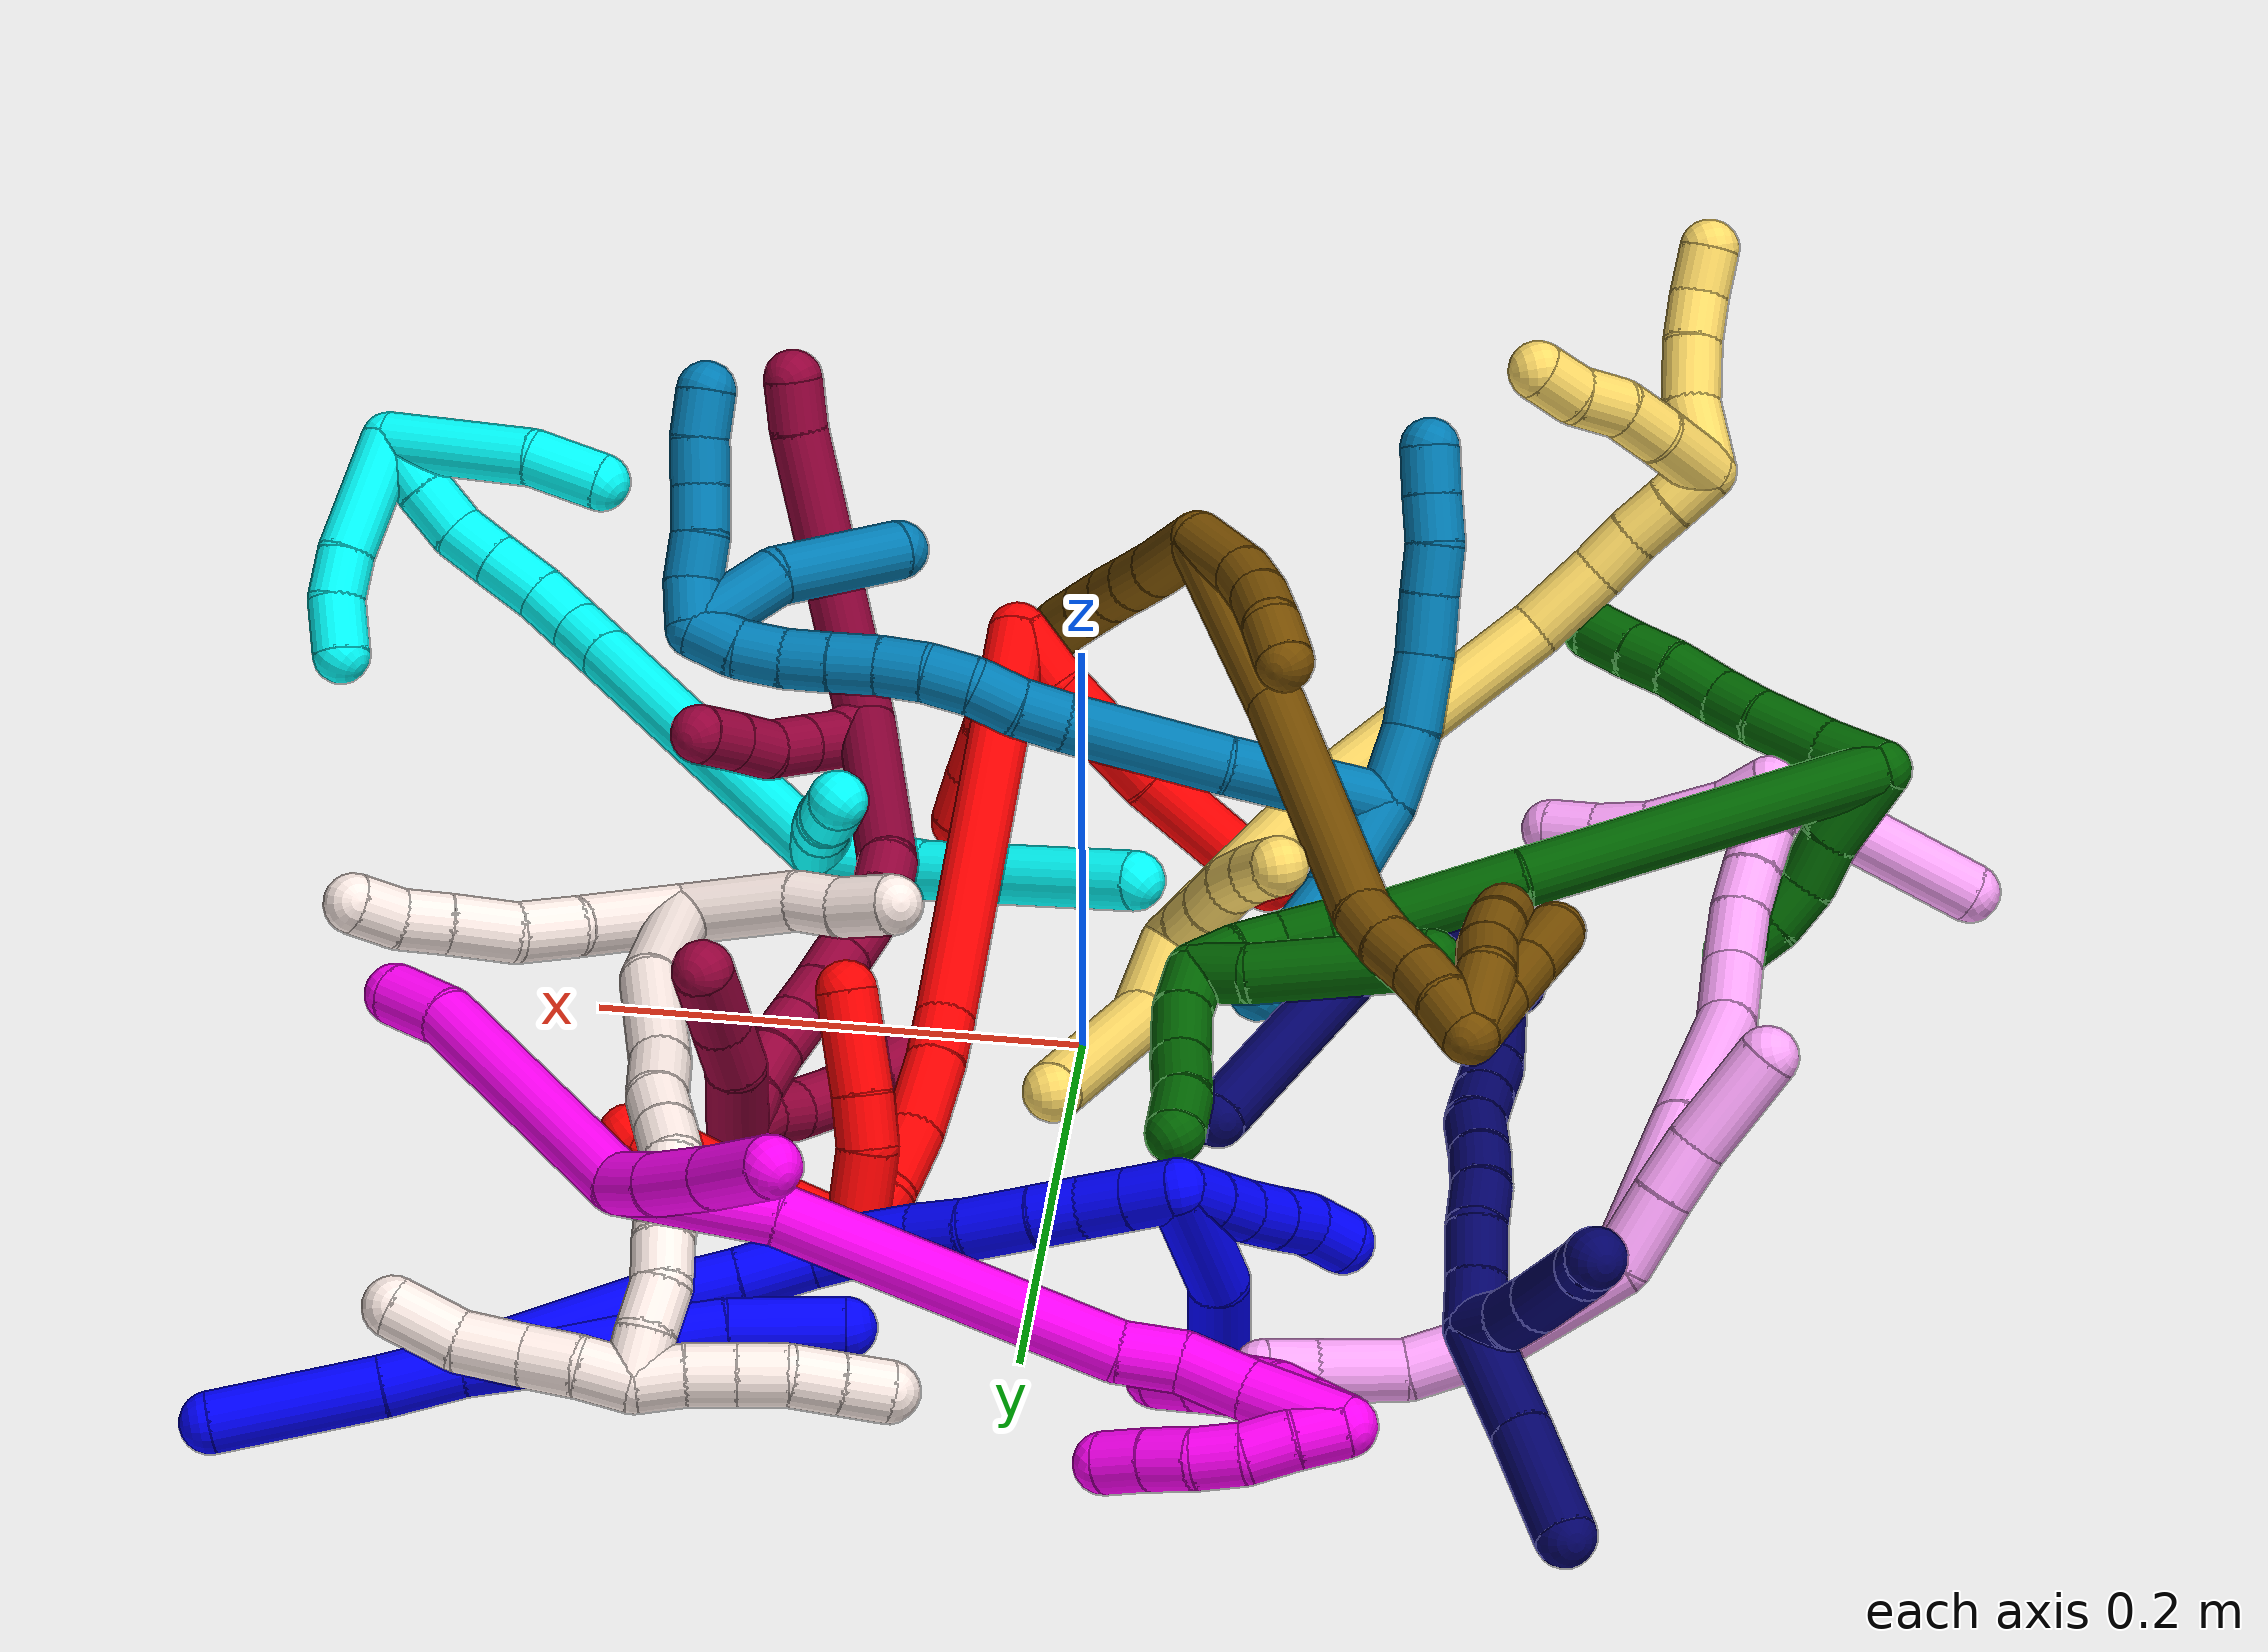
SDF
<sdf version="1.7">
 <world name="default">
  <plugin name="TubeGeneratorPlugin" filename="libtube_generator_plugin.so"/>
  <model name="photoneo_s_sensor">
   <static>1</static>
   <pose>0 0 2 1.57079 1.57079 3.14159</pose>
   <link name="link">
    <inertial><mass>0.1</mass></inertial>
    <sensor name="sensor" type="depth">
     <update_rate>30</update_rate>
     <camera>
      <horizontal_fov>1.22</horizontal_fov>
      <image><width>1920</width><height>1200</height><format>B8G8R8</format></image>
      <clip><near>0.1</near><far>4</far></clip>
      <depth_camera><output>points</output></depth_camera>
     </camera>
     <plugin name="camera_plugin" filename="libgazebo_ros_depth_camera.so">
      <baseline>0.2</baseline>
      <alwaysOn>1</alwaysOn>
      <updateRate>0.0</updateRate>
      <cameraName>camera_ir</cameraName>
      <imageTopicName>/camera/color/image_raw</imageTopicName>
      <cameraInfoTopicName>/camera/color/camera_info</cameraInfoTopicName>
      <depthImageTopicName>/camera/depth/image_raw</depthImageTopicName>
      <depthImageCameraInfoTopicName>/camera/depth/camera_info</depthImageCameraInfoTopicName>
      <pointCloudTopicName>/camera/depth/points</pointCloudTopicName>
      <frameName>fr_optical</frameName>
      <pointCloudCutoff>0.1</pointCloudCutoff>
      <pointCloudCutoffMax>2.0</pointCloudCutoffMax>
      <distortionK1>0</distortionK1>
      <distortionK2>0</distortionK2>
      <distortionK3>0</distortionK3>
      <distortionT1>0</distortionT1>
      <distortionT2>0</distortionT2>
      <CxPrime>0</CxPrime>
      <Cx>0</Cx>
      <Cy>0</Cy>
      <focalLength>0</focalLength>
      <hackBaseline>0</hackBaseline>
     </plugin>
    </sensor>
   </link>
  </model>
  <gravity>0 0 -9.8</gravity>
  <magnetic_field>6e-06 2.3e-05 -4.2e-05</magnetic_field>
  <atmosphere type="adiabatic"/>
  <physics name="default_physics" default="0" type="ode">
   <max_step_size>0.003</max_step_size>
   <real_time_factor>1</real_time_factor>
   <real_time_update_rate>1000</real_time_update_rate>
   <max_contacts>10000</max_contacts>
   <ode>
    <solver>
     <type>quick</type>
     <iters>100</iters>
     <sor>1.3</sor>
     <use_dynamic_moi_rescaling>0</use_dynamic_moi_rescaling>
    </solver>
    <constraints>
     <contact_max_correcting_vel>0</contact_max_correcting_vel>
     <contact_surface_layer>0.001</contact_surface_layer>
     <cfm>0</cfm>
     <erp>0.2</erp>
    </constraints>
   </ode>
  </physics>
  <scene><ambient>0.4 0.4 0.4 1</ambient><background>0.7 0.7 0.7 1</background><shadows>0</shadows></scene>
  <audio><device>default</device></audio>
  <spherical_coordinates>
   <surface_model>EARTH_WGS84</surface_model>
   <latitude_deg>0</latitude_deg>
   <longitude_deg>0</longitude_deg>
   <elevation>0</elevation>
   <heading_deg>0</heading_deg>
  </spherical_coordinates>
  <model name="bin">
   <static>1</static>
   <link name="bottom">
    <collision name="collision-bottom">
     <pose>0 0 -0.01 0 -0 0</pose>
     <geometry><box><size>0.8 0.6 0.02</size></box></geometry>
     <surface>
      <friction><ode><mu>100</mu><mu2>100</mu2></ode></friction>
      <contact><collide_bitmask>65535</collide_bitmask></contact>
     </surface>
    </collision>
   </link>
   <link name="west_wall">
    <collision name="collision-west_wall">
     <pose>-0.41 0 0.1 0 -0 0</pose>
     <geometry><box><size>0.02 0.6 0.2</size></box></geometry>
     <surface>
      <friction><ode><mu>100</mu><mu2>100</mu2></ode></friction>
      <contact><collide_bitmask>65535</collide_bitmask></contact>
     </surface>
    </collision>
   </link>
   <link name="east_wall">
    <collision name="collision-east_wall">
     <pose>0.41 0 0.1 0 -0 0</pose>
     <geometry><box><size>0.02 0.6 0.2</size></box></geometry>
     <surface>
      <friction><ode><mu>100</mu><mu2>100</mu2></ode></friction>
      <contact><collide_bitmask>65535</collide_bitmask></contact>
     </surface>
    </collision>
   </link>
   <link name="south_wall">
    <collision name="collision-south_wall">
     <pose>0 -0.31 0.1 0 -0 0</pose>
     <geometry><box><size>0.8 0.02 0.2</size></box></geometry>
     <surface>
      <friction><ode><mu>100</mu><mu2>100</mu2></ode></friction>
      <contact><collide_bitmask>65535</collide_bitmask></contact>
     </surface>
    </collision>
   </link>
   <link name="north_wall">
    <collision name="collision-north_wall">
     <pose>0 0.31 0.1 0 -0 0</pose>
     <geometry><box><size>0.8 0.02 0.2</size></box></geometry>
     <surface>
      <friction><ode><mu>100</mu><mu2>100</mu2></ode></friction>
      <contact><collide_bitmask>65535</collide_bitmask></contact>
     </surface>
    </collision>
   </link>
  </model>
  <model name="1">
   <static>0</static>
   <link name="1">
    <collision name="collision-cylinder-e_1_2_8">
     <pose>-0.000503 0.000308 -0.017146 -3.12366 -0.029312 2.04348</pose>
     <geometry><cylinder><radius>0.0125</radius><length>0.034312</length></cylinder></geometry>
     <surface>
      <friction><ode><mu>1.16</mu><mu2>1.16</mu2><slip1>0</slip1><slip2>0</slip2></ode></friction>
      <contact><ode><kp>1e+06</kp><kd>1</kd><max_vel>0</max_vel><min_depth>0.001</min_depth></ode></contact>
     </surface>
    </collision>
    <visual name="visual-cylinder-e_1_2_8">
     <pose>-0.000503 0.000308 -0.017146 -3.12366 -0.029312 2.04348</pose>
     <geometry><cylinder><radius>0.0125</radius><length>0.034312</length></cylinder></geometry>
     <material><ambient>0 0 1 1</ambient></material>
    </visual>
    <collision name="collision-cylinder-e_2_8_9">
     <pose>-0.001864 0.001558 -0.069112 -3.11452 -0.024645 1.47715</pose>
     <geometry><cylinder><radius>0.0125</radius><length>0.069688</length></cylinder></geometry>
     <surface>
      <friction><ode><mu>1.16</mu><mu2>1.16</mu2><slip1>0</slip1><slip2>0</slip2></ode></friction>
      <contact><ode><kp>1e+06</kp><kd>1</kd><max_vel>0</max_vel><min_depth>0.001</min_depth></ode></contact>
     </surface>
    </collision>
    <visual name="visual-cylinder-e_2_8_9">
     <pose>-0.001864 0.001558 -0.069112 -3.11452 -0.024645 1.47715</pose>
     <geometry><cylinder><radius>0.0125</radius><length>0.069688</length></cylinder></geometry>
     <material><ambient>0 0 1 1</ambient></material>
    </visual>
    <collision name="collision-cylinder-e_3_9_6">
     <pose>-0.004811 0.00561 -0.126626 -3.00542 -0.090932 1.17673</pose>
     <geometry><cylinder><radius>0.0125</radius><length>0.046</length></cylinder></geometry>
     <surface>
      <friction><ode><mu>1.16</mu><mu2>1.16</mu2><slip1>0</slip1><slip2>0</slip2></ode></friction>
      <contact><ode><kp>1e+06</kp><kd>1</kd><max_vel>0</max_vel><min_depth>0.001</min_depth></ode></contact>
     </surface>
    </collision>
    <visual name="visual-cylinder-e_3_9_6">
     <pose>-0.004811 0.00561 -0.126626 -3.00542 -0.090932 1.17673</pose>
     <geometry><cylinder><radius>0.0125</radius><length>0.046</length></cylinder></geometry>
     <material><ambient>0 0 1 1</ambient></material>
    </visual>
    <collision name="collision-cylinder-e_1_2_10">
     <pose>-0.000551 0.001163 0.015721 -0.073842 -0.034923 0.00129</pose>
     <geometry><cylinder><radius>0.0125</radius><length>0.031547</length></cylinder></geometry>
     <surface>
      <friction><ode><mu>1.16</mu><mu2>1.16</mu2><slip1>0</slip1><slip2>0</slip2></ode></friction>
      <contact><ode><kp>1e+06</kp><kd>1</kd><max_vel>0</max_vel><min_depth>0.001</min_depth></ode></contact>
     </surface>
    </collision>
    <visual name="visual-cylinder-e_1_2_10">
     <pose>-0.000551 0.001163 0.015721 -0.073842 -0.034923 0.00129</pose>
     <geometry><cylinder><radius>0.0125</radius><length>0.031547</length></cylinder></geometry>
     <material><ambient>0 0 1 1</ambient></material>
    </visual>
    <collision name="collision-cylinder-e_2_10_5">
     <pose>-0.000505 0.004117 0.065616 -0.052376 0.017415 -0.000456</pose>
     <geometry><cylinder><radius>0.0125</radius><length>0.068453</length></cylinder></geometry>
     <surface>
      <friction><ode><mu>1.16</mu><mu2>1.16</mu2><slip1>0</slip1><slip2>0</slip2></ode></friction>
      <contact><ode><kp>1e+06</kp><kd>1</kd><max_vel>0</max_vel><min_depth>0.001</min_depth></ode></contact>
     </surface>
    </collision>
    <visual name="visual-cylinder-e_2_10_5">
     <pose>-0.000505 0.004117 0.065616 -0.052376 0.017415 -0.000456</pose>
     <geometry><cylinder><radius>0.0125</radius><length>0.068453</length></cylinder></geometry>
     <material><ambient>0 0 1 1</ambient></material>
    </visual>
    <collision name="collision-cylinder-e_1_2_11">
     <pose>0.007485 -0.002797 -0.043269 3.07705 0.170948 2.42097</pose>
     <geometry><cylinder><radius>0.0125</radius><length>0.088002</length></cylinder></geometry>
     <surface>
      <friction><ode><mu>1.16</mu><mu2>1.16</mu2><slip1>0</slip1><slip2>0</slip2></ode></friction>
      <contact><ode><kp>1e+06</kp><kd>1</kd><max_vel>0</max_vel><min_depth>0.001</min_depth></ode></contact>
     </surface>
    </collision>
    <visual name="visual-cylinder-e_1_2_11">
     <pose>0.007485 -0.002797 -0.043269 3.07705 0.170948 2.42097</pose>
     <geometry><cylinder><radius>0.0125</radius><length>0.088002</length></cylinder></geometry>
     <material><ambient>0 0 1 1</ambient></material>
    </visual>
    <collision name="collision-cylinder-e_2_11_12">
     <pose>0.015384 -0.006358 -0.099188 3.08119 0.032611 0.989851</pose>
     <geometry><cylinder><radius>0.0125</radius><length>0.025358</length></cylinder></geometry>
     <surface>
      <friction><ode><mu>1.16</mu><mu2>1.16</mu2><slip1>0</slip1><slip2>0</slip2></ode></friction>
      <contact><ode><kp>1e+06</kp><kd>1</kd><max_vel>0</max_vel><min_depth>0.001</min_depth></ode></contact>
     </surface>
    </collision>
    <visual name="visual-cylinder-e_2_11_12">
     <pose>0.015384 -0.006358 -0.099188 3.08119 0.032611 0.989851</pose>
     <geometry><cylinder><radius>0.0125</radius><length>0.025358</length></cylinder></geometry>
     <material><ambient>0 0 1 1</ambient></material>
    </visual>
    <collision name="collision-cylinder-e_3_12_13">
     <pose>0.016944 -0.008457 -0.126458 3.05062 0.077912 1.41627</pose>
     <geometry><cylinder><radius>0.0125</radius><length>0.029453</length></cylinder></geometry>
     <surface>
      <friction><ode><mu>1.16</mu><mu2>1.16</mu2><slip1>0</slip1><slip2>0</slip2></ode></friction>
      <contact><ode><kp>1e+06</kp><kd>1</kd><max_vel>0</max_vel><min_depth>0.001</min_depth></ode></contact>
     </surface>
    </collision>
    <visual name="visual-cylinder-e_3_12_13">
     <pose>0.016944 -0.008457 -0.126458 3.05062 0.077912 1.41627</pose>
     <geometry><cylinder><radius>0.0125</radius><length>0.029453</length></cylinder></geometry>
     <material><ambient>0 0 1 1</ambient></material>
    </visual>
    <collision name="collision-cylinder-e_4_13_14">
     <pose>0.016881 -0.01154 -0.152237 2.98606 -0.106644 -1.20107</pose>
     <geometry><cylinder><radius>0.0125</radius><length>0.022717</length></cylinder></geometry>
     <surface>
      <friction><ode><mu>1.16</mu><mu2>1.16</mu2><slip1>0</slip1><slip2>0</slip2></ode></friction>
      <contact><ode><kp>1e+06</kp><kd>1</kd><max_vel>0</max_vel><min_depth>0.001</min_depth></ode></contact>
     </surface>
    </collision>
    <visual name="visual-cylinder-e_4_13_14">
     <pose>0.016881 -0.01154 -0.152237 2.98606 -0.106644 -1.20107</pose>
     <geometry><cylinder><radius>0.0125</radius><length>0.022717</length></cylinder></geometry>
     <material><ambient>0 0 1 1</ambient></material>
    </visual>
    <collision name="collision-cylinder-e_5_14_15">
     <pose>0.012313 -0.015586 -0.173412 2.91622 -0.315905 -1.90615</pose>
     <geometry><cylinder><radius>0.0125</radius><length>0.021624</length></cylinder></geometry>
     <surface>
      <friction><ode><mu>1.16</mu><mu2>1.16</mu2><slip1>0</slip1><slip2>0</slip2></ode></friction>
      <contact><ode><kp>1e+06</kp><kd>1</kd><max_vel>0</max_vel><min_depth>0.001</min_depth></ode></contact>
     </surface>
    </collision>
    <visual name="visual-cylinder-e_5_14_15">
     <pose>0.012313 -0.015586 -0.173412 2.91622 -0.315905 -1.90615</pose>
     <geometry><cylinder><radius>0.0125</radius><length>0.021624</length></cylinder></geometry>
     <material><ambient>0 0 1 1</ambient></material>
    </visual>
    <collision name="collision-cylinder-e_6_15_16">
     <pose>0.003295 -0.020988 -0.19304 2.82911 -0.510693 -2.0557</pose>
     <geometry><cylinder><radius>0.0125</radius><length>0.023155</length></cylinder></geometry>
     <surface>
      <friction><ode><mu>1.16</mu><mu2>1.16</mu2><slip1>0</slip1><slip2>0</slip2></ode></friction>
      <contact><ode><kp>1e+06</kp><kd>1</kd><max_vel>0</max_vel><min_depth>0.001</min_depth></ode></contact>
     </surface>
    </collision>
    <visual name="visual-cylinder-e_6_15_16">
     <pose>0.003295 -0.020988 -0.19304 2.82911 -0.510693 -2.0557</pose>
     <geometry><cylinder><radius>0.0125</radius><length>0.023155</length></cylinder></geometry>
     <material><ambient>0 0 1 1</ambient></material>
    </visual>
    <collision name="collision-cylinder-e_7_16_17">
     <pose>-0.007332 -0.027744 -0.215835 2.87142 -0.34835 -1.8262</pose>
     <geometry><cylinder><radius>0.0125</radius><length>0.029108</length></cylinder></geometry>
     <surface>
      <friction><ode><mu>1.16</mu><mu2>1.16</mu2><slip1>0</slip1><slip2>0</slip2></ode></friction>
      <contact><ode><kp>1e+06</kp><kd>1</kd><max_vel>0</max_vel><min_depth>0.001</min_depth></ode></contact>
     </surface>
    </collision>
    <visual name="visual-cylinder-e_7_16_17">
     <pose>-0.007332 -0.027744 -0.215835 2.87142 -0.34835 -1.8262</pose>
     <geometry><cylinder><radius>0.0125</radius><length>0.029108</length></cylinder></geometry>
     <material><ambient>0 0 1 1</ambient></material>
    </visual>
    <collision name="collision-cylinder-e_8_17_18">
     <pose>-0.015023 -0.033458 -0.238677 2.93122 -0.269065 -1.81671</pose>
     <geometry><cylinder><radius>0.0125</radius><length>0.020489</length></cylinder></geometry>
     <surface>
      <friction><ode><mu>1.16</mu><mu2>1.16</mu2><slip1>0</slip1><slip2>0</slip2></ode></friction>
      <contact><ode><kp>1e+06</kp><kd>1</kd><max_vel>0</max_vel><min_depth>0.001</min_depth></ode></contact>
     </surface>
    </collision>
    <visual name="visual-cylinder-e_8_17_18">
     <pose>-0.015023 -0.033458 -0.238677 2.93122 -0.269065 -1.81671</pose>
     <geometry><cylinder><radius>0.0125</radius><length>0.020489</length></cylinder></geometry>
     <material><ambient>0 0 1 1</ambient></material>
    </visual>
    <collision name="collision-cylinder-e_9_18_19">
     <pose>-0.021486 -0.038171 -0.257267 2.85311 -0.381638 -1.85212</pose>
     <geometry><cylinder><radius>0.0125</radius><length>0.020079</length></cylinder></geometry>
     <surface>
      <friction><ode><mu>1.16</mu><mu2>1.16</mu2><slip1>0</slip1><slip2>0</slip2></ode></friction>
      <contact><ode><kp>1e+06</kp><kd>1</kd><max_vel>0</max_vel><min_depth>0.001</min_depth></ode></contact>
     </surface>
    </collision>
    <visual name="visual-cylinder-e_9_18_19">
     <pose>-0.021486 -0.038171 -0.257267 2.85311 -0.381638 -1.85212</pose>
     <geometry><cylinder><radius>0.0125</radius><length>0.020079</length></cylinder></geometry>
     <material><ambient>0 0 1 1</ambient></material>
    </visual>
    <collision name="collision-cylinder-e_10_19_1">
     <pose>-0.028897 -0.043521 -0.275109 2.84741 -0.375671 -1.81738</pose>
     <geometry><cylinder><radius>0.0125</radius><length>0.020015</length></cylinder></geometry>
     <surface>
      <friction><ode><mu>1.16</mu><mu2>1.16</mu2><slip1>0</slip1><slip2>0</slip2></ode></friction>
      <contact><ode><kp>1e+06</kp><kd>1</kd><max_vel>0</max_vel><min_depth>0.001</min_depth></ode></contact>
     </surface>
    </collision>
    <visual name="visual-cylinder-e_10_19_1">
     <pose>-0.028897 -0.043521 -0.275109 2.84741 -0.375671 -1.81738</pose>
     <geometry><cylinder><radius>0.0125</radius><length>0.020015</length></cylinder></geometry>
     <material><ambient>0 0 1 1</ambient></material>
    </visual>
    <collision name="collision-cylinder-e_1_1_20">
     <pose>-0.025586 -0.018344 -0.2897 -1.77187 0.240656 -0.293952</pose>
     <geometry><cylinder><radius>0.0125</radius><length>0.058587</length></cylinder></geometry>
     <surface>
      <friction><ode><mu>1.16</mu><mu2>1.16</mu2><slip1>0</slip1><slip2>0</slip2></ode></friction>
      <contact><ode><kp>1e+06</kp><kd>1</kd><max_vel>0</max_vel><min_depth>0.001</min_depth></ode></contact>
     </surface>
    </collision>
    <visual name="visual-cylinder-e_1_1_20">
     <pose>-0.025586 -0.018344 -0.2897 -1.77187 0.240656 -0.293952</pose>
     <geometry><cylinder><radius>0.0125</radius><length>0.058587</length></cylinder></geometry>
     <material><ambient>0 0 1 1</ambient></material>
    </visual>
    <collision name="collision-cylinder-e_2_20_4">
     <pose>-0.012608 0.029297 -0.293914 -1.49668 0.293791 -0.273054</pose>
     <geometry><cylinder><radius>0.0125</radius><length>0.041413</length></cylinder></geometry>
     <surface>
      <friction><ode><mu>1.16</mu><mu2>1.16</mu2><slip1>0</slip1><slip2>0</slip2></ode></friction>
      <contact><ode><kp>1e+06</kp><kd>1</kd><max_vel>0</max_vel><min_depth>0.001</min_depth></ode></contact>
     </surface>
    </collision>
    <visual name="visual-cylinder-e_2_20_4">
     <pose>-0.012608 0.029297 -0.293914 -1.49668 0.293791 -0.273054</pose>
     <geometry><cylinder><radius>0.0125</radius><length>0.041413</length></cylinder></geometry>
     <material><ambient>0 0 1 1</ambient></material>
    </visual>
    <collision name="collision-cylinder-e_1_1_21">
     <pose>-0.02822 -0.039561 -0.29008 -2.30923 0.449908 -0.955424</pose>
     <geometry><cylinder><radius>0.0125</radius><length>0.02</length></cylinder></geometry>
     <surface>
      <friction><ode><mu>1.16</mu><mu2>1.16</mu2><slip1>0</slip1><slip2>0</slip2></ode></friction>
      <contact><ode><kp>1e+06</kp><kd>1</kd><max_vel>0</max_vel><min_depth>0.001</min_depth></ode></contact>
     </surface>
    </collision>
    <visual name="visual-cylinder-e_1_1_21">
     <pose>-0.02822 -0.039561 -0.29008 -2.30923 0.449908 -0.955424</pose>
     <geometry><cylinder><radius>0.0125</radius><length>0.02</length></cylinder></geometry>
     <material><ambient>0 0 1 1</ambient></material>
    </visual>
    <collision name="collision-cylinder-e_2_21_22">
     <pose>-0.019383 -0.026242 -0.302101 -2.3008 0.465366 -0.974855</pose>
     <geometry><cylinder><radius>0.0125</radius><length>0.02</length></cylinder></geometry>
     <surface>
      <friction><ode><mu>1.16</mu><mu2>1.16</mu2><slip1>0</slip1><slip2>0</slip2></ode></friction>
      <contact><ode><kp>1e+06</kp><kd>1</kd><max_vel>0</max_vel><min_depth>0.001</min_depth></ode></contact>
     </surface>
    </collision>
    <visual name="visual-cylinder-e_2_21_22">
     <pose>-0.019383 -0.026242 -0.302101 -2.3008 0.465366 -0.974855</pose>
     <geometry><cylinder><radius>0.0125</radius><length>0.02</length></cylinder></geometry>
     <material><ambient>0 0 1 1</ambient></material>
    </visual>
    <collision name="collision-cylinder-e_3_22_23">
     <pose>-0.010406 -0.013382 -0.314494 -2.3746 0.465642 -1.06266</pose>
     <geometry><cylinder><radius>0.0125</radius><length>0.02</length></cylinder></geometry>
     <surface>
      <friction><ode><mu>1.16</mu><mu2>1.16</mu2><slip1>0</slip1><slip2>0</slip2></ode></friction>
      <contact><ode><kp>1e+06</kp><kd>1</kd><max_vel>0</max_vel><min_depth>0.001</min_depth></ode></contact>
     </surface>
    </collision>
    <visual name="visual-cylinder-e_3_22_23">
     <pose>-0.010406 -0.013382 -0.314494 -2.3746 0.465642 -1.06266</pose>
     <geometry><cylinder><radius>0.0125</radius><length>0.02</length></cylinder></geometry>
     <material><ambient>0 0 1 1</ambient></material>
    </visual>
    <collision name="collision-cylinder-e_4_23_24">
     <pose>-0.001134 -0.001192 -0.327351 -2.39126 0.498546 -1.14769</pose>
     <geometry><cylinder><radius>0.0125</radius><length>0.02</length></cylinder></geometry>
     <surface>
      <friction><ode><mu>1.16</mu><mu2>1.16</mu2><slip1>0</slip1><slip2>0</slip2></ode></friction>
      <contact><ode><kp>1e+06</kp><kd>1</kd><max_vel>0</max_vel><min_depth>0.001</min_depth></ode></contact>
     </surface>
    </collision>
    <visual name="visual-cylinder-e_4_23_24">
     <pose>-0.001134 -0.001192 -0.327351 -2.39126 0.498546 -1.14769</pose>
     <geometry><cylinder><radius>0.0125</radius><length>0.02</length></cylinder></geometry>
     <material><ambient>0 0 1 1</ambient></material>
    </visual>
    <collision name="collision-cylinder-e_5_24_3">
     <pose>0.005392 0.011959 -0.340532 -2.32703 0.17542 -0.402162</pose>
     <geometry><cylinder><radius>0.0125</radius><length>0.02</length></cylinder></geometry>
     <surface>
      <friction><ode><mu>1.16</mu><mu2>1.16</mu2><slip1>0</slip1><slip2>0</slip2></ode></friction>
      <contact><ode><kp>1e+06</kp><kd>1</kd><max_vel>0</max_vel><min_depth>0.001</min_depth></ode></contact>
     </surface>
    </collision>
    <visual name="visual-cylinder-e_5_24_3">
     <pose>0.005392 0.011959 -0.340532 -2.32703 0.17542 -0.402162</pose>
     <geometry><cylinder><radius>0.0125</radius><length>0.02</length></cylinder></geometry>
     <material><ambient>0 0 1 1</ambient></material>
    </visual>
    <collision name="collision-sphere-3">
     <pose>0.007138 0.019122 -0.347289 0 -0 0</pose>
     <geometry><sphere><radius>0.0125</radius></sphere></geometry>
     <surface>
      <friction><ode><mu>1.16</mu><mu2>1.16</mu2><slip1>0</slip1><slip2>0</slip2></ode></friction>
      <contact><ode><kp>1e+06</kp><kd>1</kd><max_vel>0</max_vel><min_depth>0.001</min_depth></ode></contact>
     </surface>
    </collision>
    <visual name="visual-sphere-3">
     <pose>0.007138 0.019122 -0.347289 0 -0 0</pose>
     <geometry><sphere><radius>0.0125</radius></sphere></geometry>
     <material><ambient>0 0 1 1</ambient></material>
    </visual>
    <collision name="collision-sphere-24">
     <pose>0.003647 0.004797 -0.333776 0 -0 0</pose>
     <geometry><sphere><radius>0.0125</radius></sphere></geometry>
     <surface>
      <friction><ode><mu>1.16</mu><mu2>1.16</mu2><slip1>0</slip1><slip2>0</slip2></ode></friction>
      <contact><ode><kp>1e+06</kp><kd>1</kd><max_vel>0</max_vel><min_depth>0.001</min_depth></ode></contact>
     </surface>
    </collision>
    <visual name="visual-sphere-24">
     <pose>0.003647 0.004797 -0.333776 0 -0 0</pose>
     <geometry><sphere><radius>0.0125</radius></sphere></geometry>
     <material><ambient>0 0 1 1</ambient></material>
    </visual>
    <collision name="collision-sphere-23">
     <pose>-0.005916 -0.007181 -0.320927 0 -0 0</pose>
     <geometry><sphere><radius>0.0125</radius></sphere></geometry>
     <surface>
      <friction><ode><mu>1.16</mu><mu2>1.16</mu2><slip1>0</slip1><slip2>0</slip2></ode></friction>
      <contact><ode><kp>1e+06</kp><kd>1</kd><max_vel>0</max_vel><min_depth>0.001</min_depth></ode></contact>
     </surface>
    </collision>
    <visual name="visual-sphere-23">
     <pose>-0.005916 -0.007181 -0.320927 0 -0 0</pose>
     <geometry><sphere><radius>0.0125</radius></sphere></geometry>
     <material><ambient>0 0 1 1</ambient></material>
    </visual>
    <collision name="collision-sphere-22">
     <pose>-0.014896 -0.019583 -0.30806 0 -0 0</pose>
     <geometry><sphere><radius>0.0125</radius></sphere></geometry>
     <surface>
      <friction><ode><mu>1.16</mu><mu2>1.16</mu2><slip1>0</slip1><slip2>0</slip2></ode></friction>
      <contact><ode><kp>1e+06</kp><kd>1</kd><max_vel>0</max_vel><min_depth>0.001</min_depth></ode></contact>
     </surface>
    </collision>
    <visual name="visual-sphere-22">
     <pose>-0.014896 -0.019583 -0.30806 0 -0 0</pose>
     <geometry><sphere><radius>0.0125</radius></sphere></geometry>
     <material><ambient>0 0 1 1</ambient></material>
    </visual>
    <collision name="collision-sphere-21">
     <pose>-0.023871 -0.032901 -0.296141 0 -0 0</pose>
     <geometry><sphere><radius>0.0125</radius></sphere></geometry>
     <surface>
      <friction><ode><mu>1.16</mu><mu2>1.16</mu2><slip1>0</slip1><slip2>0</slip2></ode></friction>
      <contact><ode><kp>1e+06</kp><kd>1</kd><max_vel>0</max_vel><min_depth>0.001</min_depth></ode></contact>
     </surface>
    </collision>
    <visual name="visual-sphere-21">
     <pose>-0.023871 -0.032901 -0.296141 0 -0 0</pose>
     <geometry><sphere><radius>0.0125</radius></sphere></geometry>
     <material><ambient>0 0 1 1</ambient></material>
    </visual>
    <collision name="collision-sphere-4">
     <pose>-0.006612 0.049062 -0.292447 0 -0 0</pose>
     <geometry><sphere><radius>0.0125</radius></sphere></geometry>
     <surface>
      <friction><ode><mu>1.16</mu><mu2>1.16</mu2><slip1>0</slip1><slip2>0</slip2></ode></friction>
      <contact><ode><kp>1e+06</kp><kd>1</kd><max_vel>0</max_vel><min_depth>0.001</min_depth></ode></contact>
     </surface>
    </collision>
    <visual name="visual-sphere-4">
     <pose>-0.006612 0.049062 -0.292447 0 -0 0</pose>
     <geometry><sphere><radius>0.0125</radius></sphere></geometry>
     <material><ambient>0 0 1 1</ambient></material>
    </visual>
    <collision name="collision-sphere-20">
     <pose>-0.018605 0.009533 -0.295382 0 -0 0</pose>
     <geometry><sphere><radius>0.0125</radius></sphere></geometry>
     <surface>
      <friction><ode><mu>1.16</mu><mu2>1.16</mu2><slip1>0</slip1><slip2>0</slip2></ode></friction>
      <contact><ode><kp>1e+06</kp><kd>1</kd><max_vel>0</max_vel><min_depth>0.001</min_depth></ode></contact>
     </surface>
    </collision>
    <visual name="visual-sphere-20">
     <pose>-0.018605 0.009533 -0.295382 0 -0 0</pose>
     <geometry><sphere><radius>0.0125</radius></sphere></geometry>
     <material><ambient>0 0 1 1</ambient></material>
    </visual>
    <collision name="collision-sphere-5">
     <pose>9.1e-05 0.005909 0.099791 0 -0 0</pose>
     <geometry><sphere><radius>0.0125</radius></sphere></geometry>
     <surface>
      <friction><ode><mu>1.16</mu><mu2>1.16</mu2><slip1>0</slip1><slip2>0</slip2></ode></friction>
      <contact><ode><kp>1e+06</kp><kd>1</kd><max_vel>0</max_vel><min_depth>0.001</min_depth></ode></contact>
     </surface>
    </collision>
    <visual name="visual-sphere-5">
     <pose>9.1e-05 0.005909 0.099791 0 -0 0</pose>
     <geometry><sphere><radius>0.0125</radius></sphere></geometry>
     <material><ambient>0 0 1 1</ambient></material>
    </visual>
    <collision name="collision-sphere-10">
     <pose>-0.001101 0.002326 0.031441 0 -0 0</pose>
     <geometry><sphere><radius>0.0125</radius></sphere></geometry>
     <surface>
      <friction><ode><mu>1.16</mu><mu2>1.16</mu2><slip1>0</slip1><slip2>0</slip2></ode></friction>
      <contact><ode><kp>1e+06</kp><kd>1</kd><max_vel>0</max_vel><min_depth>0.001</min_depth></ode></contact>
     </surface>
    </collision>
    <visual name="visual-sphere-10">
     <pose>-0.001101 0.002326 0.031441 0 -0 0</pose>
     <geometry><sphere><radius>0.0125</radius></sphere></geometry>
     <material><ambient>0 0 1 1</ambient></material>
    </visual>
    <collision name="collision-sphere-6">
     <pose>-0.0069 0.008719 -0.149319 0 -0 0</pose>
     <geometry><sphere><radius>0.0125</radius></sphere></geometry>
     <surface>
      <friction><ode><mu>1.16</mu><mu2>1.16</mu2><slip1>0</slip1><slip2>0</slip2></ode></friction>
      <contact><ode><kp>1e+06</kp><kd>1</kd><max_vel>0</max_vel><min_depth>0.001</min_depth></ode></contact>
     </surface>
    </collision>
    <visual name="visual-sphere-6">
     <pose>-0.0069 0.008719 -0.149319 0 -0 0</pose>
     <geometry><sphere><radius>0.0125</radius></sphere></geometry>
     <material><ambient>0 0 1 1</ambient></material>
    </visual>
    <collision name="collision-sphere-9">
     <pose>-0.002723 0.002501 -0.103933 0 -0 0</pose>
     <geometry><sphere><radius>0.0125</radius></sphere></geometry>
     <surface>
      <friction><ode><mu>1.16</mu><mu2>1.16</mu2><slip1>0</slip1><slip2>0</slip2></ode></friction>
      <contact><ode><kp>1e+06</kp><kd>1</kd><max_vel>0</max_vel><min_depth>0.001</min_depth></ode></contact>
     </surface>
    </collision>
    <visual name="visual-sphere-9">
     <pose>-0.002723 0.002501 -0.103933 0 -0 0</pose>
     <geometry><sphere><radius>0.0125</radius></sphere></geometry>
     <material><ambient>0 0 1 1</ambient></material>
    </visual>
    <collision name="collision-sphere-2">
     <geometry><sphere><radius>0.0125</radius></sphere></geometry>
     <surface>
      <friction><ode><mu>1.16</mu><mu2>1.16</mu2><slip1>0</slip1><slip2>0</slip2></ode></friction>
      <contact><ode><kp>1e+06</kp><kd>1</kd><max_vel>0</max_vel><min_depth>0.001</min_depth></ode></contact>
     </surface>
    </collision>
    <visual name="visual-sphere-2">
     <geometry><sphere><radius>0.0125</radius></sphere></geometry>
     <material><ambient>0 0 1 1</ambient></material>
    </visual>
    <collision name="collision-sphere-19">
     <pose>-0.025225 -0.040821 -0.266199 0 -0 0</pose>
     <geometry><sphere><radius>0.0125</radius></sphere></geometry>
     <surface>
      <friction><ode><mu>1.16</mu><mu2>1.16</mu2><slip1>0</slip1><slip2>0</slip2></ode></friction>
      <contact><ode><kp>1e+06</kp><kd>1</kd><max_vel>0</max_vel><min_depth>0.001</min_depth></ode></contact>
     </surface>
    </collision>
    <visual name="visual-sphere-19">
     <pose>-0.025225 -0.040821 -0.266199 0 -0 0</pose>
     <geometry><sphere><radius>0.0125</radius></sphere></geometry>
     <material><ambient>0 0 1 1</ambient></material>
    </visual>
    <collision name="collision-sphere-8">
     <pose>-0.001006 0.000615 -0.034292 0 -0 0</pose>
     <geometry><sphere><radius>0.0125</radius></sphere></geometry>
     <surface>
      <friction><ode><mu>1.16</mu><mu2>1.16</mu2><slip1>0</slip1><slip2>0</slip2></ode></friction>
      <contact><ode><kp>1e+06</kp><kd>1</kd><max_vel>0</max_vel><min_depth>0.001</min_depth></ode></contact>
     </surface>
    </collision>
    <visual name="visual-sphere-8">
     <pose>-0.001006 0.000615 -0.034292 0 -0 0</pose>
     <geometry><sphere><radius>0.0125</radius></sphere></geometry>
     <material><ambient>0 0 1 1</ambient></material>
    </visual>
    <collision name="collision-sphere-11">
     <pose>0.014971 -0.005593 -0.086539 0 -0 0</pose>
     <geometry><sphere><radius>0.0125</radius></sphere></geometry>
     <surface>
      <friction><ode><mu>1.16</mu><mu2>1.16</mu2><slip1>0</slip1><slip2>0</slip2></ode></friction>
      <contact><ode><kp>1e+06</kp><kd>1</kd><max_vel>0</max_vel><min_depth>0.001</min_depth></ode></contact>
     </surface>
    </collision>
    <visual name="visual-sphere-11">
     <pose>0.014971 -0.005593 -0.086539 0 -0 0</pose>
     <geometry><sphere><radius>0.0125</radius></sphere></geometry>
     <material><ambient>0 0 1 1</ambient></material>
    </visual>
    <collision name="collision-sphere-12">
     <pose>0.015797 -0.007123 -0.111837 0 -0 0</pose>
     <geometry><sphere><radius>0.0125</radius></sphere></geometry>
     <surface>
      <friction><ode><mu>1.16</mu><mu2>1.16</mu2><slip1>0</slip1><slip2>0</slip2></ode></friction>
      <contact><ode><kp>1e+06</kp><kd>1</kd><max_vel>0</max_vel><min_depth>0.001</min_depth></ode></contact>
     </surface>
    </collision>
    <visual name="visual-sphere-12">
     <pose>0.015797 -0.007123 -0.111837 0 -0 0</pose>
     <geometry><sphere><radius>0.0125</radius></sphere></geometry>
     <material><ambient>0 0 1 1</ambient></material>
    </visual>
    <collision name="collision-sphere-13">
     <pose>0.01809 -0.009791 -0.141079 0 -0 0</pose>
     <geometry><sphere><radius>0.0125</radius></sphere></geometry>
     <surface>
      <friction><ode><mu>1.16</mu><mu2>1.16</mu2><slip1>0</slip1><slip2>0</slip2></ode></friction>
      <contact><ode><kp>1e+06</kp><kd>1</kd><max_vel>0</max_vel><min_depth>0.001</min_depth></ode></contact>
     </surface>
    </collision>
    <visual name="visual-sphere-13">
     <pose>0.01809 -0.009791 -0.141079 0 -0 0</pose>
     <geometry><sphere><radius>0.0125</radius></sphere></geometry>
     <material><ambient>0 0 1 1</ambient></material>
    </visual>
    <collision name="collision-sphere-14">
     <pose>0.015672 -0.01329 -0.163394 0 -0 0</pose>
     <geometry><sphere><radius>0.0125</radius></sphere></geometry>
     <surface>
      <friction><ode><mu>1.16</mu><mu2>1.16</mu2><slip1>0</slip1><slip2>0</slip2></ode></friction>
      <contact><ode><kp>1e+06</kp><kd>1</kd><max_vel>0</max_vel><min_depth>0.001</min_depth></ode></contact>
     </surface>
    </collision>
    <visual name="visual-sphere-14">
     <pose>0.015672 -0.01329 -0.163394 0 -0 0</pose>
     <geometry><sphere><radius>0.0125</radius></sphere></geometry>
     <material><ambient>0 0 1 1</ambient></material>
    </visual>
    <collision name="collision-sphere-15">
     <pose>0.008954 -0.017883 -0.183429 0 -0 0</pose>
     <geometry><sphere><radius>0.0125</radius></sphere></geometry>
     <surface>
      <friction><ode><mu>1.16</mu><mu2>1.16</mu2><slip1>0</slip1><slip2>0</slip2></ode></friction>
      <contact><ode><kp>1e+06</kp><kd>1</kd><max_vel>0</max_vel><min_depth>0.001</min_depth></ode></contact>
     </surface>
    </collision>
    <visual name="visual-sphere-15">
     <pose>0.008954 -0.017883 -0.183429 0 -0 0</pose>
     <geometry><sphere><radius>0.0125</radius></sphere></geometry>
     <material><ambient>0 0 1 1</ambient></material>
    </visual>
    <collision name="collision-sphere-16">
     <pose>-0.002364 -0.024093 -0.202651 0 -0 0</pose>
     <geometry><sphere><radius>0.0125</radius></sphere></geometry>
     <surface>
      <friction><ode><mu>1.16</mu><mu2>1.16</mu2><slip1>0</slip1><slip2>0</slip2></ode></friction>
      <contact><ode><kp>1e+06</kp><kd>1</kd><max_vel>0</max_vel><min_depth>0.001</min_depth></ode></contact>
     </surface>
    </collision>
    <visual name="visual-sphere-16">
     <pose>-0.002364 -0.024093 -0.202651 0 -0 0</pose>
     <geometry><sphere><radius>0.0125</radius></sphere></geometry>
     <material><ambient>0 0 1 1</ambient></material>
    </visual>
    <collision name="collision-sphere-17">
     <pose>-0.0123 -0.031395 -0.229018 0 -0 0</pose>
     <geometry><sphere><radius>0.0125</radius></sphere></geometry>
     <surface>
      <friction><ode><mu>1.16</mu><mu2>1.16</mu2><slip1>0</slip1><slip2>0</slip2></ode></friction>
      <contact><ode><kp>1e+06</kp><kd>1</kd><max_vel>0</max_vel><min_depth>0.001</min_depth></ode></contact>
     </surface>
    </collision>
    <visual name="visual-sphere-17">
     <pose>-0.0123 -0.031395 -0.229018 0 -0 0</pose>
     <geometry><sphere><radius>0.0125</radius></sphere></geometry>
     <material><ambient>0 0 1 1</ambient></material>
    </visual>
    <collision name="collision-sphere-18">
     <pose>-0.017747 -0.03552 -0.248335 0 -0 0</pose>
     <geometry><sphere><radius>0.0125</radius></sphere></geometry>
     <surface>
      <friction><ode><mu>1.16</mu><mu2>1.16</mu2><slip1>0</slip1><slip2>0</slip2></ode></friction>
      <contact><ode><kp>1e+06</kp><kd>1</kd><max_vel>0</max_vel><min_depth>0.001</min_depth></ode></contact>
     </surface>
    </collision>
    <visual name="visual-sphere-18">
     <pose>-0.017747 -0.03552 -0.248335 0 -0 0</pose>
     <geometry><sphere><radius>0.0125</radius></sphere></geometry>
     <material><ambient>0 0 1 1</ambient></material>
    </visual>
    <collision name="collision-sphere-1">
     <pose>-0.032568 -0.04622 -0.284018 0 -0 0</pose>
     <geometry><sphere><radius>0.0125</radius></sphere></geometry>
     <surface>
      <friction><ode><mu>1.16</mu><mu2>1.16</mu2><slip1>0</slip1><slip2>0</slip2></ode></friction>
      <contact><ode><kp>1e+06</kp><kd>1</kd><max_vel>0</max_vel><min_depth>0.001</min_depth></ode></contact>
     </surface>
    </collision>
    <visual name="visual-sphere-1">
     <pose>-0.032568 -0.04622 -0.284018 0 -0 0</pose>
     <geometry><sphere><radius>0.0125</radius></sphere></geometry>
     <material><ambient>0 0 1 1</ambient></material>
    </visual>
    <inertial>
     <pose>-0.003698 -0.007208 -0.147264 0 -0 0</pose>
     <mass>0.75</mass>
     <inertia>
      <ixx>8.8e-05</ixx>
      <ixy>0</ixy>
      <ixz>0</ixz>
      <iyy>0.000148</iyy>
      <iyz>0</iyz>
      <izz>-7.3e-05</izz>
     </inertia>
    </inertial>
   </link>
   <pose>0.2107 0.259593 0.028016 -1.67857 0.106211 -1.32054</pose>
  </model>
  <model name="2">
   <static>0</static>
   <link name="2">
    <collision name="collision-cylinder-e_1_2_8">
     <pose>-0.000307 0.002155 -0.01395 -2.98833 -0.021716 0.280977</pose>
     <geometry><cylinder><radius>0.0125</radius><length>0.028238</length></cylinder></geometry>
     <surface>
      <friction><ode><mu>1.16</mu><mu2>1.16</mu2><slip1>0</slip1><slip2>0</slip2></ode></friction>
      <contact><ode><kp>1e+06</kp><kd>1</kd><max_vel>0</max_vel><min_depth>0.001</min_depth></ode></contact>
     </surface>
    </collision>
    <visual name="visual-cylinder-e_1_2_8">
     <pose>-0.000307 0.002155 -0.01395 -2.98833 -0.021716 0.280977</pose>
     <geometry><cylinder><radius>0.0125</radius><length>0.028238</length></cylinder></geometry>
     <material><ambient>1 0 0 1</ambient></material>
    </visual>
    <collision name="collision-cylinder-e_2_8_9">
     <pose>-0.002518 0.000692 -0.054473 3.00627 -0.070914 -0.964486</pose>
     <geometry><cylinder><radius>0.0125</radius><length>0.053771</length></cylinder></geometry>
     <surface>
      <friction><ode><mu>1.16</mu><mu2>1.16</mu2><slip1>0</slip1><slip2>0</slip2></ode></friction>
      <contact><ode><kp>1e+06</kp><kd>1</kd><max_vel>0</max_vel><min_depth>0.001</min_depth></ode></contact>
     </surface>
    </collision>
    <visual name="visual-cylinder-e_2_8_9">
     <pose>-0.002518 0.000692 -0.054473 3.00627 -0.070914 -0.964486</pose>
     <geometry><cylinder><radius>0.0125</radius><length>0.053771</length></cylinder></geometry>
     <material><ambient>1 0 0 1</ambient></material>
    </visual>
    <collision name="collision-cylinder-e_3_9_6">
     <pose>-0.010005 -0.00986 -0.113856 2.93331 -0.164933 -1.33821</pose>
     <geometry><cylinder><radius>0.0125</radius><length>0.067991</length></cylinder></geometry>
     <surface>
      <friction><ode><mu>1.16</mu><mu2>1.16</mu2><slip1>0</slip1><slip2>0</slip2></ode></friction>
      <contact><ode><kp>1e+06</kp><kd>1</kd><max_vel>0</max_vel><min_depth>0.001</min_depth></ode></contact>
     </surface>
    </collision>
    <visual name="visual-cylinder-e_3_9_6">
     <pose>-0.010005 -0.00986 -0.113856 2.93331 -0.164933 -1.33821</pose>
     <geometry><cylinder><radius>0.0125</radius><length>0.067991</length></cylinder></geometry>
     <material><ambient>1 0 0 1</ambient></material>
    </visual>
    <collision name="collision-cylinder-e_1_2_10">
     <pose>0.009445 -0.00713 -0.008101 2.41985 0.718955 1.56658</pose>
     <geometry><cylinder><radius>0.0125</radius><length>0.028683</length></cylinder></geometry>
     <surface>
      <friction><ode><mu>1.16</mu><mu2>1.16</mu2><slip1>0</slip1><slip2>0</slip2></ode></friction>
      <contact><ode><kp>1e+06</kp><kd>1</kd><max_vel>0</max_vel><min_depth>0.001</min_depth></ode></contact>
     </surface>
    </collision>
    <visual name="visual-cylinder-e_1_2_10">
     <pose>0.009445 -0.00713 -0.008101 2.41985 0.718955 1.56658</pose>
     <geometry><cylinder><radius>0.0125</radius><length>0.028683</length></cylinder></geometry>
     <material><ambient>1 0 0 1</ambient></material>
    </visual>
    <collision name="collision-cylinder-e_2_10_11">
     <pose>0.029631 -0.017987 -0.021894 2.56184 1.00615 2.14819</pose>
     <geometry><cylinder><radius>0.0125</radius><length>0.025427</length></cylinder></geometry>
     <surface>
      <friction><ode><mu>1.16</mu><mu2>1.16</mu2><slip1>0</slip1><slip2>0</slip2></ode></friction>
      <contact><ode><kp>1e+06</kp><kd>1</kd><max_vel>0</max_vel><min_depth>0.001</min_depth></ode></contact>
     </surface>
    </collision>
    <visual name="visual-cylinder-e_2_10_11">
     <pose>0.029631 -0.017987 -0.021894 2.56184 1.00615 2.14819</pose>
     <geometry><cylinder><radius>0.0125</radius><length>0.025427</length></cylinder></geometry>
     <material><ambient>1 0 0 1</ambient></material>
    </visual>
    <collision name="collision-cylinder-e_3_11_12">
     <pose>0.049685 -0.025594 -0.033184 2.53559 0.939364 2.03749</pose>
     <geometry><cylinder><radius>0.0125</radius><length>0.023079</length></cylinder></geometry>
     <surface>
      <friction><ode><mu>1.16</mu><mu2>1.16</mu2><slip1>0</slip1><slip2>0</slip2></ode></friction>
      <contact><ode><kp>1e+06</kp><kd>1</kd><max_vel>0</max_vel><min_depth>0.001</min_depth></ode></contact>
     </surface>
    </collision>
    <visual name="visual-cylinder-e_3_11_12">
     <pose>0.049685 -0.025594 -0.033184 2.53559 0.939364 2.03749</pose>
     <geometry><cylinder><radius>0.0125</radius><length>0.023079</length></cylinder></geometry>
     <material><ambient>1 0 0 1</ambient></material>
    </visual>
    <collision name="collision-cylinder-e_4_12_5">
     <pose>0.068302 -0.032146 -0.044817 2.72469 0.953751 2.36439</pose>
     <geometry><cylinder><radius>0.0125</radius><length>0.022811</length></cylinder></geometry>
     <surface>
      <friction><ode><mu>1.16</mu><mu2>1.16</mu2><slip1>0</slip1><slip2>0</slip2></ode></friction>
      <contact><ode><kp>1e+06</kp><kd>1</kd><max_vel>0</max_vel><min_depth>0.001</min_depth></ode></contact>
     </surface>
    </collision>
    <visual name="visual-cylinder-e_4_12_5">
     <pose>0.068302 -0.032146 -0.044817 2.72469 0.953751 2.36439</pose>
     <geometry><cylinder><radius>0.0125</radius><length>0.022811</length></cylinder></geometry>
     <material><ambient>1 0 0 1</ambient></material>
    </visual>
    <collision name="collision-cylinder-e_1_2_13">
     <pose>0.04603 0.064031 -0.0502 -2.23571 0.51484 -0.991692</pose>
     <geometry><cylinder><radius>0.0125</radius><length>0.186963</length></cylinder></geometry>
     <surface>
      <friction><ode><mu>1.16</mu><mu2>1.16</mu2><slip1>0</slip1><slip2>0</slip2></ode></friction>
      <contact><ode><kp>1e+06</kp><kd>1</kd><max_vel>0</max_vel><min_depth>0.001</min_depth></ode></contact>
     </surface>
    </collision>
    <visual name="visual-cylinder-e_1_2_13">
     <pose>0.04603 0.064031 -0.0502 -2.23571 0.51484 -0.991692</pose>
     <geometry><cylinder><radius>0.0125</radius><length>0.186963</length></cylinder></geometry>
     <material><ambient>1 0 0 1</ambient></material>
    </visual>
    <collision name="collision-cylinder-e_2_13_14">
     <pose>0.097048 0.13575 -0.10568 -2.1725 0.491135 -0.888711</pose>
     <geometry><cylinder><radius>0.0125</radius><length>0.021154</length></cylinder></geometry>
     <surface>
      <friction><ode><mu>1.16</mu><mu2>1.16</mu2><slip1>0</slip1><slip2>0</slip2></ode></friction>
      <contact><ode><kp>1e+06</kp><kd>1</kd><max_vel>0</max_vel><min_depth>0.001</min_depth></ode></contact>
     </surface>
    </collision>
    <visual name="visual-cylinder-e_2_13_14">
     <pose>0.097048 0.13575 -0.10568 -2.1725 0.491135 -0.888711</pose>
     <geometry><cylinder><radius>0.0125</radius><length>0.021154</length></cylinder></geometry>
     <material><ambient>1 0 0 1</ambient></material>
    </visual>
    <collision name="collision-cylinder-e_3_14_15">
     <pose>0.111199 0.156587 -0.118654 -2.10025 0.54149 -0.901556</pose>
     <geometry><cylinder><radius>0.0125</radius><length>0.035553</length></cylinder></geometry>
     <surface>
      <friction><ode><mu>1.16</mu><mu2>1.16</mu2><slip1>0</slip1><slip2>0</slip2></ode></friction>
      <contact><ode><kp>1e+06</kp><kd>1</kd><max_vel>0</max_vel><min_depth>0.001</min_depth></ode></contact>
     </surface>
    </collision>
    <visual name="visual-cylinder-e_3_14_15">
     <pose>0.111199 0.156587 -0.118654 -2.10025 0.54149 -0.901556</pose>
     <geometry><cylinder><radius>0.0125</radius><length>0.035553</length></cylinder></geometry>
     <material><ambient>1 0 0 1</ambient></material>
    </visual>
    <collision name="collision-cylinder-e_4_15_16">
     <pose>0.128164 0.182587 -0.131061 -1.92229 0.518082 -0.725302</pose>
     <geometry><cylinder><radius>0.0125</radius><length>0.031515</length></cylinder></geometry>
     <surface>
      <friction><ode><mu>1.16</mu><mu2>1.16</mu2><slip1>0</slip1><slip2>0</slip2></ode></friction>
      <contact><ode><kp>1e+06</kp><kd>1</kd><max_vel>0</max_vel><min_depth>0.001</min_depth></ode></contact>
     </surface>
    </collision>
    <visual name="visual-cylinder-e_4_15_16">
     <pose>0.128164 0.182587 -0.131061 -1.92229 0.518082 -0.725302</pose>
     <geometry><cylinder><radius>0.0125</radius><length>0.031515</length></cylinder></geometry>
     <material><ambient>1 0 0 1</ambient></material>
    </visual>
    <collision name="collision-cylinder-e_5_16_1">
     <pose>0.145266 0.20294 -0.139126 -1.99112 0.847195 -1.21528</pose>
     <geometry><cylinder><radius>0.0125</radius><length>0.024815</length></cylinder></geometry>
     <surface>
      <friction><ode><mu>1.16</mu><mu2>1.16</mu2><slip1>0</slip1><slip2>0</slip2></ode></friction>
      <contact><ode><kp>1e+06</kp><kd>1</kd><max_vel>0</max_vel><min_depth>0.001</min_depth></ode></contact>
     </surface>
    </collision>
    <visual name="visual-cylinder-e_5_16_1">
     <pose>0.145266 0.20294 -0.139126 -1.99112 0.847195 -1.21528</pose>
     <geometry><cylinder><radius>0.0125</radius><length>0.024815</length></cylinder></geometry>
     <material><ambient>1 0 0 1</ambient></material>
    </visual>
    <collision name="collision-cylinder-e_1_1_17">
     <pose>0.141225 0.209854 -0.129592 0.045435 -0.802179 -0.019271</pose>
     <geometry><cylinder><radius>0.0125</radius><length>0.037113</length></cylinder></geometry>
     <surface>
      <friction><ode><mu>1.16</mu><mu2>1.16</mu2><slip1>0</slip1><slip2>0</slip2></ode></friction>
      <contact><ode><kp>1e+06</kp><kd>1</kd><max_vel>0</max_vel><min_depth>0.001</min_depth></ode></contact>
     </surface>
    </collision>
    <visual name="visual-cylinder-e_1_1_17">
     <pose>0.141225 0.209854 -0.129592 0.045435 -0.802179 -0.019271</pose>
     <geometry><cylinder><radius>0.0125</radius><length>0.037113</length></cylinder></geometry>
     <material><ambient>1 0 0 1</ambient></material>
    </visual>
    <collision name="collision-cylinder-e_2_17_18">
     <pose>0.122386 0.207536 -0.107554 0.187047 -0.533325 -0.051234</pose>
     <geometry><cylinder><radius>0.0125</radius><length>0.021634</length></cylinder></geometry>
     <surface>
      <friction><ode><mu>1.16</mu><mu2>1.16</mu2><slip1>0</slip1><slip2>0</slip2></ode></friction>
      <contact><ode><kp>1e+06</kp><kd>1</kd><max_vel>0</max_vel><min_depth>0.001</min_depth></ode></contact>
     </surface>
    </collision>
    <visual name="visual-cylinder-e_2_17_18">
     <pose>0.122386 0.207536 -0.107554 0.187047 -0.533325 -0.051234</pose>
     <geometry><cylinder><radius>0.0125</radius><length>0.021634</length></cylinder></geometry>
     <material><ambient>1 0 0 1</ambient></material>
    </visual>
    <collision name="collision-cylinder-e_3_18_4">
     <pose>0.107781 0.2011 -0.080501 0.256976 -0.457203 -0.060103</pose>
     <geometry><cylinder><radius>0.0125</radius><length>0.041253</length></cylinder></geometry>
     <surface>
      <friction><ode><mu>1.16</mu><mu2>1.16</mu2><slip1>0</slip1><slip2>0</slip2></ode></friction>
      <contact><ode><kp>1e+06</kp><kd>1</kd><max_vel>0</max_vel><min_depth>0.001</min_depth></ode></contact>
     </surface>
    </collision>
    <visual name="visual-cylinder-e_3_18_4">
     <pose>0.107781 0.2011 -0.080501 0.256976 -0.457203 -0.060103</pose>
     <geometry><cylinder><radius>0.0125</radius><length>0.041253</length></cylinder></geometry>
     <material><ambient>1 0 0 1</ambient></material>
    </visual>
    <collision name="collision-cylinder-e_1_1_19">
     <pose>0.166778 0.208682 -0.121931 0.085332 0.534695 0.023386</pose>
     <geometry><cylinder><radius>0.0125</radius><length>0.047936</length></cylinder></geometry>
     <surface>
      <friction><ode><mu>1.16</mu><mu2>1.16</mu2><slip1>0</slip1><slip2>0</slip2></ode></friction>
      <contact><ode><kp>1e+06</kp><kd>1</kd><max_vel>0</max_vel><min_depth>0.001</min_depth></ode></contact>
     </surface>
    </collision>
    <visual name="visual-cylinder-e_1_1_19">
     <pose>0.166778 0.208682 -0.121931 0.085332 0.534695 0.023386</pose>
     <geometry><cylinder><radius>0.0125</radius><length>0.047936</length></cylinder></geometry>
     <material><ambient>1 0 0 1</ambient></material>
    </visual>
    <collision name="collision-cylinder-e_2_19_20">
     <pose>0.185124 0.205844 -0.089411 0.089984 0.471735 0.021641</pose>
     <geometry><cylinder><radius>0.0125</radius><length>0.02699</length></cylinder></geometry>
     <surface>
      <friction><ode><mu>1.16</mu><mu2>1.16</mu2><slip1>0</slip1><slip2>0</slip2></ode></friction>
      <contact><ode><kp>1e+06</kp><kd>1</kd><max_vel>0</max_vel><min_depth>0.001</min_depth></ode></contact>
     </surface>
    </collision>
    <visual name="visual-cylinder-e_2_19_20">
     <pose>0.185124 0.205844 -0.089411 0.089984 0.471735 0.021641</pose>
     <geometry><cylinder><radius>0.0125</radius><length>0.02699</length></cylinder></geometry>
     <material><ambient>1 0 0 1</ambient></material>
    </visual>
    <collision name="collision-cylinder-e_3_20_3">
     <pose>0.196484 0.207941 -0.066495 -0.282571 0.43007 -0.062111</pose>
     <geometry><cylinder><radius>0.0125</radius><length>0.025074</length></cylinder></geometry>
     <surface>
      <friction><ode><mu>1.16</mu><mu2>1.16</mu2><slip1>0</slip1><slip2>0</slip2></ode></friction>
      <contact><ode><kp>1e+06</kp><kd>1</kd><max_vel>0</max_vel><min_depth>0.001</min_depth></ode></contact>
     </surface>
    </collision>
    <visual name="visual-cylinder-e_3_20_3">
     <pose>0.196484 0.207941 -0.066495 -0.282571 0.43007 -0.062111</pose>
     <geometry><cylinder><radius>0.0125</radius><length>0.025074</length></cylinder></geometry>
     <material><ambient>1 0 0 1</ambient></material>
    </visual>
    <collision name="collision-sphere-3">
     <pose>0.201711 0.211118 -0.055551 0 -0 0</pose>
     <geometry><sphere><radius>0.0125</radius></sphere></geometry>
     <surface>
      <friction><ode><mu>1.16</mu><mu2>1.16</mu2><slip1>0</slip1><slip2>0</slip2></ode></friction>
      <contact><ode><kp>1e+06</kp><kd>1</kd><max_vel>0</max_vel><min_depth>0.001</min_depth></ode></contact>
     </surface>
    </collision>
    <visual name="visual-sphere-3">
     <pose>0.201711 0.211118 -0.055551 0 -0 0</pose>
     <geometry><sphere><radius>0.0125</radius></sphere></geometry>
     <material><ambient>1 0 0 1</ambient></material>
    </visual>
    <collision name="collision-sphere-20">
     <pose>0.191257 0.204764 -0.077438 0 -0 0</pose>
     <geometry><sphere><radius>0.0125</radius></sphere></geometry>
     <surface>
      <friction><ode><mu>1.16</mu><mu2>1.16</mu2><slip1>0</slip1><slip2>0</slip2></ode></friction>
      <contact><ode><kp>1e+06</kp><kd>1</kd><max_vel>0</max_vel><min_depth>0.001</min_depth></ode></contact>
     </surface>
    </collision>
    <visual name="visual-sphere-20">
     <pose>0.191257 0.204764 -0.077438 0 -0 0</pose>
     <geometry><sphere><radius>0.0125</radius></sphere></geometry>
     <material><ambient>1 0 0 1</ambient></material>
    </visual>
    <collision name="collision-sphere-19">
     <pose>0.178992 0.206924 -0.101383 0 -0 0</pose>
     <geometry><sphere><radius>0.0125</radius></sphere></geometry>
     <surface>
      <friction><ode><mu>1.16</mu><mu2>1.16</mu2><slip1>0</slip1><slip2>0</slip2></ode></friction>
      <contact><ode><kp>1e+06</kp><kd>1</kd><max_vel>0</max_vel><min_depth>0.001</min_depth></ode></contact>
     </surface>
    </collision>
    <visual name="visual-sphere-19">
     <pose>0.178992 0.206924 -0.101383 0 -0 0</pose>
     <geometry><sphere><radius>0.0125</radius></sphere></geometry>
     <material><ambient>1 0 0 1</ambient></material>
    </visual>
    <collision name="collision-sphere-11">
     <pose>0.040371 -0.021714 -0.027585 0 -0 0</pose>
     <geometry><sphere><radius>0.0125</radius></sphere></geometry>
     <surface>
      <friction><ode><mu>1.16</mu><mu2>1.16</mu2><slip1>0</slip1><slip2>0</slip2></ode></friction>
      <contact><ode><kp>1e+06</kp><kd>1</kd><max_vel>0</max_vel><min_depth>0.001</min_depth></ode></contact>
     </surface>
    </collision>
    <visual name="visual-sphere-11">
     <pose>0.040371 -0.021714 -0.027585 0 -0 0</pose>
     <geometry><sphere><radius>0.0125</radius></sphere></geometry>
     <material><ambient>1 0 0 1</ambient></material>
    </visual>
    <collision name="collision-sphere-10">
     <pose>0.018891 -0.01426 -0.016202 0 -0 0</pose>
     <geometry><sphere><radius>0.0125</radius></sphere></geometry>
     <surface>
      <friction><ode><mu>1.16</mu><mu2>1.16</mu2><slip1>0</slip1><slip2>0</slip2></ode></friction>
      <contact><ode><kp>1e+06</kp><kd>1</kd><max_vel>0</max_vel><min_depth>0.001</min_depth></ode></contact>
     </surface>
    </collision>
    <visual name="visual-sphere-10">
     <pose>0.018891 -0.01426 -0.016202 0 -0 0</pose>
     <geometry><sphere><radius>0.0125</radius></sphere></geometry>
     <material><ambient>1 0 0 1</ambient></material>
    </visual>
    <collision name="collision-sphere-6">
     <pose>-0.015586 -0.016794 -0.146665 0 -0 0</pose>
     <geometry><sphere><radius>0.0125</radius></sphere></geometry>
     <surface>
      <friction><ode><mu>1.16</mu><mu2>1.16</mu2><slip1>0</slip1><slip2>0</slip2></ode></friction>
      <contact><ode><kp>1e+06</kp><kd>1</kd><max_vel>0</max_vel><min_depth>0.001</min_depth></ode></contact>
     </surface>
    </collision>
    <visual name="visual-sphere-6">
     <pose>-0.015586 -0.016794 -0.146665 0 -0 0</pose>
     <geometry><sphere><radius>0.0125</radius></sphere></geometry>
     <material><ambient>1 0 0 1</ambient></material>
    </visual>
    <collision name="collision-sphere-9">
     <pose>-0.004423 -0.002926 -0.081046 0 -0 0</pose>
     <geometry><sphere><radius>0.0125</radius></sphere></geometry>
     <surface>
      <friction><ode><mu>1.16</mu><mu2>1.16</mu2><slip1>0</slip1><slip2>0</slip2></ode></friction>
      <contact><ode><kp>1e+06</kp><kd>1</kd><max_vel>0</max_vel><min_depth>0.001</min_depth></ode></contact>
     </surface>
    </collision>
    <visual name="visual-sphere-9">
     <pose>-0.004423 -0.002926 -0.081046 0 -0 0</pose>
     <geometry><sphere><radius>0.0125</radius></sphere></geometry>
     <material><ambient>1 0 0 1</ambient></material>
    </visual>
    <collision name="collision-sphere-2">
     <geometry><sphere><radius>0.0125</radius></sphere></geometry>
     <surface>
      <friction><ode><mu>1.16</mu><mu2>1.16</mu2><slip1>0</slip1><slip2>0</slip2></ode></friction>
      <contact><ode><kp>1e+06</kp><kd>1</kd><max_vel>0</max_vel><min_depth>0.001</min_depth></ode></contact>
     </surface>
    </collision>
    <visual name="visual-sphere-2">
     <geometry><sphere><radius>0.0125</radius></sphere></geometry>
     <material><ambient>1 0 0 1</ambient></material>
    </visual>
    <collision name="collision-sphere-8">
     <pose>-0.000613 0.00431 -0.027901 0 -0 0</pose>
     <geometry><sphere><radius>0.0125</radius></sphere></geometry>
     <surface>
      <friction><ode><mu>1.16</mu><mu2>1.16</mu2><slip1>0</slip1><slip2>0</slip2></ode></friction>
      <contact><ode><kp>1e+06</kp><kd>1</kd><max_vel>0</max_vel><min_depth>0.001</min_depth></ode></contact>
     </surface>
    </collision>
    <visual name="visual-sphere-8">
     <pose>-0.000613 0.00431 -0.027901 0 -0 0</pose>
     <geometry><sphere><radius>0.0125</radius></sphere></geometry>
     <material><ambient>1 0 0 1</ambient></material>
    </visual>
    <collision name="collision-sphere-12">
     <pose>0.058999 -0.029474 -0.038783 0 -0 0</pose>
     <geometry><sphere><radius>0.0125</radius></sphere></geometry>
     <surface>
      <friction><ode><mu>1.16</mu><mu2>1.16</mu2><slip1>0</slip1><slip2>0</slip2></ode></friction>
      <contact><ode><kp>1e+06</kp><kd>1</kd><max_vel>0</max_vel><min_depth>0.001</min_depth></ode></contact>
     </surface>
    </collision>
    <visual name="visual-sphere-12">
     <pose>0.058999 -0.029474 -0.038783 0 -0 0</pose>
     <geometry><sphere><radius>0.0125</radius></sphere></geometry>
     <material><ambient>1 0 0 1</ambient></material>
    </visual>
    <collision name="collision-sphere-5">
     <pose>0.077604 -0.034819 -0.050851 0 -0 0</pose>
     <geometry><sphere><radius>0.0125</radius></sphere></geometry>
     <surface>
      <friction><ode><mu>1.16</mu><mu2>1.16</mu2><slip1>0</slip1><slip2>0</slip2></ode></friction>
      <contact><ode><kp>1e+06</kp><kd>1</kd><max_vel>0</max_vel><min_depth>0.001</min_depth></ode></contact>
     </surface>
    </collision>
    <visual name="visual-sphere-5">
     <pose>0.077604 -0.034819 -0.050851 0 -0 0</pose>
     <geometry><sphere><radius>0.0125</radius></sphere></geometry>
     <material><ambient>1 0 0 1</ambient></material>
    </visual>
    <collision name="collision-sphere-13">
     <pose>0.09206 0.128062 -0.100401 0 -0 0</pose>
     <geometry><sphere><radius>0.0125</radius></sphere></geometry>
     <surface>
      <friction><ode><mu>1.16</mu><mu2>1.16</mu2><slip1>0</slip1><slip2>0</slip2></ode></friction>
      <contact><ode><kp>1e+06</kp><kd>1</kd><max_vel>0</max_vel><min_depth>0.001</min_depth></ode></contact>
     </surface>
    </collision>
    <visual name="visual-sphere-13">
     <pose>0.09206 0.128062 -0.100401 0 -0 0</pose>
     <geometry><sphere><radius>0.0125</radius></sphere></geometry>
     <material><ambient>1 0 0 1</ambient></material>
    </visual>
    <collision name="collision-sphere-14">
     <pose>0.102036 0.143439 -0.11096 0 -0 0</pose>
     <geometry><sphere><radius>0.0125</radius></sphere></geometry>
     <surface>
      <friction><ode><mu>1.16</mu><mu2>1.16</mu2><slip1>0</slip1><slip2>0</slip2></ode></friction>
      <contact><ode><kp>1e+06</kp><kd>1</kd><max_vel>0</max_vel><min_depth>0.001</min_depth></ode></contact>
     </surface>
    </collision>
    <visual name="visual-sphere-14">
     <pose>0.102036 0.143439 -0.11096 0 -0 0</pose>
     <geometry><sphere><radius>0.0125</radius></sphere></geometry>
     <material><ambient>1 0 0 1</ambient></material>
    </visual>
    <collision name="collision-sphere-15">
     <pose>0.120361 0.169735 -0.126347 0 -0 0</pose>
     <geometry><sphere><radius>0.0125</radius></sphere></geometry>
     <surface>
      <friction><ode><mu>1.16</mu><mu2>1.16</mu2><slip1>0</slip1><slip2>0</slip2></ode></friction>
      <contact><ode><kp>1e+06</kp><kd>1</kd><max_vel>0</max_vel><min_depth>0.001</min_depth></ode></contact>
     </surface>
    </collision>
    <visual name="visual-sphere-15">
     <pose>0.120361 0.169735 -0.126347 0 -0 0</pose>
     <geometry><sphere><radius>0.0125</radius></sphere></geometry>
     <material><ambient>1 0 0 1</ambient></material>
    </visual>
    <collision name="collision-sphere-16">
     <pose>0.135968 0.19544 -0.135774 0 -0 0</pose>
     <geometry><sphere><radius>0.0125</radius></sphere></geometry>
     <surface>
      <friction><ode><mu>1.16</mu><mu2>1.16</mu2><slip1>0</slip1><slip2>0</slip2></ode></friction>
      <contact><ode><kp>1e+06</kp><kd>1</kd><max_vel>0</max_vel><min_depth>0.001</min_depth></ode></contact>
     </surface>
    </collision>
    <visual name="visual-sphere-16">
     <pose>0.135968 0.19544 -0.135774 0 -0 0</pose>
     <geometry><sphere><radius>0.0125</radius></sphere></geometry>
     <material><ambient>1 0 0 1</ambient></material>
    </visual>
    <collision name="collision-sphere-1">
     <pose>0.154565 0.21044 -0.142478 0 -0 0</pose>
     <geometry><sphere><radius>0.0125</radius></sphere></geometry>
     <surface>
      <friction><ode><mu>1.16</mu><mu2>1.16</mu2><slip1>0</slip1><slip2>0</slip2></ode></friction>
      <contact><ode><kp>1e+06</kp><kd>1</kd><max_vel>0</max_vel><min_depth>0.001</min_depth></ode></contact>
     </surface>
    </collision>
    <visual name="visual-sphere-1">
     <pose>0.154565 0.21044 -0.142478 0 -0 0</pose>
     <geometry><sphere><radius>0.0125</radius></sphere></geometry>
     <material><ambient>1 0 0 1</ambient></material>
    </visual>
    <collision name="collision-sphere-18">
     <pose>0.116887 0.205804 -0.098402 0 -0 0</pose>
     <geometry><sphere><radius>0.0125</radius></sphere></geometry>
     <surface>
      <friction><ode><mu>1.16</mu><mu2>1.16</mu2><slip1>0</slip1><slip2>0</slip2></ode></friction>
      <contact><ode><kp>1e+06</kp><kd>1</kd><max_vel>0</max_vel><min_depth>0.001</min_depth></ode></contact>
     </surface>
    </collision>
    <visual name="visual-sphere-18">
     <pose>0.116887 0.205804 -0.098402 0 -0 0</pose>
     <geometry><sphere><radius>0.0125</radius></sphere></geometry>
     <material><ambient>1 0 0 1</ambient></material>
    </visual>
    <collision name="collision-sphere-17">
     <pose>0.127885 0.209268 -0.116706 0 -0 0</pose>
     <geometry><sphere><radius>0.0125</radius></sphere></geometry>
     <surface>
      <friction><ode><mu>1.16</mu><mu2>1.16</mu2><slip1>0</slip1><slip2>0</slip2></ode></friction>
      <contact><ode><kp>1e+06</kp><kd>1</kd><max_vel>0</max_vel><min_depth>0.001</min_depth></ode></contact>
     </surface>
    </collision>
    <visual name="visual-sphere-17">
     <pose>0.127885 0.209268 -0.116706 0 -0 0</pose>
     <geometry><sphere><radius>0.0125</radius></sphere></geometry>
     <material><ambient>1 0 0 1</ambient></material>
    </visual>
    <collision name="collision-sphere-4">
     <pose>0.098676 0.196396 -0.062601 0 -0 0</pose>
     <geometry><sphere><radius>0.0125</radius></sphere></geometry>
     <surface>
      <friction><ode><mu>1.16</mu><mu2>1.16</mu2><slip1>0</slip1><slip2>0</slip2></ode></friction>
      <contact><ode><kp>1e+06</kp><kd>1</kd><max_vel>0</max_vel><min_depth>0.001</min_depth></ode></contact>
     </surface>
    </collision>
    <visual name="visual-sphere-4">
     <pose>0.098676 0.196396 -0.062601 0 -0 0</pose>
     <geometry><sphere><radius>0.0125</radius></sphere></geometry>
     <material><ambient>1 0 0 1</ambient></material>
    </visual>
    <inertial>
     <pose>0.073885 0.093319 -0.076595 0 -0 0</pose>
     <mass>0.75</mass>
     <inertia>
      <ixx>-0.000117</ixx>
      <ixy>0</ixy>
      <ixz>0</ixz>
      <iyy>-0.000419</iyy>
      <iyz>0</iyz>
      <izz>-0.000667</izz>
     </inertia>
    </inertial>
   </link>
   <pose>0.043481 -0.134478 0.107398 0.580857 0.645648 0.340193</pose>
  </model>
  <model name="3">
   <static>0</static>
   <link name="3">
    <collision name="collision-cylinder-e_1_2_8">
     <pose>-0.010464 -0.004546 -0.021391 2.93221 -0.446299 -2.27431</pose>
     <geometry><cylinder><radius>0.0125</radius><length>0.048487</length></cylinder></geometry>
     <surface>
      <friction><ode><mu>1.16</mu><mu2>1.16</mu2><slip1>0</slip1><slip2>0</slip2></ode></friction>
      <contact><ode><kp>1e+06</kp><kd>1</kd><max_vel>0</max_vel><min_depth>0.001</min_depth></ode></contact>
     </surface>
    </collision>
    <visual name="visual-cylinder-e_1_2_8">
     <pose>-0.010464 -0.004546 -0.021391 2.93221 -0.446299 -2.27431</pose>
     <geometry><cylinder><radius>0.0125</radius><length>0.048487</length></cylinder></geometry>
     <material><ambient>0.003922 1 0.996078 1</ambient></material>
    </visual>
    <collision name="collision-cylinder-e_2_8_6">
     <pose>-0.049658 -0.011422 -0.084561 3.08586 -0.601669 -2.9624</pose>
     <geometry><cylinder><radius>0.0125</radius><length>0.101513</length></cylinder></geometry>
     <surface>
      <friction><ode><mu>1.16</mu><mu2>1.16</mu2><slip1>0</slip1><slip2>0</slip2></ode></friction>
      <contact><ode><kp>1e+06</kp><kd>1</kd><max_vel>0</max_vel><min_depth>0.001</min_depth></ode></contact>
     </surface>
    </collision>
    <visual name="visual-cylinder-e_2_8_6">
     <pose>-0.049658 -0.011422 -0.084561 3.08586 -0.601669 -2.9624</pose>
     <geometry><cylinder><radius>0.0125</radius><length>0.101513</length></cylinder></geometry>
     <material><ambient>0.003922 1 0.996078 1</ambient></material>
    </visual>
    <collision name="collision-cylinder-e_1_2_9">
     <pose>-0.009775 0.008976 -0.002224 -1.81365 -0.813149 1.00607</pose>
     <geometry><cylinder><radius>0.0125</radius><length>0.026912</length></cylinder></geometry>
     <surface>
      <friction><ode><mu>1.16</mu><mu2>1.16</mu2><slip1>0</slip1><slip2>0</slip2></ode></friction>
      <contact><ode><kp>1e+06</kp><kd>1</kd><max_vel>0</max_vel><min_depth>0.001</min_depth></ode></contact>
     </surface>
    </collision>
    <visual name="visual-cylinder-e_1_2_9">
     <pose>-0.009775 0.008976 -0.002224 -1.81365 -0.813149 1.00607</pose>
     <geometry><cylinder><radius>0.0125</radius><length>0.026912</length></cylinder></geometry>
     <material><ambient>0.003922 1 0.996078 1</ambient></material>
    </visual>
    <collision name="collision-cylinder-e_2_9_10">
     <pose>-0.026588 0.025735 -0.007956 -1.99435 -0.689382 1.01439</pose>
     <geometry><cylinder><radius>0.0125</radius><length>0.022128</length></cylinder></geometry>
     <surface>
      <friction><ode><mu>1.16</mu><mu2>1.16</mu2><slip1>0</slip1><slip2>0</slip2></ode></friction>
      <contact><ode><kp>1e+06</kp><kd>1</kd><max_vel>0</max_vel><min_depth>0.001</min_depth></ode></contact>
     </surface>
    </collision>
    <visual name="visual-cylinder-e_2_9_10">
     <pose>-0.026588 0.025735 -0.007956 -1.99435 -0.689382 1.01439</pose>
     <geometry><cylinder><radius>0.0125</radius><length>0.022128</length></cylinder></geometry>
     <material><ambient>0.003922 1 0.996078 1</ambient></material>
    </visual>
    <collision name="collision-cylinder-e_3_10_11">
     <pose>-0.040053 0.043359 -0.016704 -2.05998 -0.522979 0.838439</pose>
     <geometry><cylinder><radius>0.0125</radius><length>0.025738</length></cylinder></geometry>
     <surface>
      <friction><ode><mu>1.16</mu><mu2>1.16</mu2><slip1>0</slip1><slip2>0</slip2></ode></friction>
      <contact><ode><kp>1e+06</kp><kd>1</kd><max_vel>0</max_vel><min_depth>0.001</min_depth></ode></contact>
     </surface>
    </collision>
    <visual name="visual-cylinder-e_3_10_11">
     <pose>-0.040053 0.043359 -0.016704 -2.05998 -0.522979 0.838439</pose>
     <geometry><cylinder><radius>0.0125</radius><length>0.025738</length></cylinder></geometry>
     <material><ambient>0.003922 1 0.996078 1</ambient></material>
    </visual>
    <collision name="collision-cylinder-e_4_11_5">
     <pose>-0.055184 0.061429 -0.025888 -2.01788 -0.761722 1.133</pose>
     <geometry><cylinder><radius>0.0125</radius><length>0.025222</length></cylinder></geometry>
     <surface>
      <friction><ode><mu>1.16</mu><mu2>1.16</mu2><slip1>0</slip1><slip2>0</slip2></ode></friction>
      <contact><ode><kp>1e+06</kp><kd>1</kd><max_vel>0</max_vel><min_depth>0.001</min_depth></ode></contact>
     </surface>
    </collision>
    <visual name="visual-cylinder-e_4_11_5">
     <pose>-0.055184 0.061429 -0.025888 -2.01788 -0.761722 1.133</pose>
     <geometry><cylinder><radius>0.0125</radius><length>0.025222</length></cylinder></geometry>
     <material><ambient>0.003922 1 0.996078 1</ambient></material>
    </visual>
    <collision name="collision-cylinder-e_1_2_12">
     <pose>0.008962 -0.020865 0.076062 0.267734 0.113142 0.015253</pose>
     <geometry><cylinder><radius>0.0125</radius><length>0.158759</length></cylinder></geometry>
     <surface>
      <friction><ode><mu>1.16</mu><mu2>1.16</mu2><slip1>0</slip1><slip2>0</slip2></ode></friction>
      <contact><ode><kp>1e+06</kp><kd>1</kd><max_vel>0</max_vel><min_depth>0.001</min_depth></ode></contact>
     </surface>
    </collision>
    <visual name="visual-cylinder-e_1_2_12">
     <pose>0.008962 -0.020865 0.076062 0.267734 0.113142 0.015253</pose>
     <geometry><cylinder><radius>0.0125</radius><length>0.158759</length></cylinder></geometry>
     <material><ambient>0.003922 1 0.996078 1</ambient></material>
    </visual>
    <collision name="collision-cylinder-e_2_12_13">
     <pose>0.019054 -0.044492 0.163355 0.241056 0.097446 0.011811</pose>
     <geometry><cylinder><radius>0.0125</radius><length>0.023241</length></cylinder></geometry>
     <surface>
      <friction><ode><mu>1.16</mu><mu2>1.16</mu2><slip1>0</slip1><slip2>0</slip2></ode></friction>
      <contact><ode><kp>1e+06</kp><kd>1</kd><max_vel>0</max_vel><min_depth>0.001</min_depth></ode></contact>
     </surface>
    </collision>
    <visual name="visual-cylinder-e_2_12_13">
     <pose>0.019054 -0.044492 0.163355 0.241056 0.097446 0.011811</pose>
     <geometry><cylinder><radius>0.0125</radius><length>0.023241</length></cylinder></geometry>
     <material><ambient>0.003922 1 0.996078 1</ambient></material>
    </visual>
    <collision name="collision-cylinder-e_3_13_14">
     <pose>0.019509 -0.046825 0.185638 -0.038663 -0.061043 0.001181</pose>
     <geometry><cylinder><radius>0.0125</radius><length>0.022163</length></cylinder></geometry>
     <surface>
      <friction><ode><mu>1.16</mu><mu2>1.16</mu2><slip1>0</slip1><slip2>0</slip2></ode></friction>
      <contact><ode><kp>1e+06</kp><kd>1</kd><max_vel>0</max_vel><min_depth>0.001</min_depth></ode></contact>
     </surface>
    </collision>
    <visual name="visual-cylinder-e_3_13_14">
     <pose>0.019509 -0.046825 0.185638 -0.038663 -0.061043 0.001181</pose>
     <geometry><cylinder><radius>0.0125</radius><length>0.022163</length></cylinder></geometry>
     <material><ambient>0.003922 1 0.996078 1</ambient></material>
    </visual>
    <collision name="collision-cylinder-e_4_14_15">
     <pose>0.018574 -0.044477 0.209125 -0.153206 -0.020548 0.001577</pose>
     <geometry><cylinder><radius>0.0125</radius><length>0.025169</length></cylinder></geometry>
     <surface>
      <friction><ode><mu>1.16</mu><mu2>1.16</mu2><slip1>0</slip1><slip2>0</slip2></ode></friction>
      <contact><ode><kp>1e+06</kp><kd>1</kd><max_vel>0</max_vel><min_depth>0.001</min_depth></ode></contact>
     </surface>
    </collision>
    <visual name="visual-cylinder-e_4_14_15">
     <pose>0.018574 -0.044477 0.209125 -0.153206 -0.020548 0.001577</pose>
     <geometry><cylinder><radius>0.0125</radius><length>0.025169</length></cylinder></geometry>
     <material><ambient>0.003922 1 0.996078 1</ambient></material>
    </visual>
    <collision name="collision-cylinder-e_5_15_16">
     <pose>0.018045 -0.041108 0.232226 -0.135018 -0.025196 0.001704</pose>
     <geometry><cylinder><radius>0.0125</radius><length>0.021535</length></cylinder></geometry>
     <surface>
      <friction><ode><mu>1.16</mu><mu2>1.16</mu2><slip1>0</slip1><slip2>0</slip2></ode></friction>
      <contact><ode><kp>1e+06</kp><kd>1</kd><max_vel>0</max_vel><min_depth>0.001</min_depth></ode></contact>
     </surface>
    </collision>
    <visual name="visual-cylinder-e_5_15_16">
     <pose>0.018045 -0.041108 0.232226 -0.135018 -0.025196 0.001704</pose>
     <geometry><cylinder><radius>0.0125</radius><length>0.021535</length></cylinder></geometry>
     <material><ambient>0.003922 1 0.996078 1</ambient></material>
    </visual>
    <collision name="collision-cylinder-e_6_16_17">
     <pose>0.014293 -0.037809 0.253771 -0.168514 -0.305546 0.026007</pose>
     <geometry><cylinder><radius>0.0125</radius><length>0.023142</length></cylinder></geometry>
     <surface>
      <friction><ode><mu>1.16</mu><mu2>1.16</mu2><slip1>0</slip1><slip2>0</slip2></ode></friction>
      <contact><ode><kp>1e+06</kp><kd>1</kd><max_vel>0</max_vel><min_depth>0.001</min_depth></ode></contact>
     </surface>
    </collision>
    <visual name="visual-cylinder-e_6_16_17">
     <pose>0.014293 -0.037809 0.253771 -0.168514 -0.305546 0.026007</pose>
     <geometry><cylinder><radius>0.0125</radius><length>0.023142</length></cylinder></geometry>
     <material><ambient>0.003922 1 0.996078 1</ambient></material>
    </visual>
    <collision name="collision-cylinder-e_7_17_1">
     <pose>0.006194 -0.034511 0.276711 -0.119352 -0.363265 0.021945</pose>
     <geometry><cylinder><radius>0.0125</radius><length>0.025991</length></cylinder></geometry>
     <surface>
      <friction><ode><mu>1.16</mu><mu2>1.16</mu2><slip1>0</slip1><slip2>0</slip2></ode></friction>
      <contact><ode><kp>1e+06</kp><kd>1</kd><max_vel>0</max_vel><min_depth>0.001</min_depth></ode></contact>
     </surface>
    </collision>
    <visual name="visual-cylinder-e_7_17_1">
     <pose>0.006194 -0.034511 0.276711 -0.119352 -0.363265 0.021945</pose>
     <geometry><cylinder><radius>0.0125</radius><length>0.025991</length></cylinder></geometry>
     <material><ambient>0.003922 1 0.996078 1</ambient></material>
    </visual>
    <collision name="collision-cylinder-e_1_1_18">
     <pose>0.021205 -0.017983 0.277632 -2.20695 0.808279 -1.40616</pose>
     <geometry><cylinder><radius>0.0125</radius><length>0.054289</length></cylinder></geometry>
     <surface>
      <friction><ode><mu>1.16</mu><mu2>1.16</mu2><slip1>0</slip1><slip2>0</slip2></ode></friction>
      <contact><ode><kp>1e+06</kp><kd>1</kd><max_vel>0</max_vel><min_depth>0.001</min_depth></ode></contact>
     </surface>
    </collision>
    <visual name="visual-cylinder-e_1_1_18">
     <pose>0.021205 -0.017983 0.277632 -2.20695 0.808279 -1.40616</pose>
     <geometry><cylinder><radius>0.0125</radius><length>0.054289</length></cylinder></geometry>
     <material><ambient>0.003922 1 0.996078 1</ambient></material>
    </visual>
    <collision name="collision-cylinder-e_2_18_19">
     <pose>0.048367 0.001824 0.260999 -2.4314 0.804914 -1.70837</pose>
     <geometry><cylinder><radius>0.0125</radius><length>0.020907</length></cylinder></geometry>
     <surface>
      <friction><ode><mu>1.16</mu><mu2>1.16</mu2><slip1>0</slip1><slip2>0</slip2></ode></friction>
      <contact><ode><kp>1e+06</kp><kd>1</kd><max_vel>0</max_vel><min_depth>0.001</min_depth></ode></contact>
     </surface>
    </collision>
    <visual name="visual-cylinder-e_2_18_19">
     <pose>0.048367 0.001824 0.260999 -2.4314 0.804914 -1.70837</pose>
     <geometry><cylinder><radius>0.0125</radius><length>0.020907</length></cylinder></geometry>
     <material><ambient>0.003922 1 0.996078 1</ambient></material>
    </visual>
    <collision name="collision-cylinder-e_3_19_4">
     <pose>0.063202 0.010414 0.246254 -2.74567 0.629395 -2.03708</pose>
     <geometry><cylinder><radius>0.0125</radius><length>0.024804</length></cylinder></geometry>
     <surface>
      <friction><ode><mu>1.16</mu><mu2>1.16</mu2><slip1>0</slip1><slip2>0</slip2></ode></friction>
      <contact><ode><kp>1e+06</kp><kd>1</kd><max_vel>0</max_vel><min_depth>0.001</min_depth></ode></contact>
     </surface>
    </collision>
    <visual name="visual-cylinder-e_3_19_4">
     <pose>0.063202 0.010414 0.246254 -2.74567 0.629395 -2.03708</pose>
     <geometry><cylinder><radius>0.0125</radius><length>0.024804</length></cylinder></geometry>
     <material><ambient>0.003922 1 0.996078 1</ambient></material>
    </visual>
    <collision name="collision-cylinder-e_1_1_20">
     <pose>-0.014002 -0.040127 0.259577 2.90427 -0.47846 -2.23227</pose>
     <geometry><cylinder><radius>0.0125</radius><length>0.067672</length></cylinder></geometry>
     <surface>
      <friction><ode><mu>1.16</mu><mu2>1.16</mu2><slip1>0</slip1><slip2>0</slip2></ode></friction>
      <contact><ode><kp>1e+06</kp><kd>1</kd><max_vel>0</max_vel><min_depth>0.001</min_depth></ode></contact>
     </surface>
    </collision>
    <visual name="visual-cylinder-e_1_1_20">
     <pose>-0.014002 -0.040127 0.259577 2.90427 -0.47846 -2.23227</pose>
     <geometry><cylinder><radius>0.0125</radius><length>0.067672</length></cylinder></geometry>
     <material><ambient>0.003922 1 0.996078 1</ambient></material>
    </visual>
    <collision name="collision-cylinder-e_2_20_3">
     <pose>-0.033202 -0.051848 0.215335 2.84133 -0.225972 -1.28714</pose>
     <geometry><cylinder><radius>0.0125</radius><length>0.032328</length></cylinder></geometry>
     <surface>
      <friction><ode><mu>1.16</mu><mu2>1.16</mu2><slip1>0</slip1><slip2>0</slip2></ode></friction>
      <contact><ode><kp>1e+06</kp><kd>1</kd><max_vel>0</max_vel><min_depth>0.001</min_depth></ode></contact>
     </surface>
    </collision>
    <visual name="visual-cylinder-e_2_20_3">
     <pose>-0.033202 -0.051848 0.215335 2.84133 -0.225972 -1.28714</pose>
     <geometry><cylinder><radius>0.0125</radius><length>0.032328</length></cylinder></geometry>
     <material><ambient>0.003922 1 0.996078 1</ambient></material>
    </visual>
    <collision name="collision-sphere-3">
     <pose>-0.036824 -0.056507 0.200286 0 -0 0</pose>
     <geometry><sphere><radius>0.0125</radius></sphere></geometry>
     <surface>
      <friction><ode><mu>1.16</mu><mu2>1.16</mu2><slip1>0</slip1><slip2>0</slip2></ode></friction>
      <contact><ode><kp>1e+06</kp><kd>1</kd><max_vel>0</max_vel><min_depth>0.001</min_depth></ode></contact>
     </surface>
    </collision>
    <visual name="visual-sphere-3">
     <pose>-0.036824 -0.056507 0.200286 0 -0 0</pose>
     <geometry><sphere><radius>0.0125</radius></sphere></geometry>
     <material><ambient>0.003922 1 0.996078 1</ambient></material>
    </visual>
    <collision name="collision-sphere-20">
     <pose>-0.029581 -0.047188 0.230383 0 -0 0</pose>
     <geometry><sphere><radius>0.0125</radius></sphere></geometry>
     <surface>
      <friction><ode><mu>1.16</mu><mu2>1.16</mu2><slip1>0</slip1><slip2>0</slip2></ode></friction>
      <contact><ode><kp>1e+06</kp><kd>1</kd><max_vel>0</max_vel><min_depth>0.001</min_depth></ode></contact>
     </surface>
    </collision>
    <visual name="visual-sphere-20">
     <pose>-0.029581 -0.047188 0.230383 0 -0 0</pose>
     <geometry><sphere><radius>0.0125</radius></sphere></geometry>
     <material><ambient>0.003922 1 0.996078 1</ambient></material>
    </visual>
    <collision name="collision-sphere-4">
     <pose>0.070503 0.014281 0.237004 0 -0 0</pose>
     <geometry><sphere><radius>0.0125</radius></sphere></geometry>
     <surface>
      <friction><ode><mu>1.16</mu><mu2>1.16</mu2><slip1>0</slip1><slip2>0</slip2></ode></friction>
      <contact><ode><kp>1e+06</kp><kd>1</kd><max_vel>0</max_vel><min_depth>0.001</min_depth></ode></contact>
     </surface>
    </collision>
    <visual name="visual-sphere-4">
     <pose>0.070503 0.014281 0.237004 0 -0 0</pose>
     <geometry><sphere><radius>0.0125</radius></sphere></geometry>
     <material><ambient>0.003922 1 0.996078 1</ambient></material>
    </visual>
    <collision name="collision-sphere-11">
     <pose>-0.04648 0.0532 -0.021943 0 -0 0</pose>
     <geometry><sphere><radius>0.0125</radius></sphere></geometry>
     <surface>
      <friction><ode><mu>1.16</mu><mu2>1.16</mu2><slip1>0</slip1><slip2>0</slip2></ode></friction>
      <contact><ode><kp>1e+06</kp><kd>1</kd><max_vel>0</max_vel><min_depth>0.001</min_depth></ode></contact>
     </surface>
    </collision>
    <visual name="visual-sphere-11">
     <pose>-0.04648 0.0532 -0.021943 0 -0 0</pose>
     <geometry><sphere><radius>0.0125</radius></sphere></geometry>
     <material><ambient>0.003922 1 0.996078 1</ambient></material>
    </visual>
    <collision name="collision-sphere-10">
     <pose>-0.033625 0.033518 -0.011465 0 -0 0</pose>
     <geometry><sphere><radius>0.0125</radius></sphere></geometry>
     <surface>
      <friction><ode><mu>1.16</mu><mu2>1.16</mu2><slip1>0</slip1><slip2>0</slip2></ode></friction>
      <contact><ode><kp>1e+06</kp><kd>1</kd><max_vel>0</max_vel><min_depth>0.001</min_depth></ode></contact>
     </surface>
    </collision>
    <visual name="visual-sphere-10">
     <pose>-0.033625 0.033518 -0.011465 0 -0 0</pose>
     <geometry><sphere><radius>0.0125</radius></sphere></geometry>
     <material><ambient>0.003922 1 0.996078 1</ambient></material>
    </visual>
    <collision name="collision-sphere-6">
     <pose>-0.078387 -0.013753 -0.126339 0 -0 0</pose>
     <geometry><sphere><radius>0.0125</radius></sphere></geometry>
     <surface>
      <friction><ode><mu>1.16</mu><mu2>1.16</mu2><slip1>0</slip1><slip2>0</slip2></ode></friction>
      <contact><ode><kp>1e+06</kp><kd>1</kd><max_vel>0</max_vel><min_depth>0.001</min_depth></ode></contact>
     </surface>
    </collision>
    <visual name="visual-sphere-6">
     <pose>-0.078387 -0.013753 -0.126339 0 -0 0</pose>
     <geometry><sphere><radius>0.0125</radius></sphere></geometry>
     <material><ambient>0.003922 1 0.996078 1</ambient></material>
    </visual>
    <collision name="collision-sphere-9">
     <pose>-0.019551 0.017952 -0.004447 0 -0 0</pose>
     <geometry><sphere><radius>0.0125</radius></sphere></geometry>
     <surface>
      <friction><ode><mu>1.16</mu><mu2>1.16</mu2><slip1>0</slip1><slip2>0</slip2></ode></friction>
      <contact><ode><kp>1e+06</kp><kd>1</kd><max_vel>0</max_vel><min_depth>0.001</min_depth></ode></contact>
     </surface>
    </collision>
    <visual name="visual-sphere-9">
     <pose>-0.019551 0.017952 -0.004447 0 -0 0</pose>
     <geometry><sphere><radius>0.0125</radius></sphere></geometry>
     <material><ambient>0.003922 1 0.996078 1</ambient></material>
    </visual>
    <collision name="collision-sphere-2">
     <geometry><sphere><radius>0.0125</radius></sphere></geometry>
     <surface>
      <friction><ode><mu>1.16</mu><mu2>1.16</mu2><slip1>0</slip1><slip2>0</slip2></ode></friction>
      <contact><ode><kp>1e+06</kp><kd>1</kd><max_vel>0</max_vel><min_depth>0.001</min_depth></ode></contact>
     </surface>
    </collision>
    <visual name="visual-sphere-2">
     <geometry><sphere><radius>0.0125</radius></sphere></geometry>
     <material><ambient>0.003922 1 0.996078 1</ambient></material>
    </visual>
    <collision name="collision-sphere-19">
     <pose>0.055902 0.006548 0.255505 0 -0 0</pose>
     <geometry><sphere><radius>0.0125</radius></sphere></geometry>
     <surface>
      <friction><ode><mu>1.16</mu><mu2>1.16</mu2><slip1>0</slip1><slip2>0</slip2></ode></friction>
      <contact><ode><kp>1e+06</kp><kd>1</kd><max_vel>0</max_vel><min_depth>0.001</min_depth></ode></contact>
     </surface>
    </collision>
    <visual name="visual-sphere-19">
     <pose>0.055902 0.006548 0.255505 0 -0 0</pose>
     <geometry><sphere><radius>0.0125</radius></sphere></geometry>
     <material><ambient>0.003922 1 0.996078 1</ambient></material>
    </visual>
    <collision name="collision-sphere-8">
     <pose>-0.020929 -0.009091 -0.042783 0 -0 0</pose>
     <geometry><sphere><radius>0.0125</radius></sphere></geometry>
     <surface>
      <friction><ode><mu>1.16</mu><mu2>1.16</mu2><slip1>0</slip1><slip2>0</slip2></ode></friction>
      <contact><ode><kp>1e+06</kp><kd>1</kd><max_vel>0</max_vel><min_depth>0.001</min_depth></ode></contact>
     </surface>
    </collision>
    <visual name="visual-sphere-8">
     <pose>-0.020929 -0.009091 -0.042783 0 -0 0</pose>
     <geometry><sphere><radius>0.0125</radius></sphere></geometry>
     <material><ambient>0.003922 1 0.996078 1</ambient></material>
    </visual>
    <collision name="collision-sphere-5">
     <pose>-0.063888 0.069658 -0.029834 0 -0 0</pose>
     <geometry><sphere><radius>0.0125</radius></sphere></geometry>
     <surface>
      <friction><ode><mu>1.16</mu><mu2>1.16</mu2><slip1>0</slip1><slip2>0</slip2></ode></friction>
      <contact><ode><kp>1e+06</kp><kd>1</kd><max_vel>0</max_vel><min_depth>0.001</min_depth></ode></contact>
     </surface>
    </collision>
    <visual name="visual-sphere-5">
     <pose>-0.063888 0.069658 -0.029834 0 -0 0</pose>
     <geometry><sphere><radius>0.0125</radius></sphere></geometry>
     <material><ambient>0.003922 1 0.996078 1</ambient></material>
    </visual>
    <collision name="collision-sphere-12">
     <pose>0.017924 -0.041731 0.152124 0 -0 0</pose>
     <geometry><sphere><radius>0.0125</radius></sphere></geometry>
     <surface>
      <friction><ode><mu>1.16</mu><mu2>1.16</mu2><slip1>0</slip1><slip2>0</slip2></ode></friction>
      <contact><ode><kp>1e+06</kp><kd>1</kd><max_vel>0</max_vel><min_depth>0.001</min_depth></ode></contact>
     </surface>
    </collision>
    <visual name="visual-sphere-12">
     <pose>0.017924 -0.041731 0.152124 0 -0 0</pose>
     <geometry><sphere><radius>0.0125</radius></sphere></geometry>
     <material><ambient>0.003922 1 0.996078 1</ambient></material>
    </visual>
    <collision name="collision-sphere-13">
     <pose>0.020185 -0.047253 0.174585 0 -0 0</pose>
     <geometry><sphere><radius>0.0125</radius></sphere></geometry>
     <surface>
      <friction><ode><mu>1.16</mu><mu2>1.16</mu2><slip1>0</slip1><slip2>0</slip2></ode></friction>
      <contact><ode><kp>1e+06</kp><kd>1</kd><max_vel>0</max_vel><min_depth>0.001</min_depth></ode></contact>
     </surface>
    </collision>
    <visual name="visual-sphere-13">
     <pose>0.020185 -0.047253 0.174585 0 -0 0</pose>
     <geometry><sphere><radius>0.0125</radius></sphere></geometry>
     <material><ambient>0.003922 1 0.996078 1</ambient></material>
    </visual>
    <collision name="collision-sphere-14">
     <pose>0.018833 -0.046397 0.19669 0 -0 0</pose>
     <geometry><sphere><radius>0.0125</radius></sphere></geometry>
     <surface>
      <friction><ode><mu>1.16</mu><mu2>1.16</mu2><slip1>0</slip1><slip2>0</slip2></ode></friction>
      <contact><ode><kp>1e+06</kp><kd>1</kd><max_vel>0</max_vel><min_depth>0.001</min_depth></ode></contact>
     </surface>
    </collision>
    <visual name="visual-sphere-14">
     <pose>0.018833 -0.046397 0.19669 0 -0 0</pose>
     <geometry><sphere><radius>0.0125</radius></sphere></geometry>
     <material><ambient>0.003922 1 0.996078 1</ambient></material>
    </visual>
    <collision name="collision-sphere-15">
     <pose>0.018316 -0.042557 0.221559 0 -0 0</pose>
     <geometry><sphere><radius>0.0125</radius></sphere></geometry>
     <surface>
      <friction><ode><mu>1.16</mu><mu2>1.16</mu2><slip1>0</slip1><slip2>0</slip2></ode></friction>
      <contact><ode><kp>1e+06</kp><kd>1</kd><max_vel>0</max_vel><min_depth>0.001</min_depth></ode></contact>
     </surface>
    </collision>
    <visual name="visual-sphere-15">
     <pose>0.018316 -0.042557 0.221559 0 -0 0</pose>
     <geometry><sphere><radius>0.0125</radius></sphere></geometry>
     <material><ambient>0.003922 1 0.996078 1</ambient></material>
    </visual>
    <collision name="collision-sphere-16">
     <pose>0.017773 -0.039659 0.242892 0 -0 0</pose>
     <geometry><sphere><radius>0.0125</radius></sphere></geometry>
     <surface>
      <friction><ode><mu>1.16</mu><mu2>1.16</mu2><slip1>0</slip1><slip2>0</slip2></ode></friction>
      <contact><ode><kp>1e+06</kp><kd>1</kd><max_vel>0</max_vel><min_depth>0.001</min_depth></ode></contact>
     </surface>
    </collision>
    <visual name="visual-sphere-16">
     <pose>0.017773 -0.039659 0.242892 0 -0 0</pose>
     <geometry><sphere><radius>0.0125</radius></sphere></geometry>
     <material><ambient>0.003922 1 0.996078 1</ambient></material>
    </visual>
    <collision name="collision-sphere-17">
     <pose>0.010812 -0.035958 0.26465 0 -0 0</pose>
     <geometry><sphere><radius>0.0125</radius></sphere></geometry>
     <surface>
      <friction><ode><mu>1.16</mu><mu2>1.16</mu2><slip1>0</slip1><slip2>0</slip2></ode></friction>
      <contact><ode><kp>1e+06</kp><kd>1</kd><max_vel>0</max_vel><min_depth>0.001</min_depth></ode></contact>
     </surface>
    </collision>
    <visual name="visual-sphere-17">
     <pose>0.010812 -0.035958 0.26465 0 -0 0</pose>
     <geometry><sphere><radius>0.0125</radius></sphere></geometry>
     <material><ambient>0.003922 1 0.996078 1</ambient></material>
    </visual>
    <collision name="collision-sphere-1">
     <pose>0.001576 -0.033065 0.288772 0 -0 0</pose>
     <geometry><sphere><radius>0.0125</radius></sphere></geometry>
     <surface>
      <friction><ode><mu>1.16</mu><mu2>1.16</mu2><slip1>0</slip1><slip2>0</slip2></ode></friction>
      <contact><ode><kp>1e+06</kp><kd>1</kd><max_vel>0</max_vel><min_depth>0.001</min_depth></ode></contact>
     </surface>
    </collision>
    <visual name="visual-sphere-1">
     <pose>0.001576 -0.033065 0.288772 0 -0 0</pose>
     <geometry><sphere><radius>0.0125</radius></sphere></geometry>
     <material><ambient>0.003922 1 0.996078 1</ambient></material>
    </visual>
    <collision name="collision-sphere-18">
     <pose>0.040833 -0.002901 0.266493 0 -0 0</pose>
     <geometry><sphere><radius>0.0125</radius></sphere></geometry>
     <surface>
      <friction><ode><mu>1.16</mu><mu2>1.16</mu2><slip1>0</slip1><slip2>0</slip2></ode></friction>
      <contact><ode><kp>1e+06</kp><kd>1</kd><max_vel>0</max_vel><min_depth>0.001</min_depth></ode></contact>
     </surface>
    </collision>
    <visual name="visual-sphere-18">
     <pose>0.040833 -0.002901 0.266493 0 -0 0</pose>
     <geometry><sphere><radius>0.0125</radius></sphere></geometry>
     <material><ambient>0.003922 1 0.996078 1</ambient></material>
    </visual>
    <inertial>
     <pose>-0.004623 -0.016181 0.111387 0 -0 0</pose>
     <mass>0.75</mass>
     <inertia>
      <ixx>0.000203</ixx>
      <ixy>0</ixy>
      <ixz>0</ixz>
      <iyy>0.000425</iyy>
      <iyz>0</iyz>
      <izz>0.000111</izz>
     </inertia>
    </inertial>
   </link>
   <pose>0.123211 -0.099984 0.011485 0.981773 1.10409 0.414362</pose>
  </model>
  <model name="4">
   <static>0</static>
   <link name="4">
    <collision name="collision-cylinder-e_1_2_8">
     <pose>0.00943 0.011263 -0.027232 -2.74943 0.309716 -1.33217</pose>
     <geometry><cylinder><radius>0.0125</radius><length>0.061882</length></cylinder></geometry>
     <surface>
      <friction><ode><mu>1.16</mu><mu2>1.16</mu2><slip1>0</slip1><slip2>0</slip2></ode></friction>
      <contact><ode><kp>1e+06</kp><kd>1</kd><max_vel>0</max_vel><min_depth>0.001</min_depth></ode></contact>
     </surface>
    </collision>
    <visual name="visual-cylinder-e_1_2_8">
     <pose>0.00943 0.011263 -0.027232 -2.74943 0.309716 -1.33217</pose>
     <geometry><cylinder><radius>0.0125</radius><length>0.061882</length></cylinder></geometry>
     <material><ambient>1 0.65098 0.996078 1</ambient></material>
    </visual>
    <collision name="collision-cylinder-e_2_8_9">
     <pose>0.025715 0.02519 -0.068669 -2.95615 0.44279 -2.35804</pose>
     <geometry><cylinder><radius>0.0125</radius><length>0.031992</length></cylinder></geometry>
     <surface>
      <friction><ode><mu>1.16</mu><mu2>1.16</mu2><slip1>0</slip1><slip2>0</slip2></ode></friction>
      <contact><ode><kp>1e+06</kp><kd>1</kd><max_vel>0</max_vel><min_depth>0.001</min_depth></ode></contact>
     </surface>
    </collision>
    <visual name="visual-cylinder-e_2_8_9">
     <pose>0.025715 0.02519 -0.068669 -2.95615 0.44279 -2.35804</pose>
     <geometry><cylinder><radius>0.0125</radius><length>0.031992</length></cylinder></geometry>
     <material><ambient>1 0.65098 0.996078 1</ambient></material>
    </visual>
    <collision name="collision-cylinder-e_3_9_10">
     <pose>0.042436 0.026013 -0.097477 3.01611 0.590596 2.73427</pose>
     <geometry><cylinder><radius>0.0125</radius><length>0.03544</length></cylinder></geometry>
     <surface>
      <friction><ode><mu>1.16</mu><mu2>1.16</mu2><slip1>0</slip1><slip2>0</slip2></ode></friction>
      <contact><ode><kp>1e+06</kp><kd>1</kd><max_vel>0</max_vel><min_depth>0.001</min_depth></ode></contact>
     </surface>
    </collision>
    <visual name="visual-cylinder-e_3_9_10">
     <pose>0.042436 0.026013 -0.097477 3.01611 0.590596 2.73427</pose>
     <geometry><cylinder><radius>0.0125</radius><length>0.03544</length></cylinder></geometry>
     <material><ambient>1 0.65098 0.996078 1</ambient></material>
    </visual>
    <collision name="collision-cylinder-e_4_10_6">
     <pose>0.059029 0.023264 -0.119885 3.02584 0.707976 2.83056</pose>
     <geometry><cylinder><radius>0.0125</radius><length>0.020686</length></cylinder></geometry>
     <surface>
      <friction><ode><mu>1.16</mu><mu2>1.16</mu2><slip1>0</slip1><slip2>0</slip2></ode></friction>
      <contact><ode><kp>1e+06</kp><kd>1</kd><max_vel>0</max_vel><min_depth>0.001</min_depth></ode></contact>
     </surface>
    </collision>
    <visual name="visual-cylinder-e_4_10_6">
     <pose>0.059029 0.023264 -0.119885 3.02584 0.707976 2.83056</pose>
     <geometry><cylinder><radius>0.0125</radius><length>0.020686</length></cylinder></geometry>
     <material><ambient>1 0.65098 0.996078 1</ambient></material>
    </visual>
    <collision name="collision-cylinder-e_1_2_11">
     <pose>-3.7e-05 -0.011242 0.011191 0.787687 -0.002361 -0.000981</pose>
     <geometry><cylinder><radius>0.0125</radius><length>0.031725</length></cylinder></geometry>
     <surface>
      <friction><ode><mu>1.16</mu><mu2>1.16</mu2><slip1>0</slip1><slip2>0</slip2></ode></friction>
      <contact><ode><kp>1e+06</kp><kd>1</kd><max_vel>0</max_vel><min_depth>0.001</min_depth></ode></contact>
     </surface>
    </collision>
    <visual name="visual-cylinder-e_1_2_11">
     <pose>-3.7e-05 -0.011242 0.011191 0.787687 -0.002361 -0.000981</pose>
     <geometry><cylinder><radius>0.0125</radius><length>0.031725</length></cylinder></geometry>
     <material><ambient>1 0.65098 0.996078 1</ambient></material>
    </visual>
    <collision name="collision-cylinder-e_2_11_12">
     <pose>-0.000776 -0.03082 0.030939 0.77227 -0.058595 -0.023827</pose>
     <geometry><cylinder><radius>0.0125</radius><length>0.023934</length></cylinder></geometry>
     <surface>
      <friction><ode><mu>1.16</mu><mu2>1.16</mu2><slip1>0</slip1><slip2>0</slip2></ode></friction>
      <contact><ode><kp>1e+06</kp><kd>1</kd><max_vel>0</max_vel><min_depth>0.001</min_depth></ode></contact>
     </surface>
    </collision>
    <visual name="visual-cylinder-e_2_11_12">
     <pose>-0.000776 -0.03082 0.030939 0.77227 -0.058595 -0.023827</pose>
     <geometry><cylinder><radius>0.0125</radius><length>0.023934</length></cylinder></geometry>
     <material><ambient>1 0.65098 0.996078 1</ambient></material>
    </visual>
    <collision name="collision-cylinder-e_3_12_5">
     <pose>-0.001965 -0.052638 0.05709 0.653868 -0.022023 -0.007468</pose>
     <geometry><cylinder><radius>0.0125</radius><length>0.044341</length></cylinder></geometry>
     <surface>
      <friction><ode><mu>1.16</mu><mu2>1.16</mu2><slip1>0</slip1><slip2>0</slip2></ode></friction>
      <contact><ode><kp>1e+06</kp><kd>1</kd><max_vel>0</max_vel><min_depth>0.001</min_depth></ode></contact>
     </surface>
    </collision>
    <visual name="visual-cylinder-e_3_12_5">
     <pose>-0.001965 -0.052638 0.05709 0.653868 -0.022023 -0.007468</pose>
     <geometry><cylinder><radius>0.0125</radius><length>0.044341</length></cylinder></geometry>
     <material><ambient>1 0.65098 0.996078 1</ambient></material>
    </visual>
    <collision name="collision-cylinder-e_1_2_13">
     <pose>-0.033747 -0.034269 0.001025 1.54089 -0.777509 -0.75675</pose>
     <geometry><cylinder><radius>0.0125</radius><length>0.096214</length></cylinder></geometry>
     <surface>
      <friction><ode><mu>1.16</mu><mu2>1.16</mu2><slip1>0</slip1><slip2>0</slip2></ode></friction>
      <contact><ode><kp>1e+06</kp><kd>1</kd><max_vel>0</max_vel><min_depth>0.001</min_depth></ode></contact>
     </surface>
    </collision>
    <visual name="visual-cylinder-e_1_2_13">
     <pose>-0.033747 -0.034269 0.001025 1.54089 -0.777509 -0.75675</pose>
     <geometry><cylinder><radius>0.0125</radius><length>0.096214</length></cylinder></geometry>
     <material><ambient>1 0.65098 0.996078 1</ambient></material>
    </visual>
    <collision name="collision-cylinder-e_2_13_14">
     <pose>-0.097219 -0.095734 0.001381 1.59539 -0.829617 -0.847908</pose>
     <geometry><cylinder><radius>0.0125</radius><length>0.080589</length></cylinder></geometry>
     <surface>
      <friction><ode><mu>1.16</mu><mu2>1.16</mu2><slip1>0</slip1><slip2>0</slip2></ode></friction>
      <contact><ode><kp>1e+06</kp><kd>1</kd><max_vel>0</max_vel><min_depth>0.001</min_depth></ode></contact>
     </surface>
    </collision>
    <visual name="visual-cylinder-e_2_13_14">
     <pose>-0.097219 -0.095734 0.001381 1.59539 -0.829617 -0.847908</pose>
     <geometry><cylinder><radius>0.0125</radius><length>0.080589</length></cylinder></geometry>
     <material><ambient>1 0.65098 0.996078 1</ambient></material>
    </visual>
    <collision name="collision-cylinder-e_3_14_15">
     <pose>-0.136848 -0.136945 -0.000857 1.68231 -0.612321 -0.679526</pose>
     <geometry><cylinder><radius>0.0125</radius><length>0.034465</length></cylinder></geometry>
     <surface>
      <friction><ode><mu>1.16</mu><mu2>1.16</mu2><slip1>0</slip1><slip2>0</slip2></ode></friction>
      <contact><ode><kp>1e+06</kp><kd>1</kd><max_vel>0</max_vel><min_depth>0.001</min_depth></ode></contact>
     </surface>
    </collision>
    <visual name="visual-cylinder-e_3_14_15">
     <pose>-0.136848 -0.136945 -0.000857 1.68231 -0.612321 -0.679526</pose>
     <geometry><cylinder><radius>0.0125</radius><length>0.034465</length></cylinder></geometry>
     <material><ambient>1 0.65098 0.996078 1</ambient></material>
    </visual>
    <collision name="collision-cylinder-e_4_15_16">
     <pose>-0.151869 -0.164111 -0.001105 1.47066 -0.369358 -0.334795</pose>
     <geometry><cylinder><radius>0.0125</radius><length>0.028346</length></cylinder></geometry>
     <surface>
      <friction><ode><mu>1.16</mu><mu2>1.16</mu2><slip1>0</slip1><slip2>0</slip2></ode></friction>
      <contact><ode><kp>1e+06</kp><kd>1</kd><max_vel>0</max_vel><min_depth>0.001</min_depth></ode></contact>
     </surface>
    </collision>
    <visual name="visual-cylinder-e_4_15_16">
     <pose>-0.151869 -0.164111 -0.001105 1.47066 -0.369358 -0.334795</pose>
     <geometry><cylinder><radius>0.0125</radius><length>0.028346</length></cylinder></geometry>
     <material><ambient>1 0.65098 0.996078 1</ambient></material>
    </visual>
    <collision name="collision-cylinder-e_5_16_17">
     <pose>-0.160827 -0.186411 0.002459 1.33047 -0.38715 -0.305189</pose>
     <geometry><cylinder><radius>0.0125</radius><length>0.020346</length></cylinder></geometry>
     <surface>
      <friction><ode><mu>1.16</mu><mu2>1.16</mu2><slip1>0</slip1><slip2>0</slip2></ode></friction>
      <contact><ode><kp>1e+06</kp><kd>1</kd><max_vel>0</max_vel><min_depth>0.001</min_depth></ode></contact>
     </surface>
    </collision>
    <visual name="visual-cylinder-e_5_16_17">
     <pose>-0.160827 -0.186411 0.002459 1.33047 -0.38715 -0.305189</pose>
     <geometry><cylinder><radius>0.0125</radius><length>0.020346</length></cylinder></geometry>
     <material><ambient>1 0.65098 0.996078 1</ambient></material>
    </visual>
    <collision name="collision-cylinder-e_6_17_18">
     <pose>-0.16889 -0.2044 0.006788 1.33895 -0.435192 -0.346446</pose>
     <geometry><cylinder><radius>0.0125</radius><length>0.020032</length></cylinder></geometry>
     <surface>
      <friction><ode><mu>1.16</mu><mu2>1.16</mu2><slip1>0</slip1><slip2>0</slip2></ode></friction>
      <contact><ode><kp>1e+06</kp><kd>1</kd><max_vel>0</max_vel><min_depth>0.001</min_depth></ode></contact>
     </surface>
    </collision>
    <visual name="visual-cylinder-e_6_17_18">
     <pose>-0.16889 -0.2044 0.006788 1.33895 -0.435192 -0.346446</pose>
     <geometry><cylinder><radius>0.0125</radius><length>0.020032</length></cylinder></geometry>
     <material><ambient>1 0.65098 0.996078 1</ambient></material>
    </visual>
    <collision name="collision-cylinder-e_7_18_1">
     <pose>-0.174292 -0.222847 0.011399 1.31388 -0.118138 -0.091152</pose>
     <geometry><cylinder><radius>0.0125</radius><length>0.020008</length></cylinder></geometry>
     <surface>
      <friction><ode><mu>1.16</mu><mu2>1.16</mu2><slip1>0</slip1><slip2>0</slip2></ode></friction>
      <contact><ode><kp>1e+06</kp><kd>1</kd><max_vel>0</max_vel><min_depth>0.001</min_depth></ode></contact>
     </surface>
    </collision>
    <visual name="visual-cylinder-e_7_18_1">
     <pose>-0.174292 -0.222847 0.011399 1.31388 -0.118138 -0.091152</pose>
     <geometry><cylinder><radius>0.0125</radius><length>0.020008</length></cylinder></geometry>
     <material><ambient>1 0.65098 0.996078 1</ambient></material>
    </visual>
    <collision name="collision-cylinder-e_1_1_19">
     <pose>-0.175825 -0.230169 0.003445 -2.92679 -0.032993 0.303676</pose>
     <geometry><cylinder><radius>0.0125</radius><length>0.021461</length></cylinder></geometry>
     <surface>
      <friction><ode><mu>1.16</mu><mu2>1.16</mu2><slip1>0</slip1><slip2>0</slip2></ode></friction>
      <contact><ode><kp>1e+06</kp><kd>1</kd><max_vel>0</max_vel><min_depth>0.001</min_depth></ode></contact>
     </surface>
    </collision>
    <visual name="visual-cylinder-e_1_1_19">
     <pose>-0.175825 -0.230169 0.003445 -2.92679 -0.032993 0.303676</pose>
     <geometry><cylinder><radius>0.0125</radius><length>0.021461</length></cylinder></geometry>
     <material><ambient>1 0.65098 0.996078 1</ambient></material>
    </visual>
    <collision name="collision-cylinder-e_2_19_20">
     <pose>-0.172721 -0.226974 -0.023309 -3.08578 0.209024 -2.62145</pose>
     <geometry><cylinder><radius>0.0125</radius><length>0.033328</length></cylinder></geometry>
     <surface>
      <friction><ode><mu>1.16</mu><mu2>1.16</mu2><slip1>0</slip1><slip2>0</slip2></ode></friction>
      <contact><ode><kp>1e+06</kp><kd>1</kd><max_vel>0</max_vel><min_depth>0.001</min_depth></ode></contact>
     </surface>
    </collision>
    <visual name="visual-cylinder-e_2_19_20">
     <pose>-0.172721 -0.226974 -0.023309 -3.08578 0.209024 -2.62145</pose>
     <geometry><cylinder><radius>0.0125</radius><length>0.033328</length></cylinder></geometry>
     <material><ambient>1 0.65098 0.996078 1</ambient></material>
    </visual>
    <collision name="collision-cylinder-e_3_20_21">
     <pose>-0.16817 -0.228465 -0.051166 2.93721 0.092156 0.84512</pose>
     <geometry><cylinder><radius>0.0125</radius><length>0.023756</length></cylinder></geometry>
     <surface>
      <friction><ode><mu>1.16</mu><mu2>1.16</mu2><slip1>0</slip1><slip2>0</slip2></ode></friction>
      <contact><ode><kp>1e+06</kp><kd>1</kd><max_vel>0</max_vel><min_depth>0.001</min_depth></ode></contact>
     </surface>
    </collision>
    <visual name="visual-cylinder-e_3_20_21">
     <pose>-0.16817 -0.228465 -0.051166 2.93721 0.092156 0.84512</pose>
     <geometry><cylinder><radius>0.0125</radius><length>0.023756</length></cylinder></geometry>
     <material><ambient>1 0.65098 0.996078 1</ambient></material>
    </visual>
    <collision name="collision-cylinder-e_4_21_4">
     <pose>-0.165674 -0.234219 -0.07284 2.82081 0.131154 0.771208</pose>
     <geometry><cylinder><radius>0.0125</radius><length>0.021455</length></cylinder></geometry>
     <surface>
      <friction><ode><mu>1.16</mu><mu2>1.16</mu2><slip1>0</slip1><slip2>0</slip2></ode></friction>
      <contact><ode><kp>1e+06</kp><kd>1</kd><max_vel>0</max_vel><min_depth>0.001</min_depth></ode></contact>
     </surface>
    </collision>
    <visual name="visual-cylinder-e_4_21_4">
     <pose>-0.165674 -0.234219 -0.07284 2.82081 0.131154 0.771208</pose>
     <geometry><cylinder><radius>0.0125</radius><length>0.021455</length></cylinder></geometry>
     <material><ambient>1 0.65098 0.996078 1</ambient></material>
    </visual>
    <collision name="collision-cylinder-e_1_1_22">
     <pose>-0.187348 -0.227774 0.018485 -0.798411 -1.06772 0.488763</pose>
     <geometry><cylinder><radius>0.0125</radius><length>0.027113</length></cylinder></geometry>
     <surface>
      <friction><ode><mu>1.16</mu><mu2>1.16</mu2><slip1>0</slip1><slip2>0</slip2></ode></friction>
      <contact><ode><kp>1e+06</kp><kd>1</kd><max_vel>0</max_vel><min_depth>0.001</min_depth></ode></contact>
     </surface>
    </collision>
    <visual name="visual-cylinder-e_1_1_22">
     <pose>-0.187348 -0.227774 0.018485 -0.798411 -1.06772 0.488763</pose>
     <geometry><cylinder><radius>0.0125</radius><length>0.027113</length></cylinder></geometry>
     <material><ambient>1 0.65098 0.996078 1</ambient></material>
    </visual>
    <collision name="collision-cylinder-e_2_22_3">
     <pose>-0.224411 -0.205505 0.042653 -0.731145 -0.763018 0.304733</pose>
     <geometry><cylinder><radius>0.0125</radius><length>0.072887</length></cylinder></geometry>
     <surface>
      <friction><ode><mu>1.16</mu><mu2>1.16</mu2><slip1>0</slip1><slip2>0</slip2></ode></friction>
      <contact><ode><kp>1e+06</kp><kd>1</kd><max_vel>0</max_vel><min_depth>0.001</min_depth></ode></contact>
     </surface>
    </collision>
    <visual name="visual-cylinder-e_2_22_3">
     <pose>-0.224411 -0.205505 0.042653 -0.731145 -0.763018 0.304733</pose>
     <geometry><cylinder><radius>0.0125</radius><length>0.072887</length></cylinder></geometry>
     <material><ambient>1 0.65098 0.996078 1</ambient></material>
    </visual>
    <collision name="collision-sphere-3">
     <pose>-0.249597 -0.187918 0.062261 0 -0 0</pose>
     <geometry><sphere><radius>0.0125</radius></sphere></geometry>
     <surface>
      <friction><ode><mu>1.16</mu><mu2>1.16</mu2><slip1>0</slip1><slip2>0</slip2></ode></friction>
      <contact><ode><kp>1e+06</kp><kd>1</kd><max_vel>0</max_vel><min_depth>0.001</min_depth></ode></contact>
     </surface>
    </collision>
    <visual name="visual-sphere-3">
     <pose>-0.249597 -0.187918 0.062261 0 -0 0</pose>
     <geometry><sphere><radius>0.0125</radius></sphere></geometry>
     <material><ambient>1 0.65098 0.996078 1</ambient></material>
    </visual>
    <collision name="collision-sphere-22">
     <pose>-0.199225 -0.223093 0.023046 0 -0 0</pose>
     <geometry><sphere><radius>0.0125</radius></sphere></geometry>
     <surface>
      <friction><ode><mu>1.16</mu><mu2>1.16</mu2><slip1>0</slip1><slip2>0</slip2></ode></friction>
      <contact><ode><kp>1e+06</kp><kd>1</kd><max_vel>0</max_vel><min_depth>0.001</min_depth></ode></contact>
     </surface>
    </collision>
    <visual name="visual-sphere-22">
     <pose>-0.199225 -0.223093 0.023046 0 -0 0</pose>
     <geometry><sphere><radius>0.0125</radius></sphere></geometry>
     <material><ambient>1 0.65098 0.996078 1</ambient></material>
    </visual>
    <collision name="collision-sphere-4">
     <pose>-0.164271 -0.237573 -0.082933 0 -0 0</pose>
     <geometry><sphere><radius>0.0125</radius></sphere></geometry>
     <surface>
      <friction><ode><mu>1.16</mu><mu2>1.16</mu2><slip1>0</slip1><slip2>0</slip2></ode></friction>
      <contact><ode><kp>1e+06</kp><kd>1</kd><max_vel>0</max_vel><min_depth>0.001</min_depth></ode></contact>
     </surface>
    </collision>
    <visual name="visual-sphere-4">
     <pose>-0.164271 -0.237573 -0.082933 0 -0 0</pose>
     <geometry><sphere><radius>0.0125</radius></sphere></geometry>
     <material><ambient>1 0.65098 0.996078 1</ambient></material>
    </visual>
    <collision name="collision-sphere-21">
     <pose>-0.167077 -0.230866 -0.062747 0 -0 0</pose>
     <geometry><sphere><radius>0.0125</radius></sphere></geometry>
     <surface>
      <friction><ode><mu>1.16</mu><mu2>1.16</mu2><slip1>0</slip1><slip2>0</slip2></ode></friction>
      <contact><ode><kp>1e+06</kp><kd>1</kd><max_vel>0</max_vel><min_depth>0.001</min_depth></ode></contact>
     </surface>
    </collision>
    <visual name="visual-sphere-21">
     <pose>-0.167077 -0.230866 -0.062747 0 -0 0</pose>
     <geometry><sphere><radius>0.0125</radius></sphere></geometry>
     <material><ambient>1 0.65098 0.996078 1</ambient></material>
    </visual>
    <collision name="collision-sphere-20">
     <pose>-0.169263 -0.226065 -0.039585 0 -0 0</pose>
     <geometry><sphere><radius>0.0125</radius></sphere></geometry>
     <surface>
      <friction><ode><mu>1.16</mu><mu2>1.16</mu2><slip1>0</slip1><slip2>0</slip2></ode></friction>
      <contact><ode><kp>1e+06</kp><kd>1</kd><max_vel>0</max_vel><min_depth>0.001</min_depth></ode></contact>
     </surface>
    </collision>
    <visual name="visual-sphere-20">
     <pose>-0.169263 -0.226065 -0.039585 0 -0 0</pose>
     <geometry><sphere><radius>0.0125</radius></sphere></geometry>
     <material><ambient>1 0.65098 0.996078 1</ambient></material>
    </visual>
    <collision name="collision-sphere-11">
     <pose>-7.5e-05 -0.022485 0.022382 0 -0 0</pose>
     <geometry><sphere><radius>0.0125</radius></sphere></geometry>
     <surface>
      <friction><ode><mu>1.16</mu><mu2>1.16</mu2><slip1>0</slip1><slip2>0</slip2></ode></friction>
      <contact><ode><kp>1e+06</kp><kd>1</kd><max_vel>0</max_vel><min_depth>0.001</min_depth></ode></contact>
     </surface>
    </collision>
    <visual name="visual-sphere-11">
     <pose>-7.5e-05 -0.022485 0.022382 0 -0 0</pose>
     <geometry><sphere><radius>0.0125</radius></sphere></geometry>
     <material><ambient>1 0.65098 0.996078 1</ambient></material>
    </visual>
    <collision name="collision-sphere-6">
     <pose>0.065755 0.022356 -0.127689 0 -0 0</pose>
     <geometry><sphere><radius>0.0125</radius></sphere></geometry>
     <surface>
      <friction><ode><mu>1.16</mu><mu2>1.16</mu2><slip1>0</slip1><slip2>0</slip2></ode></friction>
      <contact><ode><kp>1e+06</kp><kd>1</kd><max_vel>0</max_vel><min_depth>0.001</min_depth></ode></contact>
     </surface>
    </collision>
    <visual name="visual-sphere-6">
     <pose>0.065755 0.022356 -0.127689 0 -0 0</pose>
     <geometry><sphere><radius>0.0125</radius></sphere></geometry>
     <material><ambient>1 0.65098 0.996078 1</ambient></material>
    </visual>
    <collision name="collision-sphere-10">
     <pose>0.052303 0.024171 -0.11208 0 -0 0</pose>
     <geometry><sphere><radius>0.0125</radius></sphere></geometry>
     <surface>
      <friction><ode><mu>1.16</mu><mu2>1.16</mu2><slip1>0</slip1><slip2>0</slip2></ode></friction>
      <contact><ode><kp>1e+06</kp><kd>1</kd><max_vel>0</max_vel><min_depth>0.001</min_depth></ode></contact>
     </surface>
    </collision>
    <visual name="visual-sphere-10">
     <pose>0.052303 0.024171 -0.11208 0 -0 0</pose>
     <geometry><sphere><radius>0.0125</radius></sphere></geometry>
     <material><ambient>1 0.65098 0.996078 1</ambient></material>
    </visual>
    <collision name="collision-sphere-9">
     <pose>0.032568 0.027855 -0.082874 0 -0 0</pose>
     <geometry><sphere><radius>0.0125</radius></sphere></geometry>
     <surface>
      <friction><ode><mu>1.16</mu><mu2>1.16</mu2><slip1>0</slip1><slip2>0</slip2></ode></friction>
      <contact><ode><kp>1e+06</kp><kd>1</kd><max_vel>0</max_vel><min_depth>0.001</min_depth></ode></contact>
     </surface>
    </collision>
    <visual name="visual-sphere-9">
     <pose>0.032568 0.027855 -0.082874 0 -0 0</pose>
     <geometry><sphere><radius>0.0125</radius></sphere></geometry>
     <material><ambient>1 0.65098 0.996078 1</ambient></material>
    </visual>
    <collision name="collision-sphere-2">
     <geometry><sphere><radius>0.0125</radius></sphere></geometry>
     <surface>
      <friction><ode><mu>1.16</mu><mu2>1.16</mu2><slip1>0</slip1><slip2>0</slip2></ode></friction>
      <contact><ode><kp>1e+06</kp><kd>1</kd><max_vel>0</max_vel><min_depth>0.001</min_depth></ode></contact>
     </surface>
    </collision>
    <visual name="visual-sphere-2">
     <geometry><sphere><radius>0.0125</radius></sphere></geometry>
     <material><ambient>1 0.65098 0.996078 1</ambient></material>
    </visual>
    <collision name="collision-sphere-19">
     <pose>-0.176179 -0.227883 -0.007033 0 -0 0</pose>
     <geometry><sphere><radius>0.0125</radius></sphere></geometry>
     <surface>
      <friction><ode><mu>1.16</mu><mu2>1.16</mu2><slip1>0</slip1><slip2>0</slip2></ode></friction>
      <contact><ode><kp>1e+06</kp><kd>1</kd><max_vel>0</max_vel><min_depth>0.001</min_depth></ode></contact>
     </surface>
    </collision>
    <visual name="visual-sphere-19">
     <pose>-0.176179 -0.227883 -0.007033 0 -0 0</pose>
     <geometry><sphere><radius>0.0125</radius></sphere></geometry>
     <material><ambient>1 0.65098 0.996078 1</ambient></material>
    </visual>
    <collision name="collision-sphere-8">
     <pose>0.018861 0.022525 -0.054463 0 -0 0</pose>
     <geometry><sphere><radius>0.0125</radius></sphere></geometry>
     <surface>
      <friction><ode><mu>1.16</mu><mu2>1.16</mu2><slip1>0</slip1><slip2>0</slip2></ode></friction>
      <contact><ode><kp>1e+06</kp><kd>1</kd><max_vel>0</max_vel><min_depth>0.001</min_depth></ode></contact>
     </surface>
    </collision>
    <visual name="visual-sphere-8">
     <pose>0.018861 0.022525 -0.054463 0 -0 0</pose>
     <geometry><sphere><radius>0.0125</radius></sphere></geometry>
     <material><ambient>1 0.65098 0.996078 1</ambient></material>
    </visual>
    <collision name="collision-sphere-12">
     <pose>-0.001477 -0.039156 0.039497 0 -0 0</pose>
     <geometry><sphere><radius>0.0125</radius></sphere></geometry>
     <surface>
      <friction><ode><mu>1.16</mu><mu2>1.16</mu2><slip1>0</slip1><slip2>0</slip2></ode></friction>
      <contact><ode><kp>1e+06</kp><kd>1</kd><max_vel>0</max_vel><min_depth>0.001</min_depth></ode></contact>
     </surface>
    </collision>
    <visual name="visual-sphere-12">
     <pose>-0.001477 -0.039156 0.039497 0 -0 0</pose>
     <geometry><sphere><radius>0.0125</radius></sphere></geometry>
     <material><ambient>1 0.65098 0.996078 1</ambient></material>
    </visual>
    <collision name="collision-sphere-5">
     <pose>-0.002453 -0.06612 0.074683 0 -0 0</pose>
     <geometry><sphere><radius>0.0125</radius></sphere></geometry>
     <surface>
      <friction><ode><mu>1.16</mu><mu2>1.16</mu2><slip1>0</slip1><slip2>0</slip2></ode></friction>
      <contact><ode><kp>1e+06</kp><kd>1</kd><max_vel>0</max_vel><min_depth>0.001</min_depth></ode></contact>
     </surface>
    </collision>
    <visual name="visual-sphere-5">
     <pose>-0.002453 -0.06612 0.074683 0 -0 0</pose>
     <geometry><sphere><radius>0.0125</radius></sphere></geometry>
     <material><ambient>1 0.65098 0.996078 1</ambient></material>
    </visual>
    <collision name="collision-sphere-13">
     <pose>-0.067495 -0.068537 0.00205 0 -0 0</pose>
     <geometry><sphere><radius>0.0125</radius></sphere></geometry>
     <surface>
      <friction><ode><mu>1.16</mu><mu2>1.16</mu2><slip1>0</slip1><slip2>0</slip2></ode></friction>
      <contact><ode><kp>1e+06</kp><kd>1</kd><max_vel>0</max_vel><min_depth>0.001</min_depth></ode></contact>
     </surface>
    </collision>
    <visual name="visual-sphere-13">
     <pose>-0.067495 -0.068537 0.00205 0 -0 0</pose>
     <geometry><sphere><radius>0.0125</radius></sphere></geometry>
     <material><ambient>1 0.65098 0.996078 1</ambient></material>
    </visual>
    <collision name="collision-sphere-14">
     <pose>-0.126943 -0.122931 0.000713 0 -0 0</pose>
     <geometry><sphere><radius>0.0125</radius></sphere></geometry>
     <surface>
      <friction><ode><mu>1.16</mu><mu2>1.16</mu2><slip1>0</slip1><slip2>0</slip2></ode></friction>
      <contact><ode><kp>1e+06</kp><kd>1</kd><max_vel>0</max_vel><min_depth>0.001</min_depth></ode></contact>
     </surface>
    </collision>
    <visual name="visual-sphere-14">
     <pose>-0.126943 -0.122931 0.000713 0 -0 0</pose>
     <geometry><sphere><radius>0.0125</radius></sphere></geometry>
     <material><ambient>1 0.65098 0.996078 1</ambient></material>
    </visual>
    <collision name="collision-sphere-15">
     <pose>-0.146752 -0.150959 -0.002426 0 -0 0</pose>
     <geometry><sphere><radius>0.0125</radius></sphere></geometry>
     <surface>
      <friction><ode><mu>1.16</mu><mu2>1.16</mu2><slip1>0</slip1><slip2>0</slip2></ode></friction>
      <contact><ode><kp>1e+06</kp><kd>1</kd><max_vel>0</max_vel><min_depth>0.001</min_depth></ode></contact>
     </surface>
    </collision>
    <visual name="visual-sphere-15">
     <pose>-0.146752 -0.150959 -0.002426 0 -0 0</pose>
     <geometry><sphere><radius>0.0125</radius></sphere></geometry>
     <material><ambient>1 0.65098 0.996078 1</ambient></material>
    </visual>
    <collision name="collision-sphere-16">
     <pose>-0.156986 -0.177262 0.000217 0 -0 0</pose>
     <geometry><sphere><radius>0.0125</radius></sphere></geometry>
     <surface>
      <friction><ode><mu>1.16</mu><mu2>1.16</mu2><slip1>0</slip1><slip2>0</slip2></ode></friction>
      <contact><ode><kp>1e+06</kp><kd>1</kd><max_vel>0</max_vel><min_depth>0.001</min_depth></ode></contact>
     </surface>
    </collision>
    <visual name="visual-sphere-16">
     <pose>-0.156986 -0.177262 0.000217 0 -0 0</pose>
     <geometry><sphere><radius>0.0125</radius></sphere></geometry>
     <material><ambient>1 0.65098 0.996078 1</ambient></material>
    </visual>
    <collision name="collision-sphere-17">
     <pose>-0.164667 -0.19556 0.004701 0 -0 0</pose>
     <geometry><sphere><radius>0.0125</radius></sphere></geometry>
     <surface>
      <friction><ode><mu>1.16</mu><mu2>1.16</mu2><slip1>0</slip1><slip2>0</slip2></ode></friction>
      <contact><ode><kp>1e+06</kp><kd>1</kd><max_vel>0</max_vel><min_depth>0.001</min_depth></ode></contact>
     </surface>
    </collision>
    <visual name="visual-sphere-17">
     <pose>-0.164667 -0.19556 0.004701 0 -0 0</pose>
     <geometry><sphere><radius>0.0125</radius></sphere></geometry>
     <material><ambient>1 0.65098 0.996078 1</ambient></material>
    </visual>
    <collision name="collision-sphere-18">
     <pose>-0.173113 -0.213239 0.008875 0 -0 0</pose>
     <geometry><sphere><radius>0.0125</radius></sphere></geometry>
     <surface>
      <friction><ode><mu>1.16</mu><mu2>1.16</mu2><slip1>0</slip1><slip2>0</slip2></ode></friction>
      <contact><ode><kp>1e+06</kp><kd>1</kd><max_vel>0</max_vel><min_depth>0.001</min_depth></ode></contact>
     </surface>
    </collision>
    <visual name="visual-sphere-18">
     <pose>-0.173113 -0.213239 0.008875 0 -0 0</pose>
     <geometry><sphere><radius>0.0125</radius></sphere></geometry>
     <material><ambient>1 0.65098 0.996078 1</ambient></material>
    </visual>
    <collision name="collision-sphere-1">
     <pose>-0.175471 -0.232455 0.013923 0 -0 0</pose>
     <geometry><sphere><radius>0.0125</radius></sphere></geometry>
     <surface>
      <friction><ode><mu>1.16</mu><mu2>1.16</mu2><slip1>0</slip1><slip2>0</slip2></ode></friction>
      <contact><ode><kp>1e+06</kp><kd>1</kd><max_vel>0</max_vel><min_depth>0.001</min_depth></ode></contact>
     </surface>
    </collision>
    <visual name="visual-sphere-1">
     <pose>-0.175471 -0.232455 0.013923 0 -0 0</pose>
     <geometry><sphere><radius>0.0125</radius></sphere></geometry>
     <material><ambient>1 0.65098 0.996078 1</ambient></material>
    </visual>
    <inertial>
     <pose>-0.086316 -0.103151 -0.00733 0 -0 0</pose>
     <mass>0.75</mass>
     <inertia><ixx>1.7e-05</ixx><ixy>0</ixy><ixz>0</ixz><iyy>2.2e-05</iyy><iyz>0</iyz><izz>0.000183</izz></inertia>
    </inertial>
   </link>
   <pose>-0.232595 0.163832 0.044603 -0.857259 -0.734738 0.932186</pose>
  </model>
  <model name="5">
   <static>0</static>
   <link name="5">
    <collision name="collision-cylinder-e_1_2_8">
     <pose>0.013953 0.027527 -0.015875 -2.09392 0.413743 -0.696973</pose>
     <geometry><cylinder><radius>0.0125</radius><length>0.06941</length></cylinder></geometry>
     <surface>
      <friction><ode><mu>1.16</mu><mu2>1.16</mu2><slip1>0</slip1><slip2>0</slip2></ode></friction>
      <contact><ode><kp>1e+06</kp><kd>1</kd><max_vel>0</max_vel><min_depth>0.001</min_depth></ode></contact>
     </surface>
    </collision>
    <visual name="visual-cylinder-e_1_2_8">
     <pose>0.013953 0.027527 -0.015875 -2.09392 0.413743 -0.696973</pose>
     <geometry><cylinder><radius>0.0125</radius><length>0.06941</length></cylinder></geometry>
     <material><ambient>1 0.858824 0.4 1</ambient></material>
    </visual>
    <collision name="collision-cylinder-e_2_8_6">
     <pose>0.043506 0.080365 -0.058947 -2.39207 0.397542 -0.946541</pose>
     <geometry><cylinder><radius>0.0125</radius><length>0.08059</length></cylinder></geometry>
     <surface>
      <friction><ode><mu>1.16</mu><mu2>1.16</mu2><slip1>0</slip1><slip2>0</slip2></ode></friction>
      <contact><ode><kp>1e+06</kp><kd>1</kd><max_vel>0</max_vel><min_depth>0.001</min_depth></ode></contact>
     </surface>
    </collision>
    <visual name="visual-cylinder-e_2_8_6">
     <pose>0.043506 0.080365 -0.058947 -2.39207 0.397542 -0.946541</pose>
     <geometry><cylinder><radius>0.0125</radius><length>0.08059</length></cylinder></geometry>
     <material><ambient>1 0.858824 0.4 1</ambient></material>
    </visual>
    <collision name="collision-cylinder-e_1_2_9">
     <pose>0.009202 0.003204 0.002248 -0.95887 1.16867 -0.662364</pose>
     <geometry><cylinder><radius>0.0125</radius><length>0.02</length></cylinder></geometry>
     <surface>
      <friction><ode><mu>1.16</mu><mu2>1.16</mu2><slip1>0</slip1><slip2>0</slip2></ode></friction>
      <contact><ode><kp>1e+06</kp><kd>1</kd><max_vel>0</max_vel><min_depth>0.001</min_depth></ode></contact>
     </surface>
    </collision>
    <visual name="visual-cylinder-e_1_2_9">
     <pose>0.009202 0.003204 0.002248 -0.95887 1.16867 -0.662364</pose>
     <geometry><cylinder><radius>0.0125</radius><length>0.02</length></cylinder></geometry>
     <material><ambient>1 0.858824 0.4 1</ambient></material>
    </visual>
    <collision name="collision-cylinder-e_2_9_10">
     <pose>0.027644 0.009056 0.007257 -0.764796 1.1782 -0.525129</pose>
     <geometry><cylinder><radius>0.0125</radius><length>0.02</length></cylinder></geometry>
     <surface>
      <friction><ode><mu>1.16</mu><mu2>1.16</mu2><slip1>0</slip1><slip2>0</slip2></ode></friction>
      <contact><ode><kp>1e+06</kp><kd>1</kd><max_vel>0</max_vel><min_depth>0.001</min_depth></ode></contact>
     </surface>
    </collision>
    <visual name="visual-cylinder-e_2_9_10">
     <pose>0.027644 0.009056 0.007257 -0.764796 1.1782 -0.525129</pose>
     <geometry><cylinder><radius>0.0125</radius><length>0.02</length></cylinder></geometry>
     <material><ambient>1 0.858824 0.4 1</ambient></material>
    </visual>
    <collision name="collision-cylinder-e_3_10_11">
     <pose>0.046177 0.013963 0.012937 -0.658249 1.19272 -0.455641</pose>
     <geometry><cylinder><radius>0.0125</radius><length>0.02</length></cylinder></geometry>
     <surface>
      <friction><ode><mu>1.16</mu><mu2>1.16</mu2><slip1>0</slip1><slip2>0</slip2></ode></friction>
      <contact><ode><kp>1e+06</kp><kd>1</kd><max_vel>0</max_vel><min_depth>0.001</min_depth></ode></contact>
     </surface>
    </collision>
    <visual name="visual-cylinder-e_3_10_11">
     <pose>0.046177 0.013963 0.012937 -0.658249 1.19272 -0.455641</pose>
     <geometry><cylinder><radius>0.0125</radius><length>0.02</length></cylinder></geometry>
     <material><ambient>1 0.858824 0.4 1</ambient></material>
    </visual>
    <collision name="collision-cylinder-e_4_11_12">
     <pose>0.064063 0.020574 0.018545 -1.01763 1.03377 -0.614089</pose>
     <geometry><cylinder><radius>0.0125</radius><length>0.02</length></cylinder></geometry>
     <surface>
      <friction><ode><mu>1.16</mu><mu2>1.16</mu2><slip1>0</slip1><slip2>0</slip2></ode></friction>
      <contact><ode><kp>1e+06</kp><kd>1</kd><max_vel>0</max_vel><min_depth>0.001</min_depth></ode></contact>
     </surface>
    </collision>
    <visual name="visual-cylinder-e_4_11_12">
     <pose>0.064063 0.020574 0.018545 -1.01763 1.03377 -0.614089</pose>
     <geometry><cylinder><radius>0.0125</radius><length>0.02</length></cylinder></geometry>
     <material><ambient>1 0.858824 0.4 1</ambient></material>
    </visual>
    <collision name="collision-cylinder-e_5_12_5">
     <pose>0.080822 0.030252 0.023456 -1.1754 0.955703 -0.664479</pose>
     <geometry><cylinder><radius>0.0125</radius><length>0.02</length></cylinder></geometry>
     <surface>
      <friction><ode><mu>1.16</mu><mu2>1.16</mu2><slip1>0</slip1><slip2>0</slip2></ode></friction>
      <contact><ode><kp>1e+06</kp><kd>1</kd><max_vel>0</max_vel><min_depth>0.001</min_depth></ode></contact>
     </surface>
    </collision>
    <visual name="visual-cylinder-e_5_12_5">
     <pose>0.080822 0.030252 0.023456 -1.1754 0.955703 -0.664479</pose>
     <geometry><cylinder><radius>0.0125</radius><length>0.02</length></cylinder></geometry>
     <material><ambient>1 0.858824 0.4 1</ambient></material>
    </visual>
    <collision name="collision-cylinder-e_1_2_13">
     <pose>0.017268 -0.020289 0.038931 0.480427 0.37476 0.092818</pose>
     <geometry><cylinder><radius>0.0125</radius><length>0.094349</length></cylinder></geometry>
     <surface>
      <friction><ode><mu>1.16</mu><mu2>1.16</mu2><slip1>0</slip1><slip2>0</slip2></ode></friction>
      <contact><ode><kp>1e+06</kp><kd>1</kd><max_vel>0</max_vel><min_depth>0.001</min_depth></ode></contact>
     </surface>
    </collision>
    <visual name="visual-cylinder-e_1_2_13">
     <pose>0.017268 -0.020289 0.038931 0.480427 0.37476 0.092818</pose>
     <geometry><cylinder><radius>0.0125</radius><length>0.094349</length></cylinder></geometry>
     <material><ambient>1 0.858824 0.4 1</ambient></material>
    </visual>
    <collision name="collision-cylinder-e_2_13_14">
     <pose>0.052705 -0.058701 0.125745 0.361824 0.340999 0.062963</pose>
     <geometry><cylinder><radius>0.0125</radius><length>0.108655</length></cylinder></geometry>
     <surface>
      <friction><ode><mu>1.16</mu><mu2>1.16</mu2><slip1>0</slip1><slip2>0</slip2></ode></friction>
      <contact><ode><kp>1e+06</kp><kd>1</kd><max_vel>0</max_vel><min_depth>0.001</min_depth></ode></contact>
     </surface>
    </collision>
    <visual name="visual-cylinder-e_2_13_14">
     <pose>0.052705 -0.058701 0.125745 0.361824 0.340999 0.062963</pose>
     <geometry><cylinder><radius>0.0125</radius><length>0.108655</length></cylinder></geometry>
     <material><ambient>1 0.858824 0.4 1</ambient></material>
    </visual>
    <collision name="collision-cylinder-e_3_14_15">
     <pose>0.080523 -0.081692 0.187533 0.336737 0.579938 0.101349</pose>
     <geometry><cylinder><radius>0.0125</radius><length>0.03522</length></cylinder></geometry>
     <surface>
      <friction><ode><mu>1.16</mu><mu2>1.16</mu2><slip1>0</slip1><slip2>0</slip2></ode></friction>
      <contact><ode><kp>1e+06</kp><kd>1</kd><max_vel>0</max_vel><min_depth>0.001</min_depth></ode></contact>
     </surface>
    </collision>
    <visual name="visual-cylinder-e_3_14_15">
     <pose>0.080523 -0.081692 0.187533 0.336737 0.579938 0.101349</pose>
     <geometry><cylinder><radius>0.0125</radius><length>0.03522</length></cylinder></geometry>
     <material><ambient>1 0.858824 0.4 1</ambient></material>
    </visual>
    <collision name="collision-cylinder-e_4_15_16">
     <pose>0.096762 -0.089362 0.209052 0.352699 0.681974 0.1263</pose>
     <geometry><cylinder><radius>0.0125</radius><length>0.020906</length></cylinder></geometry>
     <surface>
      <friction><ode><mu>1.16</mu><mu2>1.16</mu2><slip1>0</slip1><slip2>0</slip2></ode></friction>
      <contact><ode><kp>1e+06</kp><kd>1</kd><max_vel>0</max_vel><min_depth>0.001</min_depth></ode></contact>
     </surface>
    </collision>
    <visual name="visual-cylinder-e_4_15_16">
     <pose>0.096762 -0.089362 0.209052 0.352699 0.681974 0.1263</pose>
     <geometry><cylinder><radius>0.0125</radius><length>0.020906</length></cylinder></geometry>
     <material><ambient>1 0.858824 0.4 1</ambient></material>
    </visual>
    <collision name="collision-cylinder-e_5_16_17">
     <pose>0.109863 -0.093844 0.224448 0.212494 0.685722 0.076102</pose>
     <geometry><cylinder><radius>0.0125</radius><length>0.020569</length></cylinder></geometry>
     <surface>
      <friction><ode><mu>1.16</mu><mu2>1.16</mu2><slip1>0</slip1><slip2>0</slip2></ode></friction>
      <contact><ode><kp>1e+06</kp><kd>1</kd><max_vel>0</max_vel><min_depth>0.001</min_depth></ode></contact>
     </surface>
    </collision>
    <visual name="visual-cylinder-e_5_16_17">
     <pose>0.109863 -0.093844 0.224448 0.212494 0.685722 0.076102</pose>
     <geometry><cylinder><radius>0.0125</radius><length>0.020569</length></cylinder></geometry>
     <material><ambient>1 0.858824 0.4 1</ambient></material>
    </visual>
    <collision name="collision-cylinder-e_6_17_1">
     <pose>0.122487 -0.097736 0.240026 0.276525 0.646031 0.093091</pose>
     <geometry><cylinder><radius>0.0125</radius><length>0.020302</length></cylinder></geometry>
     <surface>
      <friction><ode><mu>1.16</mu><mu2>1.16</mu2><slip1>0</slip1><slip2>0</slip2></ode></friction>
      <contact><ode><kp>1e+06</kp><kd>1</kd><max_vel>0</max_vel><min_depth>0.001</min_depth></ode></contact>
     </surface>
    </collision>
    <visual name="visual-cylinder-e_6_17_1">
     <pose>0.122487 -0.097736 0.240026 0.276525 0.646031 0.093091</pose>
     <geometry><cylinder><radius>0.0125</radius><length>0.020302</length></cylinder></geometry>
     <material><ambient>1 0.858824 0.4 1</ambient></material>
    </visual>
    <collision name="collision-cylinder-e_1_1_18">
     <pose>0.131947 -0.115364 0.248914 1.50018 0.213434 0.198969</pose>
     <geometry><cylinder><radius>0.0125</radius><length>0.031627</length></cylinder></geometry>
     <surface>
      <friction><ode><mu>1.16</mu><mu2>1.16</mu2><slip1>0</slip1><slip2>0</slip2></ode></friction>
      <contact><ode><kp>1e+06</kp><kd>1</kd><max_vel>0</max_vel><min_depth>0.001</min_depth></ode></contact>
     </surface>
    </collision>
    <visual name="visual-cylinder-e_1_1_18">
     <pose>0.131947 -0.115364 0.248914 1.50018 0.213434 0.198969</pose>
     <geometry><cylinder><radius>0.0125</radius><length>0.031627</length></cylinder></geometry>
     <material><ambient>1 0.858824 0.4 1</ambient></material>
    </visual>
    <collision name="collision-cylinder-e_2_18_19">
     <pose>0.140671 -0.142733 0.253441 1.29086 0.407859 0.308973</pose>
     <geometry><cylinder><radius>0.0125</radius><length>0.027097</length></cylinder></geometry>
     <surface>
      <friction><ode><mu>1.16</mu><mu2>1.16</mu2><slip1>0</slip1><slip2>0</slip2></ode></friction>
      <contact><ode><kp>1e+06</kp><kd>1</kd><max_vel>0</max_vel><min_depth>0.001</min_depth></ode></contact>
     </surface>
    </collision>
    <visual name="visual-cylinder-e_2_18_19">
     <pose>0.140671 -0.142733 0.253441 1.29086 0.407859 0.308973</pose>
     <geometry><cylinder><radius>0.0125</radius><length>0.027097</length></cylinder></geometry>
     <material><ambient>1 0.858824 0.4 1</ambient></material>
    </visual>
    <collision name="collision-cylinder-e_3_19_20">
     <pose>0.149756 -0.163626 0.260705 1.16619 0.364528 0.241955</pose>
     <geometry><cylinder><radius>0.0125</radius><length>0.020818</length></cylinder></geometry>
     <surface>
      <friction><ode><mu>1.16</mu><mu2>1.16</mu2><slip1>0</slip1><slip2>0</slip2></ode></friction>
      <contact><ode><kp>1e+06</kp><kd>1</kd><max_vel>0</max_vel><min_depth>0.001</min_depth></ode></contact>
     </surface>
    </collision>
    <visual name="visual-cylinder-e_3_19_20">
     <pose>0.149756 -0.163626 0.260705 1.16619 0.364528 0.241955</pose>
     <geometry><cylinder><radius>0.0125</radius><length>0.020818</length></cylinder></geometry>
     <material><ambient>1 0.858824 0.4 1</ambient></material>
    </visual>
    <collision name="collision-cylinder-e_4_20_4">
     <pose>0.159569 -0.179872 0.268279 1.09712 0.639222 0.399129</pose>
     <geometry><cylinder><radius>0.0125</radius><length>0.020458</length></cylinder></geometry>
     <surface>
      <friction><ode><mu>1.16</mu><mu2>1.16</mu2><slip1>0</slip1><slip2>0</slip2></ode></friction>
      <contact><ode><kp>1e+06</kp><kd>1</kd><max_vel>0</max_vel><min_depth>0.001</min_depth></ode></contact>
     </surface>
    </collision>
    <visual name="visual-cylinder-e_4_20_4">
     <pose>0.159569 -0.179872 0.268279 1.09712 0.639222 0.399129</pose>
     <geometry><cylinder><radius>0.0125</radius><length>0.020458</length></cylinder></geometry>
     <material><ambient>1 0.858824 0.4 1</ambient></material>
    </visual>
    <collision name="collision-cylinder-e_1_1_21">
     <pose>0.140739 -0.101717 0.235945 2.99379 0.790858 2.7905</pose>
     <geometry><cylinder><radius>0.0125</radius><length>0.034154</length></cylinder></geometry>
     <surface>
      <friction><ode><mu>1.16</mu><mu2>1.16</mu2><slip1>0</slip1><slip2>0</slip2></ode></friction>
      <contact><ode><kp>1e+06</kp><kd>1</kd><max_vel>0</max_vel><min_depth>0.001</min_depth></ode></contact>
     </surface>
    </collision>
    <visual name="visual-cylinder-e_1_1_21">
     <pose>0.140739 -0.101717 0.235945 2.99379 0.790858 2.7905</pose>
     <geometry><cylinder><radius>0.0125</radius><length>0.034154</length></cylinder></geometry>
     <material><ambient>1 0.858824 0.4 1</ambient></material>
    </visual>
    <collision name="collision-cylinder-e_2_21_22">
     <pose>0.159987 -0.106297 0.215567 2.82217 0.671005 2.27605</pose>
     <geometry><cylinder><radius>0.0125</radius><length>0.022862</length></cylinder></geometry>
     <surface>
      <friction><ode><mu>1.16</mu><mu2>1.16</mu2><slip1>0</slip1><slip2>0</slip2></ode></friction>
      <contact><ode><kp>1e+06</kp><kd>1</kd><max_vel>0</max_vel><min_depth>0.001</min_depth></ode></contact>
     </surface>
    </collision>
    <visual name="visual-cylinder-e_2_21_22">
     <pose>0.159987 -0.106297 0.215567 2.82217 0.671005 2.27605</pose>
     <geometry><cylinder><radius>0.0125</radius><length>0.022862</length></cylinder></geometry>
     <material><ambient>1 0.858824 0.4 1</ambient></material>
    </visual>
    <collision name="collision-cylinder-e_3_22_23">
     <pose>0.172165 -0.110153 0.19694 3.03883 0.462034 2.71109</pose>
     <geometry><cylinder><radius>0.0125</radius><length>0.022746</length></cylinder></geometry>
     <surface>
      <friction><ode><mu>1.16</mu><mu2>1.16</mu2><slip1>0</slip1><slip2>0</slip2></ode></friction>
      <contact><ode><kp>1e+06</kp><kd>1</kd><max_vel>0</max_vel><min_depth>0.001</min_depth></ode></contact>
     </surface>
    </collision>
    <visual name="visual-cylinder-e_3_22_23">
     <pose>0.172165 -0.110153 0.19694 3.03883 0.462034 2.71109</pose>
     <geometry><cylinder><radius>0.0125</radius><length>0.022746</length></cylinder></geometry>
     <material><ambient>1 0.858824 0.4 1</ambient></material>
    </visual>
    <collision name="collision-cylinder-e_4_23_3">
     <pose>0.182785 -0.114548 0.179045 2.73432 0.58059 1.93194</pose>
     <geometry><cylinder><radius>0.0125</radius><length>0.020237</length></cylinder></geometry>
     <surface>
      <friction><ode><mu>1.16</mu><mu2>1.16</mu2><slip1>0</slip1><slip2>0</slip2></ode></friction>
      <contact><ode><kp>1e+06</kp><kd>1</kd><max_vel>0</max_vel><min_depth>0.001</min_depth></ode></contact>
     </surface>
    </collision>
    <visual name="visual-cylinder-e_4_23_3">
     <pose>0.182785 -0.114548 0.179045 2.73432 0.58059 1.93194</pose>
     <geometry><cylinder><radius>0.0125</radius><length>0.020237</length></cylinder></geometry>
     <material><ambient>1 0.858824 0.4 1</ambient></material>
    </visual>
    <collision name="collision-sphere-3">
     <pose>0.188335 -0.1179 0.171276 0 -0 0</pose>
     <geometry><sphere><radius>0.0125</radius></sphere></geometry>
     <surface>
      <friction><ode><mu>1.16</mu><mu2>1.16</mu2><slip1>0</slip1><slip2>0</slip2></ode></friction>
      <contact><ode><kp>1e+06</kp><kd>1</kd><max_vel>0</max_vel><min_depth>0.001</min_depth></ode></contact>
     </surface>
    </collision>
    <visual name="visual-sphere-3">
     <pose>0.188335 -0.1179 0.171276 0 -0 0</pose>
     <geometry><sphere><radius>0.0125</radius></sphere></geometry>
     <material><ambient>1 0.858824 0.4 1</ambient></material>
    </visual>
    <collision name="collision-sphere-23">
     <pose>0.177235 -0.111197 0.186813 0 -0 0</pose>
     <geometry><sphere><radius>0.0125</radius></sphere></geometry>
     <surface>
      <friction><ode><mu>1.16</mu><mu2>1.16</mu2><slip1>0</slip1><slip2>0</slip2></ode></friction>
      <contact><ode><kp>1e+06</kp><kd>1</kd><max_vel>0</max_vel><min_depth>0.001</min_depth></ode></contact>
     </surface>
    </collision>
    <visual name="visual-sphere-23">
     <pose>0.177235 -0.111197 0.186813 0 -0 0</pose>
     <geometry><sphere><radius>0.0125</radius></sphere></geometry>
     <material><ambient>1 0.858824 0.4 1</ambient></material>
    </visual>
    <collision name="collision-sphere-22">
     <pose>0.167095 -0.109108 0.207067 0 -0 0</pose>
     <geometry><sphere><radius>0.0125</radius></sphere></geometry>
     <surface>
      <friction><ode><mu>1.16</mu><mu2>1.16</mu2><slip1>0</slip1><slip2>0</slip2></ode></friction>
      <contact><ode><kp>1e+06</kp><kd>1</kd><max_vel>0</max_vel><min_depth>0.001</min_depth></ode></contact>
     </surface>
    </collision>
    <visual name="visual-sphere-22">
     <pose>0.167095 -0.109108 0.207067 0 -0 0</pose>
     <geometry><sphere><radius>0.0125</radius></sphere></geometry>
     <material><ambient>1 0.858824 0.4 1</ambient></material>
    </visual>
    <collision name="collision-sphere-21">
     <pose>0.15288 -0.103486 0.224067 0 -0 0</pose>
     <geometry><sphere><radius>0.0125</radius></sphere></geometry>
     <surface>
      <friction><ode><mu>1.16</mu><mu2>1.16</mu2><slip1>0</slip1><slip2>0</slip2></ode></friction>
      <contact><ode><kp>1e+06</kp><kd>1</kd><max_vel>0</max_vel><min_depth>0.001</min_depth></ode></contact>
     </surface>
    </collision>
    <visual name="visual-sphere-21">
     <pose>0.15288 -0.103486 0.224067 0 -0 0</pose>
     <geometry><sphere><radius>0.0125</radius></sphere></geometry>
     <material><ambient>1 0.858824 0.4 1</ambient></material>
    </visual>
    <collision name="collision-sphere-4">
     <pose>0.165671 -0.187177 0.272023 0 -0 0</pose>
     <geometry><sphere><radius>0.0125</radius></sphere></geometry>
     <surface>
      <friction><ode><mu>1.16</mu><mu2>1.16</mu2><slip1>0</slip1><slip2>0</slip2></ode></friction>
      <contact><ode><kp>1e+06</kp><kd>1</kd><max_vel>0</max_vel><min_depth>0.001</min_depth></ode></contact>
     </surface>
    </collision>
    <visual name="visual-sphere-4">
     <pose>0.165671 -0.187177 0.272023 0 -0 0</pose>
     <geometry><sphere><radius>0.0125</radius></sphere></geometry>
     <material><ambient>1 0.858824 0.4 1</ambient></material>
    </visual>
    <collision name="collision-sphere-20">
     <pose>0.153466 -0.172566 0.264534 0 -0 0</pose>
     <geometry><sphere><radius>0.0125</radius></sphere></geometry>
     <surface>
      <friction><ode><mu>1.16</mu><mu2>1.16</mu2><slip1>0</slip1><slip2>0</slip2></ode></friction>
      <contact><ode><kp>1e+06</kp><kd>1</kd><max_vel>0</max_vel><min_depth>0.001</min_depth></ode></contact>
     </surface>
    </collision>
    <visual name="visual-sphere-20">
     <pose>0.153466 -0.172566 0.264534 0 -0 0</pose>
     <geometry><sphere><radius>0.0125</radius></sphere></geometry>
     <material><ambient>1 0.858824 0.4 1</ambient></material>
    </visual>
    <collision name="collision-sphere-11">
     <pose>0.055471 0.016221 0.015858 0 -0 0</pose>
     <geometry><sphere><radius>0.0125</radius></sphere></geometry>
     <surface>
      <friction><ode><mu>1.16</mu><mu2>1.16</mu2><slip1>0</slip1><slip2>0</slip2></ode></friction>
      <contact><ode><kp>1e+06</kp><kd>1</kd><max_vel>0</max_vel><min_depth>0.001</min_depth></ode></contact>
     </surface>
    </collision>
    <visual name="visual-sphere-11">
     <pose>0.055471 0.016221 0.015858 0 -0 0</pose>
     <geometry><sphere><radius>0.0125</radius></sphere></geometry>
     <material><ambient>1 0.858824 0.4 1</ambient></material>
    </visual>
    <collision name="collision-sphere-10">
     <pose>0.036883 0.011705 0.010017 0 -0 0</pose>
     <geometry><sphere><radius>0.0125</radius></sphere></geometry>
     <surface>
      <friction><ode><mu>1.16</mu><mu2>1.16</mu2><slip1>0</slip1><slip2>0</slip2></ode></friction>
      <contact><ode><kp>1e+06</kp><kd>1</kd><max_vel>0</max_vel><min_depth>0.001</min_depth></ode></contact>
     </surface>
    </collision>
    <visual name="visual-sphere-10">
     <pose>0.036883 0.011705 0.010017 0 -0 0</pose>
     <geometry><sphere><radius>0.0125</radius></sphere></geometry>
     <material><ambient>1 0.858824 0.4 1</ambient></material>
    </visual>
    <collision name="collision-sphere-6">
     <pose>0.059106 0.105677 -0.086143 0 -0 0</pose>
     <geometry><sphere><radius>0.0125</radius></sphere></geometry>
     <surface>
      <friction><ode><mu>1.16</mu><mu2>1.16</mu2><slip1>0</slip1><slip2>0</slip2></ode></friction>
      <contact><ode><kp>1e+06</kp><kd>1</kd><max_vel>0</max_vel><min_depth>0.001</min_depth></ode></contact>
     </surface>
    </collision>
    <visual name="visual-sphere-6">
     <pose>0.059106 0.105677 -0.086143 0 -0 0</pose>
     <geometry><sphere><radius>0.0125</radius></sphere></geometry>
     <material><ambient>1 0.858824 0.4 1</ambient></material>
    </visual>
    <collision name="collision-sphere-9">
     <pose>0.018405 0.006407 0.004497 0 -0 0</pose>
     <geometry><sphere><radius>0.0125</radius></sphere></geometry>
     <surface>
      <friction><ode><mu>1.16</mu><mu2>1.16</mu2><slip1>0</slip1><slip2>0</slip2></ode></friction>
      <contact><ode><kp>1e+06</kp><kd>1</kd><max_vel>0</max_vel><min_depth>0.001</min_depth></ode></contact>
     </surface>
    </collision>
    <visual name="visual-sphere-9">
     <pose>0.018405 0.006407 0.004497 0 -0 0</pose>
     <geometry><sphere><radius>0.0125</radius></sphere></geometry>
     <material><ambient>1 0.858824 0.4 1</ambient></material>
    </visual>
    <collision name="collision-sphere-2">
     <geometry><sphere><radius>0.0125</radius></sphere></geometry>
     <surface>
      <friction><ode><mu>1.16</mu><mu2>1.16</mu2><slip1>0</slip1><slip2>0</slip2></ode></friction>
      <contact><ode><kp>1e+06</kp><kd>1</kd><max_vel>0</max_vel><min_depth>0.001</min_depth></ode></contact>
     </surface>
    </collision>
    <visual name="visual-sphere-2">
     <geometry><sphere><radius>0.0125</radius></sphere></geometry>
     <material><ambient>1 0.858824 0.4 1</ambient></material>
    </visual>
    <collision name="collision-sphere-19">
     <pose>0.146045 -0.154687 0.256877 0 -0 0</pose>
     <geometry><sphere><radius>0.0125</radius></sphere></geometry>
     <surface>
      <friction><ode><mu>1.16</mu><mu2>1.16</mu2><slip1>0</slip1><slip2>0</slip2></ode></friction>
      <contact><ode><kp>1e+06</kp><kd>1</kd><max_vel>0</max_vel><min_depth>0.001</min_depth></ode></contact>
     </surface>
    </collision>
    <visual name="visual-sphere-19">
     <pose>0.146045 -0.154687 0.256877 0 -0 0</pose>
     <geometry><sphere><radius>0.0125</radius></sphere></geometry>
     <material><ambient>1 0.858824 0.4 1</ambient></material>
    </visual>
    <collision name="collision-sphere-8">
     <pose>0.027905 0.055053 -0.03175 0 -0 0</pose>
     <geometry><sphere><radius>0.0125</radius></sphere></geometry>
     <surface>
      <friction><ode><mu>1.16</mu><mu2>1.16</mu2><slip1>0</slip1><slip2>0</slip2></ode></friction>
      <contact><ode><kp>1e+06</kp><kd>1</kd><max_vel>0</max_vel><min_depth>0.001</min_depth></ode></contact>
     </surface>
    </collision>
    <visual name="visual-sphere-8">
     <pose>0.027905 0.055053 -0.03175 0 -0 0</pose>
     <geometry><sphere><radius>0.0125</radius></sphere></geometry>
     <material><ambient>1 0.858824 0.4 1</ambient></material>
    </visual>
    <collision name="collision-sphere-12">
     <pose>0.072655 0.024927 0.021233 0 -0 0</pose>
     <geometry><sphere><radius>0.0125</radius></sphere></geometry>
     <surface>
      <friction><ode><mu>1.16</mu><mu2>1.16</mu2><slip1>0</slip1><slip2>0</slip2></ode></friction>
      <contact><ode><kp>1e+06</kp><kd>1</kd><max_vel>0</max_vel><min_depth>0.001</min_depth></ode></contact>
     </surface>
    </collision>
    <visual name="visual-sphere-12">
     <pose>0.072655 0.024927 0.021233 0 -0 0</pose>
     <geometry><sphere><radius>0.0125</radius></sphere></geometry>
     <material><ambient>1 0.858824 0.4 1</ambient></material>
    </visual>
    <collision name="collision-sphere-5">
     <pose>0.08899 0.035577 0.025678 0 -0 0</pose>
     <geometry><sphere><radius>0.0125</radius></sphere></geometry>
     <surface>
      <friction><ode><mu>1.16</mu><mu2>1.16</mu2><slip1>0</slip1><slip2>0</slip2></ode></friction>
      <contact><ode><kp>1e+06</kp><kd>1</kd><max_vel>0</max_vel><min_depth>0.001</min_depth></ode></contact>
     </surface>
    </collision>
    <visual name="visual-sphere-5">
     <pose>0.08899 0.035577 0.025678 0 -0 0</pose>
     <geometry><sphere><radius>0.0125</radius></sphere></geometry>
     <material><ambient>1 0.858824 0.4 1</ambient></material>
    </visual>
    <collision name="collision-sphere-13">
     <pose>0.034536 -0.040578 0.077861 0 -0 0</pose>
     <geometry><sphere><radius>0.0125</radius></sphere></geometry>
     <surface>
      <friction><ode><mu>1.16</mu><mu2>1.16</mu2><slip1>0</slip1><slip2>0</slip2></ode></friction>
      <contact><ode><kp>1e+06</kp><kd>1</kd><max_vel>0</max_vel><min_depth>0.001</min_depth></ode></contact>
     </surface>
    </collision>
    <visual name="visual-sphere-13">
     <pose>0.034536 -0.040578 0.077861 0 -0 0</pose>
     <geometry><sphere><radius>0.0125</radius></sphere></geometry>
     <material><ambient>1 0.858824 0.4 1</ambient></material>
    </visual>
    <collision name="collision-sphere-14">
     <pose>0.070873 -0.076825 0.17363 0 -0 0</pose>
     <geometry><sphere><radius>0.0125</radius></sphere></geometry>
     <surface>
      <friction><ode><mu>1.16</mu><mu2>1.16</mu2><slip1>0</slip1><slip2>0</slip2></ode></friction>
      <contact><ode><kp>1e+06</kp><kd>1</kd><max_vel>0</max_vel><min_depth>0.001</min_depth></ode></contact>
     </surface>
    </collision>
    <visual name="visual-sphere-14">
     <pose>0.070873 -0.076825 0.17363 0 -0 0</pose>
     <geometry><sphere><radius>0.0125</radius></sphere></geometry>
     <material><ambient>1 0.858824 0.4 1</ambient></material>
    </visual>
    <collision name="collision-sphere-15">
     <pose>0.090173 -0.086559 0.201436 0 -0 0</pose>
     <geometry><sphere><radius>0.0125</radius></sphere></geometry>
     <surface>
      <friction><ode><mu>1.16</mu><mu2>1.16</mu2><slip1>0</slip1><slip2>0</slip2></ode></friction>
      <contact><ode><kp>1e+06</kp><kd>1</kd><max_vel>0</max_vel><min_depth>0.001</min_depth></ode></contact>
     </surface>
    </collision>
    <visual name="visual-sphere-15">
     <pose>0.090173 -0.086559 0.201436 0 -0 0</pose>
     <geometry><sphere><radius>0.0125</radius></sphere></geometry>
     <material><ambient>1 0.858824 0.4 1</ambient></material>
    </visual>
    <collision name="collision-sphere-16">
     <pose>0.103351 -0.092165 0.216667 0 -0 0</pose>
     <geometry><sphere><radius>0.0125</radius></sphere></geometry>
     <surface>
      <friction><ode><mu>1.16</mu><mu2>1.16</mu2><slip1>0</slip1><slip2>0</slip2></ode></friction>
      <contact><ode><kp>1e+06</kp><kd>1</kd><max_vel>0</max_vel><min_depth>0.001</min_depth></ode></contact>
     </surface>
    </collision>
    <visual name="visual-sphere-16">
     <pose>0.103351 -0.092165 0.216667 0 -0 0</pose>
     <geometry><sphere><radius>0.0125</radius></sphere></geometry>
     <material><ambient>1 0.858824 0.4 1</ambient></material>
    </visual>
    <collision name="collision-sphere-17">
     <pose>0.116376 -0.095523 0.232229 0 -0 0</pose>
     <geometry><sphere><radius>0.0125</radius></sphere></geometry>
     <surface>
      <friction><ode><mu>1.16</mu><mu2>1.16</mu2><slip1>0</slip1><slip2>0</slip2></ode></friction>
      <contact><ode><kp>1e+06</kp><kd>1</kd><max_vel>0</max_vel><min_depth>0.001</min_depth></ode></contact>
     </surface>
    </collision>
    <visual name="visual-sphere-17">
     <pose>0.116376 -0.095523 0.232229 0 -0 0</pose>
     <geometry><sphere><radius>0.0125</radius></sphere></geometry>
     <material><ambient>1 0.858824 0.4 1</ambient></material>
    </visual>
    <collision name="collision-sphere-1">
     <pose>0.128598 -0.099948 0.247824 0 -0 0</pose>
     <geometry><sphere><radius>0.0125</radius></sphere></geometry>
     <surface>
      <friction><ode><mu>1.16</mu><mu2>1.16</mu2><slip1>0</slip1><slip2>0</slip2></ode></friction>
      <contact><ode><kp>1e+06</kp><kd>1</kd><max_vel>0</max_vel><min_depth>0.001</min_depth></ode></contact>
     </surface>
    </collision>
    <visual name="visual-sphere-1">
     <pose>0.128598 -0.099948 0.247824 0 -0 0</pose>
     <geometry><sphere><radius>0.0125</radius></sphere></geometry>
     <material><ambient>1 0.858824 0.4 1</ambient></material>
    </visual>
    <collision name="collision-sphere-18">
     <pose>0.135297 -0.13078 0.250004 0 -0 0</pose>
     <geometry><sphere><radius>0.0125</radius></sphere></geometry>
     <surface>
      <friction><ode><mu>1.16</mu><mu2>1.16</mu2><slip1>0</slip1><slip2>0</slip2></ode></friction>
      <contact><ode><kp>1e+06</kp><kd>1</kd><max_vel>0</max_vel><min_depth>0.001</min_depth></ode></contact>
     </surface>
    </collision>
    <visual name="visual-sphere-18">
     <pose>0.135297 -0.13078 0.250004 0 -0 0</pose>
     <geometry><sphere><radius>0.0125</radius></sphere></geometry>
     <material><ambient>1 0.858824 0.4 1</ambient></material>
    </visual>
    <inertial>
     <pose>0.075254 -0.043139 0.106644 0 -0 0</pose>
     <mass>0.75</mass>
     <inertia><ixx>0.000227</ixx><ixy>0</ixy><ixz>0</ixz><iyy>0.000144</iyy><iyz>0</iyz><izz>-8e-05</izz></inertia>
    </inertial>
   </link>
   <pose>-0.029362 -0.054359 0.013434 -1.6945 -1.31477 2.10914</pose>
  </model>
  <model name="6">
   <static>0</static>
   <link name="6">
    <collision name="collision-cylinder-e_1_2_8">
     <pose>0.00754 -0.011135 -0.003984 1.91443 0.567581 0.785268</pose>
     <geometry><cylinder><radius>0.0125</radius><length>0.02805</length></cylinder></geometry>
     <surface>
      <friction><ode><mu>1.16</mu><mu2>1.16</mu2><slip1>0</slip1><slip2>0</slip2></ode></friction>
      <contact><ode><kp>1e+06</kp><kd>1</kd><max_vel>0</max_vel><min_depth>0.001</min_depth></ode></contact>
     </surface>
    </collision>
    <visual name="visual-cylinder-e_1_2_8">
     <pose>0.00754 -0.011135 -0.003984 1.91443 0.567581 0.785268</pose>
     <geometry><cylinder><radius>0.0125</radius><length>0.02805</length></cylinder></geometry>
     <material><ambient>0 0.392157 0.003922 1</ambient></material>
    </visual>
    <collision name="collision-cylinder-e_2_8_9">
     <pose>0.025208 -0.034521 -0.012737 1.94199 0.656431 0.924044</pose>
     <geometry><cylinder><radius>0.0125</radius><length>0.033193</length></cylinder></geometry>
     <surface>
      <friction><ode><mu>1.16</mu><mu2>1.16</mu2><slip1>0</slip1><slip2>0</slip2></ode></friction>
      <contact><ode><kp>1e+06</kp><kd>1</kd><max_vel>0</max_vel><min_depth>0.001</min_depth></ode></contact>
     </surface>
    </collision>
    <visual name="visual-cylinder-e_2_8_9">
     <pose>0.025208 -0.034521 -0.012737 1.94199 0.656431 0.924044</pose>
     <geometry><cylinder><radius>0.0125</radius><length>0.033193</length></cylinder></geometry>
     <material><ambient>0 0.392157 0.003922 1</ambient></material>
    </visual>
    <collision name="collision-cylinder-e_3_9_10">
     <pose>0.041522 -0.055418 -0.019283 1.77343 0.611303 0.738427</pose>
     <geometry><cylinder><radius>0.0125</radius><length>0.021554</length></cylinder></geometry>
     <surface>
      <friction><ode><mu>1.16</mu><mu2>1.16</mu2><slip1>0</slip1><slip2>0</slip2></ode></friction>
      <contact><ode><kp>1e+06</kp><kd>1</kd><max_vel>0</max_vel><min_depth>0.001</min_depth></ode></contact>
     </surface>
    </collision>
    <visual name="visual-cylinder-e_3_9_10">
     <pose>0.041522 -0.055418 -0.019283 1.77343 0.611303 0.738427</pose>
     <geometry><cylinder><radius>0.0125</radius><length>0.021554</length></cylinder></geometry>
     <material><ambient>0 0.392157 0.003922 1</ambient></material>
    </visual>
    <collision name="collision-cylinder-e_4_10_11">
     <pose>0.056514 -0.072476 -0.024095 1.91716 0.777587 1.05618</pose>
     <geometry><cylinder><radius>0.0125</radius><length>0.025105</length></cylinder></geometry>
     <surface>
      <friction><ode><mu>1.16</mu><mu2>1.16</mu2><slip1>0</slip1><slip2>0</slip2></ode></friction>
      <contact><ode><kp>1e+06</kp><kd>1</kd><max_vel>0</max_vel><min_depth>0.001</min_depth></ode></contact>
     </surface>
    </collision>
    <visual name="visual-cylinder-e_4_10_11">
     <pose>0.056514 -0.072476 -0.024095 1.91716 0.777587 1.05618</pose>
     <geometry><cylinder><radius>0.0125</radius><length>0.025105</length></cylinder></geometry>
     <material><ambient>0 0.392157 0.003922 1</ambient></material>
    </visual>
    <collision name="collision-cylinder-e_5_11_12">
     <pose>0.071391 -0.088464 -0.029972 1.92951 0.643836 0.897053</pose>
     <geometry><cylinder><radius>0.0125</radius><length>0.020228</length></cylinder></geometry>
     <surface>
      <friction><ode><mu>1.16</mu><mu2>1.16</mu2><slip1>0</slip1><slip2>0</slip2></ode></friction>
      <contact><ode><kp>1e+06</kp><kd>1</kd><max_vel>0</max_vel><min_depth>0.001</min_depth></ode></contact>
     </surface>
    </collision>
    <visual name="visual-cylinder-e_5_11_12">
     <pose>0.071391 -0.088464 -0.029972 1.92951 0.643836 0.897053</pose>
     <geometry><cylinder><radius>0.0125</radius><length>0.020228</length></cylinder></geometry>
     <material><ambient>0 0.392157 0.003922 1</ambient></material>
    </visual>
    <collision name="collision-cylinder-e_6_12_6">
     <pose>0.084051 -0.104451 -0.035135 1.84026 0.64669 0.829352</pose>
     <geometry><cylinder><radius>0.0125</radius><length>0.02187</length></cylinder></geometry>
     <surface>
      <friction><ode><mu>1.16</mu><mu2>1.16</mu2><slip1>0</slip1><slip2>0</slip2></ode></friction>
      <contact><ode><kp>1e+06</kp><kd>1</kd><max_vel>0</max_vel><min_depth>0.001</min_depth></ode></contact>
     </surface>
    </collision>
    <visual name="visual-cylinder-e_6_12_6">
     <pose>0.084051 -0.104451 -0.035135 1.84026 0.64669 0.829352</pose>
     <geometry><cylinder><radius>0.0125</radius><length>0.02187</length></cylinder></geometry>
     <material><ambient>0 0.392157 0.003922 1</ambient></material>
    </visual>
    <collision name="collision-cylinder-e_1_2_13">
     <pose>-0.008842 -0.009528 -0.01312 2.51349 -0.499236 -1.33093</pose>
     <geometry><cylinder><radius>0.0125</radius><length>0.036938</length></cylinder></geometry>
     <surface>
      <friction><ode><mu>1.16</mu><mu2>1.16</mu2><slip1>0</slip1><slip2>0</slip2></ode></friction>
      <contact><ode><kp>1e+06</kp><kd>1</kd><max_vel>0</max_vel><min_depth>0.001</min_depth></ode></contact>
     </surface>
    </collision>
    <visual name="visual-cylinder-e_1_2_13">
     <pose>-0.008842 -0.009528 -0.01312 2.51349 -0.499236 -1.33093</pose>
     <geometry><cylinder><radius>0.0125</radius><length>0.036938</length></cylinder></geometry>
     <material><ambient>0 0.392157 0.003922 1</ambient></material>
    </visual>
    <collision name="collision-cylinder-e_2_13_14">
     <pose>-0.024388 -0.023856 -0.033337 2.5469 -0.663886 -1.68821</pose>
     <geometry><cylinder><radius>0.0125</radius><length>0.021758</length></cylinder></geometry>
     <surface>
      <friction><ode><mu>1.16</mu><mu2>1.16</mu2><slip1>0</slip1><slip2>0</slip2></ode></friction>
      <contact><ode><kp>1e+06</kp><kd>1</kd><max_vel>0</max_vel><min_depth>0.001</min_depth></ode></contact>
     </surface>
    </collision>
    <visual name="visual-cylinder-e_2_13_14">
     <pose>-0.024388 -0.023856 -0.033337 2.5469 -0.663886 -1.68821</pose>
     <geometry><cylinder><radius>0.0125</radius><length>0.021758</length></cylinder></geometry>
     <material><ambient>0 0.392157 0.003922 1</ambient></material>
    </visual>
    <collision name="collision-cylinder-e_3_14_15">
     <pose>-0.035171 -0.032409 -0.048874 2.72317 -0.415991 -1.56479</pose>
     <geometry><cylinder><radius>0.0125</radius><length>0.020194</length></cylinder></geometry>
     <surface>
      <friction><ode><mu>1.16</mu><mu2>1.16</mu2><slip1>0</slip1><slip2>0</slip2></ode></friction>
      <contact><ode><kp>1e+06</kp><kd>1</kd><max_vel>0</max_vel><min_depth>0.001</min_depth></ode></contact>
     </surface>
    </collision>
    <visual name="visual-cylinder-e_3_14_15">
     <pose>-0.035171 -0.032409 -0.048874 2.72317 -0.415991 -1.56479</pose>
     <geometry><cylinder><radius>0.0125</radius><length>0.020194</length></cylinder></geometry>
     <material><ambient>0 0.392157 0.003922 1</ambient></material>
    </visual>
    <collision name="collision-cylinder-e_4_15_5">
     <pose>-0.040991 -0.039957 -0.067007 2.7685 -0.165583 -0.828442</pose>
     <geometry><cylinder><radius>0.0125</radius><length>0.021111</length></cylinder></geometry>
     <surface>
      <friction><ode><mu>1.16</mu><mu2>1.16</mu2><slip1>0</slip1><slip2>0</slip2></ode></friction>
      <contact><ode><kp>1e+06</kp><kd>1</kd><max_vel>0</max_vel><min_depth>0.001</min_depth></ode></contact>
     </surface>
    </collision>
    <visual name="visual-cylinder-e_4_15_5">
     <pose>-0.040991 -0.039957 -0.067007 2.7685 -0.165583 -0.828442</pose>
     <geometry><cylinder><radius>0.0125</radius><length>0.021111</length></cylinder></geometry>
     <material><ambient>0 0.392157 0.003922 1</ambient></material>
    </visual>
    <collision name="collision-cylinder-e_1_2_16">
     <pose>0.015793 -0.017386 -0.074825 2.91329 0.202763 1.45152</pose>
     <geometry><cylinder><radius>0.0125</radius><length>0.156851</length></cylinder></geometry>
     <surface>
      <friction><ode><mu>1.16</mu><mu2>1.16</mu2><slip1>0</slip1><slip2>0</slip2></ode></friction>
      <contact><ode><kp>1e+06</kp><kd>1</kd><max_vel>0</max_vel><min_depth>0.001</min_depth></ode></contact>
     </surface>
    </collision>
    <visual name="visual-cylinder-e_1_2_16">
     <pose>0.015793 -0.017386 -0.074825 2.91329 0.202763 1.45152</pose>
     <geometry><cylinder><radius>0.0125</radius><length>0.156851</length></cylinder></geometry>
     <material><ambient>0 0.392157 0.003922 1</ambient></material>
    </visual>
    <collision name="collision-cylinder-e_2_16_17">
     <pose>0.037097 -0.04567 -0.178367 2.77887 0.177541 0.903751</pose>
     <geometry><cylinder><radius>0.0125</radius><length>0.06241</length></cylinder></geometry>
     <surface>
      <friction><ode><mu>1.16</mu><mu2>1.16</mu2><slip1>0</slip1><slip2>0</slip2></ode></friction>
      <contact><ode><kp>1e+06</kp><kd>1</kd><max_vel>0</max_vel><min_depth>0.001</min_depth></ode></contact>
     </surface>
    </collision>
    <visual name="visual-cylinder-e_2_16_17">
     <pose>0.037097 -0.04567 -0.178367 2.77887 0.177541 0.903751</pose>
     <geometry><cylinder><radius>0.0125</radius><length>0.06241</length></cylinder></geometry>
     <material><ambient>0 0.392157 0.003922 1</ambient></material>
    </visual>
    <collision name="collision-cylinder-e_3_17_18">
     <pose>0.046258 -0.057248 -0.216458 3.06919 0.370399 2.75964</pose>
     <geometry><cylinder><radius>0.0125</radius><length>0.020166</length></cylinder></geometry>
     <surface>
      <friction><ode><mu>1.16</mu><mu2>1.16</mu2><slip1>0</slip1><slip2>0</slip2></ode></friction>
      <contact><ode><kp>1e+06</kp><kd>1</kd><max_vel>0</max_vel><min_depth>0.001</min_depth></ode></contact>
     </surface>
    </collision>
    <visual name="visual-cylinder-e_3_17_18">
     <pose>0.046258 -0.057248 -0.216458 3.06919 0.370399 2.75964</pose>
     <geometry><cylinder><radius>0.0125</radius><length>0.020166</length></cylinder></geometry>
     <material><ambient>0 0.392157 0.003922 1</ambient></material>
    </visual>
    <collision name="collision-cylinder-e_4_18_19">
     <pose>0.052145 -0.061636 -0.235111 2.76144 0.220265 1.04328</pose>
     <geometry><cylinder><radius>0.0125</radius><length>0.02048</length></cylinder></geometry>
     <surface>
      <friction><ode><mu>1.16</mu><mu2>1.16</mu2><slip1>0</slip1><slip2>0</slip2></ode></friction>
      <contact><ode><kp>1e+06</kp><kd>1</kd><max_vel>0</max_vel><min_depth>0.001</min_depth></ode></contact>
     </surface>
    </collision>
    <visual name="visual-cylinder-e_4_18_19">
     <pose>0.052145 -0.061636 -0.235111 2.76144 0.220265 1.04328</pose>
     <geometry><cylinder><radius>0.0125</radius><length>0.02048</length></cylinder></geometry>
     <material><ambient>0 0.392157 0.003922 1</ambient></material>
    </visual>
    <collision name="collision-cylinder-e_5_19_20">
     <pose>0.056932 -0.065663 -0.254093 3.10874 0.256821 2.88853</pose>
     <geometry><cylinder><radius>0.0125</radius><length>0.020074</length></cylinder></geometry>
     <surface>
      <friction><ode><mu>1.16</mu><mu2>1.16</mu2><slip1>0</slip1><slip2>0</slip2></ode></friction>
      <contact><ode><kp>1e+06</kp><kd>1</kd><max_vel>0</max_vel><min_depth>0.001</min_depth></ode></contact>
     </surface>
    </collision>
    <visual name="visual-cylinder-e_5_19_20">
     <pose>0.056932 -0.065663 -0.254093 3.10874 0.256821 2.88853</pose>
     <geometry><cylinder><radius>0.0125</radius><length>0.020074</length></cylinder></geometry>
     <material><ambient>0 0.392157 0.003922 1</ambient></material>
    </visual>
    <collision name="collision-cylinder-e_6_20_1">
     <pose>0.060631 -0.066307 -0.273734 3.10888 0.115085 2.5882</pose>
     <geometry><cylinder><radius>0.0125</radius><length>0.020019</length></cylinder></geometry>
     <surface>
      <friction><ode><mu>1.16</mu><mu2>1.16</mu2><slip1>0</slip1><slip2>0</slip2></ode></friction>
      <contact><ode><kp>1e+06</kp><kd>1</kd><max_vel>0</max_vel><min_depth>0.001</min_depth></ode></contact>
     </surface>
    </collision>
    <visual name="visual-cylinder-e_6_20_1">
     <pose>0.060631 -0.066307 -0.273734 3.10888 0.115085 2.5882</pose>
     <geometry><cylinder><radius>0.0125</radius><length>0.020019</length></cylinder></geometry>
     <material><ambient>0 0.392157 0.003922 1</ambient></material>
    </visual>
    <collision name="collision-cylinder-e_1_1_21">
     <pose>0.057358 -0.060474 -0.292483 -2.5316 -0.39033 1.12139</pose>
     <geometry><cylinder><radius>0.0125</radius><length>0.023249</length></cylinder></geometry>
     <surface>
      <friction><ode><mu>1.16</mu><mu2>1.16</mu2><slip1>0</slip1><slip2>0</slip2></ode></friction>
      <contact><ode><kp>1e+06</kp><kd>1</kd><max_vel>0</max_vel><min_depth>0.001</min_depth></ode></contact>
     </surface>
    </collision>
    <visual name="visual-cylinder-e_1_1_21">
     <pose>0.057358 -0.060474 -0.292483 -2.5316 -0.39033 1.12139</pose>
     <geometry><cylinder><radius>0.0125</radius><length>0.023249</length></cylinder></geometry>
     <material><ambient>0 0.392157 0.003922 1</ambient></material>
    </visual>
    <collision name="collision-cylinder-e_2_21_22">
     <pose>0.046378 -0.044742 -0.310058 -2.31205 -0.467763 0.991919</pose>
     <geometry><cylinder><radius>0.0125</radius><length>0.029082</length></cylinder></geometry>
     <surface>
      <friction><ode><mu>1.16</mu><mu2>1.16</mu2><slip1>0</slip1><slip2>0</slip2></ode></friction>
      <contact><ode><kp>1e+06</kp><kd>1</kd><max_vel>0</max_vel><min_depth>0.001</min_depth></ode></contact>
     </surface>
    </collision>
    <visual name="visual-cylinder-e_2_21_22">
     <pose>0.046378 -0.044742 -0.310058 -2.31205 -0.467763 0.991919</pose>
     <geometry><cylinder><radius>0.0125</radius><length>0.029082</length></cylinder></geometry>
     <material><ambient>0 0.392157 0.003922 1</ambient></material>
    </visual>
    <collision name="collision-cylinder-e_3_22_23">
     <pose>0.035182 -0.025699 -0.325632 -2.19426 -0.378612 0.71542</pose>
     <geometry><cylinder><radius>0.0125</radius><length>0.025105</length></cylinder></geometry>
     <surface>
      <friction><ode><mu>1.16</mu><mu2>1.16</mu2><slip1>0</slip1><slip2>0</slip2></ode></friction>
      <contact><ode><kp>1e+06</kp><kd>1</kd><max_vel>0</max_vel><min_depth>0.001</min_depth></ode></contact>
     </surface>
    </collision>
    <visual name="visual-cylinder-e_3_22_23">
     <pose>0.035182 -0.025699 -0.325632 -2.19426 -0.378612 0.71542</pose>
     <geometry><cylinder><radius>0.0125</radius><length>0.025105</length></cylinder></geometry>
     <material><ambient>0 0.392157 0.003922 1</ambient></material>
    </visual>
    <collision name="collision-cylinder-e_4_23_4">
     <pose>0.02669 -0.00887 -0.340076 -2.37456 -0.348469 0.822698</pose>
     <geometry><cylinder><radius>0.0125</radius><length>0.022564</length></cylinder></geometry>
     <surface>
      <friction><ode><mu>1.16</mu><mu2>1.16</mu2><slip1>0</slip1><slip2>0</slip2></ode></friction>
      <contact><ode><kp>1e+06</kp><kd>1</kd><max_vel>0</max_vel><min_depth>0.001</min_depth></ode></contact>
     </surface>
    </collision>
    <visual name="visual-cylinder-e_4_23_4">
     <pose>0.02669 -0.00887 -0.340076 -2.37456 -0.348469 0.822698</pose>
     <geometry><cylinder><radius>0.0125</radius><length>0.022564</length></cylinder></geometry>
     <material><ambient>0 0.392157 0.003922 1</ambient></material>
    </visual>
    <collision name="collision-cylinder-e_1_1_24">
     <pose>0.057683 -0.056659 -0.277155 -0.992004 -0.331293 0.180437</pose>
     <geometry><cylinder><radius>0.0125</radius><length>0.025196</length></cylinder></geometry>
     <surface>
      <friction><ode><mu>1.16</mu><mu2>1.16</mu2><slip1>0</slip1><slip2>0</slip2></ode></friction>
      <contact><ode><kp>1e+06</kp><kd>1</kd><max_vel>0</max_vel><min_depth>0.001</min_depth></ode></contact>
     </surface>
    </collision>
    <visual name="visual-cylinder-e_1_1_24">
     <pose>0.057683 -0.056659 -0.277155 -0.992004 -0.331293 0.180437</pose>
     <geometry><cylinder><radius>0.0125</radius><length>0.025196</length></cylinder></geometry>
     <material><ambient>0 0.392157 0.003922 1</ambient></material>
    </visual>
    <collision name="collision-cylinder-e_2_24_3">
     <pose>0.041451 -0.024493 -0.243087 -0.678111 -0.330398 0.117459</pose>
     <geometry><cylinder><radius>0.0125</radius><length>0.074804</length></cylinder></geometry>
     <surface>
      <friction><ode><mu>1.16</mu><mu2>1.16</mu2><slip1>0</slip1><slip2>0</slip2></ode></friction>
      <contact><ode><kp>1e+06</kp><kd>1</kd><max_vel>0</max_vel><min_depth>0.001</min_depth></ode></contact>
     </surface>
    </collision>
    <visual name="visual-cylinder-e_2_24_3">
     <pose>0.041451 -0.024493 -0.243087 -0.678111 -0.330398 0.117459</pose>
     <geometry><cylinder><radius>0.0125</radius><length>0.074804</length></cylinder></geometry>
     <material><ambient>0 0.392157 0.003922 1</ambient></material>
    </visual>
    <collision name="collision-sphere-3">
     <pose>0.029317 -0.002299 -0.215535 0 -0 0</pose>
     <geometry><sphere><radius>0.0125</radius></sphere></geometry>
     <surface>
      <friction><ode><mu>1.16</mu><mu2>1.16</mu2><slip1>0</slip1><slip2>0</slip2></ode></friction>
      <contact><ode><kp>1e+06</kp><kd>1</kd><max_vel>0</max_vel><min_depth>0.001</min_depth></ode></contact>
     </surface>
    </collision>
    <visual name="visual-sphere-3">
     <pose>0.029317 -0.002299 -0.215535 0 -0 0</pose>
     <geometry><sphere><radius>0.0125</radius></sphere></geometry>
     <material><ambient>0 0.392157 0.003922 1</ambient></material>
    </visual>
    <collision name="collision-sphere-24">
     <pose>0.053585 -0.046687 -0.270639 0 -0 0</pose>
     <geometry><sphere><radius>0.0125</radius></sphere></geometry>
     <surface>
      <friction><ode><mu>1.16</mu><mu2>1.16</mu2><slip1>0</slip1><slip2>0</slip2></ode></friction>
      <contact><ode><kp>1e+06</kp><kd>1</kd><max_vel>0</max_vel><min_depth>0.001</min_depth></ode></contact>
     </surface>
    </collision>
    <visual name="visual-sphere-24">
     <pose>0.053585 -0.046687 -0.270639 0 -0 0</pose>
     <geometry><sphere><radius>0.0125</radius></sphere></geometry>
     <material><ambient>0 0.392157 0.003922 1</ambient></material>
    </visual>
    <collision name="collision-sphere-4">
     <pose>0.022837 -0.001511 -0.34771 0 -0 0</pose>
     <geometry><sphere><radius>0.0125</radius></sphere></geometry>
     <surface>
      <friction><ode><mu>1.16</mu><mu2>1.16</mu2><slip1>0</slip1><slip2>0</slip2></ode></friction>
      <contact><ode><kp>1e+06</kp><kd>1</kd><max_vel>0</max_vel><min_depth>0.001</min_depth></ode></contact>
     </surface>
    </collision>
    <visual name="visual-sphere-4">
     <pose>0.022837 -0.001511 -0.34771 0 -0 0</pose>
     <geometry><sphere><radius>0.0125</radius></sphere></geometry>
     <material><ambient>0 0.392157 0.003922 1</ambient></material>
    </visual>
    <collision name="collision-sphere-23">
     <pose>0.030542 -0.016229 -0.332441 0 -0 0</pose>
     <geometry><sphere><radius>0.0125</radius></sphere></geometry>
     <surface>
      <friction><ode><mu>1.16</mu><mu2>1.16</mu2><slip1>0</slip1><slip2>0</slip2></ode></friction>
      <contact><ode><kp>1e+06</kp><kd>1</kd><max_vel>0</max_vel><min_depth>0.001</min_depth></ode></contact>
     </surface>
    </collision>
    <visual name="visual-sphere-23">
     <pose>0.030542 -0.016229 -0.332441 0 -0 0</pose>
     <geometry><sphere><radius>0.0125</radius></sphere></geometry>
     <material><ambient>0 0.392157 0.003922 1</ambient></material>
    </visual>
    <collision name="collision-sphere-22">
     <pose>0.039822 -0.035168 -0.318822 0 -0 0</pose>
     <geometry><sphere><radius>0.0125</radius></sphere></geometry>
     <surface>
      <friction><ode><mu>1.16</mu><mu2>1.16</mu2><slip1>0</slip1><slip2>0</slip2></ode></friction>
      <contact><ode><kp>1e+06</kp><kd>1</kd><max_vel>0</max_vel><min_depth>0.001</min_depth></ode></contact>
     </surface>
    </collision>
    <visual name="visual-sphere-22">
     <pose>0.039822 -0.035168 -0.318822 0 -0 0</pose>
     <geometry><sphere><radius>0.0125</radius></sphere></geometry>
     <material><ambient>0 0.392157 0.003922 1</ambient></material>
    </visual>
    <collision name="collision-sphere-21">
     <pose>0.052935 -0.054316 -0.301294 0 -0 0</pose>
     <geometry><sphere><radius>0.0125</radius></sphere></geometry>
     <surface>
      <friction><ode><mu>1.16</mu><mu2>1.16</mu2><slip1>0</slip1><slip2>0</slip2></ode></friction>
      <contact><ode><kp>1e+06</kp><kd>1</kd><max_vel>0</max_vel><min_depth>0.001</min_depth></ode></contact>
     </surface>
    </collision>
    <visual name="visual-sphere-21">
     <pose>0.052935 -0.054316 -0.301294 0 -0 0</pose>
     <geometry><sphere><radius>0.0125</radius></sphere></geometry>
     <material><ambient>0 0.392157 0.003922 1</ambient></material>
    </visual>
    <collision name="collision-sphere-1">
     <pose>0.061781 -0.066632 -0.283672 0 -0 0</pose>
     <geometry><sphere><radius>0.0125</radius></sphere></geometry>
     <surface>
      <friction><ode><mu>1.16</mu><mu2>1.16</mu2><slip1>0</slip1><slip2>0</slip2></ode></friction>
      <contact><ode><kp>1e+06</kp><kd>1</kd><max_vel>0</max_vel><min_depth>0.001</min_depth></ode></contact>
     </surface>
    </collision>
    <visual name="visual-sphere-1">
     <pose>0.061781 -0.066632 -0.283672 0 -0 0</pose>
     <geometry><sphere><radius>0.0125</radius></sphere></geometry>
     <material><ambient>0 0.392157 0.003922 1</ambient></material>
    </visual>
    <collision name="collision-sphere-12">
     <pose>0.077462 -0.096039 -0.032812 0 -0 0</pose>
     <geometry><sphere><radius>0.0125</radius></sphere></geometry>
     <surface>
      <friction><ode><mu>1.16</mu><mu2>1.16</mu2><slip1>0</slip1><slip2>0</slip2></ode></friction>
      <contact><ode><kp>1e+06</kp><kd>1</kd><max_vel>0</max_vel><min_depth>0.001</min_depth></ode></contact>
     </surface>
    </collision>
    <visual name="visual-sphere-12">
     <pose>0.077462 -0.096039 -0.032812 0 -0 0</pose>
     <geometry><sphere><radius>0.0125</radius></sphere></geometry>
     <material><ambient>0 0.392157 0.003922 1</ambient></material>
    </visual>
    <collision name="collision-sphere-11">
     <pose>0.06532 -0.08089 -0.027132 0 -0 0</pose>
     <geometry><sphere><radius>0.0125</radius></sphere></geometry>
     <surface>
      <friction><ode><mu>1.16</mu><mu2>1.16</mu2><slip1>0</slip1><slip2>0</slip2></ode></friction>
      <contact><ode><kp>1e+06</kp><kd>1</kd><max_vel>0</max_vel><min_depth>0.001</min_depth></ode></contact>
     </surface>
    </collision>
    <visual name="visual-sphere-11">
     <pose>0.06532 -0.08089 -0.027132 0 -0 0</pose>
     <geometry><sphere><radius>0.0125</radius></sphere></geometry>
     <material><ambient>0 0.392157 0.003922 1</ambient></material>
    </visual>
    <collision name="collision-sphere-10">
     <pose>0.047708 -0.064063 -0.021059 0 -0 0</pose>
     <geometry><sphere><radius>0.0125</radius></sphere></geometry>
     <surface>
      <friction><ode><mu>1.16</mu><mu2>1.16</mu2><slip1>0</slip1><slip2>0</slip2></ode></friction>
      <contact><ode><kp>1e+06</kp><kd>1</kd><max_vel>0</max_vel><min_depth>0.001</min_depth></ode></contact>
     </surface>
    </collision>
    <visual name="visual-sphere-10">
     <pose>0.047708 -0.064063 -0.021059 0 -0 0</pose>
     <geometry><sphere><radius>0.0125</radius></sphere></geometry>
     <material><ambient>0 0.392157 0.003922 1</ambient></material>
    </visual>
    <collision name="collision-sphere-9">
     <pose>0.035337 -0.046773 -0.017506 0 -0 0</pose>
     <geometry><sphere><radius>0.0125</radius></sphere></geometry>
     <surface>
      <friction><ode><mu>1.16</mu><mu2>1.16</mu2><slip1>0</slip1><slip2>0</slip2></ode></friction>
      <contact><ode><kp>1e+06</kp><kd>1</kd><max_vel>0</max_vel><min_depth>0.001</min_depth></ode></contact>
     </surface>
    </collision>
    <visual name="visual-sphere-9">
     <pose>0.035337 -0.046773 -0.017506 0 -0 0</pose>
     <geometry><sphere><radius>0.0125</radius></sphere></geometry>
     <material><ambient>0 0.392157 0.003922 1</ambient></material>
    </visual>
    <collision name="collision-sphere-2">
     <geometry><sphere><radius>0.0125</radius></sphere></geometry>
     <surface>
      <friction><ode><mu>1.16</mu><mu2>1.16</mu2><slip1>0</slip1><slip2>0</slip2></ode></friction>
      <contact><ode><kp>1e+06</kp><kd>1</kd><max_vel>0</max_vel><min_depth>0.001</min_depth></ode></contact>
     </surface>
    </collision>
    <visual name="visual-sphere-2">
     <geometry><sphere><radius>0.0125</radius></sphere></geometry>
     <material><ambient>0 0.392157 0.003922 1</ambient></material>
    </visual>
    <collision name="collision-sphere-19">
     <pose>0.054383 -0.065344 -0.24439 0 -0 0</pose>
     <geometry><sphere><radius>0.0125</radius></sphere></geometry>
     <surface>
      <friction><ode><mu>1.16</mu><mu2>1.16</mu2><slip1>0</slip1><slip2>0</slip2></ode></friction>
      <contact><ode><kp>1e+06</kp><kd>1</kd><max_vel>0</max_vel><min_depth>0.001</min_depth></ode></contact>
     </surface>
    </collision>
    <visual name="visual-sphere-19">
     <pose>0.054383 -0.065344 -0.24439 0 -0 0</pose>
     <geometry><sphere><radius>0.0125</radius></sphere></geometry>
     <material><ambient>0 0.392157 0.003922 1</ambient></material>
    </visual>
    <collision name="collision-sphere-8">
     <pose>0.015079 -0.022269 -0.007968 0 -0 0</pose>
     <geometry><sphere><radius>0.0125</radius></sphere></geometry>
     <surface>
      <friction><ode><mu>1.16</mu><mu2>1.16</mu2><slip1>0</slip1><slip2>0</slip2></ode></friction>
      <contact><ode><kp>1e+06</kp><kd>1</kd><max_vel>0</max_vel><min_depth>0.001</min_depth></ode></contact>
     </surface>
    </collision>
    <visual name="visual-sphere-8">
     <pose>0.015079 -0.022269 -0.007968 0 -0 0</pose>
     <geometry><sphere><radius>0.0125</radius></sphere></geometry>
     <material><ambient>0 0.392157 0.003922 1</ambient></material>
    </visual>
    <collision name="collision-sphere-6">
     <pose>0.09064 -0.112863 -0.037458 0 -0 0</pose>
     <geometry><sphere><radius>0.0125</radius></sphere></geometry>
     <surface>
      <friction><ode><mu>1.16</mu><mu2>1.16</mu2><slip1>0</slip1><slip2>0</slip2></ode></friction>
      <contact><ode><kp>1e+06</kp><kd>1</kd><max_vel>0</max_vel><min_depth>0.001</min_depth></ode></contact>
     </surface>
    </collision>
    <visual name="visual-sphere-6">
     <pose>0.09064 -0.112863 -0.037458 0 -0 0</pose>
     <geometry><sphere><radius>0.0125</radius></sphere></geometry>
     <material><ambient>0 0.392157 0.003922 1</ambient></material>
    </visual>
    <collision name="collision-sphere-13">
     <pose>-0.017684 -0.019056 -0.02624 0 -0 0</pose>
     <geometry><sphere><radius>0.0125</radius></sphere></geometry>
     <surface>
      <friction><ode><mu>1.16</mu><mu2>1.16</mu2><slip1>0</slip1><slip2>0</slip2></ode></friction>
      <contact><ode><kp>1e+06</kp><kd>1</kd><max_vel>0</max_vel><min_depth>0.001</min_depth></ode></contact>
     </surface>
    </collision>
    <visual name="visual-sphere-13">
     <pose>-0.017684 -0.019056 -0.02624 0 -0 0</pose>
     <geometry><sphere><radius>0.0125</radius></sphere></geometry>
     <material><ambient>0 0.392157 0.003922 1</ambient></material>
    </visual>
    <collision name="collision-sphere-14">
     <pose>-0.031091 -0.028657 -0.040435 0 -0 0</pose>
     <geometry><sphere><radius>0.0125</radius></sphere></geometry>
     <surface>
      <friction><ode><mu>1.16</mu><mu2>1.16</mu2><slip1>0</slip1><slip2>0</slip2></ode></friction>
      <contact><ode><kp>1e+06</kp><kd>1</kd><max_vel>0</max_vel><min_depth>0.001</min_depth></ode></contact>
     </surface>
    </collision>
    <visual name="visual-sphere-14">
     <pose>-0.031091 -0.028657 -0.040435 0 -0 0</pose>
     <geometry><sphere><radius>0.0125</radius></sphere></geometry>
     <material><ambient>0 0.392157 0.003922 1</ambient></material>
    </visual>
    <collision name="collision-sphere-15">
     <pose>-0.039251 -0.036162 -0.057313 0 -0 0</pose>
     <geometry><sphere><radius>0.0125</radius></sphere></geometry>
     <surface>
      <friction><ode><mu>1.16</mu><mu2>1.16</mu2><slip1>0</slip1><slip2>0</slip2></ode></friction>
      <contact><ode><kp>1e+06</kp><kd>1</kd><max_vel>0</max_vel><min_depth>0.001</min_depth></ode></contact>
     </surface>
    </collision>
    <visual name="visual-sphere-15">
     <pose>-0.039251 -0.036162 -0.057313 0 -0 0</pose>
     <geometry><sphere><radius>0.0125</radius></sphere></geometry>
     <material><ambient>0 0.392157 0.003922 1</ambient></material>
    </visual>
    <collision name="collision-sphere-5">
     <pose>-0.042731 -0.043751 -0.076702 0 -0 0</pose>
     <geometry><sphere><radius>0.0125</radius></sphere></geometry>
     <surface>
      <friction><ode><mu>1.16</mu><mu2>1.16</mu2><slip1>0</slip1><slip2>0</slip2></ode></friction>
      <contact><ode><kp>1e+06</kp><kd>1</kd><max_vel>0</max_vel><min_depth>0.001</min_depth></ode></contact>
     </surface>
    </collision>
    <visual name="visual-sphere-5">
     <pose>-0.042731 -0.043751 -0.076702 0 -0 0</pose>
     <geometry><sphere><radius>0.0125</radius></sphere></geometry>
     <material><ambient>0 0.392157 0.003922 1</ambient></material>
    </visual>
    <collision name="collision-sphere-16">
     <pose>0.031586 -0.034772 -0.149651 0 -0 0</pose>
     <geometry><sphere><radius>0.0125</radius></sphere></geometry>
     <surface>
      <friction><ode><mu>1.16</mu><mu2>1.16</mu2><slip1>0</slip1><slip2>0</slip2></ode></friction>
      <contact><ode><kp>1e+06</kp><kd>1</kd><max_vel>0</max_vel><min_depth>0.001</min_depth></ode></contact>
     </surface>
    </collision>
    <visual name="visual-sphere-16">
     <pose>0.031586 -0.034772 -0.149651 0 -0 0</pose>
     <geometry><sphere><radius>0.0125</radius></sphere></geometry>
     <material><ambient>0 0.392157 0.003922 1</ambient></material>
    </visual>
    <collision name="collision-sphere-17">
     <pose>0.042608 -0.056568 -0.207083 0 -0 0</pose>
     <geometry><sphere><radius>0.0125</radius></sphere></geometry>
     <surface>
      <friction><ode><mu>1.16</mu><mu2>1.16</mu2><slip1>0</slip1><slip2>0</slip2></ode></friction>
      <contact><ode><kp>1e+06</kp><kd>1</kd><max_vel>0</max_vel><min_depth>0.001</min_depth></ode></contact>
     </surface>
    </collision>
    <visual name="visual-sphere-17">
     <pose>0.042608 -0.056568 -0.207083 0 -0 0</pose>
     <geometry><sphere><radius>0.0125</radius></sphere></geometry>
     <material><ambient>0 0.392157 0.003922 1</ambient></material>
    </visual>
    <collision name="collision-sphere-18">
     <pose>0.049908 -0.057928 -0.225832 0 -0 0</pose>
     <geometry><sphere><radius>0.0125</radius></sphere></geometry>
     <surface>
      <friction><ode><mu>1.16</mu><mu2>1.16</mu2><slip1>0</slip1><slip2>0</slip2></ode></friction>
      <contact><ode><kp>1e+06</kp><kd>1</kd><max_vel>0</max_vel><min_depth>0.001</min_depth></ode></contact>
     </surface>
    </collision>
    <visual name="visual-sphere-18">
     <pose>0.049908 -0.057928 -0.225832 0 -0 0</pose>
     <geometry><sphere><radius>0.0125</radius></sphere></geometry>
     <material><ambient>0 0.392157 0.003922 1</ambient></material>
    </visual>
    <collision name="collision-sphere-20">
     <pose>0.059482 -0.065982 -0.263796 0 -0 0</pose>
     <geometry><sphere><radius>0.0125</radius></sphere></geometry>
     <surface>
      <friction><ode><mu>1.16</mu><mu2>1.16</mu2><slip1>0</slip1><slip2>0</slip2></ode></friction>
      <contact><ode><kp>1e+06</kp><kd>1</kd><max_vel>0</max_vel><min_depth>0.001</min_depth></ode></contact>
     </surface>
    </collision>
    <visual name="visual-sphere-20">
     <pose>0.059482 -0.065982 -0.263796 0 -0 0</pose>
     <geometry><sphere><radius>0.0125</radius></sphere></geometry>
     <material><ambient>0 0.392157 0.003922 1</ambient></material>
    </visual>
    <inertial>
     <pose>0.029444 -0.037822 -0.141337 0 -0 0</pose>
     <mass>0.75</mass>
     <inertia>
      <ixx>0.000455</ixx>
      <ixy>0</ixy>
      <ixz>0</ixz>
      <iyy>0.000345</iyy>
      <iyz>0</iyz>
      <izz>-2.3e-05</izz>
     </inertia>
    </inertial>
   </link>
   <pose>-0.315792 -0.116014 0.083044 1.31118 -0.919622 -0.621022</pose>
  </model>
  <model name="7">
   <static>0</static>
   <link name="7">
    <collision name="collision-cylinder-e_1_2_8">
     <pose>0.013727 0.011684 0.012106 -0.767661 0.684348 -0.285738</pose>
     <geometry><cylinder><radius>0.0125</radius><length>0.043428</length></cylinder></geometry>
     <surface>
      <friction><ode><mu>1.16</mu><mu2>1.16</mu2><slip1>0</slip1><slip2>0</slip2></ode></friction>
      <contact><ode><kp>1e+06</kp><kd>1</kd><max_vel>0</max_vel><min_depth>0.001</min_depth></ode></contact>
     </surface>
    </collision>
    <visual name="visual-cylinder-e_1_2_8">
     <pose>0.013727 0.011684 0.012106 -0.767661 0.684348 -0.285738</pose>
     <geometry><cylinder><radius>0.0125</radius><length>0.043428</length></cylinder></geometry>
     <material><ambient>0.003922 0 0.403922 1</ambient></material>
    </visual>
    <collision name="collision-cylinder-e_2_8_6">
     <pose>0.050832 0.063518 0.050305 -0.994498 0.454181 -0.249524</pose>
     <geometry><cylinder><radius>0.0125</radius><length>0.106572</length></cylinder></geometry>
     <surface>
      <friction><ode><mu>1.16</mu><mu2>1.16</mu2><slip1>0</slip1><slip2>0</slip2></ode></friction>
      <contact><ode><kp>1e+06</kp><kd>1</kd><max_vel>0</max_vel><min_depth>0.001</min_depth></ode></contact>
     </surface>
    </collision>
    <visual name="visual-cylinder-e_2_8_6">
     <pose>0.050832 0.063518 0.050305 -0.994498 0.454181 -0.249524</pose>
     <geometry><cylinder><radius>0.0125</radius><length>0.106572</length></cylinder></geometry>
     <material><ambient>0.003922 0 0.403922 1</ambient></material>
    </visual>
    <collision name="collision-cylinder-e_1_2_9">
     <pose>-0.002176 0.001612 0.019279 -0.083438 -0.112028 0.004681</pose>
     <geometry><cylinder><radius>0.0125</radius><length>0.038938</length></cylinder></geometry>
     <surface>
      <friction><ode><mu>1.16</mu><mu2>1.16</mu2><slip1>0</slip1><slip2>0</slip2></ode></friction>
      <contact><ode><kp>1e+06</kp><kd>1</kd><max_vel>0</max_vel><min_depth>0.001</min_depth></ode></contact>
     </surface>
    </collision>
    <visual name="visual-cylinder-e_1_2_9">
     <pose>-0.002176 0.001612 0.019279 -0.083438 -0.112028 0.004681</pose>
     <geometry><cylinder><radius>0.0125</radius><length>0.038938</length></cylinder></geometry>
     <material><ambient>0.003922 0 0.403922 1</ambient></material>
    </visual>
    <collision name="collision-cylinder-e_2_9_5">
     <pose>-0.005149 0.002529 0.069072 0.022794 -0.026083 -0.000297</pose>
     <geometry><cylinder><radius>0.0125</radius><length>0.061062</length></cylinder></geometry>
     <surface>
      <friction><ode><mu>1.16</mu><mu2>1.16</mu2><slip1>0</slip1><slip2>0</slip2></ode></friction>
      <contact><ode><kp>1e+06</kp><kd>1</kd><max_vel>0</max_vel><min_depth>0.001</min_depth></ode></contact>
     </surface>
    </collision>
    <visual name="visual-cylinder-e_2_9_5">
     <pose>-0.005149 0.002529 0.069072 0.022794 -0.026083 -0.000297</pose>
     <geometry><cylinder><radius>0.0125</radius><length>0.061062</length></cylinder></geometry>
     <material><ambient>0.003922 0 0.403922 1</ambient></material>
    </visual>
    <collision name="collision-cylinder-e_1_2_10">
     <pose>-4.4e-05 0.000769 0.032244 -0.023849 -0.001377 1.6e-05</pose>
     <geometry><cylinder><radius>0.0125</radius><length>0.064506</length></cylinder></geometry>
     <surface>
      <friction><ode><mu>1.16</mu><mu2>1.16</mu2><slip1>0</slip1><slip2>0</slip2></ode></friction>
      <contact><ode><kp>1e+06</kp><kd>1</kd><max_vel>0</max_vel><min_depth>0.001</min_depth></ode></contact>
     </surface>
    </collision>
    <visual name="visual-cylinder-e_1_2_10">
     <pose>-4.4e-05 0.000769 0.032244 -0.023849 -0.001377 1.6e-05</pose>
     <geometry><cylinder><radius>0.0125</radius><length>0.064506</length></cylinder></geometry>
     <material><ambient>0.003922 0 0.403922 1</ambient></material>
    </visual>
    <collision name="collision-cylinder-e_2_10_11">
     <pose>-0.000889 0.005817 0.081248 -0.249925 -0.046217 0.005807</pose>
     <geometry><cylinder><radius>0.0125</radius><length>0.034632</length></cylinder></geometry>
     <surface>
      <friction><ode><mu>1.16</mu><mu2>1.16</mu2><slip1>0</slip1><slip2>0</slip2></ode></friction>
      <contact><ode><kp>1e+06</kp><kd>1</kd><max_vel>0</max_vel><min_depth>0.001</min_depth></ode></contact>
     </surface>
    </collision>
    <visual name="visual-cylinder-e_2_10_11">
     <pose>-0.000889 0.005817 0.081248 -0.249925 -0.046217 0.005807</pose>
     <geometry><cylinder><radius>0.0125</radius><length>0.034632</length></cylinder></geometry>
     <material><ambient>0.003922 0 0.403922 1</ambient></material>
    </visual>
    <collision name="collision-cylinder-e_3_11_12">
     <pose>0.00142 0.023042 0.119558 -0.540999 0.123033 -0.034156</pose>
     <geometry><cylinder><radius>0.0125</radius><length>0.050663</length></cylinder></geometry>
     <surface>
      <friction><ode><mu>1.16</mu><mu2>1.16</mu2><slip1>0</slip1><slip2>0</slip2></ode></friction>
      <contact><ode><kp>1e+06</kp><kd>1</kd><max_vel>0</max_vel><min_depth>0.001</min_depth></ode></contact>
     </surface>
    </collision>
    <visual name="visual-cylinder-e_3_11_12">
     <pose>0.00142 0.023042 0.119558 -0.540999 0.123033 -0.034156</pose>
     <geometry><cylinder><radius>0.0125</radius><length>0.050663</length></cylinder></geometry>
     <material><ambient>0.003922 0 0.403922 1</ambient></material>
    </visual>
    <collision name="collision-cylinder-e_4_12_13">
     <pose>0.008034 0.042022 0.150956 -0.549662 0.294688 -0.08365</pose>
     <geometry><cylinder><radius>0.0125</radius><length>0.024141</length></cylinder></geometry>
     <surface>
      <friction><ode><mu>1.16</mu><mu2>1.16</mu2><slip1>0</slip1><slip2>0</slip2></ode></friction>
      <contact><ode><kp>1e+06</kp><kd>1</kd><max_vel>0</max_vel><min_depth>0.001</min_depth></ode></contact>
     </surface>
    </collision>
    <visual name="visual-cylinder-e_4_12_13">
     <pose>0.008034 0.042022 0.150956 -0.549662 0.294688 -0.08365</pose>
     <geometry><cylinder><radius>0.0125</radius><length>0.024141</length></cylinder></geometry>
     <material><ambient>0.003922 0 0.403922 1</ambient></material>
    </visual>
    <collision name="collision-cylinder-e_5_13_14">
     <pose>0.014324 0.053321 0.169348 -0.552271 0.27057 -0.077106</pose>
     <geometry><cylinder><radius>0.0125</radius><length>0.020827</length></cylinder></geometry>
     <surface>
      <friction><ode><mu>1.16</mu><mu2>1.16</mu2><slip1>0</slip1><slip2>0</slip2></ode></friction>
      <contact><ode><kp>1e+06</kp><kd>1</kd><max_vel>0</max_vel><min_depth>0.001</min_depth></ode></contact>
     </surface>
    </collision>
    <visual name="visual-cylinder-e_5_13_14">
     <pose>0.014324 0.053321 0.169348 -0.552271 0.27057 -0.077106</pose>
     <geometry><cylinder><radius>0.0125</radius><length>0.020827</length></cylinder></geometry>
     <material><ambient>0.003922 0 0.403922 1</ambient></material>
    </visual>
    <collision name="collision-cylinder-e_6_14_15">
     <pose>0.017111 0.063504 0.18667 -0.510745 0.000409 -0.000107</pose>
     <geometry><cylinder><radius>0.0125</radius><length>0.020126</length></cylinder></geometry>
     <surface>
      <friction><ode><mu>1.16</mu><mu2>1.16</mu2><slip1>0</slip1><slip2>0</slip2></ode></friction>
      <contact><ode><kp>1e+06</kp><kd>1</kd><max_vel>0</max_vel><min_depth>0.001</min_depth></ode></contact>
     </surface>
    </collision>
    <visual name="visual-cylinder-e_6_14_15">
     <pose>0.017111 0.063504 0.18667 -0.510745 0.000409 -0.000107</pose>
     <geometry><cylinder><radius>0.0125</radius><length>0.020126</length></cylinder></geometry>
     <material><ambient>0.003922 0 0.403922 1</ambient></material>
    </visual>
    <collision name="collision-cylinder-e_7_15_16">
     <pose>0.017066 0.074187 0.20362 -0.614339 -0.004912 0.001558</pose>
     <geometry><cylinder><radius>0.0125</radius><length>0.02</length></cylinder></geometry>
     <surface>
      <friction><ode><mu>1.16</mu><mu2>1.16</mu2><slip1>0</slip1><slip2>0</slip2></ode></friction>
      <contact><ode><kp>1e+06</kp><kd>1</kd><max_vel>0</max_vel><min_depth>0.001</min_depth></ode></contact>
     </surface>
    </collision>
    <visual name="visual-cylinder-e_7_15_16">
     <pose>0.017066 0.074187 0.20362 -0.614339 -0.004912 0.001558</pose>
     <geometry><cylinder><radius>0.0125</radius><length>0.02</length></cylinder></geometry>
     <material><ambient>0.003922 0 0.403922 1</ambient></material>
    </visual>
    <collision name="collision-cylinder-e_8_16_17">
     <pose>0.017458 0.087111 0.21919 -0.768978 0.042811 -0.017325</pose>
     <geometry><cylinder><radius>0.0125</radius><length>0.02061</length></cylinder></geometry>
     <surface>
      <friction><ode><mu>1.16</mu><mu2>1.16</mu2><slip1>0</slip1><slip2>0</slip2></ode></friction>
      <contact><ode><kp>1e+06</kp><kd>1</kd><max_vel>0</max_vel><min_depth>0.001</min_depth></ode></contact>
     </surface>
    </collision>
    <visual name="visual-cylinder-e_8_16_17">
     <pose>0.017458 0.087111 0.21919 -0.768978 0.042811 -0.017325</pose>
     <geometry><cylinder><radius>0.0125</radius><length>0.02061</length></cylinder></geometry>
     <material><ambient>0.003922 0 0.403922 1</ambient></material>
    </visual>
    <collision name="collision-cylinder-e_9_17_18">
     <pose>0.015837 0.103382 0.233339 -0.933196 -0.179895 0.090795</pose>
     <geometry><cylinder><radius>0.0125</radius><length>0.023051</length></cylinder></geometry>
     <surface>
      <friction><ode><mu>1.16</mu><mu2>1.16</mu2><slip1>0</slip1><slip2>0</slip2></ode></friction>
      <contact><ode><kp>1e+06</kp><kd>1</kd><max_vel>0</max_vel><min_depth>0.001</min_depth></ode></contact>
     </surface>
    </collision>
    <visual name="visual-cylinder-e_9_17_18">
     <pose>0.015837 0.103382 0.233339 -0.933196 -0.179895 0.090795</pose>
     <geometry><cylinder><radius>0.0125</radius><length>0.023051</length></cylinder></geometry>
     <material><ambient>0.003922 0 0.403922 1</ambient></material>
    </visual>
    <collision name="collision-cylinder-e_10_18_1">
     <pose>0.012469 0.120961 0.246536 -0.92004 -0.122097 0.060553</pose>
     <geometry><cylinder><radius>0.0125</radius><length>0.021444</length></cylinder></geometry>
     <surface>
      <friction><ode><mu>1.16</mu><mu2>1.16</mu2><slip1>0</slip1><slip2>0</slip2></ode></friction>
      <contact><ode><kp>1e+06</kp><kd>1</kd><max_vel>0</max_vel><min_depth>0.001</min_depth></ode></contact>
     </surface>
    </collision>
    <visual name="visual-cylinder-e_10_18_1">
     <pose>0.012469 0.120961 0.246536 -0.92004 -0.122097 0.060553</pose>
     <geometry><cylinder><radius>0.0125</radius><length>0.021444</length></cylinder></geometry>
     <material><ambient>0.003922 0 0.403922 1</ambient></material>
    </visual>
    <collision name="collision-cylinder-e_1_1_19">
     <pose>0.0009 0.142781 0.271705 -0.61955 -0.419752 0.136152</pose>
     <geometry><cylinder><radius>0.0125</radius><length>0.050366</length></cylinder></geometry>
     <surface>
      <friction><ode><mu>1.16</mu><mu2>1.16</mu2><slip1>0</slip1><slip2>0</slip2></ode></friction>
      <contact><ode><kp>1e+06</kp><kd>1</kd><max_vel>0</max_vel><min_depth>0.001</min_depth></ode></contact>
     </surface>
    </collision>
    <visual name="visual-cylinder-e_1_1_19">
     <pose>0.0009 0.142781 0.271705 -0.61955 -0.419752 0.136152</pose>
     <geometry><cylinder><radius>0.0125</radius><length>0.050366</length></cylinder></geometry>
     <material><ambient>0.003922 0 0.403922 1</ambient></material>
    </visual>
    <collision name="collision-cylinder-e_2_19_4">
     <pose>-0.019283 0.169849 0.308577 -0.647072 -0.411227 0.139641</pose>
     <geometry><cylinder><radius>0.0125</radius><length>0.049634</length></cylinder></geometry>
     <surface>
      <friction><ode><mu>1.16</mu><mu2>1.16</mu2><slip1>0</slip1><slip2>0</slip2></ode></friction>
      <contact><ode><kp>1e+06</kp><kd>1</kd><max_vel>0</max_vel><min_depth>0.001</min_depth></ode></contact>
     </surface>
    </collision>
    <visual name="visual-cylinder-e_2_19_4">
     <pose>-0.019283 0.169849 0.308577 -0.647072 -0.411227 0.139641</pose>
     <geometry><cylinder><radius>0.0125</radius><length>0.049634</length></cylinder></geometry>
     <material><ambient>0.003922 0 0.403922 1</ambient></material>
    </visual>
    <collision name="collision-cylinder-e_1_1_20">
     <pose>0.009772 0.12494 0.262202 0.453013 -0.134807 -0.031112</pose>
     <geometry><cylinder><radius>0.0125</radius><length>0.020696</length></cylinder></geometry>
     <surface>
      <friction><ode><mu>1.16</mu><mu2>1.16</mu2><slip1>0</slip1><slip2>0</slip2></ode></friction>
      <contact><ode><kp>1e+06</kp><kd>1</kd><max_vel>0</max_vel><min_depth>0.001</min_depth></ode></contact>
     </surface>
    </collision>
    <visual name="visual-cylinder-e_1_1_20">
     <pose>0.009772 0.12494 0.262202 0.453013 -0.134807 -0.031112</pose>
     <geometry><cylinder><radius>0.0125</radius><length>0.020696</length></cylinder></geometry>
     <material><ambient>0.003922 0 0.403922 1</ambient></material>
    </visual>
    <collision name="collision-cylinder-e_2_20_21">
     <pose>0.008371 0.114515 0.280055 0.602415 -0.001027 -0.000319</pose>
     <geometry><cylinder><radius>0.0125</radius><length>0.020955</length></cylinder></geometry>
     <surface>
      <friction><ode><mu>1.16</mu><mu2>1.16</mu2><slip1>0</slip1><slip2>0</slip2></ode></friction>
      <contact><ode><kp>1e+06</kp><kd>1</kd><max_vel>0</max_vel><min_depth>0.001</min_depth></ode></contact>
     </surface>
    </collision>
    <visual name="visual-cylinder-e_2_20_21">
     <pose>0.008371 0.114515 0.280055 0.602415 -0.001027 -0.000319</pose>
     <geometry><cylinder><radius>0.0125</radius><length>0.020955</length></cylinder></geometry>
     <material><ambient>0.003922 0 0.403922 1</ambient></material>
    </visual>
    <collision name="collision-cylinder-e_3_21_22">
     <pose>0.010236 0.09867 0.304966 0.546774 0.098133 0.027538</pose>
     <geometry><cylinder><radius>0.0125</radius><length>0.038296</length></cylinder></geometry>
     <surface>
      <friction><ode><mu>1.16</mu><mu2>1.16</mu2><slip1>0</slip1><slip2>0</slip2></ode></friction>
      <contact><ode><kp>1e+06</kp><kd>1</kd><max_vel>0</max_vel><min_depth>0.001</min_depth></ode></contact>
     </surface>
    </collision>
    <visual name="visual-cylinder-e_3_21_22">
     <pose>0.010236 0.09867 0.304966 0.546774 0.098133 0.027538</pose>
     <geometry><cylinder><radius>0.0125</radius><length>0.038296</length></cylinder></geometry>
     <material><ambient>0.003922 0 0.403922 1</ambient></material>
    </visual>
    <collision name="collision-cylinder-e_4_22_3">
     <pose>0.01525 0.085943 0.33034 0.300587 0.318325 0.048607</pose>
     <geometry><cylinder><radius>0.0125</radius><length>0.020053</length></cylinder></geometry>
     <surface>
      <friction><ode><mu>1.16</mu><mu2>1.16</mu2><slip1>0</slip1><slip2>0</slip2></ode></friction>
      <contact><ode><kp>1e+06</kp><kd>1</kd><max_vel>0</max_vel><min_depth>0.001</min_depth></ode></contact>
     </surface>
    </collision>
    <visual name="visual-cylinder-e_4_22_3">
     <pose>0.01525 0.085943 0.33034 0.300587 0.318325 0.048607</pose>
     <geometry><cylinder><radius>0.0125</radius><length>0.020053</length></cylinder></geometry>
     <material><ambient>0.003922 0 0.403922 1</ambient></material>
    </visual>
    <collision name="collision-sphere-3">
     <pose>0.018388 0.083123 0.339435 0 -0 0</pose>
     <geometry><sphere><radius>0.0125</radius></sphere></geometry>
     <surface>
      <friction><ode><mu>1.16</mu><mu2>1.16</mu2><slip1>0</slip1><slip2>0</slip2></ode></friction>
      <contact><ode><kp>1e+06</kp><kd>1</kd><max_vel>0</max_vel><min_depth>0.001</min_depth></ode></contact>
     </surface>
    </collision>
    <visual name="visual-sphere-3">
     <pose>0.018388 0.083123 0.339435 0 -0 0</pose>
     <geometry><sphere><radius>0.0125</radius></sphere></geometry>
     <material><ambient>0.003922 0 0.403922 1</ambient></material>
    </visual>
    <collision name="collision-sphere-22">
     <pose>0.012112 0.088762 0.321244 0 -0 0</pose>
     <geometry><sphere><radius>0.0125</radius></sphere></geometry>
     <surface>
      <friction><ode><mu>1.16</mu><mu2>1.16</mu2><slip1>0</slip1><slip2>0</slip2></ode></friction>
      <contact><ode><kp>1e+06</kp><kd>1</kd><max_vel>0</max_vel><min_depth>0.001</min_depth></ode></contact>
     </surface>
    </collision>
    <visual name="visual-sphere-22">
     <pose>0.012112 0.088762 0.321244 0 -0 0</pose>
     <geometry><sphere><radius>0.0125</radius></sphere></geometry>
     <material><ambient>0.003922 0 0.403922 1</ambient></material>
    </visual>
    <collision name="collision-sphere-21">
     <pose>0.00836 0.108578 0.288688 0 -0 0</pose>
     <geometry><sphere><radius>0.0125</radius></sphere></geometry>
     <surface>
      <friction><ode><mu>1.16</mu><mu2>1.16</mu2><slip1>0</slip1><slip2>0</slip2></ode></friction>
      <contact><ode><kp>1e+06</kp><kd>1</kd><max_vel>0</max_vel><min_depth>0.001</min_depth></ode></contact>
     </surface>
    </collision>
    <visual name="visual-sphere-21">
     <pose>0.00836 0.108578 0.288688 0 -0 0</pose>
     <geometry><sphere><radius>0.0125</radius></sphere></geometry>
     <material><ambient>0.003922 0 0.403922 1</ambient></material>
    </visual>
    <collision name="collision-sphere-20">
     <pose>0.008381 0.120452 0.271422 0 -0 0</pose>
     <geometry><sphere><radius>0.0125</radius></sphere></geometry>
     <surface>
      <friction><ode><mu>1.16</mu><mu2>1.16</mu2><slip1>0</slip1><slip2>0</slip2></ode></friction>
      <contact><ode><kp>1e+06</kp><kd>1</kd><max_vel>0</max_vel><min_depth>0.001</min_depth></ode></contact>
     </surface>
    </collision>
    <visual name="visual-sphere-20">
     <pose>0.008381 0.120452 0.271422 0 -0 0</pose>
     <geometry><sphere><radius>0.0125</radius></sphere></geometry>
     <material><ambient>0.003922 0 0.403922 1</ambient></material>
    </visual>
    <collision name="collision-sphere-4">
     <pose>-0.029203 0.183562 0.326727 0 -0 0</pose>
     <geometry><sphere><radius>0.0125</radius></sphere></geometry>
     <surface>
      <friction><ode><mu>1.16</mu><mu2>1.16</mu2><slip1>0</slip1><slip2>0</slip2></ode></friction>
      <contact><ode><kp>1e+06</kp><kd>1</kd><max_vel>0</max_vel><min_depth>0.001</min_depth></ode></contact>
     </surface>
    </collision>
    <visual name="visual-sphere-4">
     <pose>-0.029203 0.183562 0.326727 0 -0 0</pose>
     <geometry><sphere><radius>0.0125</radius></sphere></geometry>
     <material><ambient>0.003922 0 0.403922 1</ambient></material>
    </visual>
    <collision name="collision-sphere-10">
     <pose>-8.9e-05 0.001538 0.064487 0 -0 0</pose>
     <geometry><sphere><radius>0.0125</radius></sphere></geometry>
     <surface>
      <friction><ode><mu>1.16</mu><mu2>1.16</mu2><slip1>0</slip1><slip2>0</slip2></ode></friction>
      <contact><ode><kp>1e+06</kp><kd>1</kd><max_vel>0</max_vel><min_depth>0.001</min_depth></ode></contact>
     </surface>
    </collision>
    <visual name="visual-sphere-10">
     <pose>-8.9e-05 0.001538 0.064487 0 -0 0</pose>
     <geometry><sphere><radius>0.0125</radius></sphere></geometry>
     <material><ambient>0.003922 0 0.403922 1</ambient></material>
    </visual>
    <collision name="collision-sphere-5">
     <pose>-0.005945 0.001834 0.099585 0 -0 0</pose>
     <geometry><sphere><radius>0.0125</radius></sphere></geometry>
     <surface>
      <friction><ode><mu>1.16</mu><mu2>1.16</mu2><slip1>0</slip1><slip2>0</slip2></ode></friction>
      <contact><ode><kp>1e+06</kp><kd>1</kd><max_vel>0</max_vel><min_depth>0.001</min_depth></ode></contact>
     </surface>
    </collision>
    <visual name="visual-sphere-5">
     <pose>-0.005945 0.001834 0.099585 0 -0 0</pose>
     <geometry><sphere><radius>0.0125</radius></sphere></geometry>
     <material><ambient>0.003922 0 0.403922 1</ambient></material>
    </visual>
    <collision name="collision-sphere-6">
     <pose>0.07421 0.103668 0.076398 0 -0 0</pose>
     <geometry><sphere><radius>0.0125</radius></sphere></geometry>
     <surface>
      <friction><ode><mu>1.16</mu><mu2>1.16</mu2><slip1>0</slip1><slip2>0</slip2></ode></friction>
      <contact><ode><kp>1e+06</kp><kd>1</kd><max_vel>0</max_vel><min_depth>0.001</min_depth></ode></contact>
     </surface>
    </collision>
    <visual name="visual-sphere-6">
     <pose>0.07421 0.103668 0.076398 0 -0 0</pose>
     <geometry><sphere><radius>0.0125</radius></sphere></geometry>
     <material><ambient>0.003922 0 0.403922 1</ambient></material>
    </visual>
    <collision name="collision-sphere-9">
     <pose>-0.004353 0.003225 0.038559 0 -0 0</pose>
     <geometry><sphere><radius>0.0125</radius></sphere></geometry>
     <surface>
      <friction><ode><mu>1.16</mu><mu2>1.16</mu2><slip1>0</slip1><slip2>0</slip2></ode></friction>
      <contact><ode><kp>1e+06</kp><kd>1</kd><max_vel>0</max_vel><min_depth>0.001</min_depth></ode></contact>
     </surface>
    </collision>
    <visual name="visual-sphere-9">
     <pose>-0.004353 0.003225 0.038559 0 -0 0</pose>
     <geometry><sphere><radius>0.0125</radius></sphere></geometry>
     <material><ambient>0.003922 0 0.403922 1</ambient></material>
    </visual>
    <collision name="collision-sphere-2">
     <geometry><sphere><radius>0.0125</radius></sphere></geometry>
     <surface>
      <friction><ode><mu>1.16</mu><mu2>1.16</mu2><slip1>0</slip1><slip2>0</slip2></ode></friction>
      <contact><ode><kp>1e+06</kp><kd>1</kd><max_vel>0</max_vel><min_depth>0.001</min_depth></ode></contact>
     </surface>
    </collision>
    <visual name="visual-sphere-2">
     <geometry><sphere><radius>0.0125</radius></sphere></geometry>
     <material><ambient>0.003922 0 0.403922 1</ambient></material>
    </visual>
    <collision name="collision-sphere-19">
     <pose>-0.009363 0.156135 0.290428 0 -0 0</pose>
     <geometry><sphere><radius>0.0125</radius></sphere></geometry>
     <surface>
      <friction><ode><mu>1.16</mu><mu2>1.16</mu2><slip1>0</slip1><slip2>0</slip2></ode></friction>
      <contact><ode><kp>1e+06</kp><kd>1</kd><max_vel>0</max_vel><min_depth>0.001</min_depth></ode></contact>
     </surface>
    </collision>
    <visual name="visual-sphere-19">
     <pose>-0.009363 0.156135 0.290428 0 -0 0</pose>
     <geometry><sphere><radius>0.0125</radius></sphere></geometry>
     <material><ambient>0.003922 0 0.403922 1</ambient></material>
    </visual>
    <collision name="collision-sphere-8">
     <pose>0.027454 0.023368 0.024212 0 -0 0</pose>
     <geometry><sphere><radius>0.0125</radius></sphere></geometry>
     <surface>
      <friction><ode><mu>1.16</mu><mu2>1.16</mu2><slip1>0</slip1><slip2>0</slip2></ode></friction>
      <contact><ode><kp>1e+06</kp><kd>1</kd><max_vel>0</max_vel><min_depth>0.001</min_depth></ode></contact>
     </surface>
    </collision>
    <visual name="visual-sphere-8">
     <pose>0.027454 0.023368 0.024212 0 -0 0</pose>
     <geometry><sphere><radius>0.0125</radius></sphere></geometry>
     <material><ambient>0.003922 0 0.403922 1</ambient></material>
    </visual>
    <collision name="collision-sphere-11">
     <pose>-0.001689 0.010095 0.098008 0 -0 0</pose>
     <geometry><sphere><radius>0.0125</radius></sphere></geometry>
     <surface>
      <friction><ode><mu>1.16</mu><mu2>1.16</mu2><slip1>0</slip1><slip2>0</slip2></ode></friction>
      <contact><ode><kp>1e+06</kp><kd>1</kd><max_vel>0</max_vel><min_depth>0.001</min_depth></ode></contact>
     </surface>
    </collision>
    <visual name="visual-sphere-11">
     <pose>-0.001689 0.010095 0.098008 0 -0 0</pose>
     <geometry><sphere><radius>0.0125</radius></sphere></geometry>
     <material><ambient>0.003922 0 0.403922 1</ambient></material>
    </visual>
    <collision name="collision-sphere-12">
     <pose>0.004529 0.035988 0.141108 0 -0 0</pose>
     <geometry><sphere><radius>0.0125</radius></sphere></geometry>
     <surface>
      <friction><ode><mu>1.16</mu><mu2>1.16</mu2><slip1>0</slip1><slip2>0</slip2></ode></friction>
      <contact><ode><kp>1e+06</kp><kd>1</kd><max_vel>0</max_vel><min_depth>0.001</min_depth></ode></contact>
     </surface>
    </collision>
    <visual name="visual-sphere-12">
     <pose>0.004529 0.035988 0.141108 0 -0 0</pose>
     <geometry><sphere><radius>0.0125</radius></sphere></geometry>
     <material><ambient>0.003922 0 0.403922 1</ambient></material>
    </visual>
    <collision name="collision-sphere-13">
     <pose>0.01154 0.048056 0.160805 0 -0 0</pose>
     <geometry><sphere><radius>0.0125</radius></sphere></geometry>
     <surface>
      <friction><ode><mu>1.16</mu><mu2>1.16</mu2><slip1>0</slip1><slip2>0</slip2></ode></friction>
      <contact><ode><kp>1e+06</kp><kd>1</kd><max_vel>0</max_vel><min_depth>0.001</min_depth></ode></contact>
     </surface>
    </collision>
    <visual name="visual-sphere-13">
     <pose>0.01154 0.048056 0.160805 0 -0 0</pose>
     <geometry><sphere><radius>0.0125</radius></sphere></geometry>
     <material><ambient>0.003922 0 0.403922 1</ambient></material>
    </visual>
    <collision name="collision-sphere-14">
     <pose>0.017107 0.058585 0.177891 0 -0 0</pose>
     <geometry><sphere><radius>0.0125</radius></sphere></geometry>
     <surface>
      <friction><ode><mu>1.16</mu><mu2>1.16</mu2><slip1>0</slip1><slip2>0</slip2></ode></friction>
      <contact><ode><kp>1e+06</kp><kd>1</kd><max_vel>0</max_vel><min_depth>0.001</min_depth></ode></contact>
     </surface>
    </collision>
    <visual name="visual-sphere-14">
     <pose>0.017107 0.058585 0.177891 0 -0 0</pose>
     <geometry><sphere><radius>0.0125</radius></sphere></geometry>
     <material><ambient>0.003922 0 0.403922 1</ambient></material>
    </visual>
    <collision name="collision-sphere-15">
     <pose>0.017115 0.068423 0.195449 0 -0 0</pose>
     <geometry><sphere><radius>0.0125</radius></sphere></geometry>
     <surface>
      <friction><ode><mu>1.16</mu><mu2>1.16</mu2><slip1>0</slip1><slip2>0</slip2></ode></friction>
      <contact><ode><kp>1e+06</kp><kd>1</kd><max_vel>0</max_vel><min_depth>0.001</min_depth></ode></contact>
     </surface>
    </collision>
    <visual name="visual-sphere-15">
     <pose>0.017115 0.068423 0.195449 0 -0 0</pose>
     <geometry><sphere><radius>0.0125</radius></sphere></geometry>
     <material><ambient>0.003922 0 0.403922 1</ambient></material>
    </visual>
    <collision name="collision-sphere-16">
     <pose>0.017017 0.079952 0.211792 0 -0 0</pose>
     <geometry><sphere><radius>0.0125</radius></sphere></geometry>
     <surface>
      <friction><ode><mu>1.16</mu><mu2>1.16</mu2><slip1>0</slip1><slip2>0</slip2></ode></friction>
      <contact><ode><kp>1e+06</kp><kd>1</kd><max_vel>0</max_vel><min_depth>0.001</min_depth></ode></contact>
     </surface>
    </collision>
    <visual name="visual-sphere-16">
     <pose>0.017017 0.079952 0.211792 0 -0 0</pose>
     <geometry><sphere><radius>0.0125</radius></sphere></geometry>
     <material><ambient>0.003922 0 0.403922 1</ambient></material>
    </visual>
    <collision name="collision-sphere-17">
     <pose>0.017899 0.09427 0.226589 0 -0 0</pose>
     <geometry><sphere><radius>0.0125</radius></sphere></geometry>
     <surface>
      <friction><ode><mu>1.16</mu><mu2>1.16</mu2><slip1>0</slip1><slip2>0</slip2></ode></friction>
      <contact><ode><kp>1e+06</kp><kd>1</kd><max_vel>0</max_vel><min_depth>0.001</min_depth></ode></contact>
     </surface>
    </collision>
    <visual name="visual-sphere-17">
     <pose>0.017899 0.09427 0.226589 0 -0 0</pose>
     <geometry><sphere><radius>0.0125</radius></sphere></geometry>
     <material><ambient>0.003922 0 0.403922 1</ambient></material>
    </visual>
    <collision name="collision-sphere-18">
     <pose>0.013775 0.112494 0.240089 0 -0 0</pose>
     <geometry><sphere><radius>0.0125</radius></sphere></geometry>
     <surface>
      <friction><ode><mu>1.16</mu><mu2>1.16</mu2><slip1>0</slip1><slip2>0</slip2></ode></friction>
      <contact><ode><kp>1e+06</kp><kd>1</kd><max_vel>0</max_vel><min_depth>0.001</min_depth></ode></contact>
     </surface>
    </collision>
    <visual name="visual-sphere-18">
     <pose>0.013775 0.112494 0.240089 0 -0 0</pose>
     <geometry><sphere><radius>0.0125</radius></sphere></geometry>
     <material><ambient>0.003922 0 0.403922 1</ambient></material>
    </visual>
    <collision name="collision-sphere-1">
     <pose>0.011163 0.129428 0.252983 0 -0 0</pose>
     <geometry><sphere><radius>0.0125</radius></sphere></geometry>
     <surface>
      <friction><ode><mu>1.16</mu><mu2>1.16</mu2><slip1>0</slip1><slip2>0</slip2></ode></friction>
      <contact><ode><kp>1e+06</kp><kd>1</kd><max_vel>0</max_vel><min_depth>0.001</min_depth></ode></contact>
     </surface>
    </collision>
    <visual name="visual-sphere-1">
     <pose>0.011163 0.129428 0.252983 0 -0 0</pose>
     <geometry><sphere><radius>0.0125</radius></sphere></geometry>
     <material><ambient>0.003922 0 0.403922 1</ambient></material>
    </visual>
    <inertial>
     <pose>0.010648 0.062241 0.147451 0 -0 0</pose>
     <mass>0.75</mass>
     <inertia>
      <ixx>0.000194</ixx>
      <ixy>0</ixy>
      <ixz>0</ixz>
      <iyy>0.000176</iyy>
      <iyz>0</iyz>
      <izz>-0.000105</izz>
     </inertia>
    </inertial>
   </link>
   <pose>-0.13019 -0.07587 0.011496 -1.0046 -0.5907 0.153384</pose>
  </model>
  <model name="8">
   <static>0</static>
   <link name="8">
    <collision name="collision-cylinder-e_1_2_8">
     <pose>-0.053602 -0.034983 -0.000201 1.57655 -0.992563 -0.997392</pose>
     <geometry><cylinder><radius>0.0125</radius><length>0.128016</length></cylinder></geometry>
     <surface>
      <friction><ode><mu>1.16</mu><mu2>1.16</mu2><slip1>0</slip1><slip2>0</slip2></ode></friction>
      <contact><ode><kp>1e+06</kp><kd>1</kd><max_vel>0</max_vel><min_depth>0.001</min_depth></ode></contact>
     </surface>
    </collision>
    <visual name="visual-cylinder-e_1_2_8">
     <pose>-0.053602 -0.034983 -0.000201 1.57655 -0.992563 -0.997392</pose>
     <geometry><cylinder><radius>0.0125</radius><length>0.128016</length></cylinder></geometry>
     <material><ambient>0.584314 0 0.227451 1</ambient></material>
    </visual>
    <collision name="collision-cylinder-e_2_8_6">
     <pose>-0.116894 -0.075104 -0.001133 1.71198 -1.07906 -1.20785</pose>
     <geometry><cylinder><radius>0.0125</radius><length>0.021984</length></cylinder></geometry>
     <surface>
      <friction><ode><mu>1.16</mu><mu2>1.16</mu2><slip1>0</slip1><slip2>0</slip2></ode></friction>
      <contact><ode><kp>1e+06</kp><kd>1</kd><max_vel>0</max_vel><min_depth>0.001</min_depth></ode></contact>
     </surface>
    </collision>
    <visual name="visual-cylinder-e_2_8_6">
     <pose>-0.116894 -0.075104 -0.001133 1.71198 -1.07906 -1.20785</pose>
     <geometry><cylinder><radius>0.0125</radius><length>0.021984</length></cylinder></geometry>
     <material><ambient>0.584314 0 0.227451 1</ambient></material>
    </visual>
    <collision name="collision-cylinder-e_1_2_9">
     <pose>0.001448 -0.000731 0.009867 0.073994 0.145359 0.00539</pose>
     <geometry><cylinder><radius>0.0125</radius><length>0.02</length></cylinder></geometry>
     <surface>
      <friction><ode><mu>1.16</mu><mu2>1.16</mu2><slip1>0</slip1><slip2>0</slip2></ode></friction>
      <contact><ode><kp>1e+06</kp><kd>1</kd><max_vel>0</max_vel><min_depth>0.001</min_depth></ode></contact>
     </surface>
    </collision>
    <visual name="visual-cylinder-e_1_2_9">
     <pose>0.001448 -0.000731 0.009867 0.073994 0.145359 0.00539</pose>
     <geometry><cylinder><radius>0.0125</radius><length>0.02</length></cylinder></geometry>
     <material><ambient>0.584314 0 0.227451 1</ambient></material>
    </visual>
    <collision name="collision-cylinder-e_2_9_10">
     <pose>0.002792 -0.004539 0.02925 0.312649 -0.010525 -0.001659</pose>
     <geometry><cylinder><radius>0.0125</radius><length>0.02</length></cylinder></geometry>
     <surface>
      <friction><ode><mu>1.16</mu><mu2>1.16</mu2><slip1>0</slip1><slip2>0</slip2></ode></friction>
      <contact><ode><kp>1e+06</kp><kd>1</kd><max_vel>0</max_vel><min_depth>0.001</min_depth></ode></contact>
     </surface>
    </collision>
    <visual name="visual-cylinder-e_2_9_10">
     <pose>0.002792 -0.004539 0.02925 0.312649 -0.010525 -0.001659</pose>
     <geometry><cylinder><radius>0.0125</radius><length>0.02</length></cylinder></geometry>
     <material><ambient>0.584314 0 0.227451 1</ambient></material>
    </visual>
    <collision name="collision-cylinder-e_3_10_11">
     <pose>0.002627 -0.010651 0.048292 0.308525 -0.005926 -0.000921</pose>
     <geometry><cylinder><radius>0.0125</radius><length>0.02</length></cylinder></geometry>
     <surface>
      <friction><ode><mu>1.16</mu><mu2>1.16</mu2><slip1>0</slip1><slip2>0</slip2></ode></friction>
      <contact><ode><kp>1e+06</kp><kd>1</kd><max_vel>0</max_vel><min_depth>0.001</min_depth></ode></contact>
     </surface>
    </collision>
    <visual name="visual-cylinder-e_3_10_11">
     <pose>0.002627 -0.010651 0.048292 0.308525 -0.005926 -0.000921</pose>
     <geometry><cylinder><radius>0.0125</radius><length>0.02</length></cylinder></geometry>
     <material><ambient>0.584314 0 0.227451 1</ambient></material>
    </visual>
    <collision name="collision-cylinder-e_4_11_12">
     <pose>-0.000104 -0.017877 0.066498 0.449815 -0.270435 -0.062229</pose>
     <geometry><cylinder><radius>0.0125</radius><length>0.02</length></cylinder></geometry>
     <surface>
      <friction><ode><mu>1.16</mu><mu2>1.16</mu2><slip1>0</slip1><slip2>0</slip2></ode></friction>
      <contact><ode><kp>1e+06</kp><kd>1</kd><max_vel>0</max_vel><min_depth>0.001</min_depth></ode></contact>
     </surface>
    </collision>
    <visual name="visual-cylinder-e_4_11_12">
     <pose>-0.000104 -0.017877 0.066498 0.449815 -0.270435 -0.062229</pose>
     <geometry><cylinder><radius>0.0125</radius><length>0.02</length></cylinder></geometry>
     <material><ambient>0.584314 0 0.227451 1</ambient></material>
    </visual>
    <collision name="collision-cylinder-e_5_12_5">
     <pose>-0.005255 -0.025957 0.084048 0.413178 -0.250613 -0.052787</pose>
     <geometry><cylinder><radius>0.0125</radius><length>0.02</length></cylinder></geometry>
     <surface>
      <friction><ode><mu>1.16</mu><mu2>1.16</mu2><slip1>0</slip1><slip2>0</slip2></ode></friction>
      <contact><ode><kp>1e+06</kp><kd>1</kd><max_vel>0</max_vel><min_depth>0.001</min_depth></ode></contact>
     </surface>
    </collision>
    <visual name="visual-cylinder-e_5_12_5">
     <pose>-0.005255 -0.025957 0.084048 0.413178 -0.250613 -0.052787</pose>
     <geometry><cylinder><radius>0.0125</radius><length>0.02</length></cylinder></geometry>
     <material><ambient>0.584314 0 0.227451 1</ambient></material>
    </visual>
    <collision name="collision-cylinder-e_1_2_13">
     <pose>-0.003802 0.038665 0.056378 -0.601136 -0.055564 0.017226</pose>
     <geometry><cylinder><radius>0.0125</radius><length>0.136937</length></cylinder></geometry>
     <surface>
      <friction><ode><mu>1.16</mu><mu2>1.16</mu2><slip1>0</slip1><slip2>0</slip2></ode></friction>
      <contact><ode><kp>1e+06</kp><kd>1</kd><max_vel>0</max_vel><min_depth>0.001</min_depth></ode></contact>
     </surface>
    </collision>
    <visual name="visual-cylinder-e_1_2_13">
     <pose>-0.003802 0.038665 0.056378 -0.601136 -0.055564 0.017226</pose>
     <geometry><cylinder><radius>0.0125</radius><length>0.136937</length></cylinder></geometry>
     <material><ambient>0.584314 0 0.227451 1</ambient></material>
    </visual>
    <collision name="collision-cylinder-e_2_13_14">
     <pose>-0.005375 0.082308 0.122846 -0.458449 0.195665 -0.045792</pose>
     <geometry><cylinder><radius>0.0125</radius><length>0.02294</length></cylinder></geometry>
     <surface>
      <friction><ode><mu>1.16</mu><mu2>1.16</mu2><slip1>0</slip1><slip2>0</slip2></ode></friction>
      <contact><ode><kp>1e+06</kp><kd>1</kd><max_vel>0</max_vel><min_depth>0.001</min_depth></ode></contact>
     </surface>
    </collision>
    <visual name="visual-cylinder-e_2_13_14">
     <pose>-0.005375 0.082308 0.122846 -0.458449 0.195665 -0.045792</pose>
     <geometry><cylinder><radius>0.0125</radius><length>0.02294</length></cylinder></geometry>
     <material><ambient>0.584314 0 0.227451 1</ambient></material>
    </visual>
    <collision name="collision-cylinder-e_3_14_15">
     <pose>-8.1e-05 0.089452 0.142217 -0.229083 0.311036 -0.036071</pose>
     <geometry><cylinder><radius>0.0125</radius><length>0.020022</length></cylinder></geometry>
     <surface>
      <friction><ode><mu>1.16</mu><mu2>1.16</mu2><slip1>0</slip1><slip2>0</slip2></ode></friction>
      <contact><ode><kp>1e+06</kp><kd>1</kd><max_vel>0</max_vel><min_depth>0.001</min_depth></ode></contact>
     </surface>
    </collision>
    <visual name="visual-cylinder-e_3_14_15">
     <pose>-8.1e-05 0.089452 0.142217 -0.229083 0.311036 -0.036071</pose>
     <geometry><cylinder><radius>0.0125</radius><length>0.020022</length></cylinder></geometry>
     <material><ambient>0.584314 0 0.227451 1</ambient></material>
    </visual>
    <collision name="collision-cylinder-e_4_15_16">
     <pose>0.006219 0.093331 0.160828 -0.181759 0.328832 -0.030237</pose>
     <geometry><cylinder><radius>0.0125</radius><length>0.020045</length></cylinder></geometry>
     <surface>
      <friction><ode><mu>1.16</mu><mu2>1.16</mu2><slip1>0</slip1><slip2>0</slip2></ode></friction>
      <contact><ode><kp>1e+06</kp><kd>1</kd><max_vel>0</max_vel><min_depth>0.001</min_depth></ode></contact>
     </surface>
    </collision>
    <visual name="visual-cylinder-e_4_15_16">
     <pose>0.006219 0.093331 0.160828 -0.181759 0.328832 -0.030237</pose>
     <geometry><cylinder><radius>0.0125</radius><length>0.020045</length></cylinder></geometry>
     <material><ambient>0.584314 0 0.227451 1</ambient></material>
    </visual>
    <collision name="collision-cylinder-e_5_16_17">
     <pose>0.012817 0.09675 0.179429 -0.181822 0.342469 -0.031526</pose>
     <geometry><cylinder><radius>0.0125</radius><length>0.020017</length></cylinder></geometry>
     <surface>
      <friction><ode><mu>1.16</mu><mu2>1.16</mu2><slip1>0</slip1><slip2>0</slip2></ode></friction>
      <contact><ode><kp>1e+06</kp><kd>1</kd><max_vel>0</max_vel><min_depth>0.001</min_depth></ode></contact>
     </surface>
    </collision>
    <visual name="visual-cylinder-e_5_16_17">
     <pose>0.012817 0.09675 0.179429 -0.181822 0.342469 -0.031526</pose>
     <geometry><cylinder><radius>0.0125</radius><length>0.020017</length></cylinder></geometry>
     <material><ambient>0.584314 0 0.227451 1</ambient></material>
    </visual>
    <collision name="collision-cylinder-e_6_17_18">
     <pose>0.019915 0.099639 0.19792 -0.127774 0.382223 -0.024753</pose>
     <geometry><cylinder><radius>0.0125</radius><length>0.020036</length></cylinder></geometry>
     <surface>
      <friction><ode><mu>1.16</mu><mu2>1.16</mu2><slip1>0</slip1><slip2>0</slip2></ode></friction>
      <contact><ode><kp>1e+06</kp><kd>1</kd><max_vel>0</max_vel><min_depth>0.001</min_depth></ode></contact>
     </surface>
    </collision>
    <visual name="visual-cylinder-e_6_17_18">
     <pose>0.019915 0.099639 0.19792 -0.127774 0.382223 -0.024753</pose>
     <geometry><cylinder><radius>0.0125</radius><length>0.020036</length></cylinder></geometry>
     <material><ambient>0.584314 0 0.227451 1</ambient></material>
    </visual>
    <collision name="collision-cylinder-e_7_18_19">
     <pose>0.027359 0.101984 0.216354 -0.125275 0.379864 -0.024114</pose>
     <geometry><cylinder><radius>0.0125</radius><length>0.02</length></cylinder></geometry>
     <surface>
      <friction><ode><mu>1.16</mu><mu2>1.16</mu2><slip1>0</slip1><slip2>0</slip2></ode></friction>
      <contact><ode><kp>1e+06</kp><kd>1</kd><max_vel>0</max_vel><min_depth>0.001</min_depth></ode></contact>
     </surface>
    </collision>
    <visual name="visual-cylinder-e_7_18_19">
     <pose>0.027359 0.101984 0.216354 -0.125275 0.379864 -0.024114</pose>
     <geometry><cylinder><radius>0.0125</radius><length>0.02</length></cylinder></geometry>
     <material><ambient>0.584314 0 0.227451 1</ambient></material>
    </visual>
    <collision name="collision-cylinder-e_8_19_20">
     <pose>0.03554 0.104854 0.234348 -0.192338 0.463746 -0.045547</pose>
     <geometry><cylinder><radius>0.0125</radius><length>0.02</length></cylinder></geometry>
     <surface>
      <friction><ode><mu>1.16</mu><mu2>1.16</mu2><slip1>0</slip1><slip2>0</slip2></ode></friction>
      <contact><ode><kp>1e+06</kp><kd>1</kd><max_vel>0</max_vel><min_depth>0.001</min_depth></ode></contact>
     </surface>
    </collision>
    <visual name="visual-cylinder-e_8_19_20">
     <pose>0.03554 0.104854 0.234348 -0.192338 0.463746 -0.045547</pose>
     <geometry><cylinder><radius>0.0125</radius><length>0.02</length></cylinder></geometry>
     <material><ambient>0.584314 0 0.227451 1</ambient></material>
    </visual>
    <collision name="collision-cylinder-e_9_20_1">
     <pose>0.046447 0.109335 0.250265 -0.370385 0.698788 -0.1363</pose>
     <geometry><cylinder><radius>0.0125</radius><length>0.020002</length></cylinder></geometry>
     <surface>
      <friction><ode><mu>1.16</mu><mu2>1.16</mu2><slip1>0</slip1><slip2>0</slip2></ode></friction>
      <contact><ode><kp>1e+06</kp><kd>1</kd><max_vel>0</max_vel><min_depth>0.001</min_depth></ode></contact>
     </surface>
    </collision>
    <visual name="visual-cylinder-e_9_20_1">
     <pose>0.046447 0.109335 0.250265 -0.370385 0.698788 -0.1363</pose>
     <geometry><cylinder><radius>0.0125</radius><length>0.020002</length></cylinder></geometry>
     <material><ambient>0.584314 0 0.227451 1</ambient></material>
    </visual>
    <collision name="collision-cylinder-e_1_1_21">
     <pose>0.052808 0.111981 0.247404 3.129 -0.007287 -1.04911</pose>
     <geometry><cylinder><radius>0.0125</radius><length>0.02</length></cylinder></geometry>
     <surface>
      <friction><ode><mu>1.16</mu><mu2>1.16</mu2><slip1>0</slip1><slip2>0</slip2></ode></friction>
      <contact><ode><kp>1e+06</kp><kd>1</kd><max_vel>0</max_vel><min_depth>0.001</min_depth></ode></contact>
     </surface>
    </collision>
    <visual name="visual-cylinder-e_1_1_21">
     <pose>0.052808 0.111981 0.247404 3.129 -0.007287 -1.04911</pose>
     <geometry><cylinder><radius>0.0125</radius><length>0.02</length></cylinder></geometry>
     <material><ambient>0.584314 0 0.227451 1</ambient></material>
    </visual>
    <collision name="collision-cylinder-e_2_21_22">
     <pose>0.053806 0.11412 0.227724 -2.91178 0.107275 -0.870826</pose>
     <geometry><cylinder><radius>0.0125</radius><length>0.02</length></cylinder></geometry>
     <surface>
      <friction><ode><mu>1.16</mu><mu2>1.16</mu2><slip1>0</slip1><slip2>0</slip2></ode></friction>
      <contact><ode><kp>1e+06</kp><kd>1</kd><max_vel>0</max_vel><min_depth>0.001</min_depth></ode></contact>
     </surface>
    </collision>
    <visual name="visual-cylinder-e_2_21_22">
     <pose>0.053806 0.11412 0.227724 -2.91178 0.107275 -0.870826</pose>
     <geometry><cylinder><radius>0.0125</radius><length>0.02</length></cylinder></geometry>
     <material><ambient>0.584314 0 0.227451 1</ambient></material>
    </visual>
    <collision name="collision-cylinder-e_3_22_23">
     <pose>0.053311 0.119527 0.208679 -2.81783 -0.157214 0.898828</pose>
     <geometry><cylinder><radius>0.0125</radius><length>0.02</length></cylinder></geometry>
     <surface>
      <friction><ode><mu>1.16</mu><mu2>1.16</mu2><slip1>0</slip1><slip2>0</slip2></ode></friction>
      <contact><ode><kp>1e+06</kp><kd>1</kd><max_vel>0</max_vel><min_depth>0.001</min_depth></ode></contact>
     </surface>
    </collision>
    <visual name="visual-cylinder-e_3_22_23">
     <pose>0.053311 0.119527 0.208679 -2.81783 -0.157214 0.898828</pose>
     <geometry><cylinder><radius>0.0125</radius><length>0.02</length></cylinder></geometry>
     <material><ambient>0.584314 0 0.227451 1</ambient></material>
    </visual>
    <collision name="collision-cylinder-e_4_23_24">
     <pose>0.047963 0.126293 0.190797 -2.73941 -0.387807 1.53345</pose>
     <geometry><cylinder><radius>0.0125</radius><length>0.02</length></cylinder></geometry>
     <surface>
      <friction><ode><mu>1.16</mu><mu2>1.16</mu2><slip1>0</slip1><slip2>0</slip2></ode></friction>
      <contact><ode><kp>1e+06</kp><kd>1</kd><max_vel>0</max_vel><min_depth>0.001</min_depth></ode></contact>
     </surface>
    </collision>
    <visual name="visual-cylinder-e_4_23_24">
     <pose>0.047963 0.126293 0.190797 -2.73941 -0.387807 1.53345</pose>
     <geometry><cylinder><radius>0.0125</radius><length>0.02</length></cylinder></geometry>
     <material><ambient>0.584314 0 0.227451 1</ambient></material>
    </visual>
    <collision name="collision-cylinder-e_5_24_4">
     <pose>0.041596 0.13235 0.17293 -2.88688 -0.261597 1.59775</pose>
     <geometry><cylinder><radius>0.0125</radius><length>0.02</length></cylinder></geometry>
     <surface>
      <friction><ode><mu>1.16</mu><mu2>1.16</mu2><slip1>0</slip1><slip2>0</slip2></ode></friction>
      <contact><ode><kp>1e+06</kp><kd>1</kd><max_vel>0</max_vel><min_depth>0.001</min_depth></ode></contact>
     </surface>
    </collision>
    <visual name="visual-cylinder-e_5_24_4">
     <pose>0.041596 0.13235 0.17293 -2.88688 -0.261597 1.59775</pose>
     <geometry><cylinder><radius>0.0125</radius><length>0.02</length></cylinder></geometry>
     <material><ambient>0.584314 0 0.227451 1</ambient></material>
    </visual>
    <collision name="collision-cylinder-e_1_1_25">
     <pose>0.034508 0.112064 0.267221 0.00441 -1.07998 -0.002643</pose>
     <geometry><cylinder><radius>0.0125</radius><length>0.041664</length></cylinder></geometry>
     <surface>
      <friction><ode><mu>1.16</mu><mu2>1.16</mu2><slip1>0</slip1><slip2>0</slip2></ode></friction>
      <contact><ode><kp>1e+06</kp><kd>1</kd><max_vel>0</max_vel><min_depth>0.001</min_depth></ode></contact>
     </surface>
    </collision>
    <visual name="visual-cylinder-e_1_1_25">
     <pose>0.034508 0.112064 0.267221 0.00441 -1.07998 -0.002643</pose>
     <geometry><cylinder><radius>0.0125</radius><length>0.041664</length></cylinder></geometry>
     <material><ambient>0.584314 0 0.227451 1</ambient></material>
    </visual>
    <collision name="collision-cylinder-e_2_25_26">
     <pose>0.005922 0.108832 0.282891 0.498971 -0.992755 -0.274265</pose>
     <geometry><cylinder><radius>0.0125</radius><length>0.02439</length></cylinder></geometry>
     <surface>
      <friction><ode><mu>1.16</mu><mu2>1.16</mu2><slip1>0</slip1><slip2>0</slip2></ode></friction>
      <contact><ode><kp>1e+06</kp><kd>1</kd><max_vel>0</max_vel><min_depth>0.001</min_depth></ode></contact>
     </surface>
    </collision>
    <visual name="visual-cylinder-e_2_25_26">
     <pose>0.005922 0.108832 0.282891 0.498971 -0.992755 -0.274265</pose>
     <geometry><cylinder><radius>0.0125</radius><length>0.02439</length></cylinder></geometry>
     <material><ambient>0.584314 0 0.227451 1</ambient></material>
    </visual>
    <collision name="collision-cylinder-e_3_26_3">
     <pose>-0.018284 0.102389 0.297781 0.345602 -0.969129 -0.183252</pose>
     <geometry><cylinder><radius>0.0125</radius><length>0.033947</length></cylinder></geometry>
     <surface>
      <friction><ode><mu>1.16</mu><mu2>1.16</mu2><slip1>0</slip1><slip2>0</slip2></ode></friction>
      <contact><ode><kp>1e+06</kp><kd>1</kd><max_vel>0</max_vel><min_depth>0.001</min_depth></ode></contact>
     </surface>
    </collision>
    <visual name="visual-cylinder-e_3_26_3">
     <pose>-0.018284 0.102389 0.297781 0.345602 -0.969129 -0.183252</pose>
     <geometry><cylinder><radius>0.0125</radius><length>0.033947</length></cylinder></geometry>
     <material><ambient>0.584314 0 0.227451 1</ambient></material>
    </visual>
    <collision name="collision-sphere-3">
     <pose>-0.032277 0.099135 0.30682 0 -0 0</pose>
     <geometry><sphere><radius>0.0125</radius></sphere></geometry>
     <surface>
      <friction><ode><mu>1.16</mu><mu2>1.16</mu2><slip1>0</slip1><slip2>0</slip2></ode></friction>
      <contact><ode><kp>1e+06</kp><kd>1</kd><max_vel>0</max_vel><min_depth>0.001</min_depth></ode></contact>
     </surface>
    </collision>
    <visual name="visual-sphere-3">
     <pose>-0.032277 0.099135 0.30682 0 -0 0</pose>
     <geometry><sphere><radius>0.0125</radius></sphere></geometry>
     <material><ambient>0.584314 0 0.227451 1</ambient></material>
    </visual>
    <collision name="collision-sphere-26">
     <pose>-0.004292 0.105644 0.288742 0 -0 0</pose>
     <geometry><sphere><radius>0.0125</radius></sphere></geometry>
     <surface>
      <friction><ode><mu>1.16</mu><mu2>1.16</mu2><slip1>0</slip1><slip2>0</slip2></ode></friction>
      <contact><ode><kp>1e+06</kp><kd>1</kd><max_vel>0</max_vel><min_depth>0.001</min_depth></ode></contact>
     </surface>
    </collision>
    <visual name="visual-sphere-26">
     <pose>-0.004292 0.105644 0.288742 0 -0 0</pose>
     <geometry><sphere><radius>0.0125</radius></sphere></geometry>
     <material><ambient>0.584314 0 0.227451 1</ambient></material>
    </visual>
    <collision name="collision-sphere-25">
     <pose>0.016136 0.112021 0.27704 0 -0 0</pose>
     <geometry><sphere><radius>0.0125</radius></sphere></geometry>
     <surface>
      <friction><ode><mu>1.16</mu><mu2>1.16</mu2><slip1>0</slip1><slip2>0</slip2></ode></friction>
      <contact><ode><kp>1e+06</kp><kd>1</kd><max_vel>0</max_vel><min_depth>0.001</min_depth></ode></contact>
     </surface>
    </collision>
    <visual name="visual-sphere-25">
     <pose>0.016136 0.112021 0.27704 0 -0 0</pose>
     <geometry><sphere><radius>0.0125</radius></sphere></geometry>
     <material><ambient>0.584314 0 0.227451 1</ambient></material>
    </visual>
    <collision name="collision-sphere-4">
     <pose>0.039009 0.134784 0.163582 0 -0 0</pose>
     <geometry><sphere><radius>0.0125</radius></sphere></geometry>
     <surface>
      <friction><ode><mu>1.16</mu><mu2>1.16</mu2><slip1>0</slip1><slip2>0</slip2></ode></friction>
      <contact><ode><kp>1e+06</kp><kd>1</kd><max_vel>0</max_vel><min_depth>0.001</min_depth></ode></contact>
     </surface>
    </collision>
    <visual name="visual-sphere-4">
     <pose>0.039009 0.134784 0.163582 0 -0 0</pose>
     <geometry><sphere><radius>0.0125</radius></sphere></geometry>
     <material><ambient>0.584314 0 0.227451 1</ambient></material>
    </visual>
    <collision name="collision-sphere-24">
     <pose>0.044182 0.129916 0.182278 0 -0 0</pose>
     <geometry><sphere><radius>0.0125</radius></sphere></geometry>
     <surface>
      <friction><ode><mu>1.16</mu><mu2>1.16</mu2><slip1>0</slip1><slip2>0</slip2></ode></friction>
      <contact><ode><kp>1e+06</kp><kd>1</kd><max_vel>0</max_vel><min_depth>0.001</min_depth></ode></contact>
     </surface>
    </collision>
    <visual name="visual-sphere-24">
     <pose>0.044182 0.129916 0.182278 0 -0 0</pose>
     <geometry><sphere><radius>0.0125</radius></sphere></geometry>
     <material><ambient>0.584314 0 0.227451 1</ambient></material>
    </visual>
    <collision name="collision-sphere-23">
     <pose>0.051745 0.122669 0.199315 0 -0 0</pose>
     <geometry><sphere><radius>0.0125</radius></sphere></geometry>
     <surface>
      <friction><ode><mu>1.16</mu><mu2>1.16</mu2><slip1>0</slip1><slip2>0</slip2></ode></friction>
      <contact><ode><kp>1e+06</kp><kd>1</kd><max_vel>0</max_vel><min_depth>0.001</min_depth></ode></contact>
     </surface>
    </collision>
    <visual name="visual-sphere-23">
     <pose>0.051745 0.122669 0.199315 0 -0 0</pose>
     <geometry><sphere><radius>0.0125</radius></sphere></geometry>
     <material><ambient>0.584314 0 0.227451 1</ambient></material>
    </visual>
    <collision name="collision-sphere-22">
     <pose>0.054876 0.116385 0.218042 0 -0 0</pose>
     <geometry><sphere><radius>0.0125</radius></sphere></geometry>
     <surface>
      <friction><ode><mu>1.16</mu><mu2>1.16</mu2><slip1>0</slip1><slip2>0</slip2></ode></friction>
      <contact><ode><kp>1e+06</kp><kd>1</kd><max_vel>0</max_vel><min_depth>0.001</min_depth></ode></contact>
     </surface>
    </collision>
    <visual name="visual-sphere-22">
     <pose>0.054876 0.116385 0.218042 0 -0 0</pose>
     <geometry><sphere><radius>0.0125</radius></sphere></geometry>
     <material><ambient>0.584314 0 0.227451 1</ambient></material>
    </visual>
    <collision name="collision-sphere-21">
     <pose>0.052735 0.111855 0.237405 0 -0 0</pose>
     <geometry><sphere><radius>0.0125</radius></sphere></geometry>
     <surface>
      <friction><ode><mu>1.16</mu><mu2>1.16</mu2><slip1>0</slip1><slip2>0</slip2></ode></friction>
      <contact><ode><kp>1e+06</kp><kd>1</kd><max_vel>0</max_vel><min_depth>0.001</min_depth></ode></contact>
     </surface>
    </collision>
    <visual name="visual-sphere-21">
     <pose>0.052735 0.111855 0.237405 0 -0 0</pose>
     <geometry><sphere><radius>0.0125</radius></sphere></geometry>
     <material><ambient>0.584314 0 0.227451 1</ambient></material>
    </visual>
    <collision name="collision-sphere-1">
     <pose>0.052881 0.112107 0.257403 0 -0 0</pose>
     <geometry><sphere><radius>0.0125</radius></sphere></geometry>
     <surface>
      <friction><ode><mu>1.16</mu><mu2>1.16</mu2><slip1>0</slip1><slip2>0</slip2></ode></friction>
      <contact><ode><kp>1e+06</kp><kd>1</kd><max_vel>0</max_vel><min_depth>0.001</min_depth></ode></contact>
     </surface>
    </collision>
    <visual name="visual-sphere-1">
     <pose>0.052881 0.112107 0.257403 0 -0 0</pose>
     <geometry><sphere><radius>0.0125</radius></sphere></geometry>
     <material><ambient>0.584314 0 0.227451 1</ambient></material>
    </visual>
    <collision name="collision-sphere-11">
     <pose>0.002568 -0.013687 0.05782 0 -0 0</pose>
     <geometry><sphere><radius>0.0125</radius></sphere></geometry>
     <surface>
      <friction><ode><mu>1.16</mu><mu2>1.16</mu2><slip1>0</slip1><slip2>0</slip2></ode></friction>
      <contact><ode><kp>1e+06</kp><kd>1</kd><max_vel>0</max_vel><min_depth>0.001</min_depth></ode></contact>
     </surface>
    </collision>
    <visual name="visual-sphere-11">
     <pose>0.002568 -0.013687 0.05782 0 -0 0</pose>
     <geometry><sphere><radius>0.0125</radius></sphere></geometry>
     <material><ambient>0.584314 0 0.227451 1</ambient></material>
    </visual>
    <collision name="collision-sphere-10">
     <pose>0.002686 -0.007614 0.038764 0 -0 0</pose>
     <geometry><sphere><radius>0.0125</radius></sphere></geometry>
     <surface>
      <friction><ode><mu>1.16</mu><mu2>1.16</mu2><slip1>0</slip1><slip2>0</slip2></ode></friction>
      <contact><ode><kp>1e+06</kp><kd>1</kd><max_vel>0</max_vel><min_depth>0.001</min_depth></ode></contact>
     </surface>
    </collision>
    <visual name="visual-sphere-10">
     <pose>0.002686 -0.007614 0.038764 0 -0 0</pose>
     <geometry><sphere><radius>0.0125</radius></sphere></geometry>
     <material><ambient>0.584314 0 0.227451 1</ambient></material>
    </visual>
    <collision name="collision-sphere-6">
     <pose>-0.126584 -0.080242 -0.001863 0 -0 0</pose>
     <geometry><sphere><radius>0.0125</radius></sphere></geometry>
     <surface>
      <friction><ode><mu>1.16</mu><mu2>1.16</mu2><slip1>0</slip1><slip2>0</slip2></ode></friction>
      <contact><ode><kp>1e+06</kp><kd>1</kd><max_vel>0</max_vel><min_depth>0.001</min_depth></ode></contact>
     </surface>
    </collision>
    <visual name="visual-sphere-6">
     <pose>-0.126584 -0.080242 -0.001863 0 -0 0</pose>
     <geometry><sphere><radius>0.0125</radius></sphere></geometry>
     <material><ambient>0.584314 0 0.227451 1</ambient></material>
    </visual>
    <collision name="collision-sphere-9">
     <pose>0.002897 -0.001463 0.019735 0 -0 0</pose>
     <geometry><sphere><radius>0.0125</radius></sphere></geometry>
     <surface>
      <friction><ode><mu>1.16</mu><mu2>1.16</mu2><slip1>0</slip1><slip2>0</slip2></ode></friction>
      <contact><ode><kp>1e+06</kp><kd>1</kd><max_vel>0</max_vel><min_depth>0.001</min_depth></ode></contact>
     </surface>
    </collision>
    <visual name="visual-sphere-9">
     <pose>0.002897 -0.001463 0.019735 0 -0 0</pose>
     <geometry><sphere><radius>0.0125</radius></sphere></geometry>
     <material><ambient>0.584314 0 0.227451 1</ambient></material>
    </visual>
    <collision name="collision-sphere-2">
     <geometry><sphere><radius>0.0125</radius></sphere></geometry>
     <surface>
      <friction><ode><mu>1.16</mu><mu2>1.16</mu2><slip1>0</slip1><slip2>0</slip2></ode></friction>
      <contact><ode><kp>1e+06</kp><kd>1</kd><max_vel>0</max_vel><min_depth>0.001</min_depth></ode></contact>
     </surface>
    </collision>
    <visual name="visual-sphere-2">
     <geometry><sphere><radius>0.0125</radius></sphere></geometry>
     <material><ambient>0.584314 0 0.227451 1</ambient></material>
    </visual>
    <collision name="collision-sphere-19">
     <pose>0.031067 0.103144 0.225569 0 -0 0</pose>
     <geometry><sphere><radius>0.0125</radius></sphere></geometry>
     <surface>
      <friction><ode><mu>1.16</mu><mu2>1.16</mu2><slip1>0</slip1><slip2>0</slip2></ode></friction>
      <contact><ode><kp>1e+06</kp><kd>1</kd><max_vel>0</max_vel><min_depth>0.001</min_depth></ode></contact>
     </surface>
    </collision>
    <visual name="visual-sphere-19">
     <pose>0.031067 0.103144 0.225569 0 -0 0</pose>
     <geometry><sphere><radius>0.0125</radius></sphere></geometry>
     <material><ambient>0.584314 0 0.227451 1</ambient></material>
    </visual>
    <collision name="collision-sphere-8">
     <pose>-0.107205 -0.069966 -0.000403 0 -0 0</pose>
     <geometry><sphere><radius>0.0125</radius></sphere></geometry>
     <surface>
      <friction><ode><mu>1.16</mu><mu2>1.16</mu2><slip1>0</slip1><slip2>0</slip2></ode></friction>
      <contact><ode><kp>1e+06</kp><kd>1</kd><max_vel>0</max_vel><min_depth>0.001</min_depth></ode></contact>
     </surface>
    </collision>
    <visual name="visual-sphere-8">
     <pose>-0.107205 -0.069966 -0.000403 0 -0 0</pose>
     <geometry><sphere><radius>0.0125</radius></sphere></geometry>
     <material><ambient>0.584314 0 0.227451 1</ambient></material>
    </visual>
    <collision name="collision-sphere-12">
     <pose>-0.002775 -0.022067 0.075176 0 -0 0</pose>
     <geometry><sphere><radius>0.0125</radius></sphere></geometry>
     <surface>
      <friction><ode><mu>1.16</mu><mu2>1.16</mu2><slip1>0</slip1><slip2>0</slip2></ode></friction>
      <contact><ode><kp>1e+06</kp><kd>1</kd><max_vel>0</max_vel><min_depth>0.001</min_depth></ode></contact>
     </surface>
    </collision>
    <visual name="visual-sphere-12">
     <pose>-0.002775 -0.022067 0.075176 0 -0 0</pose>
     <geometry><sphere><radius>0.0125</radius></sphere></geometry>
     <material><ambient>0.584314 0 0.227451 1</ambient></material>
    </visual>
    <collision name="collision-sphere-5">
     <pose>-0.007735 -0.029847 0.09292 0 -0 0</pose>
     <geometry><sphere><radius>0.0125</radius></sphere></geometry>
     <surface>
      <friction><ode><mu>1.16</mu><mu2>1.16</mu2><slip1>0</slip1><slip2>0</slip2></ode></friction>
      <contact><ode><kp>1e+06</kp><kd>1</kd><max_vel>0</max_vel><min_depth>0.001</min_depth></ode></contact>
     </surface>
    </collision>
    <visual name="visual-sphere-5">
     <pose>-0.007735 -0.029847 0.09292 0 -0 0</pose>
     <geometry><sphere><radius>0.0125</radius></sphere></geometry>
     <material><ambient>0.584314 0 0.227451 1</ambient></material>
    </visual>
    <collision name="collision-sphere-13">
     <pose>-0.007605 0.077329 0.112757 0 -0 0</pose>
     <geometry><sphere><radius>0.0125</radius></sphere></geometry>
     <surface>
      <friction><ode><mu>1.16</mu><mu2>1.16</mu2><slip1>0</slip1><slip2>0</slip2></ode></friction>
      <contact><ode><kp>1e+06</kp><kd>1</kd><max_vel>0</max_vel><min_depth>0.001</min_depth></ode></contact>
     </surface>
    </collision>
    <visual name="visual-sphere-13">
     <pose>-0.007605 0.077329 0.112757 0 -0 0</pose>
     <geometry><sphere><radius>0.0125</radius></sphere></geometry>
     <material><ambient>0.584314 0 0.227451 1</ambient></material>
    </visual>
    <collision name="collision-sphere-14">
     <pose>-0.003145 0.087288 0.132935 0 -0 0</pose>
     <geometry><sphere><radius>0.0125</radius></sphere></geometry>
     <surface>
      <friction><ode><mu>1.16</mu><mu2>1.16</mu2><slip1>0</slip1><slip2>0</slip2></ode></friction>
      <contact><ode><kp>1e+06</kp><kd>1</kd><max_vel>0</max_vel><min_depth>0.001</min_depth></ode></contact>
     </surface>
    </collision>
    <visual name="visual-sphere-14">
     <pose>-0.003145 0.087288 0.132935 0 -0 0</pose>
     <geometry><sphere><radius>0.0125</radius></sphere></geometry>
     <material><ambient>0.584314 0 0.227451 1</ambient></material>
    </visual>
    <collision name="collision-sphere-15">
     <pose>0.002983 0.091616 0.151498 0 -0 0</pose>
     <geometry><sphere><radius>0.0125</radius></sphere></geometry>
     <surface>
      <friction><ode><mu>1.16</mu><mu2>1.16</mu2><slip1>0</slip1><slip2>0</slip2></ode></friction>
      <contact><ode><kp>1e+06</kp><kd>1</kd><max_vel>0</max_vel><min_depth>0.001</min_depth></ode></contact>
     </surface>
    </collision>
    <visual name="visual-sphere-15">
     <pose>0.002983 0.091616 0.151498 0 -0 0</pose>
     <geometry><sphere><radius>0.0125</radius></sphere></geometry>
     <material><ambient>0.584314 0 0.227451 1</ambient></material>
    </visual>
    <collision name="collision-sphere-16">
     <pose>0.009456 0.095045 0.170157 0 -0 0</pose>
     <geometry><sphere><radius>0.0125</radius></sphere></geometry>
     <surface>
      <friction><ode><mu>1.16</mu><mu2>1.16</mu2><slip1>0</slip1><slip2>0</slip2></ode></friction>
      <contact><ode><kp>1e+06</kp><kd>1</kd><max_vel>0</max_vel><min_depth>0.001</min_depth></ode></contact>
     </surface>
    </collision>
    <visual name="visual-sphere-16">
     <pose>0.009456 0.095045 0.170157 0 -0 0</pose>
     <geometry><sphere><radius>0.0125</radius></sphere></geometry>
     <material><ambient>0.584314 0 0.227451 1</ambient></material>
    </visual>
    <collision name="collision-sphere-17">
     <pose>0.016178 0.098455 0.188701 0 -0 0</pose>
     <geometry><sphere><radius>0.0125</radius></sphere></geometry>
     <surface>
      <friction><ode><mu>1.16</mu><mu2>1.16</mu2><slip1>0</slip1><slip2>0</slip2></ode></friction>
      <contact><ode><kp>1e+06</kp><kd>1</kd><max_vel>0</max_vel><min_depth>0.001</min_depth></ode></contact>
     </surface>
    </collision>
    <visual name="visual-sphere-17">
     <pose>0.016178 0.098455 0.188701 0 -0 0</pose>
     <geometry><sphere><radius>0.0125</radius></sphere></geometry>
     <material><ambient>0.584314 0 0.227451 1</ambient></material>
    </visual>
    <collision name="collision-sphere-18">
     <pose>0.023651 0.100824 0.20714 0 -0 0</pose>
     <geometry><sphere><radius>0.0125</radius></sphere></geometry>
     <surface>
      <friction><ode><mu>1.16</mu><mu2>1.16</mu2><slip1>0</slip1><slip2>0</slip2></ode></friction>
      <contact><ode><kp>1e+06</kp><kd>1</kd><max_vel>0</max_vel><min_depth>0.001</min_depth></ode></contact>
     </surface>
    </collision>
    <visual name="visual-sphere-18">
     <pose>0.023651 0.100824 0.20714 0 -0 0</pose>
     <geometry><sphere><radius>0.0125</radius></sphere></geometry>
     <material><ambient>0.584314 0 0.227451 1</ambient></material>
    </visual>
    <collision name="collision-sphere-20">
     <pose>0.040013 0.106564 0.243127 0 -0 0</pose>
     <geometry><sphere><radius>0.0125</radius></sphere></geometry>
     <surface>
      <friction><ode><mu>1.16</mu><mu2>1.16</mu2><slip1>0</slip1><slip2>0</slip2></ode></friction>
      <contact><ode><kp>1e+06</kp><kd>1</kd><max_vel>0</max_vel><min_depth>0.001</min_depth></ode></contact>
     </surface>
    </collision>
    <visual name="visual-sphere-20">
     <pose>0.040013 0.106564 0.243127 0 -0 0</pose>
     <geometry><sphere><radius>0.0125</radius></sphere></geometry>
     <material><ambient>0.584314 0 0.227451 1</ambient></material>
    </visual>
    <inertial>
     <pose>-0.001505 0.048882 0.12265 0 -0 0</pose>
     <mass>0.75</mass>
     <inertia>
      <ixx>0.000207</ixx>
      <ixy>0</ixy>
      <ixz>0</ixz>
      <iyy>0.00026</iyy>
      <iyz>0</iyz>
      <izz>0.000172</izz>
     </inertia>
    </inertial>
   </link>
   <pose>0.114344 -0.178287 0.020785 -0.467029 1.23445 0.673019</pose>
  </model>
  <model name="9">
   <static>0</static>
   <link name="9">
    <collision name="collision-cylinder-e_1_2_8">
     <pose>0.001178 -0.000164 0.01609 0.010195 0.073086 0.000373</pose>
     <geometry><cylinder><radius>0.0125</radius><length>0.032268</length></cylinder></geometry>
     <surface>
      <friction><ode><mu>1.16</mu><mu2>1.16</mu2><slip1>0</slip1><slip2>0</slip2></ode></friction>
      <contact><ode><kp>1e+06</kp><kd>1</kd><max_vel>0</max_vel><min_depth>0.001</min_depth></ode></contact>
     </surface>
    </collision>
    <visual name="visual-cylinder-e_1_2_8">
     <pose>0.001178 -0.000164 0.01609 0.010195 0.073086 0.000373</pose>
     <geometry><cylinder><radius>0.0125</radius><length>0.032268</length></cylinder></geometry>
     <material><ambient>0 0.490196 0.709804 1</ambient></material>
    </visual>
    <collision name="collision-cylinder-e_2_8_9">
     <pose>0.006008 0.000476 0.047436 -0.052688 0.234652 -0.006212</pose>
     <geometry><cylinder><radius>0.0125</radius><length>0.031414</length></cylinder></geometry>
     <surface>
      <friction><ode><mu>1.16</mu><mu2>1.16</mu2><slip1>0</slip1><slip2>0</slip2></ode></friction>
      <contact><ode><kp>1e+06</kp><kd>1</kd><max_vel>0</max_vel><min_depth>0.001</min_depth></ode></contact>
     </surface>
    </collision>
    <visual name="visual-cylinder-e_2_8_9">
     <pose>0.006008 0.000476 0.047436 -0.052688 0.234652 -0.006212</pose>
     <geometry><cylinder><radius>0.0125</radius><length>0.031414</length></cylinder></geometry>
     <material><ambient>0 0.490196 0.709804 1</ambient></material>
    </visual>
    <collision name="collision-cylinder-e_3_9_10">
     <pose>0.013733 0.003057 0.074621 -0.147798 0.325651 -0.024323</pose>
     <geometry><cylinder><radius>0.0125</radius><length>0.025462</length></cylinder></geometry>
     <surface>
      <friction><ode><mu>1.16</mu><mu2>1.16</mu2><slip1>0</slip1><slip2>0</slip2></ode></friction>
      <contact><ode><kp>1e+06</kp><kd>1</kd><max_vel>0</max_vel><min_depth>0.001</min_depth></ode></contact>
     </surface>
    </collision>
    <visual name="visual-cylinder-e_3_9_10">
     <pose>0.013733 0.003057 0.074621 -0.147798 0.325651 -0.024323</pose>
     <geometry><cylinder><radius>0.0125</radius><length>0.025462</length></cylinder></geometry>
     <material><ambient>0 0.490196 0.709804 1</ambient></material>
    </visual>
    <collision name="collision-cylinder-e_4_10_11">
     <pose>0.020846 0.006613 0.096325 -0.180121 0.297003 -0.027018</pose>
     <geometry><cylinder><radius>0.0125</radius><length>0.020778</length></cylinder></geometry>
     <surface>
      <friction><ode><mu>1.16</mu><mu2>1.16</mu2><slip1>0</slip1><slip2>0</slip2></ode></friction>
      <contact><ode><kp>1e+06</kp><kd>1</kd><max_vel>0</max_vel><min_depth>0.001</min_depth></ode></contact>
     </surface>
    </collision>
    <visual name="visual-cylinder-e_4_10_11">
     <pose>0.020846 0.006613 0.096325 -0.180121 0.297003 -0.027018</pose>
     <geometry><cylinder><radius>0.0125</radius><length>0.020778</length></cylinder></geometry>
     <material><ambient>0 0.490196 0.709804 1</ambient></material>
    </visual>
    <collision name="collision-cylinder-e_5_11_12">
     <pose>0.028464 0.008786 0.115008 -0.044078 0.474187 -0.010652</pose>
     <geometry><cylinder><radius>0.0125</radius><length>0.020049</length></cylinder></geometry>
     <surface>
      <friction><ode><mu>1.16</mu><mu2>1.16</mu2><slip1>0</slip1><slip2>0</slip2></ode></friction>
      <contact><ode><kp>1e+06</kp><kd>1</kd><max_vel>0</max_vel><min_depth>0.001</min_depth></ode></contact>
     </surface>
    </collision>
    <visual name="visual-cylinder-e_5_11_12">
     <pose>0.028464 0.008786 0.115008 -0.044078 0.474187 -0.010652</pose>
     <geometry><cylinder><radius>0.0125</radius><length>0.020049</length></cylinder></geometry>
     <material><ambient>0 0.490196 0.709804 1</ambient></material>
    </visual>
    <collision name="collision-cylinder-e_6_12_6">
     <pose>0.037374 0.009625 0.132936 -0.049403 0.447357 -0.01124</pose>
     <geometry><cylinder><radius>0.0125</radius><length>0.02003</length></cylinder></geometry>
     <surface>
      <friction><ode><mu>1.16</mu><mu2>1.16</mu2><slip1>0</slip1><slip2>0</slip2></ode></friction>
      <contact><ode><kp>1e+06</kp><kd>1</kd><max_vel>0</max_vel><min_depth>0.001</min_depth></ode></contact>
     </surface>
    </collision>
    <visual name="visual-cylinder-e_6_12_6">
     <pose>0.037374 0.009625 0.132936 -0.049403 0.447357 -0.01124</pose>
     <geometry><cylinder><radius>0.0125</radius><length>0.02003</length></cylinder></geometry>
     <material><ambient>0 0.490196 0.709804 1</ambient></material>
    </visual>
    <collision name="collision-cylinder-e_1_2_13">
     <pose>0.003296 0.004102 -0.022745 -2.96315 0.141654 -1.34098</pose>
     <geometry><cylinder><radius>0.0125</radius><length>0.046692</length></cylinder></geometry>
     <surface>
      <friction><ode><mu>1.16</mu><mu2>1.16</mu2><slip1>0</slip1><slip2>0</slip2></ode></friction>
      <contact><ode><kp>1e+06</kp><kd>1</kd><max_vel>0</max_vel><min_depth>0.001</min_depth></ode></contact>
     </surface>
    </collision>
    <visual name="visual-cylinder-e_1_2_13">
     <pose>0.003296 0.004102 -0.022745 -2.96315 0.141654 -1.34098</pose>
     <geometry><cylinder><radius>0.0125</radius><length>0.046692</length></cylinder></geometry>
     <material><ambient>0 0.490196 0.709804 1</ambient></material>
    </visual>
    <collision name="collision-cylinder-e_2_13_5">
     <pose>0.012729 0.015778 -0.070298 -2.84531 0.232344 -1.32729</pose>
     <geometry><cylinder><radius>0.0125</radius><length>0.053308</length></cylinder></geometry>
     <surface>
      <friction><ode><mu>1.16</mu><mu2>1.16</mu2><slip1>0</slip1><slip2>0</slip2></ode></friction>
      <contact><ode><kp>1e+06</kp><kd>1</kd><max_vel>0</max_vel><min_depth>0.001</min_depth></ode></contact>
     </surface>
    </collision>
    <visual name="visual-cylinder-e_2_13_5">
     <pose>0.012729 0.015778 -0.070298 -2.84531 0.232344 -1.32729</pose>
     <geometry><cylinder><radius>0.0125</radius><length>0.053308</length></cylinder></geometry>
     <material><ambient>0 0.490196 0.709804 1</ambient></material>
    </visual>
    <collision name="collision-cylinder-e_1_2_14">
     <pose>0.033683 0.007941 -0.007017 -2.29447 1.26598 -2.03959</pose>
     <geometry><cylinder><radius>0.0125</radius><length>0.070622</length></cylinder></geometry>
     <surface>
      <friction><ode><mu>1.16</mu><mu2>1.16</mu2><slip1>0</slip1><slip2>0</slip2></ode></friction>
      <contact><ode><kp>1e+06</kp><kd>1</kd><max_vel>0</max_vel><min_depth>0.001</min_depth></ode></contact>
     </surface>
    </collision>
    <visual name="visual-cylinder-e_1_2_14">
     <pose>0.033683 0.007941 -0.007017 -2.29447 1.26598 -2.03959</pose>
     <geometry><cylinder><radius>0.0125</radius><length>0.070622</length></cylinder></geometry>
     <material><ambient>0 0.490196 0.709804 1</ambient></material>
    </visual>
    <collision name="collision-cylinder-e_2_14_15">
     <pose>0.100993 0.017792 -0.019333 -2.79575 1.40482 -2.73458</pose>
     <geometry><cylinder><radius>0.0125</radius><length>0.068191</length></cylinder></geometry>
     <surface>
      <friction><ode><mu>1.16</mu><mu2>1.16</mu2><slip1>0</slip1><slip2>0</slip2></ode></friction>
      <contact><ode><kp>1e+06</kp><kd>1</kd><max_vel>0</max_vel><min_depth>0.001</min_depth></ode></contact>
     </surface>
    </collision>
    <visual name="visual-cylinder-e_2_14_15">
     <pose>0.100993 0.017792 -0.019333 -2.79575 1.40482 -2.73458</pose>
     <geometry><cylinder><radius>0.0125</radius><length>0.068191</length></cylinder></geometry>
     <material><ambient>0 0.490196 0.709804 1</ambient></material>
    </visual>
    <collision name="collision-cylinder-e_3_15_16">
     <pose>0.144889 0.021536 -0.025938 -2.18925 1.35506 -2.00151</pose>
     <geometry><cylinder><radius>0.0125</radius><length>0.021025</length></cylinder></geometry>
     <surface>
      <friction><ode><mu>1.16</mu><mu2>1.16</mu2><slip1>0</slip1><slip2>0</slip2></ode></friction>
      <contact><ode><kp>1e+06</kp><kd>1</kd><max_vel>0</max_vel><min_depth>0.001</min_depth></ode></contact>
     </surface>
    </collision>
    <visual name="visual-cylinder-e_3_15_16">
     <pose>0.144889 0.021536 -0.025938 -2.18925 1.35506 -2.00151</pose>
     <geometry><cylinder><radius>0.0125</radius><length>0.021025</length></cylinder></geometry>
     <material><ambient>0 0.490196 0.709804 1</ambient></material>
    </visual>
    <collision name="collision-cylinder-e_4_16_17">
     <pose>0.165135 0.02452 -0.027042 -1.39815 1.45427 -1.28449</pose>
     <geometry><cylinder><radius>0.0125</radius><length>0.02009</length></cylinder></geometry>
     <surface>
      <friction><ode><mu>1.16</mu><mu2>1.16</mu2><slip1>0</slip1><slip2>0</slip2></ode></friction>
      <contact><ode><kp>1e+06</kp><kd>1</kd><max_vel>0</max_vel><min_depth>0.001</min_depth></ode></contact>
     </surface>
    </collision>
    <visual name="visual-cylinder-e_4_16_17">
     <pose>0.165135 0.02452 -0.027042 -1.39815 1.45427 -1.28449</pose>
     <geometry><cylinder><radius>0.0125</radius><length>0.02009</length></cylinder></geometry>
     <material><ambient>0 0.490196 0.709804 1</ambient></material>
    </visual>
    <collision name="collision-cylinder-e_5_17_18">
     <pose>0.184986 0.024425 -0.027914 2.28168 1.40582 2.14943</pose>
     <geometry><cylinder><radius>0.0125</radius><length>0.02002</length></cylinder></geometry>
     <surface>
      <friction><ode><mu>1.16</mu><mu2>1.16</mu2><slip1>0</slip1><slip2>0</slip2></ode></friction>
      <contact><ode><kp>1e+06</kp><kd>1</kd><max_vel>0</max_vel><min_depth>0.001</min_depth></ode></contact>
     </surface>
    </collision>
    <visual name="visual-cylinder-e_5_17_18">
     <pose>0.184986 0.024425 -0.027914 2.28168 1.40582 2.14943</pose>
     <geometry><cylinder><radius>0.0125</radius><length>0.02002</length></cylinder></geometry>
     <material><ambient>0 0.490196 0.709804 1</ambient></material>
    </visual>
    <collision name="collision-cylinder-e_6_18_19">
     <pose>0.204301 0.020637 -0.031113 2.2675 1.23319 1.97606</pose>
     <geometry><cylinder><radius>0.0125</radius><length>0.020012</length></cylinder></geometry>
     <surface>
      <friction><ode><mu>1.16</mu><mu2>1.16</mu2><slip1>0</slip1><slip2>0</slip2></ode></friction>
      <contact><ode><kp>1e+06</kp><kd>1</kd><max_vel>0</max_vel><min_depth>0.001</min_depth></ode></contact>
     </surface>
    </collision>
    <visual name="visual-cylinder-e_6_18_19">
     <pose>0.204301 0.020637 -0.031113 2.2675 1.23319 1.97606</pose>
     <geometry><cylinder><radius>0.0125</radius><length>0.020012</length></cylinder></geometry>
     <material><ambient>0 0.490196 0.709804 1</ambient></material>
    </visual>
    <collision name="collision-cylinder-e_7_19_20">
     <pose>0.222987 0.015716 -0.036225 2.46868 1.17929 2.1782</pose>
     <geometry><cylinder><radius>0.0125</radius><length>0.020004</length></cylinder></geometry>
     <surface>
      <friction><ode><mu>1.16</mu><mu2>1.16</mu2><slip1>0</slip1><slip2>0</slip2></ode></friction>
      <contact><ode><kp>1e+06</kp><kd>1</kd><max_vel>0</max_vel><min_depth>0.001</min_depth></ode></contact>
     </surface>
    </collision>
    <visual name="visual-cylinder-e_7_19_20">
     <pose>0.222987 0.015716 -0.036225 2.46868 1.17929 2.1782</pose>
     <geometry><cylinder><radius>0.0125</radius><length>0.020004</length></cylinder></geometry>
     <material><ambient>0 0.490196 0.709804 1</ambient></material>
    </visual>
    <collision name="collision-cylinder-e_8_20_21">
     <pose>0.241452 0.010517 -0.041909 2.33432 1.17025 1.99639</pose>
     <geometry><cylinder><radius>0.0125</radius><length>0.020025</length></cylinder></geometry>
     <surface>
      <friction><ode><mu>1.16</mu><mu2>1.16</mu2><slip1>0</slip1><slip2>0</slip2></ode></friction>
      <contact><ode><kp>1e+06</kp><kd>1</kd><max_vel>0</max_vel><min_depth>0.001</min_depth></ode></contact>
     </surface>
    </collision>
    <visual name="visual-cylinder-e_8_20_21">
     <pose>0.241452 0.010517 -0.041909 2.33432 1.17025 1.99639</pose>
     <geometry><cylinder><radius>0.0125</radius><length>0.020025</length></cylinder></geometry>
     <material><ambient>0 0.490196 0.709804 1</ambient></material>
    </visual>
    <collision name="collision-cylinder-e_9_21_22">
     <pose>0.26038 0.006083 -0.046394 2.40681 1.32778 2.22725</pose>
     <geometry><cylinder><radius>0.0125</radius><length>0.020002</length></cylinder></geometry>
     <surface>
      <friction><ode><mu>1.16</mu><mu2>1.16</mu2><slip1>0</slip1><slip2>0</slip2></ode></friction>
      <contact><ode><kp>1e+06</kp><kd>1</kd><max_vel>0</max_vel><min_depth>0.001</min_depth></ode></contact>
     </surface>
    </collision>
    <visual name="visual-cylinder-e_9_21_22">
     <pose>0.26038 0.006083 -0.046394 2.40681 1.32778 2.22725</pose>
     <geometry><cylinder><radius>0.0125</radius><length>0.020002</length></cylinder></geometry>
     <material><ambient>0 0.490196 0.709804 1</ambient></material>
    </visual>
    <collision name="collision-cylinder-e_10_22_1">
     <pose>0.279867 0.002468 -0.047515 1.2504 1.35837 1.05522</pose>
     <geometry><cylinder><radius>0.0125</radius><length>0.020009</length></cylinder></geometry>
     <surface>
      <friction><ode><mu>1.16</mu><mu2>1.16</mu2><slip1>0</slip1><slip2>0</slip2></ode></friction>
      <contact><ode><kp>1e+06</kp><kd>1</kd><max_vel>0</max_vel><min_depth>0.001</min_depth></ode></contact>
     </surface>
    </collision>
    <visual name="visual-cylinder-e_10_22_1">
     <pose>0.279867 0.002468 -0.047515 1.2504 1.35837 1.05522</pose>
     <geometry><cylinder><radius>0.0125</radius><length>0.020009</length></cylinder></geometry>
     <material><ambient>0 0.490196 0.709804 1</ambient></material>
    </visual>
    <collision name="collision-cylinder-e_1_1_23">
     <pose>0.293901 -0.001528 -0.038024 0.222209 0.439454 0.049821</pose>
     <geometry><cylinder><radius>0.0125</radius><length>0.02</length></cylinder></geometry>
     <surface>
      <friction><ode><mu>1.16</mu><mu2>1.16</mu2><slip1>0</slip1><slip2>0</slip2></ode></friction>
      <contact><ode><kp>1e+06</kp><kd>1</kd><max_vel>0</max_vel><min_depth>0.001</min_depth></ode></contact>
     </surface>
    </collision>
    <visual name="visual-cylinder-e_1_1_23">
     <pose>0.293901 -0.001528 -0.038024 0.222209 0.439454 0.049821</pose>
     <geometry><cylinder><radius>0.0125</radius><length>0.02</length></cylinder></geometry>
     <material><ambient>0 0.490196 0.709804 1</ambient></material>
    </visual>
    <collision name="collision-cylinder-e_2_23_24">
     <pose>0.300679 -0.003142 -0.019528 -0.039362 0.255179 -0.00505</pose>
     <geometry><cylinder><radius>0.0125</radius><length>0.02</length></cylinder></geometry>
     <surface>
      <friction><ode><mu>1.16</mu><mu2>1.16</mu2><slip1>0</slip1><slip2>0</slip2></ode></friction>
      <contact><ode><kp>1e+06</kp><kd>1</kd><max_vel>0</max_vel><min_depth>0.001</min_depth></ode></contact>
     </surface>
    </collision>
    <visual name="visual-cylinder-e_2_23_24">
     <pose>0.300679 -0.003142 -0.019528 -0.039362 0.255179 -0.00505</pose>
     <geometry><cylinder><radius>0.0125</radius><length>0.02</length></cylinder></geometry>
     <material><ambient>0 0.490196 0.709804 1</ambient></material>
    </visual>
    <collision name="collision-cylinder-e_3_24_25">
     <pose>0.307155 -0.00324 -0.000685 0.052114 0.406241 0.010736</pose>
     <geometry><cylinder><radius>0.0125</radius><length>0.02</length></cylinder></geometry>
     <surface>
      <friction><ode><mu>1.16</mu><mu2>1.16</mu2><slip1>0</slip1><slip2>0</slip2></ode></friction>
      <contact><ode><kp>1e+06</kp><kd>1</kd><max_vel>0</max_vel><min_depth>0.001</min_depth></ode></contact>
     </surface>
    </collision>
    <visual name="visual-cylinder-e_3_24_25">
     <pose>0.307155 -0.00324 -0.000685 0.052114 0.406241 0.010736</pose>
     <geometry><cylinder><radius>0.0125</radius><length>0.02</length></cylinder></geometry>
     <material><ambient>0 0.490196 0.709804 1</ambient></material>
    </visual>
    <collision name="collision-cylinder-e_4_25_26">
     <pose>0.315287 -0.003077 0.01755 -0.070617 0.431323 -0.015476</pose>
     <geometry><cylinder><radius>0.0125</radius><length>0.02</length></cylinder></geometry>
     <surface>
      <friction><ode><mu>1.16</mu><mu2>1.16</mu2><slip1>0</slip1><slip2>0</slip2></ode></friction>
      <contact><ode><kp>1e+06</kp><kd>1</kd><max_vel>0</max_vel><min_depth>0.001</min_depth></ode></contact>
     </surface>
    </collision>
    <visual name="visual-cylinder-e_4_25_26">
     <pose>0.315287 -0.003077 0.01755 -0.070617 0.431323 -0.015476</pose>
     <geometry><cylinder><radius>0.0125</radius><length>0.02</length></cylinder></geometry>
     <material><ambient>0 0.490196 0.709804 1</ambient></material>
    </visual>
    <collision name="collision-cylinder-e_5_26_4">
     <pose>0.322109 -0.001477 0.036208 -0.099611 0.267268 -0.013402</pose>
     <geometry><cylinder><radius>0.0125</radius><length>0.02</length></cylinder></geometry>
     <surface>
      <friction><ode><mu>1.16</mu><mu2>1.16</mu2><slip1>0</slip1><slip2>0</slip2></ode></friction>
      <contact><ode><kp>1e+06</kp><kd>1</kd><max_vel>0</max_vel><min_depth>0.001</min_depth></ode></contact>
     </surface>
    </collision>
    <visual name="visual-cylinder-e_5_26_4">
     <pose>0.322109 -0.001477 0.036208 -0.099611 0.267268 -0.013402</pose>
     <geometry><cylinder><radius>0.0125</radius><length>0.02</length></cylinder></geometry>
     <material><ambient>0 0.490196 0.709804 1</ambient></material>
    </visual>
    <collision name="collision-cylinder-e_1_1_27">
     <pose>0.27885 -0.005011 -0.029456 0.305014 -0.534511 -0.084118</pose>
     <geometry><cylinder><radius>0.0125</radius><length>0.042387</length></cylinder></geometry>
     <surface>
      <friction><ode><mu>1.16</mu><mu2>1.16</mu2><slip1>0</slip1><slip2>0</slip2></ode></friction>
      <contact><ode><kp>1e+06</kp><kd>1</kd><max_vel>0</max_vel><min_depth>0.001</min_depth></ode></contact>
     </surface>
    </collision>
    <visual name="visual-cylinder-e_1_1_27">
     <pose>0.27885 -0.005011 -0.029456 0.305014 -0.534511 -0.084118</pose>
     <geometry><cylinder><radius>0.0125</radius><length>0.042387</length></cylinder></geometry>
     <material><ambient>0 0.490196 0.709804 1</ambient></material>
    </visual>
    <collision name="collision-cylinder-e_2_27_3">
     <pose>0.247446 -0.02168 0.004669 0.589666 -0.797184 -0.254402</pose>
     <geometry><cylinder><radius>0.0125</radius><length>0.057613</length></cylinder></geometry>
     <surface>
      <friction><ode><mu>1.16</mu><mu2>1.16</mu2><slip1>0</slip1><slip2>0</slip2></ode></friction>
      <contact><ode><kp>1e+06</kp><kd>1</kd><max_vel>0</max_vel><min_depth>0.001</min_depth></ode></contact>
     </surface>
    </collision>
    <visual name="visual-cylinder-e_2_27_3">
     <pose>0.247446 -0.02168 0.004669 0.589666 -0.797184 -0.254402</pose>
     <geometry><cylinder><radius>0.0125</radius><length>0.057613</length></cylinder></geometry>
     <material><ambient>0 0.490196 0.709804 1</ambient></material>
    </visual>
    <collision name="collision-sphere-3">
     <pose>0.226837 -0.032873 0.021397 0 -0 0</pose>
     <geometry><sphere><radius>0.0125</radius></sphere></geometry>
     <surface>
      <friction><ode><mu>1.16</mu><mu2>1.16</mu2><slip1>0</slip1><slip2>0</slip2></ode></friction>
      <contact><ode><kp>1e+06</kp><kd>1</kd><max_vel>0</max_vel><min_depth>0.001</min_depth></ode></contact>
     </surface>
    </collision>
    <visual name="visual-sphere-3">
     <pose>0.226837 -0.032873 0.021397 0 -0 0</pose>
     <geometry><sphere><radius>0.0125</radius></sphere></geometry>
     <material><ambient>0 0.490196 0.709804 1</ambient></material>
    </visual>
    <collision name="collision-sphere-27">
     <pose>0.268054 -0.010487 -0.01206 0 -0 0</pose>
     <geometry><sphere><radius>0.0125</radius></sphere></geometry>
     <surface>
      <friction><ode><mu>1.16</mu><mu2>1.16</mu2><slip1>0</slip1><slip2>0</slip2></ode></friction>
      <contact><ode><kp>1e+06</kp><kd>1</kd><max_vel>0</max_vel><min_depth>0.001</min_depth></ode></contact>
     </surface>
    </collision>
    <visual name="visual-sphere-27">
     <pose>0.268054 -0.010487 -0.01206 0 -0 0</pose>
     <geometry><sphere><radius>0.0125</radius></sphere></geometry>
     <material><ambient>0 0.490196 0.709804 1</ambient></material>
    </visual>
    <collision name="collision-sphere-4">
     <pose>0.32475 -0.000518 0.045806 0 -0 0</pose>
     <geometry><sphere><radius>0.0125</radius></sphere></geometry>
     <surface>
      <friction><ode><mu>1.16</mu><mu2>1.16</mu2><slip1>0</slip1><slip2>0</slip2></ode></friction>
      <contact><ode><kp>1e+06</kp><kd>1</kd><max_vel>0</max_vel><min_depth>0.001</min_depth></ode></contact>
     </surface>
    </collision>
    <visual name="visual-sphere-4">
     <pose>0.32475 -0.000518 0.045806 0 -0 0</pose>
     <geometry><sphere><radius>0.0125</radius></sphere></geometry>
     <material><ambient>0 0.490196 0.709804 1</ambient></material>
    </visual>
    <collision name="collision-sphere-26">
     <pose>0.319468 -0.002436 0.026611 0 -0 0</pose>
     <geometry><sphere><radius>0.0125</radius></sphere></geometry>
     <surface>
      <friction><ode><mu>1.16</mu><mu2>1.16</mu2><slip1>0</slip1><slip2>0</slip2></ode></friction>
      <contact><ode><kp>1e+06</kp><kd>1</kd><max_vel>0</max_vel><min_depth>0.001</min_depth></ode></contact>
     </surface>
    </collision>
    <visual name="visual-sphere-26">
     <pose>0.319468 -0.002436 0.026611 0 -0 0</pose>
     <geometry><sphere><radius>0.0125</radius></sphere></geometry>
     <material><ambient>0 0.490196 0.709804 1</ambient></material>
    </visual>
    <collision name="collision-sphere-25">
     <pose>0.311107 -0.003718 0.008488 0 -0 0</pose>
     <geometry><sphere><radius>0.0125</radius></sphere></geometry>
     <surface>
      <friction><ode><mu>1.16</mu><mu2>1.16</mu2><slip1>0</slip1><slip2>0</slip2></ode></friction>
      <contact><ode><kp>1e+06</kp><kd>1</kd><max_vel>0</max_vel><min_depth>0.001</min_depth></ode></contact>
     </surface>
    </collision>
    <visual name="visual-sphere-25">
     <pose>0.311107 -0.003718 0.008488 0 -0 0</pose>
     <geometry><sphere><radius>0.0125</radius></sphere></geometry>
     <material><ambient>0 0.490196 0.709804 1</ambient></material>
    </visual>
    <collision name="collision-sphere-24">
     <pose>0.303204 -0.002761 -0.009859 0 -0 0</pose>
     <geometry><sphere><radius>0.0125</radius></sphere></geometry>
     <surface>
      <friction><ode><mu>1.16</mu><mu2>1.16</mu2><slip1>0</slip1><slip2>0</slip2></ode></friction>
      <contact><ode><kp>1e+06</kp><kd>1</kd><max_vel>0</max_vel><min_depth>0.001</min_depth></ode></contact>
     </surface>
    </collision>
    <visual name="visual-sphere-24">
     <pose>0.303204 -0.002761 -0.009859 0 -0 0</pose>
     <geometry><sphere><radius>0.0125</radius></sphere></geometry>
     <material><ambient>0 0.490196 0.709804 1</ambient></material>
    </visual>
    <collision name="collision-sphere-23">
     <pose>0.298155 -0.003523 -0.029196 0 -0 0</pose>
     <geometry><sphere><radius>0.0125</radius></sphere></geometry>
     <surface>
      <friction><ode><mu>1.16</mu><mu2>1.16</mu2><slip1>0</slip1><slip2>0</slip2></ode></friction>
      <contact><ode><kp>1e+06</kp><kd>1</kd><max_vel>0</max_vel><min_depth>0.001</min_depth></ode></contact>
     </surface>
    </collision>
    <visual name="visual-sphere-23">
     <pose>0.298155 -0.003523 -0.029196 0 -0 0</pose>
     <geometry><sphere><radius>0.0125</radius></sphere></geometry>
     <material><ambient>0 0.490196 0.709804 1</ambient></material>
    </visual>
    <collision name="collision-sphere-1">
     <pose>0.289646 0.000466 -0.046851 0 -0 0</pose>
     <geometry><sphere><radius>0.0125</radius></sphere></geometry>
     <surface>
      <friction><ode><mu>1.16</mu><mu2>1.16</mu2><slip1>0</slip1><slip2>0</slip2></ode></friction>
      <contact><ode><kp>1e+06</kp><kd>1</kd><max_vel>0</max_vel><min_depth>0.001</min_depth></ode></contact>
     </surface>
    </collision>
    <visual name="visual-sphere-1">
     <pose>0.289646 0.000466 -0.046851 0 -0 0</pose>
     <geometry><sphere><radius>0.0125</radius></sphere></geometry>
     <material><ambient>0 0.490196 0.709804 1</ambient></material>
    </visual>
    <collision name="collision-sphere-22">
     <pose>0.270087 0.00447 -0.04818 0 -0 0</pose>
     <geometry><sphere><radius>0.0125</radius></sphere></geometry>
     <surface>
      <friction><ode><mu>1.16</mu><mu2>1.16</mu2><slip1>0</slip1><slip2>0</slip2></ode></friction>
      <contact><ode><kp>1e+06</kp><kd>1</kd><max_vel>0</max_vel><min_depth>0.001</min_depth></ode></contact>
     </surface>
    </collision>
    <visual name="visual-sphere-22">
     <pose>0.270087 0.00447 -0.04818 0 -0 0</pose>
     <geometry><sphere><radius>0.0125</radius></sphere></geometry>
     <material><ambient>0 0.490196 0.709804 1</ambient></material>
    </visual>
    <collision name="collision-sphere-21">
     <pose>0.250672 0.007697 -0.044608 0 -0 0</pose>
     <geometry><sphere><radius>0.0125</radius></sphere></geometry>
     <surface>
      <friction><ode><mu>1.16</mu><mu2>1.16</mu2><slip1>0</slip1><slip2>0</slip2></ode></friction>
      <contact><ode><kp>1e+06</kp><kd>1</kd><max_vel>0</max_vel><min_depth>0.001</min_depth></ode></contact>
     </surface>
    </collision>
    <visual name="visual-sphere-21">
     <pose>0.250672 0.007697 -0.044608 0 -0 0</pose>
     <geometry><sphere><radius>0.0125</radius></sphere></geometry>
     <material><ambient>0 0.490196 0.709804 1</ambient></material>
    </visual>
    <collision name="collision-sphere-12">
     <pose>0.033041 0.009179 0.123918 0 -0 0</pose>
     <geometry><sphere><radius>0.0125</radius></sphere></geometry>
     <surface>
      <friction><ode><mu>1.16</mu><mu2>1.16</mu2><slip1>0</slip1><slip2>0</slip2></ode></friction>
      <contact><ode><kp>1e+06</kp><kd>1</kd><max_vel>0</max_vel><min_depth>0.001</min_depth></ode></contact>
     </surface>
    </collision>
    <visual name="visual-sphere-12">
     <pose>0.033041 0.009179 0.123918 0 -0 0</pose>
     <geometry><sphere><radius>0.0125</radius></sphere></geometry>
     <material><ambient>0 0.490196 0.709804 1</ambient></material>
    </visual>
    <collision name="collision-sphere-11">
     <pose>0.023887 0.008393 0.106098 0 -0 0</pose>
     <geometry><sphere><radius>0.0125</radius></sphere></geometry>
     <surface>
      <friction><ode><mu>1.16</mu><mu2>1.16</mu2><slip1>0</slip1><slip2>0</slip2></ode></friction>
      <contact><ode><kp>1e+06</kp><kd>1</kd><max_vel>0</max_vel><min_depth>0.001</min_depth></ode></contact>
     </surface>
    </collision>
    <visual name="visual-sphere-11">
     <pose>0.023887 0.008393 0.106098 0 -0 0</pose>
     <geometry><sphere><radius>0.0125</radius></sphere></geometry>
     <material><ambient>0 0.490196 0.709804 1</ambient></material>
    </visual>
    <collision name="collision-sphere-10">
     <pose>0.017806 0.004833 0.086551 0 -0 0</pose>
     <geometry><sphere><radius>0.0125</radius></sphere></geometry>
     <surface>
      <friction><ode><mu>1.16</mu><mu2>1.16</mu2><slip1>0</slip1><slip2>0</slip2></ode></friction>
      <contact><ode><kp>1e+06</kp><kd>1</kd><max_vel>0</max_vel><min_depth>0.001</min_depth></ode></contact>
     </surface>
    </collision>
    <visual name="visual-sphere-10">
     <pose>0.017806 0.004833 0.086551 0 -0 0</pose>
     <geometry><sphere><radius>0.0125</radius></sphere></geometry>
     <material><ambient>0 0.490196 0.709804 1</ambient></material>
    </visual>
    <collision name="collision-sphere-9">
     <pose>0.00966 0.001281 0.062691 0 -0 0</pose>
     <geometry><sphere><radius>0.0125</radius></sphere></geometry>
     <surface>
      <friction><ode><mu>1.16</mu><mu2>1.16</mu2><slip1>0</slip1><slip2>0</slip2></ode></friction>
      <contact><ode><kp>1e+06</kp><kd>1</kd><max_vel>0</max_vel><min_depth>0.001</min_depth></ode></contact>
     </surface>
    </collision>
    <visual name="visual-sphere-9">
     <pose>0.00966 0.001281 0.062691 0 -0 0</pose>
     <geometry><sphere><radius>0.0125</radius></sphere></geometry>
     <material><ambient>0 0.490196 0.709804 1</ambient></material>
    </visual>
    <collision name="collision-sphere-2">
     <geometry><sphere><radius>0.0125</radius></sphere></geometry>
     <surface>
      <friction><ode><mu>1.16</mu><mu2>1.16</mu2><slip1>0</slip1><slip2>0</slip2></ode></friction>
      <contact><ode><kp>1e+06</kp><kd>1</kd><max_vel>0</max_vel><min_depth>0.001</min_depth></ode></contact>
     </surface>
    </collision>
    <visual name="visual-sphere-2">
     <geometry><sphere><radius>0.0125</radius></sphere></geometry>
     <material><ambient>0 0.490196 0.709804 1</ambient></material>
    </visual>
    <collision name="collision-sphere-19">
     <pose>0.213742 0.018095 -0.03324 0 -0 0</pose>
     <geometry><sphere><radius>0.0125</radius></sphere></geometry>
     <surface>
      <friction><ode><mu>1.16</mu><mu2>1.16</mu2><slip1>0</slip1><slip2>0</slip2></ode></friction>
      <contact><ode><kp>1e+06</kp><kd>1</kd><max_vel>0</max_vel><min_depth>0.001</min_depth></ode></contact>
     </surface>
    </collision>
    <visual name="visual-sphere-19">
     <pose>0.213742 0.018095 -0.03324 0 -0 0</pose>
     <geometry><sphere><radius>0.0125</radius></sphere></geometry>
     <material><ambient>0 0.490196 0.709804 1</ambient></material>
    </visual>
    <collision name="collision-sphere-8">
     <pose>0.002356 -0.000328 0.03218 0 -0 0</pose>
     <geometry><sphere><radius>0.0125</radius></sphere></geometry>
     <surface>
      <friction><ode><mu>1.16</mu><mu2>1.16</mu2><slip1>0</slip1><slip2>0</slip2></ode></friction>
      <contact><ode><kp>1e+06</kp><kd>1</kd><max_vel>0</max_vel><min_depth>0.001</min_depth></ode></contact>
     </surface>
    </collision>
    <visual name="visual-sphere-8">
     <pose>0.002356 -0.000328 0.03218 0 -0 0</pose>
     <geometry><sphere><radius>0.0125</radius></sphere></geometry>
     <material><ambient>0 0.490196 0.709804 1</ambient></material>
    </visual>
    <collision name="collision-sphere-6">
     <pose>0.041706 0.01007 0.141954 0 -0 0</pose>
     <geometry><sphere><radius>0.0125</radius></sphere></geometry>
     <surface>
      <friction><ode><mu>1.16</mu><mu2>1.16</mu2><slip1>0</slip1><slip2>0</slip2></ode></friction>
      <contact><ode><kp>1e+06</kp><kd>1</kd><max_vel>0</max_vel><min_depth>0.001</min_depth></ode></contact>
     </surface>
    </collision>
    <visual name="visual-sphere-6">
     <pose>0.041706 0.01007 0.141954 0 -0 0</pose>
     <geometry><sphere><radius>0.0125</radius></sphere></geometry>
     <material><ambient>0 0.490196 0.709804 1</ambient></material>
    </visual>
    <collision name="collision-sphere-13">
     <pose>0.006592 0.008205 -0.04549 0 -0 0</pose>
     <geometry><sphere><radius>0.0125</radius></sphere></geometry>
     <surface>
      <friction><ode><mu>1.16</mu><mu2>1.16</mu2><slip1>0</slip1><slip2>0</slip2></ode></friction>
      <contact><ode><kp>1e+06</kp><kd>1</kd><max_vel>0</max_vel><min_depth>0.001</min_depth></ode></contact>
     </surface>
    </collision>
    <visual name="visual-sphere-13">
     <pose>0.006592 0.008205 -0.04549 0 -0 0</pose>
     <geometry><sphere><radius>0.0125</radius></sphere></geometry>
     <material><ambient>0 0.490196 0.709804 1</ambient></material>
    </visual>
    <collision name="collision-sphere-5">
     <pose>0.018867 0.023351 -0.095106 0 -0 0</pose>
     <geometry><sphere><radius>0.0125</radius></sphere></geometry>
     <surface>
      <friction><ode><mu>1.16</mu><mu2>1.16</mu2><slip1>0</slip1><slip2>0</slip2></ode></friction>
      <contact><ode><kp>1e+06</kp><kd>1</kd><max_vel>0</max_vel><min_depth>0.001</min_depth></ode></contact>
     </surface>
    </collision>
    <visual name="visual-sphere-5">
     <pose>0.018867 0.023351 -0.095106 0 -0 0</pose>
     <geometry><sphere><radius>0.0125</radius></sphere></geometry>
     <material><ambient>0 0.490196 0.709804 1</ambient></material>
    </visual>
    <collision name="collision-sphere-14">
     <pose>0.067366 0.015883 -0.014034 0 -0 0</pose>
     <geometry><sphere><radius>0.0125</radius></sphere></geometry>
     <surface>
      <friction><ode><mu>1.16</mu><mu2>1.16</mu2><slip1>0</slip1><slip2>0</slip2></ode></friction>
      <contact><ode><kp>1e+06</kp><kd>1</kd><max_vel>0</max_vel><min_depth>0.001</min_depth></ode></contact>
     </surface>
    </collision>
    <visual name="visual-sphere-14">
     <pose>0.067366 0.015883 -0.014034 0 -0 0</pose>
     <geometry><sphere><radius>0.0125</radius></sphere></geometry>
     <material><ambient>0 0.490196 0.709804 1</ambient></material>
    </visual>
    <collision name="collision-sphere-15">
     <pose>0.13462 0.019702 -0.024633 0 -0 0</pose>
     <geometry><sphere><radius>0.0125</radius></sphere></geometry>
     <surface>
      <friction><ode><mu>1.16</mu><mu2>1.16</mu2><slip1>0</slip1><slip2>0</slip2></ode></friction>
      <contact><ode><kp>1e+06</kp><kd>1</kd><max_vel>0</max_vel><min_depth>0.001</min_depth></ode></contact>
     </surface>
    </collision>
    <visual name="visual-sphere-15">
     <pose>0.13462 0.019702 -0.024633 0 -0 0</pose>
     <geometry><sphere><radius>0.0125</radius></sphere></geometry>
     <material><ambient>0 0.490196 0.709804 1</ambient></material>
    </visual>
    <collision name="collision-sphere-16">
     <pose>0.155158 0.023369 -0.027243 0 -0 0</pose>
     <geometry><sphere><radius>0.0125</radius></sphere></geometry>
     <surface>
      <friction><ode><mu>1.16</mu><mu2>1.16</mu2><slip1>0</slip1><slip2>0</slip2></ode></friction>
      <contact><ode><kp>1e+06</kp><kd>1</kd><max_vel>0</max_vel><min_depth>0.001</min_depth></ode></contact>
     </surface>
    </collision>
    <visual name="visual-sphere-16">
     <pose>0.155158 0.023369 -0.027243 0 -0 0</pose>
     <geometry><sphere><radius>0.0125</radius></sphere></geometry>
     <material><ambient>0 0.490196 0.709804 1</ambient></material>
    </visual>
    <collision name="collision-sphere-17">
     <pose>0.175112 0.02567 -0.026841 0 -0 0</pose>
     <geometry><sphere><radius>0.0125</radius></sphere></geometry>
     <surface>
      <friction><ode><mu>1.16</mu><mu2>1.16</mu2><slip1>0</slip1><slip2>0</slip2></ode></friction>
      <contact><ode><kp>1e+06</kp><kd>1</kd><max_vel>0</max_vel><min_depth>0.001</min_depth></ode></contact>
     </surface>
    </collision>
    <visual name="visual-sphere-17">
     <pose>0.175112 0.02567 -0.026841 0 -0 0</pose>
     <geometry><sphere><radius>0.0125</radius></sphere></geometry>
     <material><ambient>0 0.490196 0.709804 1</ambient></material>
    </visual>
    <collision name="collision-sphere-18">
     <pose>0.19486 0.023179 -0.028987 0 -0 0</pose>
     <geometry><sphere><radius>0.0125</radius></sphere></geometry>
     <surface>
      <friction><ode><mu>1.16</mu><mu2>1.16</mu2><slip1>0</slip1><slip2>0</slip2></ode></friction>
      <contact><ode><kp>1e+06</kp><kd>1</kd><max_vel>0</max_vel><min_depth>0.001</min_depth></ode></contact>
     </surface>
    </collision>
    <visual name="visual-sphere-18">
     <pose>0.19486 0.023179 -0.028987 0 -0 0</pose>
     <geometry><sphere><radius>0.0125</radius></sphere></geometry>
     <material><ambient>0 0.490196 0.709804 1</ambient></material>
    </visual>
    <collision name="collision-sphere-20">
     <pose>0.232232 0.013338 -0.039209 0 -0 0</pose>
     <geometry><sphere><radius>0.0125</radius></sphere></geometry>
     <surface>
      <friction><ode><mu>1.16</mu><mu2>1.16</mu2><slip1>0</slip1><slip2>0</slip2></ode></friction>
      <contact><ode><kp>1e+06</kp><kd>1</kd><max_vel>0</max_vel><min_depth>0.001</min_depth></ode></contact>
     </surface>
    </collision>
    <visual name="visual-sphere-20">
     <pose>0.232232 0.013338 -0.039209 0 -0 0</pose>
     <geometry><sphere><radius>0.0125</radius></sphere></geometry>
     <material><ambient>0 0.490196 0.709804 1</ambient></material>
    </visual>
    <inertial>
     <pose>0.13806 0.005644 -0.003368 0 -0 0</pose>
     <mass>0.75</mass>
     <inertia><ixx>2.5e-05</ixx><ixy>0</ixy><ixz>0</ixz><iyy>7.5e-05</iyy><iyz>0</iyz><izz>-5.7e-05</izz></inertia>
    </inertial>
   </link>
   <pose>-0.114443 -0.095137 0.062612 0.83282 -0.319933 -0.134742</pose>
  </model>
  <model name="10">
   <static>0</static>
   <link name="10">
    <collision name="collision-cylinder-e_1_2_8">
     <pose>-0.001011 -0.006087 -0.060129 3.04071 -0.01672 -0.328212</pose>
     <geometry><cylinder><radius>0.0125</radius><length>0.12089</length></cylinder></geometry>
     <surface>
      <friction><ode><mu>1.16</mu><mu2>1.16</mu2><slip1>0</slip1><slip2>0</slip2></ode></friction>
      <contact><ode><kp>1e+06</kp><kd>1</kd><max_vel>0</max_vel><min_depth>0.001</min_depth></ode></contact>
     </surface>
    </collision>
    <visual name="visual-cylinder-e_1_2_8">
     <pose>-0.001011 -0.006087 -0.060129 3.04071 -0.01672 -0.328212</pose>
     <geometry><cylinder><radius>0.0125</radius><length>0.12089</length></cylinder></geometry>
     <material><ambient>1 0 0.964706 1</ambient></material>
    </visual>
    <collision name="collision-cylinder-e_2_8_6">
     <pose>0.001606 -0.013552 -0.134287 3.04364 0.251844 2.40278</pose>
     <geometry><cylinder><radius>0.0125</radius><length>0.02911</length></cylinder></geometry>
     <surface>
      <friction><ode><mu>1.16</mu><mu2>1.16</mu2><slip1>0</slip1><slip2>0</slip2></ode></friction>
      <contact><ode><kp>1e+06</kp><kd>1</kd><max_vel>0</max_vel><min_depth>0.001</min_depth></ode></contact>
     </surface>
    </collision>
    <visual name="visual-cylinder-e_2_8_6">
     <pose>0.001606 -0.013552 -0.134287 3.04364 0.251844 2.40278</pose>
     <geometry><cylinder><radius>0.0125</radius><length>0.02911</length></cylinder></geometry>
     <material><ambient>1 0 0.964706 1</ambient></material>
    </visual>
    <collision name="collision-cylinder-e_1_2_9">
     <pose>-0.005309 -0.002892 0.011038 0.256263 -0.435445 -0.05699</pose>
     <geometry><cylinder><radius>0.0125</radius><length>0.025171</length></cylinder></geometry>
     <surface>
      <friction><ode><mu>1.16</mu><mu2>1.16</mu2><slip1>0</slip1><slip2>0</slip2></ode></friction>
      <contact><ode><kp>1e+06</kp><kd>1</kd><max_vel>0</max_vel><min_depth>0.001</min_depth></ode></contact>
     </surface>
    </collision>
    <visual name="visual-cylinder-e_1_2_9">
     <pose>-0.005309 -0.002892 0.011038 0.256263 -0.435445 -0.05699</pose>
     <geometry><cylinder><radius>0.0125</radius><length>0.025171</length></cylinder></geometry>
     <material><ambient>1 0 0.964706 1</ambient></material>
    </visual>
    <collision name="collision-cylinder-e_2_9_10">
     <pose>-0.019501 -0.010116 0.036934 0.283644 -0.521119 -0.0761</pose>
     <geometry><cylinder><radius>0.0125</radius><length>0.035689</length></cylinder></geometry>
     <surface>
      <friction><ode><mu>1.16</mu><mu2>1.16</mu2><slip1>0</slip1><slip2>0</slip2></ode></friction>
      <contact><ode><kp>1e+06</kp><kd>1</kd><max_vel>0</max_vel><min_depth>0.001</min_depth></ode></contact>
     </surface>
    </collision>
    <visual name="visual-cylinder-e_2_9_10">
     <pose>-0.019501 -0.010116 0.036934 0.283644 -0.521119 -0.0761</pose>
     <geometry><cylinder><radius>0.0125</radius><length>0.035689</length></cylinder></geometry>
     <material><ambient>1 0 0.964706 1</ambient></material>
    </visual>
    <collision name="collision-cylinder-e_3_10_5">
     <pose>-0.038135 -0.020358 0.067697 0.35583 -0.521506 -0.095886</pose>
     <geometry><cylinder><radius>0.0125</radius><length>0.03914</length></cylinder></geometry>
     <surface>
      <friction><ode><mu>1.16</mu><mu2>1.16</mu2><slip1>0</slip1><slip2>0</slip2></ode></friction>
      <contact><ode><kp>1e+06</kp><kd>1</kd><max_vel>0</max_vel><min_depth>0.001</min_depth></ode></contact>
     </surface>
    </collision>
    <visual name="visual-cylinder-e_3_10_5">
     <pose>-0.038135 -0.020358 0.067697 0.35583 -0.521506 -0.095886</pose>
     <geometry><cylinder><radius>0.0125</radius><length>0.03914</length></cylinder></geometry>
     <material><ambient>1 0 0.964706 1</ambient></material>
    </visual>
    <collision name="collision-cylinder-e_1_2_11">
     <pose>-0.014846 0.019079 0.020039 -0.760847 -0.492456 0.200341</pose>
     <geometry><cylinder><radius>0.0125</radius><length>0.0628</length></cylinder></geometry>
     <surface>
      <friction><ode><mu>1.16</mu><mu2>1.16</mu2><slip1>0</slip1><slip2>0</slip2></ode></friction>
      <contact><ode><kp>1e+06</kp><kd>1</kd><max_vel>0</max_vel><min_depth>0.001</min_depth></ode></contact>
     </surface>
    </collision>
    <visual name="visual-cylinder-e_1_2_11">
     <pose>-0.014846 0.019079 0.020039 -0.760847 -0.492456 0.200341</pose>
     <geometry><cylinder><radius>0.0125</radius><length>0.0628</length></cylinder></geometry>
     <material><ambient>1 0 0.964706 1</ambient></material>
    </visual>
    <collision name="collision-cylinder-e_2_11_12">
     <pose>-0.050529 0.085938 0.087937 -0.78459 -0.298899 0.124435</pose>
     <geometry><cylinder><radius>0.0125</radius><length>0.141529</length></cylinder></geometry>
     <surface>
      <friction><ode><mu>1.16</mu><mu2>1.16</mu2><slip1>0</slip1><slip2>0</slip2></ode></friction>
      <contact><ode><kp>1e+06</kp><kd>1</kd><max_vel>0</max_vel><min_depth>0.001</min_depth></ode></contact>
     </surface>
    </collision>
    <visual name="visual-cylinder-e_2_11_12">
     <pose>-0.050529 0.085938 0.087937 -0.78459 -0.298899 0.124435</pose>
     <geometry><cylinder><radius>0.0125</radius><length>0.141529</length></cylinder></geometry>
     <material><ambient>1 0 0.964706 1</ambient></material>
    </visual>
    <collision name="collision-cylinder-e_3_12_13">
     <pose>-0.077765 0.141368 0.14361 -0.774645 -0.529336 0.220224</pose>
     <geometry><cylinder><radius>0.0125</radius><length>0.02534</length></cylinder></geometry>
     <surface>
      <friction><ode><mu>1.16</mu><mu2>1.16</mu2><slip1>0</slip1><slip2>0</slip2></ode></friction>
      <contact><ode><kp>1e+06</kp><kd>1</kd><max_vel>0</max_vel><min_depth>0.001</min_depth></ode></contact>
     </surface>
    </collision>
    <visual name="visual-cylinder-e_3_12_13">
     <pose>-0.077765 0.141368 0.14361 -0.774645 -0.529336 0.220224</pose>
     <geometry><cylinder><radius>0.0125</radius><length>0.02534</length></cylinder></geometry>
     <material><ambient>1 0 0.964706 1</ambient></material>
    </visual>
    <collision name="collision-cylinder-e_4_13_14">
     <pose>-0.088164 0.155828 0.163299 -0.520763 -0.284362 0.07624</pose>
     <geometry><cylinder><radius>0.0125</radius><length>0.02852</length></cylinder></geometry>
     <surface>
      <friction><ode><mu>1.16</mu><mu2>1.16</mu2><slip1>0</slip1><slip2>0</slip2></ode></friction>
      <contact><ode><kp>1e+06</kp><kd>1</kd><max_vel>0</max_vel><min_depth>0.001</min_depth></ode></contact>
     </surface>
    </collision>
    <visual name="visual-cylinder-e_4_13_14">
     <pose>-0.088164 0.155828 0.163299 -0.520763 -0.284362 0.07624</pose>
     <geometry><cylinder><radius>0.0125</radius><length>0.02852</length></cylinder></geometry>
     <material><ambient>1 0 0.964706 1</ambient></material>
    </visual>
    <collision name="collision-cylinder-e_5_14_1">
     <pose>-0.099018 0.170375 0.193343 -0.402525 -0.334006 0.068759</pose>
     <geometry><cylinder><radius>0.0125</radius><length>0.041811</length></cylinder></geometry>
     <surface>
      <friction><ode><mu>1.16</mu><mu2>1.16</mu2><slip1>0</slip1><slip2>0</slip2></ode></friction>
      <contact><ode><kp>1e+06</kp><kd>1</kd><max_vel>0</max_vel><min_depth>0.001</min_depth></ode></contact>
     </surface>
    </collision>
    <visual name="visual-cylinder-e_5_14_1">
     <pose>-0.099018 0.170375 0.193343 -0.402525 -0.334006 0.068759</pose>
     <geometry><cylinder><radius>0.0125</radius><length>0.041811</length></cylinder></geometry>
     <material><ambient>1 0 0.964706 1</ambient></material>
    </visual>
    <collision name="collision-cylinder-e_1_1_15">
     <pose>-0.097942 0.173445 0.207596 2.26932 0.915542 1.62629</pose>
     <geometry><cylinder><radius>0.0125</radius><length>0.02</length></cylinder></geometry>
     <surface>
      <friction><ode><mu>1.16</mu><mu2>1.16</mu2><slip1>0</slip1><slip2>0</slip2></ode></friction>
      <contact><ode><kp>1e+06</kp><kd>1</kd><max_vel>0</max_vel><min_depth>0.001</min_depth></ode></contact>
     </surface>
    </collision>
    <visual name="visual-cylinder-e_1_1_15">
     <pose>-0.097942 0.173445 0.207596 2.26932 0.915542 1.62629</pose>
     <geometry><cylinder><radius>0.0125</radius><length>0.02</length></cylinder></geometry>
     <material><ambient>1 0 0.964706 1</ambient></material>
    </visual>
    <collision name="collision-cylinder-e_2_15_16">
     <pose>-0.081684 0.165171 0.199481 2.43145 0.98438 1.93159</pose>
     <geometry><cylinder><radius>0.0125</radius><length>0.02</length></cylinder></geometry>
     <surface>
      <friction><ode><mu>1.16</mu><mu2>1.16</mu2><slip1>0</slip1><slip2>0</slip2></ode></friction>
      <contact><ode><kp>1e+06</kp><kd>1</kd><max_vel>0</max_vel><min_depth>0.001</min_depth></ode></contact>
     </surface>
    </collision>
    <visual name="visual-cylinder-e_2_15_16">
     <pose>-0.081684 0.165171 0.199481 2.43145 0.98438 1.93159</pose>
     <geometry><cylinder><radius>0.0125</radius><length>0.02</length></cylinder></geometry>
     <material><ambient>1 0 0.964706 1</ambient></material>
    </visual>
    <collision name="collision-cylinder-e_3_16_17">
     <pose>-0.066336 0.158513 0.188849 2.69901 0.778048 2.13769</pose>
     <geometry><cylinder><radius>0.0125</radius><length>0.02</length></cylinder></geometry>
     <surface>
      <friction><ode><mu>1.16</mu><mu2>1.16</mu2><slip1>0</slip1><slip2>0</slip2></ode></friction>
      <contact><ode><kp>1e+06</kp><kd>1</kd><max_vel>0</max_vel><min_depth>0.001</min_depth></ode></contact>
     </surface>
    </collision>
    <visual name="visual-cylinder-e_3_16_17">
     <pose>-0.066336 0.158513 0.188849 2.69901 0.778048 2.13769</pose>
     <geometry><cylinder><radius>0.0125</radius><length>0.02</length></cylinder></geometry>
     <material><ambient>1 0 0.964706 1</ambient></material>
    </visual>
    <collision name="collision-cylinder-e_4_17_18">
     <pose>-0.05327 0.15408 0.174568 2.96717 0.649376 2.63333</pose>
     <geometry><cylinder><radius>0.0125</radius><length>0.02</length></cylinder></geometry>
     <surface>
      <friction><ode><mu>1.16</mu><mu2>1.16</mu2><slip1>0</slip1><slip2>0</slip2></ode></friction>
      <contact><ode><kp>1e+06</kp><kd>1</kd><max_vel>0</max_vel><min_depth>0.001</min_depth></ode></contact>
     </surface>
    </collision>
    <visual name="visual-cylinder-e_4_17_18">
     <pose>-0.05327 0.15408 0.174568 2.96717 0.649376 2.63333</pose>
     <geometry><cylinder><radius>0.0125</radius><length>0.02</length></cylinder></geometry>
     <material><ambient>1 0 0.964706 1</ambient></material>
    </visual>
    <collision name="collision-cylinder-e_5_18_4">
     <pose>-0.040886 0.151846 0.159036 3.03121 0.686327 2.83478</pose>
     <geometry><cylinder><radius>0.0125</radius><length>0.02</length></cylinder></geometry>
     <surface>
      <friction><ode><mu>1.16</mu><mu2>1.16</mu2><slip1>0</slip1><slip2>0</slip2></ode></friction>
      <contact><ode><kp>1e+06</kp><kd>1</kd><max_vel>0</max_vel><min_depth>0.001</min_depth></ode></contact>
     </surface>
    </collision>
    <visual name="visual-cylinder-e_5_18_4">
     <pose>-0.040886 0.151846 0.159036 3.03121 0.686327 2.83478</pose>
     <geometry><cylinder><radius>0.0125</radius><length>0.02</length></cylinder></geometry>
     <material><ambient>1 0 0.964706 1</ambient></material>
    </visual>
    <collision name="collision-cylinder-e_1_1_19">
     <pose>-0.10382 0.178455 0.201734 -3.10654 0.206587 -2.80655</pose>
     <geometry><cylinder><radius>0.0125</radius><length>0.02</length></cylinder></geometry>
     <surface>
      <friction><ode><mu>1.16</mu><mu2>1.16</mu2><slip1>0</slip1><slip2>0</slip2></ode></friction>
      <contact><ode><kp>1e+06</kp><kd>1</kd><max_vel>0</max_vel><min_depth>0.001</min_depth></ode></contact>
     </surface>
    </collision>
    <visual name="visual-cylinder-e_1_1_19">
     <pose>-0.10382 0.178455 0.201734 -3.10654 0.206587 -2.80655</pose>
     <geometry><cylinder><radius>0.0125</radius><length>0.02</length></cylinder></geometry>
     <material><ambient>1 0 0.964706 1</ambient></material>
    </visual>
    <collision name="collision-cylinder-e_2_19_20">
     <pose>-0.099788 0.179008 0.182153 -3.12013 0.199423 -2.92784</pose>
     <geometry><cylinder><radius>0.0125</radius><length>0.02</length></cylinder></geometry>
     <surface>
      <friction><ode><mu>1.16</mu><mu2>1.16</mu2><slip1>0</slip1><slip2>0</slip2></ode></friction>
      <contact><ode><kp>1e+06</kp><kd>1</kd><max_vel>0</max_vel><min_depth>0.001</min_depth></ode></contact>
     </surface>
    </collision>
    <visual name="visual-cylinder-e_2_19_20">
     <pose>-0.099788 0.179008 0.182153 -3.12013 0.199423 -2.92784</pose>
     <geometry><cylinder><radius>0.0125</radius><length>0.02</length></cylinder></geometry>
     <material><ambient>1 0 0.964706 1</ambient></material>
    </visual>
    <collision name="collision-cylinder-e_3_20_21">
     <pose>-0.093696 0.179738 0.163252 -3.08454 0.423656 -2.87777</pose>
     <geometry><cylinder><radius>0.0125</radius><length>0.02</length></cylinder></geometry>
     <surface>
      <friction><ode><mu>1.16</mu><mu2>1.16</mu2><slip1>0</slip1><slip2>0</slip2></ode></friction>
      <contact><ode><kp>1e+06</kp><kd>1</kd><max_vel>0</max_vel><min_depth>0.001</min_depth></ode></contact>
     </surface>
    </collision>
    <visual name="visual-cylinder-e_3_20_21">
     <pose>-0.093696 0.179738 0.163252 -3.08454 0.423656 -2.87777</pose>
     <geometry><cylinder><radius>0.0125</radius><length>0.02</length></cylinder></geometry>
     <material><ambient>1 0 0.964706 1</ambient></material>
    </visual>
    <collision name="collision-cylinder-e_4_21_22">
     <pose>-0.084926 0.180082 0.145304 3.12173 0.484656 3.06126</pose>
     <geometry><cylinder><radius>0.0125</radius><length>0.02</length></cylinder></geometry>
     <surface>
      <friction><ode><mu>1.16</mu><mu2>1.16</mu2><slip1>0</slip1><slip2>0</slip2></ode></friction>
      <contact><ode><kp>1e+06</kp><kd>1</kd><max_vel>0</max_vel><min_depth>0.001</min_depth></ode></contact>
     </surface>
    </collision>
    <visual name="visual-cylinder-e_4_21_22">
     <pose>-0.084926 0.180082 0.145304 3.12173 0.484656 3.06126</pose>
     <geometry><cylinder><radius>0.0125</radius><length>0.02</length></cylinder></geometry>
     <material><ambient>1 0 0.964706 1</ambient></material>
    </visual>
    <collision name="collision-cylinder-e_5_22_3">
     <pose>-0.075346 0.179384 0.127768 3.08155 0.514481 2.91429</pose>
     <geometry><cylinder><radius>0.0125</radius><length>0.02</length></cylinder></geometry>
     <surface>
      <friction><ode><mu>1.16</mu><mu2>1.16</mu2><slip1>0</slip1><slip2>0</slip2></ode></friction>
      <contact><ode><kp>1e+06</kp><kd>1</kd><max_vel>0</max_vel><min_depth>0.001</min_depth></ode></contact>
     </surface>
    </collision>
    <visual name="visual-cylinder-e_5_22_3">
     <pose>-0.075346 0.179384 0.127768 3.08155 0.514481 2.91429</pose>
     <geometry><cylinder><radius>0.0125</radius><length>0.02</length></cylinder></geometry>
     <material><ambient>1 0 0.964706 1</ambient></material>
    </visual>
    <collision name="collision-sphere-3">
     <pose>-0.070425 0.178862 0.119078 0 -0 0</pose>
     <geometry><sphere><radius>0.0125</radius></sphere></geometry>
     <surface>
      <friction><ode><mu>1.16</mu><mu2>1.16</mu2><slip1>0</slip1><slip2>0</slip2></ode></friction>
      <contact><ode><kp>1e+06</kp><kd>1</kd><max_vel>0</max_vel><min_depth>0.001</min_depth></ode></contact>
     </surface>
    </collision>
    <visual name="visual-sphere-3">
     <pose>-0.070425 0.178862 0.119078 0 -0 0</pose>
     <geometry><sphere><radius>0.0125</radius></sphere></geometry>
     <material><ambient>1 0 0.964706 1</ambient></material>
    </visual>
    <collision name="collision-sphere-22">
     <pose>-0.080267 0.179906 0.136458 0 -0 0</pose>
     <geometry><sphere><radius>0.0125</radius></sphere></geometry>
     <surface>
      <friction><ode><mu>1.16</mu><mu2>1.16</mu2><slip1>0</slip1><slip2>0</slip2></ode></friction>
      <contact><ode><kp>1e+06</kp><kd>1</kd><max_vel>0</max_vel><min_depth>0.001</min_depth></ode></contact>
     </surface>
    </collision>
    <visual name="visual-sphere-22">
     <pose>-0.080267 0.179906 0.136458 0 -0 0</pose>
     <geometry><sphere><radius>0.0125</radius></sphere></geometry>
     <material><ambient>1 0 0.964706 1</ambient></material>
    </visual>
    <collision name="collision-sphere-21">
     <pose>-0.089585 0.180258 0.154151 0 -0 0</pose>
     <geometry><sphere><radius>0.0125</radius></sphere></geometry>
     <surface>
      <friction><ode><mu>1.16</mu><mu2>1.16</mu2><slip1>0</slip1><slip2>0</slip2></ode></friction>
      <contact><ode><kp>1e+06</kp><kd>1</kd><max_vel>0</max_vel><min_depth>0.001</min_depth></ode></contact>
     </surface>
    </collision>
    <visual name="visual-sphere-21">
     <pose>-0.089585 0.180258 0.154151 0 -0 0</pose>
     <geometry><sphere><radius>0.0125</radius></sphere></geometry>
     <material><ambient>1 0 0.964706 1</ambient></material>
    </visual>
    <collision name="collision-sphere-20">
     <pose>-0.097807 0.179218 0.172353 0 -0 0</pose>
     <geometry><sphere><radius>0.0125</radius></sphere></geometry>
     <surface>
      <friction><ode><mu>1.16</mu><mu2>1.16</mu2><slip1>0</slip1><slip2>0</slip2></ode></friction>
      <contact><ode><kp>1e+06</kp><kd>1</kd><max_vel>0</max_vel><min_depth>0.001</min_depth></ode></contact>
     </surface>
    </collision>
    <visual name="visual-sphere-20">
     <pose>-0.097807 0.179218 0.172353 0 -0 0</pose>
     <geometry><sphere><radius>0.0125</radius></sphere></geometry>
     <material><ambient>1 0 0.964706 1</ambient></material>
    </visual>
    <collision name="collision-sphere-19">
     <pose>-0.101769 0.178798 0.191952 0 -0 0</pose>
     <geometry><sphere><radius>0.0125</radius></sphere></geometry>
     <surface>
      <friction><ode><mu>1.16</mu><mu2>1.16</mu2><slip1>0</slip1><slip2>0</slip2></ode></friction>
      <contact><ode><kp>1e+06</kp><kd>1</kd><max_vel>0</max_vel><min_depth>0.001</min_depth></ode></contact>
     </surface>
    </collision>
    <visual name="visual-sphere-19">
     <pose>-0.101769 0.178798 0.191952 0 -0 0</pose>
     <geometry><sphere><radius>0.0125</radius></sphere></geometry>
     <material><ambient>1 0 0.964706 1</ambient></material>
    </visual>
    <collision name="collision-sphere-5">
     <pose>-0.047884 -0.026269 0.083603 0 -0 0</pose>
     <geometry><sphere><radius>0.0125</radius></sphere></geometry>
     <surface>
      <friction><ode><mu>1.16</mu><mu2>1.16</mu2><slip1>0</slip1><slip2>0</slip2></ode></friction>
      <contact><ode><kp>1e+06</kp><kd>1</kd><max_vel>0</max_vel><min_depth>0.001</min_depth></ode></contact>
     </surface>
    </collision>
    <visual name="visual-sphere-5">
     <pose>-0.047884 -0.026269 0.083603 0 -0 0</pose>
     <geometry><sphere><radius>0.0125</radius></sphere></geometry>
     <material><ambient>1 0 0.964706 1</ambient></material>
    </visual>
    <collision name="collision-sphere-10">
     <pose>-0.028385 -0.014447 0.051792 0 -0 0</pose>
     <geometry><sphere><radius>0.0125</radius></sphere></geometry>
     <surface>
      <friction><ode><mu>1.16</mu><mu2>1.16</mu2><slip1>0</slip1><slip2>0</slip2></ode></friction>
      <contact><ode><kp>1e+06</kp><kd>1</kd><max_vel>0</max_vel><min_depth>0.001</min_depth></ode></contact>
     </surface>
    </collision>
    <visual name="visual-sphere-10">
     <pose>-0.028385 -0.014447 0.051792 0 -0 0</pose>
     <geometry><sphere><radius>0.0125</radius></sphere></geometry>
     <material><ambient>1 0 0.964706 1</ambient></material>
    </visual>
    <collision name="collision-sphere-6">
     <pose>0.005233 -0.01493 -0.148315 0 -0 0</pose>
     <geometry><sphere><radius>0.0125</radius></sphere></geometry>
     <surface>
      <friction><ode><mu>1.16</mu><mu2>1.16</mu2><slip1>0</slip1><slip2>0</slip2></ode></friction>
      <contact><ode><kp>1e+06</kp><kd>1</kd><max_vel>0</max_vel><min_depth>0.001</min_depth></ode></contact>
     </surface>
    </collision>
    <visual name="visual-sphere-6">
     <pose>0.005233 -0.01493 -0.148315 0 -0 0</pose>
     <geometry><sphere><radius>0.0125</radius></sphere></geometry>
     <material><ambient>1 0 0.964706 1</ambient></material>
    </visual>
    <collision name="collision-sphere-9">
     <pose>-0.010618 -0.005785 0.022077 0 -0 0</pose>
     <geometry><sphere><radius>0.0125</radius></sphere></geometry>
     <surface>
      <friction><ode><mu>1.16</mu><mu2>1.16</mu2><slip1>0</slip1><slip2>0</slip2></ode></friction>
      <contact><ode><kp>1e+06</kp><kd>1</kd><max_vel>0</max_vel><min_depth>0.001</min_depth></ode></contact>
     </surface>
    </collision>
    <visual name="visual-sphere-9">
     <pose>-0.010618 -0.005785 0.022077 0 -0 0</pose>
     <geometry><sphere><radius>0.0125</radius></sphere></geometry>
     <material><ambient>1 0 0.964706 1</ambient></material>
    </visual>
    <collision name="collision-sphere-2">
     <geometry><sphere><radius>0.0125</radius></sphere></geometry>
     <surface>
      <friction><ode><mu>1.16</mu><mu2>1.16</mu2><slip1>0</slip1><slip2>0</slip2></ode></friction>
      <contact><ode><kp>1e+06</kp><kd>1</kd><max_vel>0</max_vel><min_depth>0.001</min_depth></ode></contact>
     </surface>
    </collision>
    <visual name="visual-sphere-2">
     <geometry><sphere><radius>0.0125</radius></sphere></geometry>
     <material><ambient>1 0 0.964706 1</ambient></material>
    </visual>
    <collision name="collision-sphere-8">
     <pose>-0.002021 -0.012173 -0.120258 0 -0 0</pose>
     <geometry><sphere><radius>0.0125</radius></sphere></geometry>
     <surface>
      <friction><ode><mu>1.16</mu><mu2>1.16</mu2><slip1>0</slip1><slip2>0</slip2></ode></friction>
      <contact><ode><kp>1e+06</kp><kd>1</kd><max_vel>0</max_vel><min_depth>0.001</min_depth></ode></contact>
     </surface>
    </collision>
    <visual name="visual-sphere-8">
     <pose>-0.002021 -0.012173 -0.120258 0 -0 0</pose>
     <geometry><sphere><radius>0.0125</radius></sphere></geometry>
     <material><ambient>1 0 0.964706 1</ambient></material>
    </visual>
    <collision name="collision-sphere-11">
     <pose>-0.029691 0.038158 0.040079 0 -0 0</pose>
     <geometry><sphere><radius>0.0125</radius></sphere></geometry>
     <surface>
      <friction><ode><mu>1.16</mu><mu2>1.16</mu2><slip1>0</slip1><slip2>0</slip2></ode></friction>
      <contact><ode><kp>1e+06</kp><kd>1</kd><max_vel>0</max_vel><min_depth>0.001</min_depth></ode></contact>
     </surface>
    </collision>
    <visual name="visual-sphere-11">
     <pose>-0.029691 0.038158 0.040079 0 -0 0</pose>
     <geometry><sphere><radius>0.0125</radius></sphere></geometry>
     <material><ambient>1 0 0.964706 1</ambient></material>
    </visual>
    <collision name="collision-sphere-12">
     <pose>-0.071367 0.133719 0.135795 0 -0 0</pose>
     <geometry><sphere><radius>0.0125</radius></sphere></geometry>
     <surface>
      <friction><ode><mu>1.16</mu><mu2>1.16</mu2><slip1>0</slip1><slip2>0</slip2></ode></friction>
      <contact><ode><kp>1e+06</kp><kd>1</kd><max_vel>0</max_vel><min_depth>0.001</min_depth></ode></contact>
     </surface>
    </collision>
    <visual name="visual-sphere-12">
     <pose>-0.071367 0.133719 0.135795 0 -0 0</pose>
     <geometry><sphere><radius>0.0125</radius></sphere></geometry>
     <material><ambient>1 0 0.964706 1</ambient></material>
    </visual>
    <collision name="collision-sphere-13">
     <pose>-0.084163 0.149018 0.151426 0 -0 0</pose>
     <geometry><sphere><radius>0.0125</radius></sphere></geometry>
     <surface>
      <friction><ode><mu>1.16</mu><mu2>1.16</mu2><slip1>0</slip1><slip2>0</slip2></ode></friction>
      <contact><ode><kp>1e+06</kp><kd>1</kd><max_vel>0</max_vel><min_depth>0.001</min_depth></ode></contact>
     </surface>
    </collision>
    <visual name="visual-sphere-13">
     <pose>-0.084163 0.149018 0.151426 0 -0 0</pose>
     <geometry><sphere><radius>0.0125</radius></sphere></geometry>
     <material><ambient>1 0 0.964706 1</ambient></material>
    </visual>
    <collision name="collision-sphere-14">
     <pose>-0.092164 0.162638 0.175172 0 -0 0</pose>
     <geometry><sphere><radius>0.0125</radius></sphere></geometry>
     <surface>
      <friction><ode><mu>1.16</mu><mu2>1.16</mu2><slip1>0</slip1><slip2>0</slip2></ode></friction>
      <contact><ode><kp>1e+06</kp><kd>1</kd><max_vel>0</max_vel><min_depth>0.001</min_depth></ode></contact>
     </surface>
    </collision>
    <visual name="visual-sphere-14">
     <pose>-0.092164 0.162638 0.175172 0 -0 0</pose>
     <geometry><sphere><radius>0.0125</radius></sphere></geometry>
     <material><ambient>1 0 0.964706 1</ambient></material>
    </visual>
    <collision name="collision-sphere-1">
     <pose>-0.105871 0.178112 0.211515 0 -0 0</pose>
     <geometry><sphere><radius>0.0125</radius></sphere></geometry>
     <surface>
      <friction><ode><mu>1.16</mu><mu2>1.16</mu2><slip1>0</slip1><slip2>0</slip2></ode></friction>
      <contact><ode><kp>1e+06</kp><kd>1</kd><max_vel>0</max_vel><min_depth>0.001</min_depth></ode></contact>
     </surface>
    </collision>
    <visual name="visual-sphere-1">
     <pose>-0.105871 0.178112 0.211515 0 -0 0</pose>
     <geometry><sphere><radius>0.0125</radius></sphere></geometry>
     <material><ambient>1 0 0.964706 1</ambient></material>
    </visual>
    <collision name="collision-sphere-18">
     <pose>-0.047223 0.152698 0.166725 0 -0 0</pose>
     <geometry><sphere><radius>0.0125</radius></sphere></geometry>
     <surface>
      <friction><ode><mu>1.16</mu><mu2>1.16</mu2><slip1>0</slip1><slip2>0</slip2></ode></friction>
      <contact><ode><kp>1e+06</kp><kd>1</kd><max_vel>0</max_vel><min_depth>0.001</min_depth></ode></contact>
     </surface>
    </collision>
    <visual name="visual-sphere-18">
     <pose>-0.047223 0.152698 0.166725 0 -0 0</pose>
     <geometry><sphere><radius>0.0125</radius></sphere></geometry>
     <material><ambient>1 0 0.964706 1</ambient></material>
    </visual>
    <collision name="collision-sphere-15">
     <pose>-0.090013 0.168779 0.203677 0 -0 0</pose>
     <geometry><sphere><radius>0.0125</radius></sphere></geometry>
     <surface>
      <friction><ode><mu>1.16</mu><mu2>1.16</mu2><slip1>0</slip1><slip2>0</slip2></ode></friction>
      <contact><ode><kp>1e+06</kp><kd>1</kd><max_vel>0</max_vel><min_depth>0.001</min_depth></ode></contact>
     </surface>
    </collision>
    <visual name="visual-sphere-15">
     <pose>-0.090013 0.168779 0.203677 0 -0 0</pose>
     <geometry><sphere><radius>0.0125</radius></sphere></geometry>
     <material><ambient>1 0 0.964706 1</ambient></material>
    </visual>
    <collision name="collision-sphere-16">
     <pose>-0.073355 0.161563 0.195285 0 -0 0</pose>
     <geometry><sphere><radius>0.0125</radius></sphere></geometry>
     <surface>
      <friction><ode><mu>1.16</mu><mu2>1.16</mu2><slip1>0</slip1><slip2>0</slip2></ode></friction>
      <contact><ode><kp>1e+06</kp><kd>1</kd><max_vel>0</max_vel><min_depth>0.001</min_depth></ode></contact>
     </surface>
    </collision>
    <visual name="visual-sphere-16">
     <pose>-0.073355 0.161563 0.195285 0 -0 0</pose>
     <geometry><sphere><radius>0.0125</radius></sphere></geometry>
     <material><ambient>1 0 0.964706 1</ambient></material>
    </visual>
    <collision name="collision-sphere-17">
     <pose>-0.059317 0.155462 0.182412 0 -0 0</pose>
     <geometry><sphere><radius>0.0125</radius></sphere></geometry>
     <surface>
      <friction><ode><mu>1.16</mu><mu2>1.16</mu2><slip1>0</slip1><slip2>0</slip2></ode></friction>
      <contact><ode><kp>1e+06</kp><kd>1</kd><max_vel>0</max_vel><min_depth>0.001</min_depth></ode></contact>
     </surface>
    </collision>
    <visual name="visual-sphere-17">
     <pose>-0.059317 0.155462 0.182412 0 -0 0</pose>
     <geometry><sphere><radius>0.0125</radius></sphere></geometry>
     <material><ambient>1 0 0.964706 1</ambient></material>
    </visual>
    <collision name="collision-sphere-4">
     <pose>-0.034549 0.150994 0.151347 0 -0 0</pose>
     <geometry><sphere><radius>0.0125</radius></sphere></geometry>
     <surface>
      <friction><ode><mu>1.16</mu><mu2>1.16</mu2><slip1>0</slip1><slip2>0</slip2></ode></friction>
      <contact><ode><kp>1e+06</kp><kd>1</kd><max_vel>0</max_vel><min_depth>0.001</min_depth></ode></contact>
     </surface>
    </collision>
    <visual name="visual-sphere-4">
     <pose>-0.034549 0.150994 0.151347 0 -0 0</pose>
     <geometry><sphere><radius>0.0125</radius></sphere></geometry>
     <material><ambient>1 0 0.964706 1</ambient></material>
    </visual>
    <inertial>
     <pose>-0.046747 0.080192 0.077529 0 -0 0</pose>
     <mass>0.75</mass>
     <inertia>
      <ixx>0.000391</ixx>
      <ixy>0</ixy>
      <ixz>0</ixz>
      <iyy>8.9e-05</iyy>
      <iyz>0</iyz>
      <izz>-7.5e-05</izz>
     </inertia>
    </inertial>
   </link>
   <pose>0.151968 0.228118 0.100238 -1.49741 0.677601 0.747767</pose>
  </model>
  <model name="11">
   <static>0</static>
   <link name="11">
    <collision name="collision-cylinder-e_1_2_8">
     <pose>0.023417 0.009188 0.010127 -0.736849 1.04228 -0.436199</pose>
     <geometry><cylinder><radius>0.0125</radius><length>0.054235</length></cylinder></geometry>
     <surface>
      <friction><ode><mu>1.16</mu><mu2>1.16</mu2><slip1>0</slip1><slip2>0</slip2></ode></friction>
      <contact><ode><kp>1e+06</kp><kd>1</kd><max_vel>0</max_vel><min_depth>0.001</min_depth></ode></contact>
     </surface>
    </collision>
    <visual name="visual-cylinder-e_1_2_8">
     <pose>0.023417 0.009188 0.010127 -0.736849 1.04228 -0.436199</pose>
     <geometry><cylinder><radius>0.0125</radius><length>0.054235</length></cylinder></geometry>
     <material><ambient>1 0.933333 0.909804 1</ambient></material>
    </visual>
    <collision name="collision-cylinder-e_2_8_9">
     <pose>0.059232 0.023002 0.021881 -1.23251 1.19417 -0.897525</pose>
     <geometry><cylinder><radius>0.0125</radius><length>0.026663</length></cylinder></geometry>
     <surface>
      <friction><ode><mu>1.16</mu><mu2>1.16</mu2><slip1>0</slip1><slip2>0</slip2></ode></friction>
      <contact><ode><kp>1e+06</kp><kd>1</kd><max_vel>0</max_vel><min_depth>0.001</min_depth></ode></contact>
     </surface>
    </collision>
    <visual name="visual-cylinder-e_2_8_9">
     <pose>0.059232 0.023002 0.021881 -1.23251 1.19417 -0.897525</pose>
     <geometry><cylinder><radius>0.0125</radius><length>0.026663</length></cylinder></geometry>
     <material><ambient>1 0.933333 0.909804 1</ambient></material>
    </visual>
    <collision name="collision-cylinder-e_3_9_10">
     <pose>0.085764 0.029471 0.023245 -1.71219 1.43975 -1.58124</pose>
     <geometry><cylinder><radius>0.0125</radius><length>0.028516</length></cylinder></geometry>
     <surface>
      <friction><ode><mu>1.16</mu><mu2>1.16</mu2><slip1>0</slip1><slip2>0</slip2></ode></friction>
      <contact><ode><kp>1e+06</kp><kd>1</kd><max_vel>0</max_vel><min_depth>0.001</min_depth></ode></contact>
     </surface>
    </collision>
    <visual name="visual-cylinder-e_3_9_10">
     <pose>0.085764 0.029471 0.023245 -1.71219 1.43975 -1.58124</pose>
     <geometry><cylinder><radius>0.0125</radius><length>0.028516</length></cylinder></geometry>
     <material><ambient>1 0.933333 0.909804 1</ambient></material>
    </visual>
    <collision name="collision-cylinder-e_4_10_11">
     <pose>0.109905 0.032852 0.022522 -1.86215 1.41186 -1.70633</pose>
     <geometry><cylinder><radius>0.0125</radius><length>0.020265</length></cylinder></geometry>
     <surface>
      <friction><ode><mu>1.16</mu><mu2>1.16</mu2><slip1>0</slip1><slip2>0</slip2></ode></friction>
      <contact><ode><kp>1e+06</kp><kd>1</kd><max_vel>0</max_vel><min_depth>0.001</min_depth></ode></contact>
     </surface>
    </collision>
    <visual name="visual-cylinder-e_4_10_11">
     <pose>0.109905 0.032852 0.022522 -1.86215 1.41186 -1.70633</pose>
     <geometry><cylinder><radius>0.0125</radius><length>0.020265</length></cylinder></geometry>
     <material><ambient>1 0.933333 0.909804 1</ambient></material>
    </visual>
    <collision name="collision-cylinder-e_5_11_6">
     <pose>0.129947 0.033937 0.023573 0.289941 1.41489 0.248394</pose>
     <geometry><cylinder><radius>0.0125</radius><length>0.020322</length></cylinder></geometry>
     <surface>
      <friction><ode><mu>1.16</mu><mu2>1.16</mu2><slip1>0</slip1><slip2>0</slip2></ode></friction>
      <contact><ode><kp>1e+06</kp><kd>1</kd><max_vel>0</max_vel><min_depth>0.001</min_depth></ode></contact>
     </surface>
    </collision>
    <visual name="visual-cylinder-e_5_11_6">
     <pose>0.129947 0.033937 0.023573 0.289941 1.41489 0.248394</pose>
     <geometry><cylinder><radius>0.0125</radius><length>0.020322</length></cylinder></geometry>
     <material><ambient>1 0.933333 0.909804 1</ambient></material>
    </visual>
    <collision name="collision-cylinder-e_1_2_12">
     <pose>-0.018052 -0.006687 0.017897 0.357565 -0.757036 -0.14349</pose>
     <geometry><cylinder><radius>0.0125</radius><length>0.05257</length></cylinder></geometry>
     <surface>
      <friction><ode><mu>1.16</mu><mu2>1.16</mu2><slip1>0</slip1><slip2>0</slip2></ode></friction>
      <contact><ode><kp>1e+06</kp><kd>1</kd><max_vel>0</max_vel><min_depth>0.001</min_depth></ode></contact>
     </surface>
    </collision>
    <visual name="visual-cylinder-e_1_2_12">
     <pose>-0.018052 -0.006687 0.017897 0.357565 -0.757036 -0.14349</pose>
     <geometry><cylinder><radius>0.0125</radius><length>0.05257</length></cylinder></geometry>
     <material><ambient>1 0.933333 0.909804 1</ambient></material>
    </visual>
    <collision name="collision-cylinder-e_2_12_13">
     <pose>-0.043166 -0.013362 0.043865 -0.001497 -0.71889 0.000562</pose>
     <geometry><cylinder><radius>0.0125</radius><length>0.021449</length></cylinder></geometry>
     <surface>
      <friction><ode><mu>1.16</mu><mu2>1.16</mu2><slip1>0</slip1><slip2>0</slip2></ode></friction>
      <contact><ode><kp>1e+06</kp><kd>1</kd><max_vel>0</max_vel><min_depth>0.001</min_depth></ode></contact>
     </surface>
    </collision>
    <visual name="visual-cylinder-e_2_12_13">
     <pose>-0.043166 -0.013362 0.043865 -0.001497 -0.71889 0.000562</pose>
     <geometry><cylinder><radius>0.0125</radius><length>0.021449</length></cylinder></geometry>
     <material><ambient>1 0.933333 0.909804 1</ambient></material>
    </visual>
    <collision name="collision-cylinder-e_3_13_5">
     <pose>-0.057547 -0.015377 0.062476 0.190037 -0.598411 -0.05878</pose>
     <geometry><cylinder><radius>0.0125</radius><length>0.025981</length></cylinder></geometry>
     <surface>
      <friction><ode><mu>1.16</mu><mu2>1.16</mu2><slip1>0</slip1><slip2>0</slip2></ode></friction>
      <contact><ode><kp>1e+06</kp><kd>1</kd><max_vel>0</max_vel><min_depth>0.001</min_depth></ode></contact>
     </surface>
    </collision>
    <visual name="visual-cylinder-e_3_13_5">
     <pose>-0.057547 -0.015377 0.062476 0.190037 -0.598411 -0.05878</pose>
     <geometry><cylinder><radius>0.0125</radius><length>0.025981</length></cylinder></geometry>
     <material><ambient>1 0.933333 0.909804 1</ambient></material>
    </visual>
    <collision name="collision-cylinder-e_1_2_14">
     <pose>0.010941 0.018292 0.029014 -0.5625 0.308799 -0.08987</pose>
     <geometry><cylinder><radius>0.0125</radius><length>0.072003</length></cylinder></geometry>
     <surface>
      <friction><ode><mu>1.16</mu><mu2>1.16</mu2><slip1>0</slip1><slip2>0</slip2></ode></friction>
      <contact><ode><kp>1e+06</kp><kd>1</kd><max_vel>0</max_vel><min_depth>0.001</min_depth></ode></contact>
     </surface>
    </collision>
    <visual name="visual-cylinder-e_1_2_14">
     <pose>0.010941 0.018292 0.029014 -0.5625 0.308799 -0.08987</pose>
     <geometry><cylinder><radius>0.0125</radius><length>0.072003</length></cylinder></geometry>
     <material><ambient>1 0.933333 0.909804 1</ambient></material>
    </visual>
    <collision name="collision-cylinder-e_2_14_15">
     <pose>0.022152 0.054064 0.08052 -0.660699 0.00946 -0.003244</pose>
     <geometry><cylinder><radius>0.0125</radius><length>0.056975</length></cylinder></geometry>
     <surface>
      <friction><ode><mu>1.16</mu><mu2>1.16</mu2><slip1>0</slip1><slip2>0</slip2></ode></friction>
      <contact><ode><kp>1e+06</kp><kd>1</kd><max_vel>0</max_vel><min_depth>0.001</min_depth></ode></contact>
     </surface>
    </collision>
    <visual name="visual-cylinder-e_2_14_15">
     <pose>0.022152 0.054064 0.08052 -0.660699 0.00946 -0.003244</pose>
     <geometry><cylinder><radius>0.0125</radius><length>0.056975</length></cylinder></geometry>
     <material><ambient>1 0.933333 0.909804 1</ambient></material>
    </visual>
    <collision name="collision-cylinder-e_3_15_16">
     <pose>0.024576 0.07972 0.114658 -0.612007 0.150253 -0.047549</pose>
     <geometry><cylinder><radius>0.0125</radius><length>0.028781</length></cylinder></geometry>
     <surface>
      <friction><ode><mu>1.16</mu><mu2>1.16</mu2><slip1>0</slip1><slip2>0</slip2></ode></friction>
      <contact><ode><kp>1e+06</kp><kd>1</kd><max_vel>0</max_vel><min_depth>0.001</min_depth></ode></contact>
     </surface>
    </collision>
    <visual name="visual-cylinder-e_3_15_16">
     <pose>0.024576 0.07972 0.114658 -0.612007 0.150253 -0.047549</pose>
     <geometry><cylinder><radius>0.0125</radius><length>0.028781</length></cylinder></geometry>
     <material><ambient>1 0.933333 0.909804 1</ambient></material>
    </visual>
    <collision name="collision-cylinder-e_4_16_17">
     <pose>0.025891 0.094047 0.134395 -0.650104 -0.082331 0.02776</pose>
     <geometry><cylinder><radius>0.0125</radius><length>0.0204</length></cylinder></geometry>
     <surface>
      <friction><ode><mu>1.16</mu><mu2>1.16</mu2><slip1>0</slip1><slip2>0</slip2></ode></friction>
      <contact><ode><kp>1e+06</kp><kd>1</kd><max_vel>0</max_vel><min_depth>0.001</min_depth></ode></contact>
     </surface>
    </collision>
    <visual name="visual-cylinder-e_4_16_17">
     <pose>0.025891 0.094047 0.134395 -0.650104 -0.082331 0.02776</pose>
     <geometry><cylinder><radius>0.0125</radius><length>0.0204</length></cylinder></geometry>
     <material><ambient>1 0.933333 0.909804 1</ambient></material>
    </visual>
    <collision name="collision-cylinder-e_5_17_18">
     <pose>0.023997 0.106586 0.150362 -0.681372 -0.103732 0.036803</pose>
     <geometry><cylinder><radius>0.0125</radius><length>0.020387</length></cylinder></geometry>
     <surface>
      <friction><ode><mu>1.16</mu><mu2>1.16</mu2><slip1>0</slip1><slip2>0</slip2></ode></friction>
      <contact><ode><kp>1e+06</kp><kd>1</kd><max_vel>0</max_vel><min_depth>0.001</min_depth></ode></contact>
     </surface>
    </collision>
    <visual name="visual-cylinder-e_5_17_18">
     <pose>0.023997 0.106586 0.150362 -0.681372 -0.103732 0.036803</pose>
     <geometry><cylinder><radius>0.0125</radius><length>0.020387</length></cylinder></geometry>
     <material><ambient>1 0.933333 0.909804 1</ambient></material>
    </visual>
    <collision name="collision-cylinder-e_6_18_19">
     <pose>0.023728 0.121305 0.164042 -0.962341 0.077304 -0.040375</pose>
     <geometry><cylinder><radius>0.0125</radius><length>0.020372</length></cylinder></geometry>
     <surface>
      <friction><ode><mu>1.16</mu><mu2>1.16</mu2><slip1>0</slip1><slip2>0</slip2></ode></friction>
      <contact><ode><kp>1e+06</kp><kd>1</kd><max_vel>0</max_vel><min_depth>0.001</min_depth></ode></contact>
     </surface>
    </collision>
    <visual name="visual-cylinder-e_6_18_19">
     <pose>0.023728 0.121305 0.164042 -0.962341 0.077304 -0.040375</pose>
     <geometry><cylinder><radius>0.0125</radius><length>0.020372</length></cylinder></geometry>
     <material><ambient>1 0.933333 0.909804 1</ambient></material>
    </visual>
    <collision name="collision-cylinder-e_7_19_20">
     <pose>0.025193 0.138301 0.175499 -0.992696 0.065449 -0.035454</pose>
     <geometry><cylinder><radius>0.0125</radius><length>0.020732</length></cylinder></geometry>
     <surface>
      <friction><ode><mu>1.16</mu><mu2>1.16</mu2><slip1>0</slip1><slip2>0</slip2></ode></friction>
      <contact><ode><kp>1e+06</kp><kd>1</kd><max_vel>0</max_vel><min_depth>0.001</min_depth></ode></contact>
     </surface>
    </collision>
    <visual name="visual-cylinder-e_7_19_20">
     <pose>0.025193 0.138301 0.175499 -0.992696 0.065449 -0.035454</pose>
     <geometry><cylinder><radius>0.0125</radius><length>0.020732</length></cylinder></geometry>
     <material><ambient>1 0.933333 0.909804 1</ambient></material>
    </visual>
    <collision name="collision-cylinder-e_8_20_21">
     <pose>0.025482 0.155769 0.186228 -1.04779 -0.03817 0.022054</pose>
     <geometry><cylinder><radius>0.0125</radius><length>0.020344</length></cylinder></geometry>
     <surface>
      <friction><ode><mu>1.16</mu><mu2>1.16</mu2><slip1>0</slip1><slip2>0</slip2></ode></friction>
      <contact><ode><kp>1e+06</kp><kd>1</kd><max_vel>0</max_vel><min_depth>0.001</min_depth></ode></contact>
     </surface>
    </collision>
    <visual name="visual-cylinder-e_8_20_21">
     <pose>0.025482 0.155769 0.186228 -1.04779 -0.03817 0.022054</pose>
     <geometry><cylinder><radius>0.0125</radius><length>0.020344</length></cylinder></geometry>
     <material><ambient>1 0.933333 0.909804 1</ambient></material>
    </visual>
    <collision name="collision-cylinder-e_9_21_22">
     <pose>0.026627 0.174154 0.193746 -1.32136 0.153845 -0.11966</pose>
     <geometry><cylinder><radius>0.0125</radius><length>0.020005</length></cylinder></geometry>
     <surface>
      <friction><ode><mu>1.16</mu><mu2>1.16</mu2><slip1>0</slip1><slip2>0</slip2></ode></friction>
      <contact><ode><kp>1e+06</kp><kd>1</kd><max_vel>0</max_vel><min_depth>0.001</min_depth></ode></contact>
     </surface>
    </collision>
    <visual name="visual-cylinder-e_9_21_22">
     <pose>0.026627 0.174154 0.193746 -1.32136 0.153845 -0.11966</pose>
     <geometry><cylinder><radius>0.0125</radius><length>0.020005</length></cylinder></geometry>
     <material><ambient>1 0.933333 0.909804 1</ambient></material>
    </visual>
    <collision name="collision-cylinder-e_10_22_1">
     <pose>0.028578 0.19369 0.196999 -1.48928 0.041803 -0.038528</pose>
     <geometry><cylinder><radius>0.0125</radius><length>0.020001</length></cylinder></geometry>
     <surface>
      <friction><ode><mu>1.16</mu><mu2>1.16</mu2><slip1>0</slip1><slip2>0</slip2></ode></friction>
      <contact><ode><kp>1e+06</kp><kd>1</kd><max_vel>0</max_vel><min_depth>0.001</min_depth></ode></contact>
     </surface>
    </collision>
    <visual name="visual-cylinder-e_10_22_1">
     <pose>0.028578 0.19369 0.196999 -1.48928 0.041803 -0.038528</pose>
     <geometry><cylinder><radius>0.0125</radius><length>0.020001</length></cylinder></geometry>
     <material><ambient>1 0.933333 0.909804 1</ambient></material>
    </visual>
    <collision name="collision-cylinder-e_1_1_23">
     <pose>0.020014 0.200103 0.200414 0.937838 -1.11549 -0.612192</pose>
     <geometry><cylinder><radius>0.0125</radius><length>0.02</length></cylinder></geometry>
     <surface>
      <friction><ode><mu>1.16</mu><mu2>1.16</mu2><slip1>0</slip1><slip2>0</slip2></ode></friction>
      <contact><ode><kp>1e+06</kp><kd>1</kd><max_vel>0</max_vel><min_depth>0.001</min_depth></ode></contact>
     </surface>
    </collision>
    <visual name="visual-cylinder-e_1_1_23">
     <pose>0.020014 0.200103 0.200414 0.937838 -1.11549 -0.612192</pose>
     <geometry><cylinder><radius>0.0125</radius><length>0.02</length></cylinder></geometry>
     <material><ambient>1 0.933333 0.909804 1</ambient></material>
    </visual>
    <collision name="collision-cylinder-e_2_23_24">
     <pose>0.001824 0.194246 0.206153 0.634844 -1.17039 -0.428691</pose>
     <geometry><cylinder><radius>0.0125</radius><length>0.02</length></cylinder></geometry>
     <surface>
      <friction><ode><mu>1.16</mu><mu2>1.16</mu2><slip1>0</slip1><slip2>0</slip2></ode></friction>
      <contact><ode><kp>1e+06</kp><kd>1</kd><max_vel>0</max_vel><min_depth>0.001</min_depth></ode></contact>
     </surface>
    </collision>
    <visual name="visual-cylinder-e_2_23_24">
     <pose>0.001824 0.194246 0.206153 0.634844 -1.17039 -0.428691</pose>
     <geometry><cylinder><radius>0.0125</radius><length>0.02</length></cylinder></geometry>
     <material><ambient>1 0.933333 0.909804 1</ambient></material>
    </visual>
    <collision name="collision-cylinder-e_3_24_25">
     <pose>-0.016658 0.189793 0.212364 0.608959 -1.18697 -0.417813</pose>
     <geometry><cylinder><radius>0.0125</radius><length>0.02</length></cylinder></geometry>
     <surface>
      <friction><ode><mu>1.16</mu><mu2>1.16</mu2><slip1>0</slip1><slip2>0</slip2></ode></friction>
      <contact><ode><kp>1e+06</kp><kd>1</kd><max_vel>0</max_vel><min_depth>0.001</min_depth></ode></contact>
     </surface>
    </collision>
    <visual name="visual-cylinder-e_3_24_25">
     <pose>-0.016658 0.189793 0.212364 0.608959 -1.18697 -0.417813</pose>
     <geometry><cylinder><radius>0.0125</radius><length>0.02</length></cylinder></geometry>
     <material><ambient>1 0.933333 0.909804 1</ambient></material>
    </visual>
    <collision name="collision-cylinder-e_4_25_26">
     <pose>-0.035861 0.186862 0.2163 0.73908 -1.4535 -0.663304</pose>
     <geometry><cylinder><radius>0.0125</radius><length>0.02</length></cylinder></geometry>
     <surface>
      <friction><ode><mu>1.16</mu><mu2>1.16</mu2><slip1>0</slip1><slip2>0</slip2></ode></friction>
      <contact><ode><kp>1e+06</kp><kd>1</kd><max_vel>0</max_vel><min_depth>0.001</min_depth></ode></contact>
     </surface>
    </collision>
    <visual name="visual-cylinder-e_4_25_26">
     <pose>-0.035861 0.186862 0.2163 0.73908 -1.4535 -0.663304</pose>
     <geometry><cylinder><radius>0.0125</radius><length>0.02</length></cylinder></geometry>
     <material><ambient>1 0.933333 0.909804 1</ambient></material>
    </visual>
    <collision name="collision-cylinder-e_5_26_4">
     <pose>-0.055743 0.185255 0.21773 0.967015 -1.47116 -0.887232</pose>
     <geometry><cylinder><radius>0.0125</radius><length>0.02</length></cylinder></geometry>
     <surface>
      <friction><ode><mu>1.16</mu><mu2>1.16</mu2><slip1>0</slip1><slip2>0</slip2></ode></friction>
      <contact><ode><kp>1e+06</kp><kd>1</kd><max_vel>0</max_vel><min_depth>0.001</min_depth></ode></contact>
     </surface>
    </collision>
    <visual name="visual-cylinder-e_5_26_4">
     <pose>-0.055743 0.185255 0.21773 0.967015 -1.47116 -0.887232</pose>
     <geometry><cylinder><radius>0.0125</radius><length>0.02</length></cylinder></geometry>
     <material><ambient>1 0.933333 0.909804 1</ambient></material>
    </visual>
    <collision name="collision-cylinder-e_1_1_27">
     <pose>0.038977 0.203104 0.193785 3.0072 1.18414 2.94213</pose>
     <geometry><cylinder><radius>0.0125</radius><length>0.021554</length></cylinder></geometry>
     <surface>
      <friction><ode><mu>1.16</mu><mu2>1.16</mu2><slip1>0</slip1><slip2>0</slip2></ode></friction>
      <contact><ode><kp>1e+06</kp><kd>1</kd><max_vel>0</max_vel><min_depth>0.001</min_depth></ode></contact>
     </surface>
    </collision>
    <visual name="visual-cylinder-e_1_1_27">
     <pose>0.038977 0.203104 0.193785 3.0072 1.18414 2.94213</pose>
     <geometry><cylinder><radius>0.0125</radius><length>0.021554</length></cylinder></geometry>
     <material><ambient>1 0.933333 0.909804 1</ambient></material>
    </visual>
    <collision name="collision-cylinder-e_2_27_28">
     <pose>0.058317 0.202682 0.183656 -3.12158 0.992919 -3.10465</pose>
     <geometry><cylinder><radius>0.0125</radius><length>0.022346</length></cylinder></geometry>
     <surface>
      <friction><ode><mu>1.16</mu><mu2>1.16</mu2><slip1>0</slip1><slip2>0</slip2></ode></friction>
      <contact><ode><kp>1e+06</kp><kd>1</kd><max_vel>0</max_vel><min_depth>0.001</min_depth></ode></contact>
     </surface>
    </collision>
    <visual name="visual-cylinder-e_2_27_28">
     <pose>0.058317 0.202682 0.183656 -3.12158 0.992919 -3.10465</pose>
     <geometry><cylinder><radius>0.0125</radius><length>0.022346</length></cylinder></geometry>
     <material><ambient>1 0.933333 0.909804 1</ambient></material>
    </visual>
    <collision name="collision-cylinder-e_3_28_29">
     <pose>0.079657 0.202817 0.171309 -3.13947 1.09028 -3.1381</pose>
     <geometry><cylinder><radius>0.0125</radius><length>0.027023</length></cylinder></geometry>
     <surface>
      <friction><ode><mu>1.16</mu><mu2>1.16</mu2><slip1>0</slip1><slip2>0</slip2></ode></friction>
      <contact><ode><kp>1e+06</kp><kd>1</kd><max_vel>0</max_vel><min_depth>0.001</min_depth></ode></contact>
     </surface>
    </collision>
    <visual name="visual-cylinder-e_3_28_29">
     <pose>0.079657 0.202817 0.171309 -3.13947 1.09028 -3.1381</pose>
     <geometry><cylinder><radius>0.0125</radius><length>0.027023</length></cylinder></geometry>
     <material><ambient>1 0.933333 0.909804 1</ambient></material>
    </visual>
    <collision name="collision-cylinder-e_4_29_3">
     <pose>0.104585 0.199163 0.159558 2.55381 1.09842 2.22309</pose>
     <geometry><cylinder><radius>0.0125</radius><length>0.029077</length></cylinder></geometry>
     <surface>
      <friction><ode><mu>1.16</mu><mu2>1.16</mu2><slip1>0</slip1><slip2>0</slip2></ode></friction>
      <contact><ode><kp>1e+06</kp><kd>1</kd><max_vel>0</max_vel><min_depth>0.001</min_depth></ode></contact>
     </surface>
    </collision>
    <visual name="visual-cylinder-e_4_29_3">
     <pose>0.104585 0.199163 0.159558 2.55381 1.09842 2.22309</pose>
     <geometry><cylinder><radius>0.0125</radius><length>0.029077</length></cylinder></geometry>
     <material><ambient>1 0.933333 0.909804 1</ambient></material>
    </visual>
    <collision name="collision-sphere-3">
     <pose>0.117531 0.195494 0.154053 0 -0 0</pose>
     <geometry><sphere><radius>0.0125</radius></sphere></geometry>
     <surface>
      <friction><ode><mu>1.16</mu><mu2>1.16</mu2><slip1>0</slip1><slip2>0</slip2></ode></friction>
      <contact><ode><kp>1e+06</kp><kd>1</kd><max_vel>0</max_vel><min_depth>0.001</min_depth></ode></contact>
     </surface>
    </collision>
    <visual name="visual-sphere-3">
     <pose>0.117531 0.195494 0.154053 0 -0 0</pose>
     <geometry><sphere><radius>0.0125</radius></sphere></geometry>
     <material><ambient>1 0.933333 0.909804 1</ambient></material>
    </visual>
    <collision name="collision-sphere-29">
     <pose>0.091638 0.202831 0.165063 0 -0 0</pose>
     <geometry><sphere><radius>0.0125</radius></sphere></geometry>
     <surface>
      <friction><ode><mu>1.16</mu><mu2>1.16</mu2><slip1>0</slip1><slip2>0</slip2></ode></friction>
      <contact><ode><kp>1e+06</kp><kd>1</kd><max_vel>0</max_vel><min_depth>0.001</min_depth></ode></contact>
     </surface>
    </collision>
    <visual name="visual-sphere-29">
     <pose>0.091638 0.202831 0.165063 0 -0 0</pose>
     <geometry><sphere><radius>0.0125</radius></sphere></geometry>
     <material><ambient>1 0.933333 0.909804 1</ambient></material>
    </visual>
    <collision name="collision-sphere-28">
     <pose>0.067676 0.202804 0.177554 0 -0 0</pose>
     <geometry><sphere><radius>0.0125</radius></sphere></geometry>
     <surface>
      <friction><ode><mu>1.16</mu><mu2>1.16</mu2><slip1>0</slip1><slip2>0</slip2></ode></friction>
      <contact><ode><kp>1e+06</kp><kd>1</kd><max_vel>0</max_vel><min_depth>0.001</min_depth></ode></contact>
     </surface>
    </collision>
    <visual name="visual-sphere-28">
     <pose>0.067676 0.202804 0.177554 0 -0 0</pose>
     <geometry><sphere><radius>0.0125</radius></sphere></geometry>
     <material><ambient>1 0.933333 0.909804 1</ambient></material>
    </visual>
    <collision name="collision-sphere-27">
     <pose>0.048958 0.20256 0.189758 0 -0 0</pose>
     <geometry><sphere><radius>0.0125</radius></sphere></geometry>
     <surface>
      <friction><ode><mu>1.16</mu><mu2>1.16</mu2><slip1>0</slip1><slip2>0</slip2></ode></friction>
      <contact><ode><kp>1e+06</kp><kd>1</kd><max_vel>0</max_vel><min_depth>0.001</min_depth></ode></contact>
     </surface>
    </collision>
    <visual name="visual-sphere-27">
     <pose>0.048958 0.20256 0.189758 0 -0 0</pose>
     <geometry><sphere><radius>0.0125</radius></sphere></geometry>
     <material><ambient>1 0.933333 0.909804 1</ambient></material>
    </visual>
    <collision name="collision-sphere-4">
     <pose>-0.065693 0.184436 0.218294 0 -0 0</pose>
     <geometry><sphere><radius>0.0125</radius></sphere></geometry>
     <surface>
      <friction><ode><mu>1.16</mu><mu2>1.16</mu2><slip1>0</slip1><slip2>0</slip2></ode></friction>
      <contact><ode><kp>1e+06</kp><kd>1</kd><max_vel>0</max_vel><min_depth>0.001</min_depth></ode></contact>
     </surface>
    </collision>
    <visual name="visual-sphere-4">
     <pose>-0.065693 0.184436 0.218294 0 -0 0</pose>
     <geometry><sphere><radius>0.0125</radius></sphere></geometry>
     <material><ambient>1 0.933333 0.909804 1</ambient></material>
    </visual>
    <collision name="collision-sphere-26">
     <pose>-0.045792 0.186074 0.217165 0 -0 0</pose>
     <geometry><sphere><radius>0.0125</radius></sphere></geometry>
     <surface>
      <friction><ode><mu>1.16</mu><mu2>1.16</mu2><slip1>0</slip1><slip2>0</slip2></ode></friction>
      <contact><ode><kp>1e+06</kp><kd>1</kd><max_vel>0</max_vel><min_depth>0.001</min_depth></ode></contact>
     </surface>
    </collision>
    <visual name="visual-sphere-26">
     <pose>-0.045792 0.186074 0.217165 0 -0 0</pose>
     <geometry><sphere><radius>0.0125</radius></sphere></geometry>
     <material><ambient>1 0.933333 0.909804 1</ambient></material>
    </visual>
    <collision name="collision-sphere-25">
     <pose>-0.02593 0.187651 0.215435 0 -0 0</pose>
     <geometry><sphere><radius>0.0125</radius></sphere></geometry>
     <surface>
      <friction><ode><mu>1.16</mu><mu2>1.16</mu2><slip1>0</slip1><slip2>0</slip2></ode></friction>
      <contact><ode><kp>1e+06</kp><kd>1</kd><max_vel>0</max_vel><min_depth>0.001</min_depth></ode></contact>
     </surface>
    </collision>
    <visual name="visual-sphere-25">
     <pose>-0.02593 0.187651 0.215435 0 -0 0</pose>
     <geometry><sphere><radius>0.0125</radius></sphere></geometry>
     <material><ambient>1 0.933333 0.909804 1</ambient></material>
    </visual>
    <collision name="collision-sphere-24">
     <pose>-0.007385 0.191935 0.209292 0 -0 0</pose>
     <geometry><sphere><radius>0.0125</radius></sphere></geometry>
     <surface>
      <friction><ode><mu>1.16</mu><mu2>1.16</mu2><slip1>0</slip1><slip2>0</slip2></ode></friction>
      <contact><ode><kp>1e+06</kp><kd>1</kd><max_vel>0</max_vel><min_depth>0.001</min_depth></ode></contact>
     </surface>
    </collision>
    <visual name="visual-sphere-24">
     <pose>-0.007385 0.191935 0.209292 0 -0 0</pose>
     <geometry><sphere><radius>0.0125</radius></sphere></geometry>
     <material><ambient>1 0.933333 0.909804 1</ambient></material>
    </visual>
    <collision name="collision-sphere-23">
     <pose>0.011033 0.196558 0.203015 0 -0 0</pose>
     <geometry><sphere><radius>0.0125</radius></sphere></geometry>
     <surface>
      <friction><ode><mu>1.16</mu><mu2>1.16</mu2><slip1>0</slip1><slip2>0</slip2></ode></friction>
      <contact><ode><kp>1e+06</kp><kd>1</kd><max_vel>0</max_vel><min_depth>0.001</min_depth></ode></contact>
     </surface>
    </collision>
    <visual name="visual-sphere-23">
     <pose>0.011033 0.196558 0.203015 0 -0 0</pose>
     <geometry><sphere><radius>0.0125</radius></sphere></geometry>
     <material><ambient>1 0.933333 0.909804 1</ambient></material>
    </visual>
    <collision name="collision-sphere-1">
     <pose>0.028995 0.203649 0.197813 0 -0 0</pose>
     <geometry><sphere><radius>0.0125</radius></sphere></geometry>
     <surface>
      <friction><ode><mu>1.16</mu><mu2>1.16</mu2><slip1>0</slip1><slip2>0</slip2></ode></friction>
      <contact><ode><kp>1e+06</kp><kd>1</kd><max_vel>0</max_vel><min_depth>0.001</min_depth></ode></contact>
     </surface>
    </collision>
    <visual name="visual-sphere-1">
     <pose>0.028995 0.203649 0.197813 0 -0 0</pose>
     <geometry><sphere><radius>0.0125</radius></sphere></geometry>
     <material><ambient>1 0.933333 0.909804 1</ambient></material>
    </visual>
    <collision name="collision-sphere-22">
     <pose>0.02816 0.183732 0.196186 0 -0 0</pose>
     <geometry><sphere><radius>0.0125</radius></sphere></geometry>
     <surface>
      <friction><ode><mu>1.16</mu><mu2>1.16</mu2><slip1>0</slip1><slip2>0</slip2></ode></friction>
      <contact><ode><kp>1e+06</kp><kd>1</kd><max_vel>0</max_vel><min_depth>0.001</min_depth></ode></contact>
     </surface>
    </collision>
    <visual name="visual-sphere-22">
     <pose>0.02816 0.183732 0.196186 0 -0 0</pose>
     <geometry><sphere><radius>0.0125</radius></sphere></geometry>
     <material><ambient>1 0.933333 0.909804 1</ambient></material>
    </visual>
    <collision name="collision-sphere-21">
     <pose>0.025094 0.164575 0.191306 0 -0 0</pose>
     <geometry><sphere><radius>0.0125</radius></sphere></geometry>
     <surface>
      <friction><ode><mu>1.16</mu><mu2>1.16</mu2><slip1>0</slip1><slip2>0</slip2></ode></friction>
      <contact><ode><kp>1e+06</kp><kd>1</kd><max_vel>0</max_vel><min_depth>0.001</min_depth></ode></contact>
     </surface>
    </collision>
    <visual name="visual-sphere-21">
     <pose>0.025094 0.164575 0.191306 0 -0 0</pose>
     <geometry><sphere><radius>0.0125</radius></sphere></geometry>
     <material><ambient>1 0.933333 0.909804 1</ambient></material>
    </visual>
    <collision name="collision-sphere-6">
     <pose>0.139985 0.033486 0.025085 0 -0 0</pose>
     <geometry><sphere><radius>0.0125</radius></sphere></geometry>
     <surface>
      <friction><ode><mu>1.16</mu><mu2>1.16</mu2><slip1>0</slip1><slip2>0</slip2></ode></friction>
      <contact><ode><kp>1e+06</kp><kd>1</kd><max_vel>0</max_vel><min_depth>0.001</min_depth></ode></contact>
     </surface>
    </collision>
    <visual name="visual-sphere-6">
     <pose>0.139985 0.033486 0.025085 0 -0 0</pose>
     <geometry><sphere><radius>0.0125</radius></sphere></geometry>
     <material><ambient>1 0.933333 0.909804 1</ambient></material>
    </visual>
    <collision name="collision-sphere-11">
     <pose>0.11991 0.034388 0.022061 0 -0 0</pose>
     <geometry><sphere><radius>0.0125</radius></sphere></geometry>
     <surface>
      <friction><ode><mu>1.16</mu><mu2>1.16</mu2><slip1>0</slip1><slip2>0</slip2></ode></friction>
      <contact><ode><kp>1e+06</kp><kd>1</kd><max_vel>0</max_vel><min_depth>0.001</min_depth></ode></contact>
     </surface>
    </collision>
    <visual name="visual-sphere-11">
     <pose>0.11991 0.034388 0.022061 0 -0 0</pose>
     <geometry><sphere><radius>0.0125</radius></sphere></geometry>
     <material><ambient>1 0.933333 0.909804 1</ambient></material>
    </visual>
    <collision name="collision-sphere-10">
     <pose>0.0999 0.031316 0.022983 0 -0 0</pose>
     <geometry><sphere><radius>0.0125</radius></sphere></geometry>
     <surface>
      <friction><ode><mu>1.16</mu><mu2>1.16</mu2><slip1>0</slip1><slip2>0</slip2></ode></friction>
      <contact><ode><kp>1e+06</kp><kd>1</kd><max_vel>0</max_vel><min_depth>0.001</min_depth></ode></contact>
     </surface>
    </collision>
    <visual name="visual-sphere-10">
     <pose>0.0999 0.031316 0.022983 0 -0 0</pose>
     <geometry><sphere><radius>0.0125</radius></sphere></geometry>
     <material><ambient>1 0.933333 0.909804 1</ambient></material>
    </visual>
    <collision name="collision-sphere-9">
     <pose>0.071629 0.027627 0.023508 0 -0 0</pose>
     <geometry><sphere><radius>0.0125</radius></sphere></geometry>
     <surface>
      <friction><ode><mu>1.16</mu><mu2>1.16</mu2><slip1>0</slip1><slip2>0</slip2></ode></friction>
      <contact><ode><kp>1e+06</kp><kd>1</kd><max_vel>0</max_vel><min_depth>0.001</min_depth></ode></contact>
     </surface>
    </collision>
    <visual name="visual-sphere-9">
     <pose>0.071629 0.027627 0.023508 0 -0 0</pose>
     <geometry><sphere><radius>0.0125</radius></sphere></geometry>
     <material><ambient>1 0.933333 0.909804 1</ambient></material>
    </visual>
    <collision name="collision-sphere-2">
     <geometry><sphere><radius>0.0125</radius></sphere></geometry>
     <surface>
      <friction><ode><mu>1.16</mu><mu2>1.16</mu2><slip1>0</slip1><slip2>0</slip2></ode></friction>
      <contact><ode><kp>1e+06</kp><kd>1</kd><max_vel>0</max_vel><min_depth>0.001</min_depth></ode></contact>
     </surface>
    </collision>
    <visual name="visual-sphere-2">
     <geometry><sphere><radius>0.0125</radius></sphere></geometry>
     <material><ambient>1 0.933333 0.909804 1</ambient></material>
    </visual>
    <collision name="collision-sphere-19">
     <pose>0.024515 0.129638 0.169847 0 -0 0</pose>
     <geometry><sphere><radius>0.0125</radius></sphere></geometry>
     <surface>
      <friction><ode><mu>1.16</mu><mu2>1.16</mu2><slip1>0</slip1><slip2>0</slip2></ode></friction>
      <contact><ode><kp>1e+06</kp><kd>1</kd><max_vel>0</max_vel><min_depth>0.001</min_depth></ode></contact>
     </surface>
    </collision>
    <visual name="visual-sphere-19">
     <pose>0.024515 0.129638 0.169847 0 -0 0</pose>
     <geometry><sphere><radius>0.0125</radius></sphere></geometry>
     <material><ambient>1 0.933333 0.909804 1</ambient></material>
    </visual>
    <collision name="collision-sphere-8">
     <pose>0.046835 0.018377 0.020253 0 -0 0</pose>
     <geometry><sphere><radius>0.0125</radius></sphere></geometry>
     <surface>
      <friction><ode><mu>1.16</mu><mu2>1.16</mu2><slip1>0</slip1><slip2>0</slip2></ode></friction>
      <contact><ode><kp>1e+06</kp><kd>1</kd><max_vel>0</max_vel><min_depth>0.001</min_depth></ode></contact>
     </surface>
    </collision>
    <visual name="visual-sphere-8">
     <pose>0.046835 0.018377 0.020253 0 -0 0</pose>
     <geometry><sphere><radius>0.0125</radius></sphere></geometry>
     <material><ambient>1 0.933333 0.909804 1</ambient></material>
    </visual>
    <collision name="collision-sphere-12">
     <pose>-0.036103 -0.013374 0.035795 0 -0 0</pose>
     <geometry><sphere><radius>0.0125</radius></sphere></geometry>
     <surface>
      <friction><ode><mu>1.16</mu><mu2>1.16</mu2><slip1>0</slip1><slip2>0</slip2></ode></friction>
      <contact><ode><kp>1e+06</kp><kd>1</kd><max_vel>0</max_vel><min_depth>0.001</min_depth></ode></contact>
     </surface>
    </collision>
    <visual name="visual-sphere-12">
     <pose>-0.036103 -0.013374 0.035795 0 -0 0</pose>
     <geometry><sphere><radius>0.0125</radius></sphere></geometry>
     <material><ambient>1 0.933333 0.909804 1</ambient></material>
    </visual>
    <collision name="collision-sphere-13">
     <pose>-0.050229 -0.01335 0.051936 0 -0 0</pose>
     <geometry><sphere><radius>0.0125</radius></sphere></geometry>
     <surface>
      <friction><ode><mu>1.16</mu><mu2>1.16</mu2><slip1>0</slip1><slip2>0</slip2></ode></friction>
      <contact><ode><kp>1e+06</kp><kd>1</kd><max_vel>0</max_vel><min_depth>0.001</min_depth></ode></contact>
     </surface>
    </collision>
    <visual name="visual-sphere-13">
     <pose>-0.050229 -0.01335 0.051936 0 -0 0</pose>
     <geometry><sphere><radius>0.0125</radius></sphere></geometry>
     <material><ambient>1 0.933333 0.909804 1</ambient></material>
    </visual>
    <collision name="collision-sphere-5">
     <pose>-0.064865 -0.017405 0.073016 0 -0 0</pose>
     <geometry><sphere><radius>0.0125</radius></sphere></geometry>
     <surface>
      <friction><ode><mu>1.16</mu><mu2>1.16</mu2><slip1>0</slip1><slip2>0</slip2></ode></friction>
      <contact><ode><kp>1e+06</kp><kd>1</kd><max_vel>0</max_vel><min_depth>0.001</min_depth></ode></contact>
     </surface>
    </collision>
    <visual name="visual-sphere-5">
     <pose>-0.064865 -0.017405 0.073016 0 -0 0</pose>
     <geometry><sphere><radius>0.0125</radius></sphere></geometry>
     <material><ambient>1 0.933333 0.909804 1</ambient></material>
    </visual>
    <collision name="collision-sphere-14">
     <pose>0.021883 0.036583 0.058028 0 -0 0</pose>
     <geometry><sphere><radius>0.0125</radius></sphere></geometry>
     <surface>
      <friction><ode><mu>1.16</mu><mu2>1.16</mu2><slip1>0</slip1><slip2>0</slip2></ode></friction>
      <contact><ode><kp>1e+06</kp><kd>1</kd><max_vel>0</max_vel><min_depth>0.001</min_depth></ode></contact>
     </surface>
    </collision>
    <visual name="visual-sphere-14">
     <pose>0.021883 0.036583 0.058028 0 -0 0</pose>
     <geometry><sphere><radius>0.0125</radius></sphere></geometry>
     <material><ambient>1 0.933333 0.909804 1</ambient></material>
    </visual>
    <collision name="collision-sphere-15">
     <pose>0.022422 0.071546 0.103012 0 -0 0</pose>
     <geometry><sphere><radius>0.0125</radius></sphere></geometry>
     <surface>
      <friction><ode><mu>1.16</mu><mu2>1.16</mu2><slip1>0</slip1><slip2>0</slip2></ode></friction>
      <contact><ode><kp>1e+06</kp><kd>1</kd><max_vel>0</max_vel><min_depth>0.001</min_depth></ode></contact>
     </surface>
    </collision>
    <visual name="visual-sphere-15">
     <pose>0.022422 0.071546 0.103012 0 -0 0</pose>
     <geometry><sphere><radius>0.0125</radius></sphere></geometry>
     <material><ambient>1 0.933333 0.909804 1</ambient></material>
    </visual>
    <collision name="collision-sphere-16">
     <pose>0.02673 0.087894 0.126304 0 -0 0</pose>
     <geometry><sphere><radius>0.0125</radius></sphere></geometry>
     <surface>
      <friction><ode><mu>1.16</mu><mu2>1.16</mu2><slip1>0</slip1><slip2>0</slip2></ode></friction>
      <contact><ode><kp>1e+06</kp><kd>1</kd><max_vel>0</max_vel><min_depth>0.001</min_depth></ode></contact>
     </surface>
    </collision>
    <visual name="visual-sphere-16">
     <pose>0.02673 0.087894 0.126304 0 -0 0</pose>
     <geometry><sphere><radius>0.0125</radius></sphere></geometry>
     <material><ambient>1 0.933333 0.909804 1</ambient></material>
    </visual>
    <collision name="collision-sphere-17">
     <pose>0.025052 0.1002 0.142487 0 -0 0</pose>
     <geometry><sphere><radius>0.0125</radius></sphere></geometry>
     <surface>
      <friction><ode><mu>1.16</mu><mu2>1.16</mu2><slip1>0</slip1><slip2>0</slip2></ode></friction>
      <contact><ode><kp>1e+06</kp><kd>1</kd><max_vel>0</max_vel><min_depth>0.001</min_depth></ode></contact>
     </surface>
    </collision>
    <visual name="visual-sphere-17">
     <pose>0.025052 0.1002 0.142487 0 -0 0</pose>
     <geometry><sphere><radius>0.0125</radius></sphere></geometry>
     <material><ambient>1 0.933333 0.909804 1</ambient></material>
    </visual>
    <collision name="collision-sphere-18">
     <pose>0.022941 0.112972 0.158237 0 -0 0</pose>
     <geometry><sphere><radius>0.0125</radius></sphere></geometry>
     <surface>
      <friction><ode><mu>1.16</mu><mu2>1.16</mu2><slip1>0</slip1><slip2>0</slip2></ode></friction>
      <contact><ode><kp>1e+06</kp><kd>1</kd><max_vel>0</max_vel><min_depth>0.001</min_depth></ode></contact>
     </surface>
    </collision>
    <visual name="visual-sphere-18">
     <pose>0.022941 0.112972 0.158237 0 -0 0</pose>
     <geometry><sphere><radius>0.0125</radius></sphere></geometry>
     <material><ambient>1 0.933333 0.909804 1</ambient></material>
    </visual>
    <collision name="collision-sphere-20">
     <pose>0.02587 0.146963 0.181151 0 -0 0</pose>
     <geometry><sphere><radius>0.0125</radius></sphere></geometry>
     <surface>
      <friction><ode><mu>1.16</mu><mu2>1.16</mu2><slip1>0</slip1><slip2>0</slip2></ode></friction>
      <contact><ode><kp>1e+06</kp><kd>1</kd><max_vel>0</max_vel><min_depth>0.001</min_depth></ode></contact>
     </surface>
    </collision>
    <visual name="visual-sphere-20">
     <pose>0.02587 0.146963 0.181151 0 -0 0</pose>
     <geometry><sphere><radius>0.0125</radius></sphere></geometry>
     <material><ambient>1 0.933333 0.909804 1</ambient></material>
    </visual>
    <inertial>
     <pose>0.025072 0.090963 0.105618 0 -0 0</pose>
     <mass>0.75</mass>
     <inertia><ixx>8.1e-05</ixx><ixy>0</ixy><ixz>0</ixz><iyy>0.000113</iyy><iyz>0</iyz><izz>-4e-05</izz></inertia>
    </inertial>
   </link>
   <pose>0.165039 -0.003035 0.05035 -0.829845 -0.394675 0.207347</pose>
  </model>
  <model name="12">
   <static>0</static>
   <link name="12">
    <collision name="collision-cylinder-e_1_2_8">
     <pose>-0.000593 0.017955 -0.011881 -2.15534 -0.027544 0.051245</pose>
     <geometry><cylinder><radius>0.0125</radius><length>0.043076</length></cylinder></geometry>
     <surface>
      <friction><ode><mu>1.16</mu><mu2>1.16</mu2><slip1>0</slip1><slip2>0</slip2></ode></friction>
      <contact><ode><kp>1e+06</kp><kd>1</kd><max_vel>0</max_vel><min_depth>0.001</min_depth></ode></contact>
     </surface>
    </collision>
    <visual name="visual-cylinder-e_1_2_8">
     <pose>-0.000593 0.017955 -0.011881 -2.15534 -0.027544 0.051245</pose>
     <geometry><cylinder><radius>0.0125</radius><length>0.043076</length></cylinder></geometry>
     <material><ambient>0.466667 0.301961 0 1</ambient></material>
    </visual>
    <collision name="collision-cylinder-e_2_8_9">
     <pose>-0.001012 0.04598 -0.030113 -2.13353 0.014645 -0.026551</pose>
     <geometry><cylinder><radius>0.0125</radius><length>0.023812</length></cylinder></geometry>
     <surface>
      <friction><ode><mu>1.16</mu><mu2>1.16</mu2><slip1>0</slip1><slip2>0</slip2></ode></friction>
      <contact><ode><kp>1e+06</kp><kd>1</kd><max_vel>0</max_vel><min_depth>0.001</min_depth></ode></contact>
     </surface>
    </collision>
    <visual name="visual-cylinder-e_2_8_9">
     <pose>-0.001012 0.04598 -0.030113 -2.13353 0.014645 -0.026551</pose>
     <geometry><cylinder><radius>0.0125</radius><length>0.023812</length></cylinder></geometry>
     <material><ambient>0.466667 0.301961 0 1</ambient></material>
    </visual>
    <collision name="collision-cylinder-e_3_9_10">
     <pose>-0.000525 0.06468 -0.041557 -2.10391 0.031171 -0.054578</pose>
     <geometry><cylinder><radius>0.0125</radius><length>0.020055</length></cylinder></geometry>
     <surface>
      <friction><ode><mu>1.16</mu><mu2>1.16</mu2><slip1>0</slip1><slip2>0</slip2></ode></friction>
      <contact><ode><kp>1e+06</kp><kd>1</kd><max_vel>0</max_vel><min_depth>0.001</min_depth></ode></contact>
     </surface>
    </collision>
    <visual name="visual-cylinder-e_3_9_10">
     <pose>-0.000525 0.06468 -0.041557 -2.10391 0.031171 -0.054578</pose>
     <geometry><cylinder><radius>0.0125</radius><length>0.020055</length></cylinder></geometry>
     <material><ambient>0.466667 0.301961 0 1</ambient></material>
    </visual>
    <collision name="collision-cylinder-e_4_10_11">
     <pose>-5.4e-05 0.08285 -0.050929 -1.99244 0.015179 -0.023444</pose>
     <geometry><cylinder><radius>0.0125</radius><length>0.020909</length></cylinder></geometry>
     <surface>
      <friction><ode><mu>1.16</mu><mu2>1.16</mu2><slip1>0</slip1><slip2>0</slip2></ode></friction>
      <contact><ode><kp>1e+06</kp><kd>1</kd><max_vel>0</max_vel><min_depth>0.001</min_depth></ode></contact>
     </surface>
    </collision>
    <visual name="visual-cylinder-e_4_10_11">
     <pose>-5.4e-05 0.08285 -0.050929 -1.99244 0.015179 -0.023444</pose>
     <geometry><cylinder><radius>0.0125</radius><length>0.020909</length></cylinder></geometry>
     <material><ambient>0.466667 0.301961 0 1</ambient></material>
    </visual>
    <collision name="collision-cylinder-e_5_11_12">
     <pose>0.000192 0.102109 -0.059468 -1.98386 0.008207 -0.012558</pose>
     <geometry><cylinder><radius>0.0125</radius><length>0.021229</length></cylinder></geometry>
     <surface>
      <friction><ode><mu>1.16</mu><mu2>1.16</mu2><slip1>0</slip1><slip2>0</slip2></ode></friction>
      <contact><ode><kp>1e+06</kp><kd>1</kd><max_vel>0</max_vel><min_depth>0.001</min_depth></ode></contact>
     </surface>
    </collision>
    <visual name="visual-cylinder-e_5_11_12">
     <pose>0.000192 0.102109 -0.059468 -1.98386 0.008207 -0.012558</pose>
     <geometry><cylinder><radius>0.0125</radius><length>0.021229</length></cylinder></geometry>
     <material><ambient>0.466667 0.301961 0 1</ambient></material>
    </visual>
    <collision name="collision-cylinder-e_6_12_6">
     <pose>-0.00056 0.120937 -0.068804 -2.07919 -0.080344 0.136608</pose>
     <geometry><cylinder><radius>0.0125</radius><length>0.020919</length></cylinder></geometry>
     <surface>
      <friction><ode><mu>1.16</mu><mu2>1.16</mu2><slip1>0</slip1><slip2>0</slip2></ode></friction>
      <contact><ode><kp>1e+06</kp><kd>1</kd><max_vel>0</max_vel><min_depth>0.001</min_depth></ode></contact>
     </surface>
    </collision>
    <visual name="visual-cylinder-e_6_12_6">
     <pose>-0.00056 0.120937 -0.068804 -2.07919 -0.080344 0.136608</pose>
     <geometry><cylinder><radius>0.0125</radius><length>0.020919</length></cylinder></geometry>
     <material><ambient>0.466667 0.301961 0 1</ambient></material>
    </visual>
    <collision name="collision-cylinder-e_1_2_13">
     <pose>-0.010069 -0.009478 0.011098 0.706814 -0.603908 -0.228802</pose>
     <geometry><cylinder><radius>0.0125</radius><length>0.035461</length></cylinder></geometry>
     <surface>
      <friction><ode><mu>1.16</mu><mu2>1.16</mu2><slip1>0</slip1><slip2>0</slip2></ode></friction>
      <contact><ode><kp>1e+06</kp><kd>1</kd><max_vel>0</max_vel><min_depth>0.001</min_depth></ode></contact>
     </surface>
    </collision>
    <visual name="visual-cylinder-e_1_2_13">
     <pose>-0.010069 -0.009478 0.011098 0.706814 -0.603908 -0.228802</pose>
     <geometry><cylinder><radius>0.0125</radius><length>0.035461</length></cylinder></geometry>
     <material><ambient>0.466667 0.301961 0 1</ambient></material>
    </visual>
    <collision name="collision-cylinder-e_2_13_14">
     <pose>-0.025188 -0.022914 0.030042 0.467211 -0.521636 -0.126846</pose>
     <geometry><cylinder><radius>0.0125</radius><length>0.020271</length></cylinder></geometry>
     <surface>
      <friction><ode><mu>1.16</mu><mu2>1.16</mu2><slip1>0</slip1><slip2>0</slip2></ode></friction>
      <contact><ode><kp>1e+06</kp><kd>1</kd><max_vel>0</max_vel><min_depth>0.001</min_depth></ode></contact>
     </surface>
    </collision>
    <visual name="visual-cylinder-e_2_13_14">
     <pose>-0.025188 -0.022914 0.030042 0.467211 -0.521636 -0.126846</pose>
     <geometry><cylinder><radius>0.0125</radius><length>0.020271</length></cylinder></geometry>
     <material><ambient>0.466667 0.301961 0 1</ambient></material>
    </visual>
    <collision name="collision-cylinder-e_3_14_15">
     <pose>-0.035468 -0.03033 0.047703 0.338772 -0.465688 -0.081071</pose>
     <geometry><cylinder><radius>0.0125</radius><length>0.023294</length></cylinder></geometry>
     <surface>
      <friction><ode><mu>1.16</mu><mu2>1.16</mu2><slip1>0</slip1><slip2>0</slip2></ode></friction>
      <contact><ode><kp>1e+06</kp><kd>1</kd><max_vel>0</max_vel><min_depth>0.001</min_depth></ode></contact>
     </surface>
    </collision>
    <visual name="visual-cylinder-e_3_14_15">
     <pose>-0.035468 -0.03033 0.047703 0.338772 -0.465688 -0.081071</pose>
     <geometry><cylinder><radius>0.0125</radius><length>0.023294</length></cylinder></geometry>
     <material><ambient>0.466667 0.301961 0 1</ambient></material>
    </visual>
    <collision name="collision-cylinder-e_4_15_5">
     <pose>-0.047875 -0.03485 0.06509 0.139229 -0.7538 -0.055185</pose>
     <geometry><cylinder><radius>0.0125</radius><length>0.020974</length></cylinder></geometry>
     <surface>
      <friction><ode><mu>1.16</mu><mu2>1.16</mu2><slip1>0</slip1><slip2>0</slip2></ode></friction>
      <contact><ode><kp>1e+06</kp><kd>1</kd><max_vel>0</max_vel><min_depth>0.001</min_depth></ode></contact>
     </surface>
    </collision>
    <visual name="visual-cylinder-e_4_15_5">
     <pose>-0.047875 -0.03485 0.06509 0.139229 -0.7538 -0.055185</pose>
     <geometry><cylinder><radius>0.0125</radius><length>0.020974</length></cylinder></geometry>
     <material><ambient>0.466667 0.301961 0 1</ambient></material>
    </visual>
    <collision name="collision-cylinder-e_1_2_16">
     <pose>-0.034683 -0.004339 0.02567 0.167436 -0.926883 -0.083822</pose>
     <geometry><cylinder><radius>0.0125</radius><length>0.086734</length></cylinder></geometry>
     <surface>
      <friction><ode><mu>1.16</mu><mu2>1.16</mu2><slip1>0</slip1><slip2>0</slip2></ode></friction>
      <contact><ode><kp>1e+06</kp><kd>1</kd><max_vel>0</max_vel><min_depth>0.001</min_depth></ode></contact>
     </surface>
    </collision>
    <visual name="visual-cylinder-e_1_2_16">
     <pose>-0.034683 -0.004339 0.02567 0.167436 -0.926883 -0.083822</pose>
     <geometry><cylinder><radius>0.0125</radius><length>0.086734</length></cylinder></geometry>
     <material><ambient>0.466667 0.301961 0 1</ambient></material>
    </visual>
    <collision name="collision-cylinder-e_2_16_17">
     <pose>-0.108702 -0.02136 0.10032 0.253376 -0.66085 -0.08732</pose>
     <geometry><cylinder><radius>0.0125</radius><length>0.128175</length></cylinder></geometry>
     <surface>
      <friction><ode><mu>1.16</mu><mu2>1.16</mu2><slip1>0</slip1><slip2>0</slip2></ode></friction>
      <contact><ode><kp>1e+06</kp><kd>1</kd><max_vel>0</max_vel><min_depth>0.001</min_depth></ode></contact>
     </surface>
    </collision>
    <visual name="visual-cylinder-e_2_16_17">
     <pose>-0.108702 -0.02136 0.10032 0.253376 -0.66085 -0.08732</pose>
     <geometry><cylinder><radius>0.0125</radius><length>0.128175</length></cylinder></geometry>
     <material><ambient>0.466667 0.301961 0 1</ambient></material>
    </visual>
    <collision name="collision-cylinder-e_3_17_18">
     <pose>-0.154947 -0.037884 0.156115 0.513211 -0.72352 -0.197935</pose>
     <geometry><cylinder><radius>0.0125</radius><length>0.020874</length></cylinder></geometry>
     <surface>
      <friction><ode><mu>1.16</mu><mu2>1.16</mu2><slip1>0</slip1><slip2>0</slip2></ode></friction>
      <contact><ode><kp>1e+06</kp><kd>1</kd><max_vel>0</max_vel><min_depth>0.001</min_depth></ode></contact>
     </surface>
    </collision>
    <visual name="visual-cylinder-e_3_17_18">
     <pose>-0.154947 -0.037884 0.156115 0.513211 -0.72352 -0.197935</pose>
     <geometry><cylinder><radius>0.0125</radius><length>0.020874</length></cylinder></geometry>
     <material><ambient>0.466667 0.301961 0 1</ambient></material>
    </visual>
    <collision name="collision-cylinder-e_4_18_19">
     <pose>-0.169529 -0.047306 0.169742 0.686335 -0.716647 -0.266034</pose>
     <geometry><cylinder><radius>0.0125</radius><length>0.023361</length></cylinder></geometry>
     <surface>
      <friction><ode><mu>1.16</mu><mu2>1.16</mu2><slip1>0</slip1><slip2>0</slip2></ode></friction>
      <contact><ode><kp>1e+06</kp><kd>1</kd><max_vel>0</max_vel><min_depth>0.001</min_depth></ode></contact>
     </surface>
    </collision>
    <visual name="visual-cylinder-e_4_18_19">
     <pose>-0.169529 -0.047306 0.169742 0.686335 -0.716647 -0.266034</pose>
     <geometry><cylinder><radius>0.0125</radius><length>0.023361</length></cylinder></geometry>
     <material><ambient>0.466667 0.301961 0 1</ambient></material>
    </visual>
    <collision name="collision-cylinder-e_5_19_20">
     <pose>-0.183709 -0.05682 0.183258 0.53067 -0.697067 -0.196846</pose>
     <geometry><cylinder><radius>0.0125</radius><length>0.020271</length></cylinder></geometry>
     <surface>
      <friction><ode><mu>1.16</mu><mu2>1.16</mu2><slip1>0</slip1><slip2>0</slip2></ode></friction>
      <contact><ode><kp>1e+06</kp><kd>1</kd><max_vel>0</max_vel><min_depth>0.001</min_depth></ode></contact>
     </surface>
    </collision>
    <visual name="visual-cylinder-e_5_19_20">
     <pose>-0.183709 -0.05682 0.183258 0.53067 -0.697067 -0.196846</pose>
     <geometry><cylinder><radius>0.0125</radius><length>0.020271</length></cylinder></geometry>
     <material><ambient>0.466667 0.301961 0 1</ambient></material>
    </visual>
    <collision name="collision-cylinder-e_6_20_1">
     <pose>-0.197944 -0.063982 0.195942 0.495056 -0.849413 -0.227579</pose>
     <geometry><cylinder><radius>0.0125</radius><length>0.020585</length></cylinder></geometry>
     <surface>
      <friction><ode><mu>1.16</mu><mu2>1.16</mu2><slip1>0</slip1><slip2>0</slip2></ode></friction>
      <contact><ode><kp>1e+06</kp><kd>1</kd><max_vel>0</max_vel><min_depth>0.001</min_depth></ode></contact>
     </surface>
    </collision>
    <visual name="visual-cylinder-e_6_20_1">
     <pose>-0.197944 -0.063982 0.195942 0.495056 -0.849413 -0.227579</pose>
     <geometry><cylinder><radius>0.0125</radius><length>0.020585</length></cylinder></geometry>
     <material><ambient>0.466667 0.301961 0 1</ambient></material>
    </visual>
    <collision name="collision-cylinder-e_1_1_21">
     <pose>-0.205497 -0.067949 0.185371 3.09707 0.010618 0.468148</pose>
     <geometry><cylinder><radius>0.0125</radius><length>0.033139</length></cylinder></geometry>
     <surface>
      <friction><ode><mu>1.16</mu><mu2>1.16</mu2><slip1>0</slip1><slip2>0</slip2></ode></friction>
      <contact><ode><kp>1e+06</kp><kd>1</kd><max_vel>0</max_vel><min_depth>0.001</min_depth></ode></contact>
     </surface>
    </collision>
    <visual name="visual-cylinder-e_1_1_21">
     <pose>-0.205497 -0.067949 0.185371 3.09707 0.010618 0.468148</pose>
     <geometry><cylinder><radius>0.0125</radius><length>0.033139</length></cylinder></geometry>
     <material><ambient>0.466667 0.301961 0 1</ambient></material>
    </visual>
    <collision name="collision-cylinder-e_2_21_22">
     <pose>-0.205311 -0.069319 0.153106 3.10135 0.000585 0.029056</pose>
     <geometry><cylinder><radius>0.0125</radius><length>0.031452</length></cylinder></geometry>
     <surface>
      <friction><ode><mu>1.16</mu><mu2>1.16</mu2><slip1>0</slip1><slip2>0</slip2></ode></friction>
      <contact><ode><kp>1e+06</kp><kd>1</kd><max_vel>0</max_vel><min_depth>0.001</min_depth></ode></contact>
     </surface>
    </collision>
    <visual name="visual-cylinder-e_2_21_22">
     <pose>-0.205311 -0.069319 0.153106 3.10135 0.000585 0.029056</pose>
     <geometry><cylinder><radius>0.0125</radius><length>0.031452</length></cylinder></geometry>
     <material><ambient>0.466667 0.301961 0 1</ambient></material>
    </visual>
    <collision name="collision-cylinder-e_3_22_4">
     <pose>-0.205414 -0.070833 0.11971 3.09181 -0.006289 -0.251275</pose>
     <geometry><cylinder><radius>0.0125</radius><length>0.035409</length></cylinder></geometry>
     <surface>
      <friction><ode><mu>1.16</mu><mu2>1.16</mu2><slip1>0</slip1><slip2>0</slip2></ode></friction>
      <contact><ode><kp>1e+06</kp><kd>1</kd><max_vel>0</max_vel><min_depth>0.001</min_depth></ode></contact>
     </surface>
    </collision>
    <visual name="visual-cylinder-e_3_22_4">
     <pose>-0.205414 -0.070833 0.11971 3.09181 -0.006289 -0.251275</pose>
     <geometry><cylinder><radius>0.0125</radius><length>0.035409</length></cylinder></geometry>
     <material><ambient>0.466667 0.301961 0 1</ambient></material>
    </visual>
    <collision name="collision-cylinder-e_1_1_23">
     <pose>-0.199949 -0.069405 0.185171 3.0114 0.326634 2.38821</pose>
     <geometry><cylinder><radius>0.0125</radius><length>0.035677</length></cylinder></geometry>
     <surface>
      <friction><ode><mu>1.16</mu><mu2>1.16</mu2><slip1>0</slip1><slip2>0</slip2></ode></friction>
      <contact><ode><kp>1e+06</kp><kd>1</kd><max_vel>0</max_vel><min_depth>0.001</min_depth></ode></contact>
     </surface>
    </collision>
    <visual name="visual-cylinder-e_1_1_23">
     <pose>-0.199949 -0.069405 0.185171 3.0114 0.326634 2.38821</pose>
     <geometry><cylinder><radius>0.0125</radius><length>0.035677</length></cylinder></geometry>
     <material><ambient>0.466667 0.301961 0 1</ambient></material>
    </visual>
    <collision name="collision-cylinder-e_2_23_24">
     <pose>-0.191688 -0.069412 0.157821 -2.93814 0.23033 -1.69552</pose>
     <geometry><cylinder><radius>0.0125</radius><length>0.022228</length></cylinder></geometry>
     <surface>
      <friction><ode><mu>1.16</mu><mu2>1.16</mu2><slip1>0</slip1><slip2>0</slip2></ode></friction>
      <contact><ode><kp>1e+06</kp><kd>1</kd><max_vel>0</max_vel><min_depth>0.001</min_depth></ode></contact>
     </surface>
    </collision>
    <visual name="visual-cylinder-e_2_23_24">
     <pose>-0.191688 -0.069412 0.157821 -2.93814 0.23033 -1.69552</pose>
     <geometry><cylinder><radius>0.0125</radius><length>0.022228</length></cylinder></geometry>
     <material><ambient>0.466667 0.301961 0 1</ambient></material>
    </visual>
    <collision name="collision-cylinder-e_3_24_25">
     <pose>-0.187726 -0.066296 0.136501 -3.05511 0.131595 -1.97953</pose>
     <geometry><cylinder><radius>0.0125</radius><length>0.021713</length></cylinder></geometry>
     <surface>
      <friction><ode><mu>1.16</mu><mu2>1.16</mu2><slip1>0</slip1><slip2>0</slip2></ode></friction>
      <contact><ode><kp>1e+06</kp><kd>1</kd><max_vel>0</max_vel><min_depth>0.001</min_depth></ode></contact>
     </surface>
    </collision>
    <visual name="visual-cylinder-e_3_24_25">
     <pose>-0.187726 -0.066296 0.136501 -3.05511 0.131595 -1.97953</pose>
     <geometry><cylinder><radius>0.0125</radius><length>0.021713</length></cylinder></geometry>
     <material><ambient>0.466667 0.301961 0 1</ambient></material>
    </visual>
    <collision name="collision-cylinder-e_4_25_3">
     <pose>-0.18658 -0.063109 0.115845 -2.91809 -0.027331 0.242372</pose>
     <geometry><cylinder><radius>0.0125</radius><length>0.020382</length></cylinder></geometry>
     <surface>
      <friction><ode><mu>1.16</mu><mu2>1.16</mu2><slip1>0</slip1><slip2>0</slip2></ode></friction>
      <contact><ode><kp>1e+06</kp><kd>1</kd><max_vel>0</max_vel><min_depth>0.001</min_depth></ode></contact>
     </surface>
    </collision>
    <visual name="visual-cylinder-e_4_25_3">
     <pose>-0.18658 -0.063109 0.115845 -2.91809 -0.027331 0.242372</pose>
     <geometry><cylinder><radius>0.0125</radius><length>0.020382</length></cylinder></geometry>
     <material><ambient>0.466667 0.301961 0 1</ambient></material>
    </visual>
    <collision name="collision-sphere-3">
     <pose>-0.186859 -0.060851 0.105911 0 -0 0</pose>
     <geometry><sphere><radius>0.0125</radius></sphere></geometry>
     <surface>
      <friction><ode><mu>1.16</mu><mu2>1.16</mu2><slip1>0</slip1><slip2>0</slip2></ode></friction>
      <contact><ode><kp>1e+06</kp><kd>1</kd><max_vel>0</max_vel><min_depth>0.001</min_depth></ode></contact>
     </surface>
    </collision>
    <visual name="visual-sphere-3">
     <pose>-0.186859 -0.060851 0.105911 0 -0 0</pose>
     <geometry><sphere><radius>0.0125</radius></sphere></geometry>
     <material><ambient>0.466667 0.301961 0 1</ambient></material>
    </visual>
    <collision name="collision-sphere-25">
     <pose>-0.186302 -0.065367 0.125779 0 -0 0</pose>
     <geometry><sphere><radius>0.0125</radius></sphere></geometry>
     <surface>
      <friction><ode><mu>1.16</mu><mu2>1.16</mu2><slip1>0</slip1><slip2>0</slip2></ode></friction>
      <contact><ode><kp>1e+06</kp><kd>1</kd><max_vel>0</max_vel><min_depth>0.001</min_depth></ode></contact>
     </surface>
    </collision>
    <visual name="visual-sphere-25">
     <pose>-0.186302 -0.065367 0.125779 0 -0 0</pose>
     <geometry><sphere><radius>0.0125</radius></sphere></geometry>
     <material><ambient>0.466667 0.301961 0 1</ambient></material>
    </visual>
    <collision name="collision-sphere-24">
     <pose>-0.189151 -0.067226 0.147224 0 -0 0</pose>
     <geometry><sphere><radius>0.0125</radius></sphere></geometry>
     <surface>
      <friction><ode><mu>1.16</mu><mu2>1.16</mu2><slip1>0</slip1><slip2>0</slip2></ode></friction>
      <contact><ode><kp>1e+06</kp><kd>1</kd><max_vel>0</max_vel><min_depth>0.001</min_depth></ode></contact>
     </surface>
    </collision>
    <visual name="visual-sphere-24">
     <pose>-0.189151 -0.067226 0.147224 0 -0 0</pose>
     <geometry><sphere><radius>0.0125</radius></sphere></geometry>
     <material><ambient>0.466667 0.301961 0 1</ambient></material>
    </visual>
    <collision name="collision-sphere-23">
     <pose>-0.194225 -0.071598 0.168419 0 -0 0</pose>
     <geometry><sphere><radius>0.0125</radius></sphere></geometry>
     <surface>
      <friction><ode><mu>1.16</mu><mu2>1.16</mu2><slip1>0</slip1><slip2>0</slip2></ode></friction>
      <contact><ode><kp>1e+06</kp><kd>1</kd><max_vel>0</max_vel><min_depth>0.001</min_depth></ode></contact>
     </surface>
    </collision>
    <visual name="visual-sphere-23">
     <pose>-0.194225 -0.071598 0.168419 0 -0 0</pose>
     <geometry><sphere><radius>0.0125</radius></sphere></geometry>
     <material><ambient>0.466667 0.301961 0 1</ambient></material>
    </visual>
    <collision name="collision-sphere-4">
     <pose>-0.205525 -0.071714 0.102028 0 -0 0</pose>
     <geometry><sphere><radius>0.0125</radius></sphere></geometry>
     <surface>
      <friction><ode><mu>1.16</mu><mu2>1.16</mu2><slip1>0</slip1><slip2>0</slip2></ode></friction>
      <contact><ode><kp>1e+06</kp><kd>1</kd><max_vel>0</max_vel><min_depth>0.001</min_depth></ode></contact>
     </surface>
    </collision>
    <visual name="visual-sphere-4">
     <pose>-0.205525 -0.071714 0.102028 0 -0 0</pose>
     <geometry><sphere><radius>0.0125</radius></sphere></geometry>
     <material><ambient>0.466667 0.301961 0 1</ambient></material>
    </visual>
    <collision name="collision-sphere-22">
     <pose>-0.205302 -0.069952 0.137393 0 -0 0</pose>
     <geometry><sphere><radius>0.0125</radius></sphere></geometry>
     <surface>
      <friction><ode><mu>1.16</mu><mu2>1.16</mu2><slip1>0</slip1><slip2>0</slip2></ode></friction>
      <contact><ode><kp>1e+06</kp><kd>1</kd><max_vel>0</max_vel><min_depth>0.001</min_depth></ode></contact>
     </surface>
    </collision>
    <visual name="visual-sphere-22">
     <pose>-0.205302 -0.069952 0.137393 0 -0 0</pose>
     <geometry><sphere><radius>0.0125</radius></sphere></geometry>
     <material><ambient>0.466667 0.301961 0 1</ambient></material>
    </visual>
    <collision name="collision-sphere-21">
     <pose>-0.205321 -0.068687 0.168819 0 -0 0</pose>
     <geometry><sphere><radius>0.0125</radius></sphere></geometry>
     <surface>
      <friction><ode><mu>1.16</mu><mu2>1.16</mu2><slip1>0</slip1><slip2>0</slip2></ode></friction>
      <contact><ode><kp>1e+06</kp><kd>1</kd><max_vel>0</max_vel><min_depth>0.001</min_depth></ode></contact>
     </surface>
    </collision>
    <visual name="visual-sphere-21">
     <pose>-0.205321 -0.068687 0.168819 0 -0 0</pose>
     <geometry><sphere><radius>0.0125</radius></sphere></geometry>
     <material><ambient>0.466667 0.301961 0 1</ambient></material>
    </visual>
    <collision name="collision-sphere-1">
     <pose>-0.205673 -0.067212 0.201923 0 -0 0</pose>
     <geometry><sphere><radius>0.0125</radius></sphere></geometry>
     <surface>
      <friction><ode><mu>1.16</mu><mu2>1.16</mu2><slip1>0</slip1><slip2>0</slip2></ode></friction>
      <contact><ode><kp>1e+06</kp><kd>1</kd><max_vel>0</max_vel><min_depth>0.001</min_depth></ode></contact>
     </surface>
    </collision>
    <visual name="visual-sphere-1">
     <pose>-0.205673 -0.067212 0.201923 0 -0 0</pose>
     <geometry><sphere><radius>0.0125</radius></sphere></geometry>
     <material><ambient>0.466667 0.301961 0 1</ambient></material>
    </visual>
    <collision name="collision-sphere-12">
     <pose>0.000279 0.11183 -0.063729 0 -0 0</pose>
     <geometry><sphere><radius>0.0125</radius></sphere></geometry>
     <surface>
      <friction><ode><mu>1.16</mu><mu2>1.16</mu2><slip1>0</slip1><slip2>0</slip2></ode></friction>
      <contact><ode><kp>1e+06</kp><kd>1</kd><max_vel>0</max_vel><min_depth>0.001</min_depth></ode></contact>
     </surface>
    </collision>
    <visual name="visual-sphere-12">
     <pose>0.000279 0.11183 -0.063729 0 -0 0</pose>
     <geometry><sphere><radius>0.0125</radius></sphere></geometry>
     <material><ambient>0.466667 0.301961 0 1</ambient></material>
    </visual>
    <collision name="collision-sphere-11">
     <pose>0.000105 0.092388 -0.055208 0 -0 0</pose>
     <geometry><sphere><radius>0.0125</radius></sphere></geometry>
     <surface>
      <friction><ode><mu>1.16</mu><mu2>1.16</mu2><slip1>0</slip1><slip2>0</slip2></ode></friction>
      <contact><ode><kp>1e+06</kp><kd>1</kd><max_vel>0</max_vel><min_depth>0.001</min_depth></ode></contact>
     </surface>
    </collision>
    <visual name="visual-sphere-11">
     <pose>0.000105 0.092388 -0.055208 0 -0 0</pose>
     <geometry><sphere><radius>0.0125</radius></sphere></geometry>
     <material><ambient>0.466667 0.301961 0 1</ambient></material>
    </visual>
    <collision name="collision-sphere-10">
     <pose>-0.000213 0.073312 -0.046651 0 -0 0</pose>
     <geometry><sphere><radius>0.0125</radius></sphere></geometry>
     <surface>
      <friction><ode><mu>1.16</mu><mu2>1.16</mu2><slip1>0</slip1><slip2>0</slip2></ode></friction>
      <contact><ode><kp>1e+06</kp><kd>1</kd><max_vel>0</max_vel><min_depth>0.001</min_depth></ode></contact>
     </surface>
    </collision>
    <visual name="visual-sphere-10">
     <pose>-0.000213 0.073312 -0.046651 0 -0 0</pose>
     <geometry><sphere><radius>0.0125</radius></sphere></geometry>
     <material><ambient>0.466667 0.301961 0 1</ambient></material>
    </visual>
    <collision name="collision-sphere-9">
     <pose>-0.000838 0.056048 -0.036464 0 -0 0</pose>
     <geometry><sphere><radius>0.0125</radius></sphere></geometry>
     <surface>
      <friction><ode><mu>1.16</mu><mu2>1.16</mu2><slip1>0</slip1><slip2>0</slip2></ode></friction>
      <contact><ode><kp>1e+06</kp><kd>1</kd><max_vel>0</max_vel><min_depth>0.001</min_depth></ode></contact>
     </surface>
    </collision>
    <visual name="visual-sphere-9">
     <pose>-0.000838 0.056048 -0.036464 0 -0 0</pose>
     <geometry><sphere><radius>0.0125</radius></sphere></geometry>
     <material><ambient>0.466667 0.301961 0 1</ambient></material>
    </visual>
    <collision name="collision-sphere-2">
     <geometry><sphere><radius>0.0125</radius></sphere></geometry>
     <surface>
      <friction><ode><mu>1.16</mu><mu2>1.16</mu2><slip1>0</slip1><slip2>0</slip2></ode></friction>
      <contact><ode><kp>1e+06</kp><kd>1</kd><max_vel>0</max_vel><min_depth>0.001</min_depth></ode></contact>
     </surface>
    </collision>
    <visual name="visual-sphere-2">
     <geometry><sphere><radius>0.0125</radius></sphere></geometry>
     <material><ambient>0.466667 0.301961 0 1</ambient></material>
    </visual>
    <collision name="collision-sphere-19">
     <pose>-0.177202 -0.052887 0.176555 0 -0 0</pose>
     <geometry><sphere><radius>0.0125</radius></sphere></geometry>
     <surface>
      <friction><ode><mu>1.16</mu><mu2>1.16</mu2><slip1>0</slip1><slip2>0</slip2></ode></friction>
      <contact><ode><kp>1e+06</kp><kd>1</kd><max_vel>0</max_vel><min_depth>0.001</min_depth></ode></contact>
     </surface>
    </collision>
    <visual name="visual-sphere-19">
     <pose>-0.177202 -0.052887 0.176555 0 -0 0</pose>
     <geometry><sphere><radius>0.0125</radius></sphere></geometry>
     <material><ambient>0.466667 0.301961 0 1</ambient></material>
    </visual>
    <collision name="collision-sphere-8">
     <pose>-0.001186 0.035911 -0.023761 0 -0 0</pose>
     <geometry><sphere><radius>0.0125</radius></sphere></geometry>
     <surface>
      <friction><ode><mu>1.16</mu><mu2>1.16</mu2><slip1>0</slip1><slip2>0</slip2></ode></friction>
      <contact><ode><kp>1e+06</kp><kd>1</kd><max_vel>0</max_vel><min_depth>0.001</min_depth></ode></contact>
     </surface>
    </collision>
    <visual name="visual-sphere-8">
     <pose>-0.001186 0.035911 -0.023761 0 -0 0</pose>
     <geometry><sphere><radius>0.0125</radius></sphere></geometry>
     <material><ambient>0.466667 0.301961 0 1</ambient></material>
    </visual>
    <collision name="collision-sphere-6">
     <pose>-0.0014 0.130045 -0.073879 0 -0 0</pose>
     <geometry><sphere><radius>0.0125</radius></sphere></geometry>
     <surface>
      <friction><ode><mu>1.16</mu><mu2>1.16</mu2><slip1>0</slip1><slip2>0</slip2></ode></friction>
      <contact><ode><kp>1e+06</kp><kd>1</kd><max_vel>0</max_vel><min_depth>0.001</min_depth></ode></contact>
     </surface>
    </collision>
    <visual name="visual-sphere-6">
     <pose>-0.0014 0.130045 -0.073879 0 -0 0</pose>
     <geometry><sphere><radius>0.0125</radius></sphere></geometry>
     <material><ambient>0.466667 0.301961 0 1</ambient></material>
    </visual>
    <collision name="collision-sphere-13">
     <pose>-0.020137 -0.018956 0.022196 0 -0 0</pose>
     <geometry><sphere><radius>0.0125</radius></sphere></geometry>
     <surface>
      <friction><ode><mu>1.16</mu><mu2>1.16</mu2><slip1>0</slip1><slip2>0</slip2></ode></friction>
      <contact><ode><kp>1e+06</kp><kd>1</kd><max_vel>0</max_vel><min_depth>0.001</min_depth></ode></contact>
     </surface>
    </collision>
    <visual name="visual-sphere-13">
     <pose>-0.020137 -0.018956 0.022196 0 -0 0</pose>
     <geometry><sphere><radius>0.0125</radius></sphere></geometry>
     <material><ambient>0.466667 0.301961 0 1</ambient></material>
    </visual>
    <collision name="collision-sphere-14">
     <pose>-0.030238 -0.026872 0.037888 0 -0 0</pose>
     <geometry><sphere><radius>0.0125</radius></sphere></geometry>
     <surface>
      <friction><ode><mu>1.16</mu><mu2>1.16</mu2><slip1>0</slip1><slip2>0</slip2></ode></friction>
      <contact><ode><kp>1e+06</kp><kd>1</kd><max_vel>0</max_vel><min_depth>0.001</min_depth></ode></contact>
     </surface>
    </collision>
    <visual name="visual-sphere-14">
     <pose>-0.030238 -0.026872 0.037888 0 -0 0</pose>
     <geometry><sphere><radius>0.0125</radius></sphere></geometry>
     <material><ambient>0.466667 0.301961 0 1</ambient></material>
    </visual>
    <collision name="collision-sphere-15">
     <pose>-0.040698 -0.033788 0.057518 0 -0 0</pose>
     <geometry><sphere><radius>0.0125</radius></sphere></geometry>
     <surface>
      <friction><ode><mu>1.16</mu><mu2>1.16</mu2><slip1>0</slip1><slip2>0</slip2></ode></friction>
      <contact><ode><kp>1e+06</kp><kd>1</kd><max_vel>0</max_vel><min_depth>0.001</min_depth></ode></contact>
     </surface>
    </collision>
    <visual name="visual-sphere-15">
     <pose>-0.040698 -0.033788 0.057518 0 -0 0</pose>
     <geometry><sphere><radius>0.0125</radius></sphere></geometry>
     <material><ambient>0.466667 0.301961 0 1</ambient></material>
    </visual>
    <collision name="collision-sphere-5">
     <pose>-0.055053 -0.035911 0.072662 0 -0 0</pose>
     <geometry><sphere><radius>0.0125</radius></sphere></geometry>
     <surface>
      <friction><ode><mu>1.16</mu><mu2>1.16</mu2><slip1>0</slip1><slip2>0</slip2></ode></friction>
      <contact><ode><kp>1e+06</kp><kd>1</kd><max_vel>0</max_vel><min_depth>0.001</min_depth></ode></contact>
     </surface>
    </collision>
    <visual name="visual-sphere-5">
     <pose>-0.055053 -0.035911 0.072662 0 -0 0</pose>
     <geometry><sphere><radius>0.0125</radius></sphere></geometry>
     <material><ambient>0.466667 0.301961 0 1</ambient></material>
    </visual>
    <collision name="collision-sphere-16">
     <pose>-0.069365 -0.008678 0.051341 0 -0 0</pose>
     <geometry><sphere><radius>0.0125</radius></sphere></geometry>
     <surface>
      <friction><ode><mu>1.16</mu><mu2>1.16</mu2><slip1>0</slip1><slip2>0</slip2></ode></friction>
      <contact><ode><kp>1e+06</kp><kd>1</kd><max_vel>0</max_vel><min_depth>0.001</min_depth></ode></contact>
     </surface>
    </collision>
    <visual name="visual-sphere-16">
     <pose>-0.069365 -0.008678 0.051341 0 -0 0</pose>
     <geometry><sphere><radius>0.0125</radius></sphere></geometry>
     <material><ambient>0.466667 0.301961 0 1</ambient></material>
    </visual>
    <collision name="collision-sphere-17">
     <pose>-0.148038 -0.034043 0.1493 0 -0 0</pose>
     <geometry><sphere><radius>0.0125</radius></sphere></geometry>
     <surface>
      <friction><ode><mu>1.16</mu><mu2>1.16</mu2><slip1>0</slip1><slip2>0</slip2></ode></friction>
      <contact><ode><kp>1e+06</kp><kd>1</kd><max_vel>0</max_vel><min_depth>0.001</min_depth></ode></contact>
     </surface>
    </collision>
    <visual name="visual-sphere-17">
     <pose>-0.148038 -0.034043 0.1493 0 -0 0</pose>
     <geometry><sphere><radius>0.0125</radius></sphere></geometry>
     <material><ambient>0.466667 0.301961 0 1</ambient></material>
    </visual>
    <collision name="collision-sphere-18">
     <pose>-0.161857 -0.041725 0.16293 0 -0 0</pose>
     <geometry><sphere><radius>0.0125</radius></sphere></geometry>
     <surface>
      <friction><ode><mu>1.16</mu><mu2>1.16</mu2><slip1>0</slip1><slip2>0</slip2></ode></friction>
      <contact><ode><kp>1e+06</kp><kd>1</kd><max_vel>0</max_vel><min_depth>0.001</min_depth></ode></contact>
     </surface>
    </collision>
    <visual name="visual-sphere-18">
     <pose>-0.161857 -0.041725 0.16293 0 -0 0</pose>
     <geometry><sphere><radius>0.0125</radius></sphere></geometry>
     <material><ambient>0.466667 0.301961 0 1</ambient></material>
    </visual>
    <collision name="collision-sphere-20">
     <pose>-0.190215 -0.060753 0.18996 0 -0 0</pose>
     <geometry><sphere><radius>0.0125</radius></sphere></geometry>
     <surface>
      <friction><ode><mu>1.16</mu><mu2>1.16</mu2><slip1>0</slip1><slip2>0</slip2></ode></friction>
      <contact><ode><kp>1e+06</kp><kd>1</kd><max_vel>0</max_vel><min_depth>0.001</min_depth></ode></contact>
     </surface>
    </collision>
    <visual name="visual-sphere-20">
     <pose>-0.190215 -0.060753 0.18996 0 -0 0</pose>
     <geometry><sphere><radius>0.0125</radius></sphere></geometry>
     <material><ambient>0.466667 0.301961 0 1</ambient></material>
    </visual>
    <inertial>
     <pose>-0.099354 -0.018409 0.077792 0 -0 0</pose>
     <mass>0.75</mass>
     <inertia><ixx>0.000181</ixx><ixy>0</ixy><ixz>0</ixz><iyy>0.000217</iyy><iyz>0</iyz><izz>0.0002</izz></inertia>
    </inertial>
   </link>
   <pose>-0.026816 -0.173631 0.132106 -1.24931 -0.729198 -0.459567</pose>
  </model>
 </world>
</sdf>
